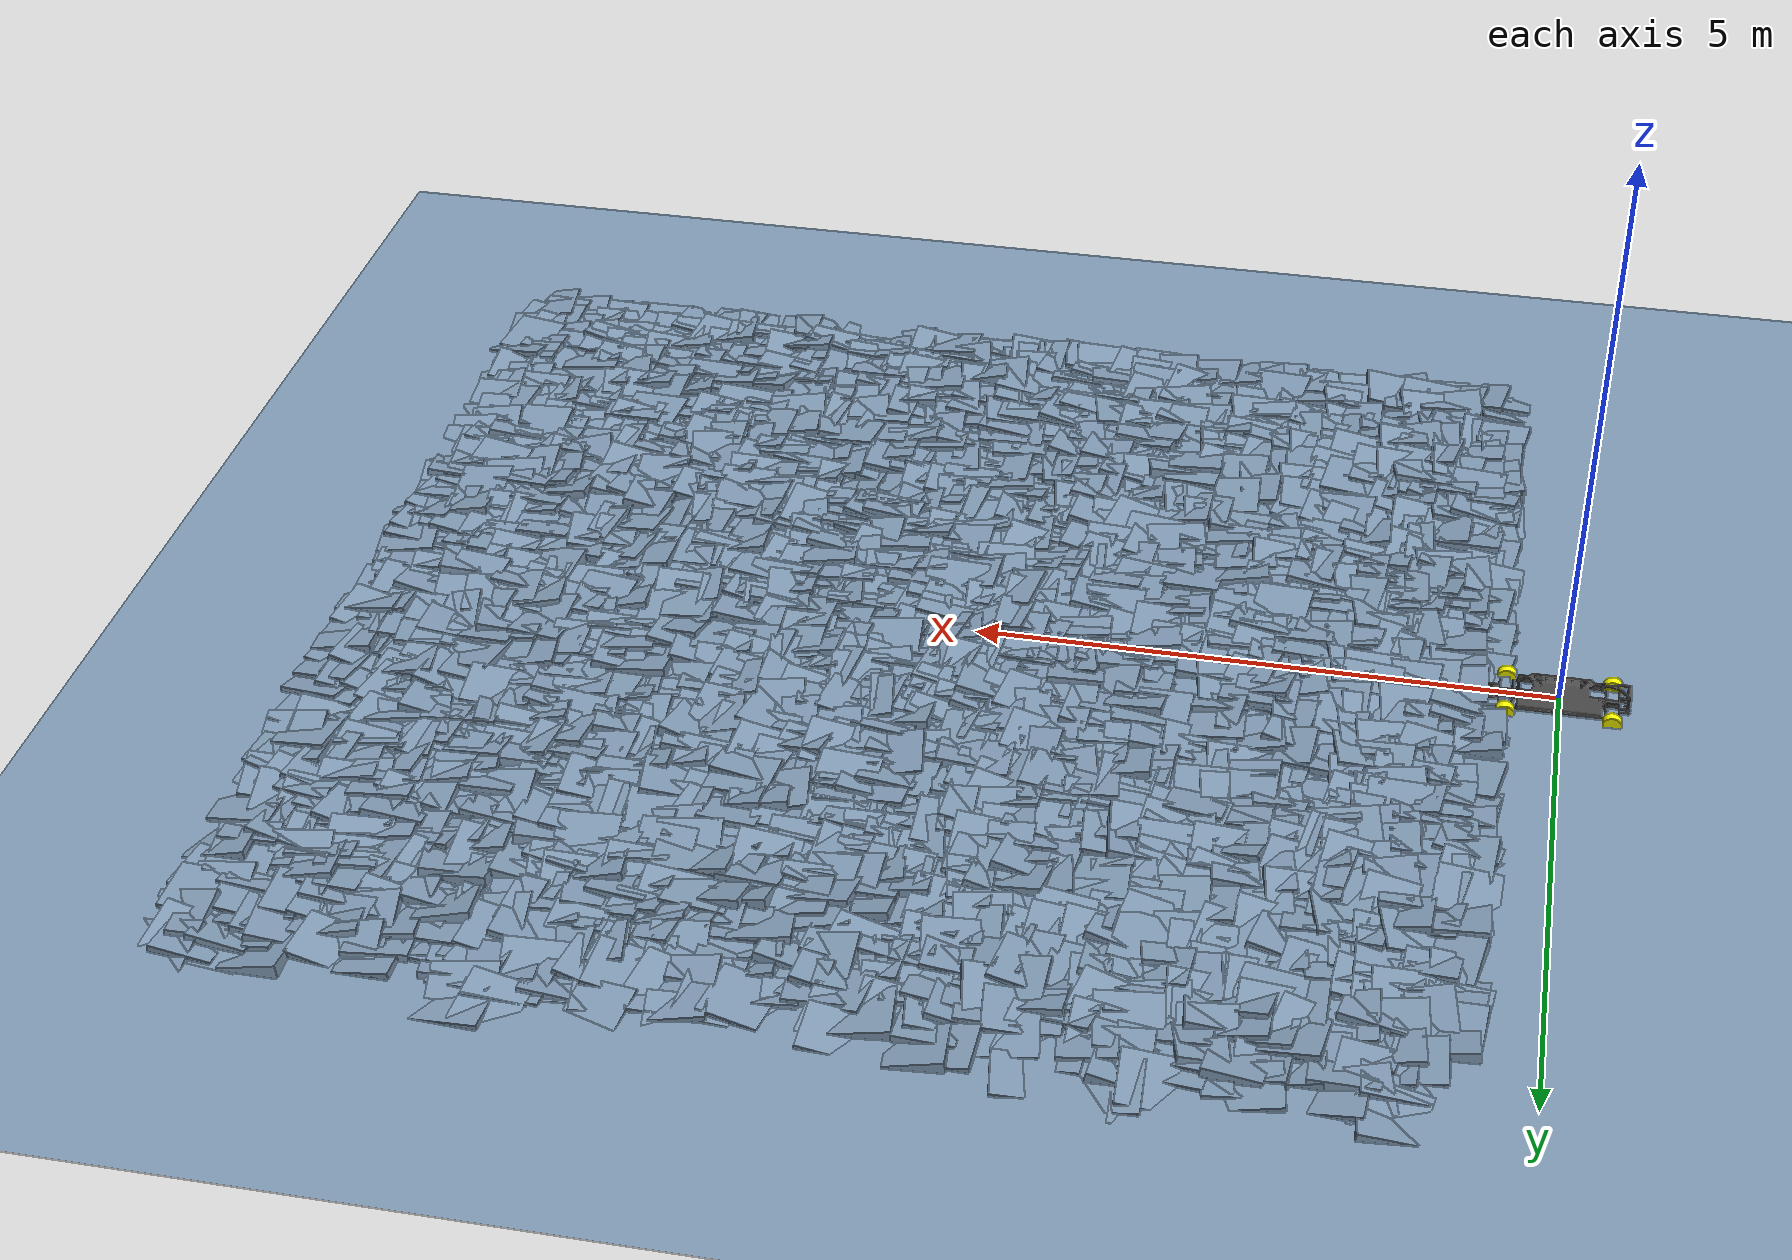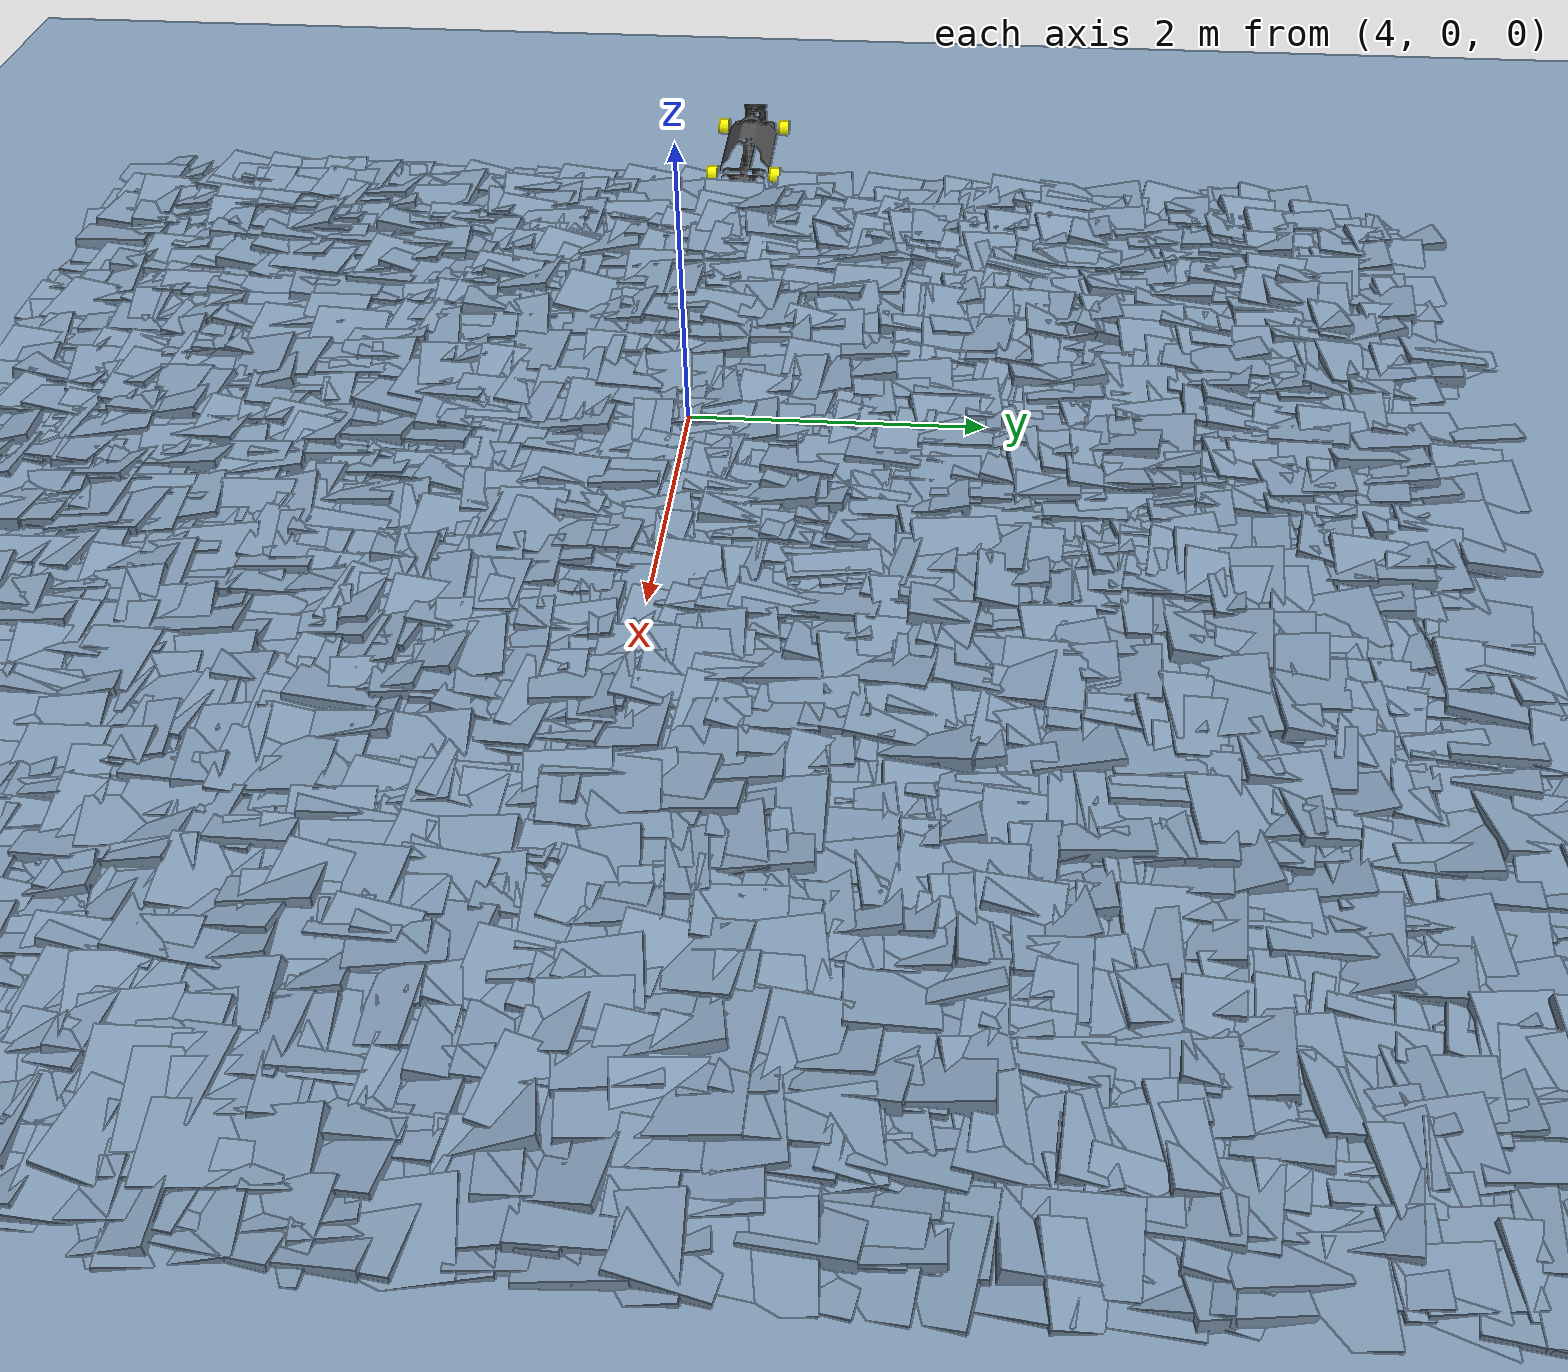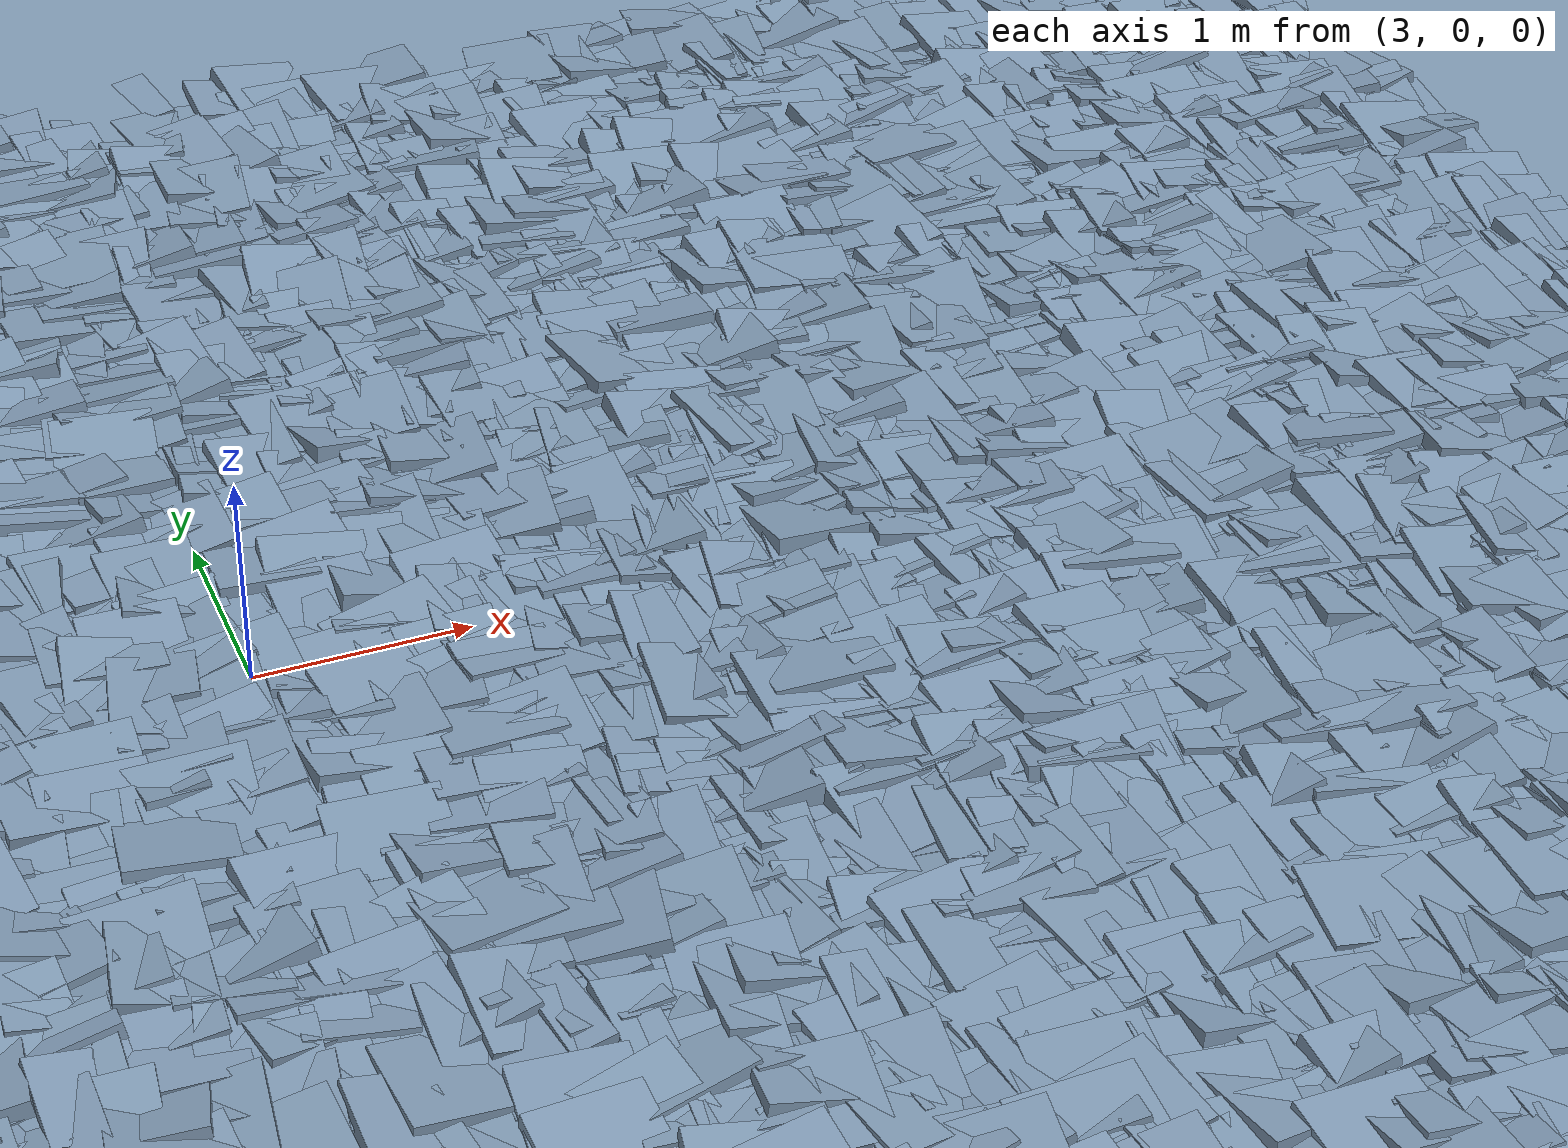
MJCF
<mujoco model="hyqreal scene">
  <include file="hyqreal.xml" />

  <visual>
    <headlight diffuse="0.6 0.6 0.6" ambient="0.3 0.3 0.3" specular="0 0 0" />
    <rgba haze="0.15 0.25 0.35 1" />
    <global azimuth="120" elevation="-20" />
  </visual>
  <asset>
    <texture type="skybox" builtin="gradient" rgb1="0.3 0.5 0.7" rgb2="0 0 0" width="512" height="3072" />
    <texture type="2d" name="groundplane" builtin="checker" mark="edge" rgb1="0.2 0.3 0.4" rgb2="0.1 0.2 0.3" markrgb="0.8 0.8 0.8" width="300" height="300" />
    <material name="groundplane" texture="groundplane" texuniform="true" texrepeat="5 5" reflectance="0.2" />
  </asset>
  <worldbody>
    <light pos="0 2 1.5" dir="0 0 -1" directional="true" />
    <geom name="floor" type="plane" conaffinity="1" condim="3" contype="1" material="groundplane" pos="0 0 0" size="0 0 1" />
  <geom pos="0.6531577584152888 -4.795529305407477 -0.25" type="box" size="0.23334574601523164 0.23330434045024898 0.24854273775020821" quat="0.9963440304821828 0.07713411561038479 -0.03311044834468552 -0.01589337415204634" /><geom pos="0.6531577584152888 -4.6165660050590045 -0.25" type="box" size="0.2658983091376917 0.24813864616104284 0.22805763048794733" quat="0.9879303186969108 0.10137950396145066 -0.09321684723615095 0.07089782061038699" /><geom pos="0.6531577584152888 -4.402492167044149 -0.25" type="box" size="0.24957075548611612 0.24054156480909647 0.2403187083215326" quat="0.9928586588309055 -0.009840909238392263 -0.08849063788037928 0.07939928902314425" /><geom pos="0.6531577584152888 -4.237375513188381 -0.25" type="box" size="0.27447573807173076 0.2561118016387 0.25055472981817895" quat="0.9977400528638437 0.007526410231084312 -0.055507063431550915 0.03710937845738822" /><geom pos="0.6531577584152888 -4.059497764056865 -0.25" type="box" size="0.24012791795765806 0.27126727959254426 0.27341415731100294" quat="0.9939902221764156 -0.06673099863813017 0.027809171196025106 -0.08220135057179975" /><geom pos="0.6531577584152888 -3.88978511744177 -0.25" type="box" size="0.2280953330955843 0.23356065721687722 0.23728876107310726" quat="0.991598289065541 -0.06844023380814497 -0.1021412247572154 0.0401987278862691" /><geom pos="0.6531577584152888 -3.7307247739448126 -0.25" type="box" size="0.25613030044759916 0.22636151290611153 0.2641237918982357" quat="0.991743116088682 -0.08055349903866983 0.09912682594227444 -0.011427942157178687" /><geom pos="0.6531577584152888 -3.54123111328918 -0.25" type="box" size="0.23296420261159329 0.25990999109396895 0.2451818688480691" quat="0.9944431351254966 -0.016195203650358373 0.08684088582924863 0.05726453465180976" /><geom pos="0.6531577584152888 -3.3707971343954752 -0.25" type="box" size="0.2540653195701229 0.2660154839753924 0.26737320808719356" quat="0.9940554904088226 -0.006949107390253531 0.07109410184355548 0.08216459442857242" /><geom pos="0.6531577584152888 -3.203964923399327 -0.25" type="box" size="0.2612809447242787 0.27288058610545984 0.24901425722406875" quat="0.9940319766005166 -0.06029102841390223 0.08878610960265193 0.019556281090486263" /><geom pos="0.6531577584152888 -3.052079065576785 -0.25" type="box" size="0.2270637611101351 0.24640625099411717 0.267848484142079" quat="0.9915600098941231 0.09259232793019676 0.027735214117520578 -0.08640697590523964" /><geom pos="0.6531577584152888 -2.811975220189768 -0.25" type="box" size="0.26597458266301194 0.2594242219154332 0.23721771909655734" quat="0.9952976770951164 0.047849734306228596 0.07617474193604991 -0.03592138063695731" /><geom pos="0.6531577584152888 -2.6547814352636694 -0.25" type="box" size="0.24115761797338087 0.2315599328196299 0.27378825101133447" quat="0.9976467120351054 -0.04202749278588082 -0.03968715419736826 0.036873535325365296" /><geom pos="0.6531577584152888 -2.481638462370784 -0.25" type="box" size="0.23583311638126653 0.2708622798698966 0.2425954072401767" quat="0.9906509046846115 -0.06672374827545688 0.06142375299486366 0.1019109858242011" /><geom pos="0.6531577584152888 -2.3203962090699837 -0.25" type="box" size="0.239678657964443 0.228347828943271 0.22998090499561877" quat="0.9941484583500825 -0.06233959225723075 -0.0835368572010304 -0.028358622786221168" /><geom pos="0.6531577584152888 -2.113578990211084 -0.25" type="box" size="0.25546608419262257 0.2368292329393453 0.24225622482839088" quat="0.9918270361033553 -0.07628014218311842 0.06325648339557763 -0.0803684494772776" /><geom pos="0.6531577584152888 -1.9099491665386013 -0.25" type="box" size="0.22638669724663812 0.2621010064901542 0.23500769793380358" quat="0.9956092981033654 -0.07693393509270981 -0.0312707909548649 0.0431906563313399" /><geom pos="0.6531577584152888 -1.6881947257601135 -0.25" type="box" size="0.2538240792832861 0.22668814152958558 0.26903829241412947" quat="0.997893772674347 -0.00604538731235621 -0.06364293641151794 -0.011002199549272767" /><geom pos="0.6531577584152888 -1.4708549007335647 -0.25" type="box" size="0.265555788419619 0.2673962671417576 0.2312387797274686" quat="0.9991824192246568 -0.03363469091157996 0.019194131585712867 -0.011609736961488837" /><geom pos="0.6531577584152888 -1.2971614875893138 -0.25" type="box" size="0.23955231196844518 0.22502306728293217 0.2668697016201287" quat="0.9958850864132038 -0.026745040115992755 0.06829066136152963 -0.0532351675094995" /><geom pos="0.6531577584152888 -1.1199915489039554 -0.25" type="box" size="0.24129891348829127 0.25331504762473833 0.2507659350443913" quat="0.9949634231926991 0.05885768667322563 -0.07583439862102258 0.028856597407358072" /><geom pos="0.6531577584152888 -0.9626486734931818 -0.25" type="box" size="0.2681793632753193 0.2569770821725236 0.244319059696131" quat="0.9987493778759913 0.02808319188605115 0.021536590820410994 0.03531557420807153" /><geom pos="0.6531577584152888 -0.7680913568946153 -0.25" type="box" size="0.271415840721842 0.2537569891116475 0.24680589735296826" quat="0.9945979614253815 -0.06387747282523384 0.05836773733395487 -0.05733908642847011" /><geom pos="0.6531577584152888 -0.5296709278207103 -0.25" type="box" size="0.26190816047866833 0.22718740560356224 0.2352457719611408" quat="0.9979137157600948 0.011340220375816801 -0.048964405294092433 0.04052286162038044" /><geom pos="0.6531577584152888 -0.30828104811070745 -0.25" type="box" size="0.2603274204283841 0.26375151625625803 0.24245668880093893" quat="0.9921178823666732 -0.06714185964006873 0.053683768351788876 -0.09117089002468245" /><geom pos="0.6531577584152888 -0.1355242413400699 -0.25" type="box" size="0.2635020397961704 0.24216628461563783 0.24169059105539697" quat="0.9962640343281687 0.01450230481280973 0.0550625188468573 0.06492900798192912" /><geom pos="0.6531577584152888 0.017909233324431284 -0.25" type="box" size="0.2380383109334889 0.2326075749576046 0.23171708862527346" quat="0.9946773824320144 0.04611739231371274 0.031737106920075725 0.08650345107984318" /><geom pos="0.6531577584152888 0.18473482491604187 -0.25" type="box" size="0.23672090613079774 0.27229721347650504 0.23059169109656646" quat="0.9957681447018119 0.07283674395476329 -0.026876855583608878 -0.04917565821742825" /><geom pos="0.6531577584152888 0.34461304084988065 -0.25" type="box" size="0.2448755294054651 0.24720019850053102 0.2295435947193149" quat="0.9961723550321712 -0.05464772582667046 0.02271283304043547 0.06433033768688165" /><geom pos="0.6531577584152888 0.5102517497279999 -0.25" type="box" size="0.2740577086356302 0.22574391594212695 0.2576151348391544" quat="0.9963353608252958 -0.01509250227194101 0.0825051378671673 0.016762081309278854" /><geom pos="0.6531577584152888 0.6637842809329646 -0.25" type="box" size="0.24479558787495667 0.2731741767144262 0.25800654370880893" quat="0.9942234064911862 0.05788306611209386 0.0838318692174086 0.033787369622976654" /><geom pos="0.6531577584152888 0.8351127012548352 -0.25" type="box" size="0.22683571997032181 0.26095579016859155 0.2463939643043383" quat="0.9939862507401707 -0.08561643006825043 -0.06794106560258296 -0.006721000420510742" /><geom pos="0.6531577584152888 1.0074216991382112 -0.25" type="box" size="0.2591427456613191 0.2528395824345571 0.23637810781470464" quat="0.9959897713140149 0.018067345747050722 -0.07239094931006393 -0.049371012887123714" /><geom pos="0.6531577584152888 1.203156846528402 -0.25" type="box" size="0.2611627319887081 0.2334262454217231 0.2619447225246313" quat="0.9936303487208494 -0.00958283191640815 0.06817881789697189 -0.08921069567891912" /><geom pos="0.6531577584152888 1.419254932520082 -0.25" type="box" size="0.24200811214689494 0.259329091015733 0.23987383525328868" quat="0.9904596879276504 0.09971353037869736 -0.0012588329289355826 -0.09510643400598578" /><geom pos="0.6531577584152888 1.6084683317320714 -0.25" type="box" size="0.2397829443733234 0.26938149594744537 0.2474135497338501" quat="0.9970395316224226 0.05093642942948571 0.026015639763240915 -0.05138909443475772" /><geom pos="0.6531577584152888 1.853539753631341 -0.25" type="box" size="0.2568375835990687 0.2544078317319274 0.2387393108057816" quat="0.9903470024328916 -0.09760554249648998 0.09572829749475821 0.022848761561774004" /><geom pos="0.6531577584152888 2.060258725106663 -0.25" type="box" size="0.26940655194932955 0.23066229652141576 0.25915638244014316" quat="0.9922654053470452 0.06969903829898871 -0.045986930238027815 -0.09185102971084957" /><geom pos="0.6531577584152888 2.2376348064346097 -0.25" type="box" size="0.27109188060790823 0.2573657583868426 0.2609396324010283" quat="0.9942491514739679 -0.05617200754358293 0.07975197284153582 -0.04419222996977476" /><geom pos="0.6531577584152888 2.439528463028548 -0.25" type="box" size="0.26540225690116387 0.2556122054868983 0.25062932004910443" quat="0.9910190361454948 -0.07326028757694848 -0.09244411639811281 -0.06299432994142953" /><geom pos="0.6531577584152888 2.6465457341627987 -0.25" type="box" size="0.26198329770721085 0.2501502613111323 0.26910210018473635" quat="0.9977534583084194 -0.04456782970825155 -0.04631275234550851 -0.018891107931220414" /><geom pos="0.6531577584152888 2.8409117377006057 -0.25" type="box" size="0.26889068228107105 0.2340475309768612 0.2324331067521631" quat="0.999343347339266 -0.03349825432171068 -0.007632564576869057 0.01151021477336435" /><geom pos="0.6531577584152888 3.0344188204722844 -0.25" type="box" size="0.23341199825286385 0.24028259743944802 0.27397445894916606" quat="0.9950310704941933 0.09573199120628256 0.025839564207462504 0.008992860080564864" /><geom pos="0.6531577584152888 3.206715225785585 -0.25" type="box" size="0.24684215833191928 0.23026245941315274 0.22636067800934145" quat="0.9936303537537484 -0.09762126417506024 -0.01644465349862073 0.05383662555709003" /><geom pos="0.6531577584152888 3.4384572976653356 -0.25" type="box" size="0.2277238921961964 0.243118306771747 0.26487703940623997" quat="0.989463444669694 -0.07269770647328735 0.09078188278583955 -0.08623099729079703" /><geom pos="0.6531577584152888 3.6455058070001147 -0.25" type="box" size="0.2518033773327019 0.24701816621237768 0.24979417663656597" quat="0.9967083367373455 -0.024214921167190366 -0.07599083123941516 0.014543817885408292" /><geom pos="0.6531577584152888 3.797607261867361 -0.25" type="box" size="0.2529562378784295 0.25364484096310325 0.2470374866624034" quat="0.996464980590799 0.07611280498449062 0.010963167568271402 -0.033825912115439415" /><geom pos="0.6531577584152888 3.9526787312167073 -0.25" type="box" size="0.2672848327091658 0.22846031915324805 0.23593655132628938" quat="0.9968350153742669 -0.05962607196912296 -0.003141162479571479 -0.05248634835454661" /><geom pos="0.6531577584152888 4.199966966108839 -0.25" type="box" size="0.2639644526820329 0.2524394725348744 0.2579533065753987" quat="0.9932994725893974 -0.09576528043917208 0.04937208558273601 -0.04180389911530587" /><geom pos="0.6531577584152888 4.367248880393264 -0.25" type="box" size="0.2360454854744373 0.24828217509560166 0.26222507842927933" quat="0.9943069808232831 0.08024327375151574 0.06209205143833468 0.03254569175645305" /><geom pos="0.8388023156659219 -4.821155392200508 -0.25" type="box" size="0.231569226879473 0.2660232230867716 0.26687451362448744" quat="0.994132618912476 0.05161439922164852 0.06511592224767009 -0.06925464949767203" /><geom pos="0.8388023156659219 -4.649768628503888 -0.25" type="box" size="0.2523686333005337 0.2448642165074926 0.24603167600987144" quat="0.9997027304226063 -0.01984320427342189 -0.01375145297687213 -0.003405226978338515" /><geom pos="0.8388023156659219 -4.46518534892637 -0.25" type="box" size="0.23852799596009275 0.23195250331455233 0.2294158320512878" quat="0.9943218670145544 0.03237637125698739 -0.05477264853870117 0.08529802068616017" /><geom pos="0.8388023156659219 -4.305560953625275 -0.25" type="box" size="0.2476174296238366 0.2694379677125902 0.22917287454715213" quat="0.9935034077912732 0.047277575618201534 -0.0941237013264525 -0.043087566645159885" /><geom pos="0.8388023156659219 -4.143830983302751 -0.25" type="box" size="0.2393092677325076 0.2639071924654366 0.26053156762721874" quat="0.9941772715914073 -0.057686566692529 -0.08876753214175613 -0.02010318163266656" /><geom pos="0.8388023156659219 -3.9223391920321427 -0.25" type="box" size="0.2700897024837193 0.25046772558685576 0.2664679355667098" quat="0.9963281807586001 -0.0077013527029661496 0.07868175587344271 -0.03286375945437199" /><geom pos="0.8388023156659219 -3.7457935024178575 -0.25" type="box" size="0.24335850767745912 0.258730081384244 0.23066637396294878" quat="0.9901807864412815 -0.09153484825710317 0.08901451574915624 0.05691922085743549" /><geom pos="0.8388023156659219 -3.5571485890500556 -0.25" type="box" size="0.2599120458946581 0.22939307437972256 0.25918952190687206" quat="0.9978726169828207 0.024270306489724905 0.05972228544539929 0.009718082111703727" /><geom pos="0.8388023156659219 -3.392353467264443 -0.25" type="box" size="0.2653431244042174 0.23481393569287273 0.23704226134064724" quat="0.9957566284043655 -0.009722340073942938 -0.09095384213823719 -0.010080262523846329" /><geom pos="0.8388023156659219 -3.1972305218120045 -0.25" type="box" size="0.2437685962165418 0.25381105832141154 0.2719362446236209" quat="0.9968571961811826 -0.05637811463056986 0.005902332729392338 -0.0553389653033481" /><geom pos="0.8388023156659219 -3.038217327161431 -0.25" type="box" size="0.2625723188173752 0.2745668024613003 0.27418415191570245" quat="0.9983202650038162 0.027315120494339203 0.018182629413730157 0.04774855665559744" /><geom pos="0.8388023156659219 -2.8564369069856492 -0.25" type="box" size="0.2344936089671423 0.2671421625352345 0.272907856600831" quat="0.9928561256136811 0.06268279003326827 -0.07413757871494504 -0.06936282208302072" /><geom pos="0.8388023156659219 -2.6516539574153537 -0.25" type="box" size="0.2294480998562361 0.24457930086928992 0.22590436009958" quat="0.9952453656870774 0.07108535988799414 -0.04612979139628995 0.048016414211439984" /><geom pos="0.8388023156659219 -2.483110816752699 -0.25" type="box" size="0.26361167302436456 0.2509873982624058 0.24026992970408936" quat="0.9967136622032045 0.023309165887655286 0.07152520429322186 -0.030045024778004206" /><geom pos="0.8388023156659219 -2.2935261495596135 -0.25" type="box" size="0.27349458376372604 0.2321554145320014 0.273542860021851" quat="0.9948130480656898 0.09021637396845317 0.021373421235227882 -0.041847128108595415" /><geom pos="0.8388023156659219 -2.094481836009405 -0.25" type="box" size="0.24385229514662918 0.24017754022062576 0.24592457519406402" quat="0.9990400702557946 -0.0005642050629555217 0.026922959666042065 -0.034551033830620935" /><geom pos="0.8388023156659219 -1.9111973818163874 -0.25" type="box" size="0.2522696734940143 0.2555693556926899 0.234090004809971" quat="0.995493815923751 0.06307054996921127 -0.0707918772696863 -0.0016365502693323026" /><geom pos="0.8388023156659219 -1.6863386648178293 -0.25" type="box" size="0.23561587418982144 0.25791736248831637 0.2710638488539098" quat="0.991026306487665 -0.08413024329354049 0.08565251770531189 0.05875889910071084" /><geom pos="0.8388023156659219 -1.4899740784618278 -0.25" type="box" size="0.2723616425651141 0.25180832352682964 0.2608134185673054" quat="0.9959949700417894 0.0756171383183221 -0.007776049070542376 0.047070172135388146" /><geom pos="0.8388023156659219 -1.3035670538927242 -0.25" type="box" size="0.23923595766943923 0.24668709516079243 0.259875169270421" quat="0.9945987314474476 0.043194061033075444 0.09395757963896646 -0.008922428088030333" /><geom pos="0.8388023156659219 -1.083645703345598 -0.25" type="box" size="0.25696110646309545 0.251103775945639 0.2559369889491314" quat="0.9965416303139409 0.048911051279776456 0.042078032253535985 -0.05236341581304755" /><geom pos="0.8388023156659219 -0.8996237618985026 -0.25" type="box" size="0.22778738397655537 0.26300786743174903 0.24979610751987533" quat="0.9956437362587383 -0.07234969331497346 0.013542145474215946 0.05723357949599641" /><geom pos="0.8388023156659219 -0.702860707596777 -0.25" type="box" size="0.22695007079341445 0.2630985085852062 0.273099728319099" quat="0.9958389359372359 0.07421931906111225 0.049290489449331606 0.019150822419517193" /><geom pos="0.8388023156659219 -0.4777359556640688 -0.25" type="box" size="0.2402827895958976 0.2300271843147217 0.2544071496590981" quat="0.9955713908880703 0.06753737393367669 0.060624161169846015 0.024515706185799752" /><geom pos="0.8388023156659219 -0.3212079310281437 -0.25" type="box" size="0.2682364713472065 0.2635606471302626 0.27107699582552797" quat="0.9986188348331722 -0.019829392199054933 -0.01884671490173328 0.04485553766110191" /><geom pos="0.8388023156659219 -0.08564262779794962 -0.25" type="box" size="0.27398407016528253 0.256118508654909 0.2616239032855888" quat="0.9977947646779951 -0.032849481895375135 0.0559008908572403 0.014198926781860964" /><geom pos="0.8388023156659219 0.1331938995919657 -0.25" type="box" size="0.24637255825331117 0.2575904760641046 0.2599503936878691" quat="0.9927712322807807 0.08454275266064748 -0.06660249666419056 -0.05312166004896239" /><geom pos="0.8388023156659219 0.2882849040172939 -0.25" type="box" size="0.2509921368868613 0.26359998743705515 0.25846451880501825" quat="0.992824751169585 0.07332343564308179 -0.08505774010794677 -0.04108367191811743" /><geom pos="0.8388023156659219 0.501259172532766 -0.25" type="box" size="0.2712706160721068 0.274337611107622 0.24543915006042838" quat="0.9950913944651978 0.05597302762141333 0.07908131951991736 -0.02015643180698268" /><geom pos="0.8388023156659219 0.742194632460377 -0.25" type="box" size="0.23445411500263105 0.23237072857119345 0.22597295897986064" quat="0.9927166108213891 -0.06528122752687314 0.051097603242428166 0.08741353942472944" /><geom pos="0.8388023156659219 0.9613900644357294 -0.25" type="box" size="0.2657101110222347 0.2643080265162143 0.24319990551714582" quat="0.995521499488728 0.049619630577940825 -0.05036595495279504 0.06275433768845322" /><geom pos="0.8388023156659219 1.1697126745698787 -0.25" type="box" size="0.23585054061423635 0.23610902811814855 0.23127351128847518" quat="0.9909039452045003 0.09539785856992265 -0.07985337311399483 0.05130359403342613" /><geom pos="0.8388023156659219 1.3208838274233026 -0.25" type="box" size="0.2443982191319303 0.26347426583638106 0.23840533008178683" quat="0.9943167903066631 -0.0864867030029664 0.04613518543908881 0.041541730614322786" /><geom pos="0.8388023156659219 1.5099151316979542 -0.25" type="box" size="0.23189386801410541 0.2626915470833173 0.25907504939780246" quat="0.9986186332567701 0.01861156783985951 0.0382750897188341 -0.03081318487170592" /><geom pos="0.8388023156659219 1.6773534763804054 -0.25" type="box" size="0.26342246587879176 0.26135639564299706 0.2293720923179951" quat="0.9991414764060345 -0.008691821350295744 0.03985582973097232 0.007230159281800799" /><geom pos="0.8388023156659219 1.860887530064666 -0.25" type="box" size="0.269466355361376 0.25983493539209596 0.262350198309709" quat="0.9978371626190065 0.045137395736527426 0.02860803944308837 0.038277832772996075" /><geom pos="0.8388023156659219 2.090469272940295 -0.25" type="box" size="0.22647105348572555 0.24165430912899147 0.23303561765054404" quat="0.9921821283948956 -0.0495116939003818 0.09501024327110108 -0.06400210882819532" /><geom pos="0.8388023156659219 2.309860442523962 -0.25" type="box" size="0.26459791037641395 0.2353426143380028 0.22988820849632924" quat="0.9916462152389802 0.09459232683816193 -0.08730813087013325 0.008207666508349155" /><geom pos="0.8388023156659219 2.498379059351195 -0.25" type="box" size="0.24762611456877223 0.23769605335863786 0.2610619767663522" quat="0.9930586374152381 -0.08250941370178634 0.032553813001445185 0.07724628511873662" /><geom pos="0.8388023156659219 2.6731222076299783 -0.25" type="box" size="0.22750949620046113 0.2563502482010808 0.25106195608408843" quat="0.9928224980648286 -0.04584128964217998 0.05871543106844093 -0.09356581456227667" /><geom pos="0.8388023156659219 2.86997522621645 -0.25" type="box" size="0.2302107387280836 0.25467452140828517 0.22851386740062105" quat="0.9984614932254261 -0.006432121653838897 0.024514569536162524 0.04931845737185371" /><geom pos="0.8388023156659219 3.052706274447056 -0.25" type="box" size="0.23177608793523166 0.22533905755315328 0.24978310646003082" quat="0.9927043668249461 0.04077208145159127 0.09187058730477743 -0.06659934420895648" /><geom pos="0.8388023156659219 3.2892266263730683 -0.25" type="box" size="0.247448803515976 0.22785233825535395 0.2318791892584873" quat="0.9881550339422345 -0.10068028368203721 0.08673051494564707 0.07675237553059132" /><geom pos="0.8388023156659219 3.505144058034153 -0.25" type="box" size="0.22871042685987922 0.2735469065749931 0.2634504345046445" quat="0.9964056372600478 0.06904334895369127 0.020475308094201988 -0.04460475042083072" /><geom pos="0.8388023156659219 3.6802457381591314 -0.25" type="box" size="0.24053960583581263 0.24874140287602994 0.26960082746349584" quat="0.9993083197060114 -0.005672030589079788 -0.026427820115829722 -0.02553978385323629" /><geom pos="0.8388023156659219 3.8349846154808933 -0.25" type="box" size="0.263581425546792 0.23759270090686424 0.2360492895162701" quat="0.9964842458283537 -0.01836891570499715 -0.06328783949525593 0.05173374260328324" /><geom pos="0.8388023156659219 4.063076363170678 -0.25" type="box" size="0.2534941839607631 0.23922138115664257 0.2625472590053197" quat="0.9883636959554003 -0.09605171427408635 0.08910393475869757 0.0772771732978653" /><geom pos="0.8388023156659219 4.22918430637761 -0.25" type="box" size="0.26323903904018464 0.22773743137129426 0.24676443918018925" quat="0.996247013867329 0.026419151721822548 -0.05316788785915678 -0.0629848512209527" /><geom pos="0.8388023156659219 4.388707080088025 -0.25" type="box" size="0.2535915842013375 0.2608960371468865 0.23813873499250737" quat="0.9956321419772272 0.015866434275328703 -0.06367898574420745 -0.06640693412449152" /><geom pos="0.8388023156659219 4.609523391035481 -0.25" type="box" size="0.22668658459303656 0.23094182556072645 0.26408225746332137" quat="0.9937731319349541 -0.05947936517446727 0.08987403610936388 0.028281177416213124" /><geom pos="1.059224940272597 -4.774758805956534 -0.25" type="box" size="0.2518925293180225 0.24146312363050618 0.24933607754237802" quat="0.9910158495381824 -0.014173757969504597 0.09522264586119782 -0.09284039134088727" /><geom pos="1.059224940272597 -4.612900520448568 -0.25" type="box" size="0.2267031019165977 0.24553173078131263 0.2746424208435571" quat="0.9923163198326715 -0.07921987911042266 0.06965977010304063 0.06465329517251714" /><geom pos="1.059224940272597 -4.373211286896315 -0.25" type="box" size="0.2716932433232512 0.26210459670339403 0.24857740920921542" quat="0.9918101111876562 0.08956985802902036 -0.06353403205670316 -0.06521787062767463" /><geom pos="1.059224940272597 -4.15150445047413 -0.25" type="box" size="0.2256086373578022 0.22696243324526832 0.2641900522416592" quat="0.9931396525450791 -0.06903996229398016 0.06339752733576742 -0.06991328684017108" /><geom pos="1.059224940272597 -3.932128060362574 -0.25" type="box" size="0.25163090411723854 0.24533783427884162 0.23359017441620958" quat="0.9979487200972825 0.05862444972619741 -0.024857330642388167 0.006605986968760433" /><geom pos="1.059224940272597 -3.776252296082146 -0.25" type="box" size="0.2710556674624195 0.2546815338727657 0.25869273636147805" quat="0.9970544303474038 -0.023253766154936524 -0.0730583287035873 0.0020508269707327186" /><geom pos="1.059224940272597 -3.6073026345712065 -0.25" type="box" size="0.2514078111689975 0.23847565997011913 0.2525595708676698" quat="0.9960131261042725 -0.025834412088049114 -0.0812303015804154 0.026307297185652986" /><geom pos="1.059224940272597 -3.421812305912649 -0.25" type="box" size="0.2731492068297382 0.27247598818390073 0.26275166682318146" quat="0.9959873749732933 -0.038411724126731515 0.04737943586133164 -0.06548952130594855" /><geom pos="1.059224940272597 -3.2349505707356316 -0.25" type="box" size="0.24881821345597727 0.2506266244980565 0.25690180194990453" quat="0.992387501828011 0.06778982259420409 0.02842598560577212 -0.09881067508395151" /><geom pos="1.059224940272597 -3.002566108331003 -0.25" type="box" size="0.24962164298890502 0.22912236780006806 0.25649918199201993" quat="0.9940104555542264 -0.06303046551789684 0.08493969922450319 -0.027488582377549788" /><geom pos="1.059224940272597 -2.790328932238023 -0.25" type="box" size="0.23727590860684844 0.2488210756237982 0.25575363210150354" quat="0.9905125518976753 0.06672522961200097 -0.08945593853477149 0.08018892272155875" /><geom pos="1.059224940272597 -2.5423152632189154 -0.25" type="box" size="0.25518622429776683 0.2443581425326476 0.2502776113179923" quat="0.9960135238545524 -0.02256000216365383 -0.0695248855102135 -0.05113117342683161" /><geom pos="1.059224940272597 -2.384424862126122 -0.25" type="box" size="0.24359476006535866 0.2411954109047565 0.2720660840992356" quat="0.9955057180154798 0.04149681423131424 0.08386253769385402 -0.014610084828042363" /><geom pos="1.059224940272597 -2.183435550225484 -0.25" type="box" size="0.23198141316868098 0.25060389470297406 0.23710520191535725" quat="0.9907710926959343 0.07253747882759773 -0.06393449709939683 0.09499124235468963" /><geom pos="1.059224940272597 -1.981402883484575 -0.25" type="box" size="0.25974397158585993 0.2723362645659774 0.2494678951871715" quat="0.9915473958747173 0.05479574653586072 -0.0967563234530259 -0.06685358455234729" /><geom pos="1.059224940272597 -1.7936588581718378 -0.25" type="box" size="0.24712350667501495 0.24022119709004708 0.2682600882161518" quat="0.9924300725149332 -0.0846574322397334 -0.019818472425453086 0.08673464408931768" /><geom pos="1.059224940272597 -1.5465194803574867 -0.25" type="box" size="0.2289733691655615 0.2519558069709479 0.24644363391414595" quat="0.9890770131692621 0.08246885377109159 0.08639754176166235 -0.08637716686367605" /><geom pos="1.059224940272597 -1.3295626517819241 -0.25" type="box" size="0.25055359137245076 0.22753018284632937 0.26959192289072276" quat="0.9977732049741606 0.06576313043318886 -0.003044975346563681 -0.010703748705848018" /><geom pos="1.059224940272597 -1.0924795367446896 -0.25" type="box" size="0.274486892453473 0.23345039432171308 0.23944160567282735" quat="0.9980856223077891 0.028043591697046254 -0.02035518909427379 -0.05122805661099409" /><geom pos="1.059224940272597 -0.9227968531200652 -0.25" type="box" size="0.24062605889539107 0.22760735319296932 0.25075028657270015" quat="0.993188097384695 -0.03828964402257415 -0.09457292688531706 -0.056278485003937215" /><geom pos="1.059224940272597 -0.7563026712505918 -0.25" type="box" size="0.22727867624781034 0.23952899141456188 0.26938101240761964" quat="0.9983917628876241 -0.056515704799275444 -0.003967888987751522 0.002029474356643352" /><geom pos="1.059224940272597 -0.507038530717927 -0.25" type="box" size="0.2600543820837702 0.23069786719816454 0.22699482884950925" quat="0.9954758127037395 0.005110610739937339 -0.08885852163036956 -0.03325584329647099" /><geom pos="1.059224940272597 -0.31802187894988343 -0.25" type="box" size="0.23856362540295464 0.2605021554922213 0.25147507936062974" quat="0.9953189696650455 -0.03220844794499745 -0.033486303459643964 0.08474333004133965" /><geom pos="1.059224940272597 -0.10917409224369212 -0.25" type="box" size="0.2482299868492692 0.2517369165155748 0.261127440518229" quat="0.9946954378903208 -0.08304280695767584 0.057377817984068276 -0.019815752727573358" /><geom pos="1.059224940272597 0.07979705923373182 -0.25" type="box" size="0.22583738927624927 0.25968506373063843 0.2387081291732601" quat="0.9996580135995339 0.009113727344230847 -0.012101558780089394 0.02131544264661448" /><geom pos="1.059224940272597 0.29683583662481006 -0.25" type="box" size="0.23117038537939083 0.2550564032484444 0.24784589333076001" quat="0.9955655334224756 0.06808150411147303 -0.05943214085111039 -0.02611509320287639" /><geom pos="1.059224940272597 0.48142025345815487 -0.25" type="box" size="0.23671391366995578 0.22568207775958726 0.24327814232144743" quat="0.9959607701787072 0.054483138165855996 0.07123779360474214 0.004348411545007791" /><geom pos="1.059224940272597 0.6837510693236002 -0.25" type="box" size="0.2731978976302098 0.25236293382032887 0.23664546600542335" quat="0.9965077997031155 0.011915317706448419 -0.06754041683847821 -0.047629008262763145" /><geom pos="1.059224940272597 0.906886286224438 -0.25" type="box" size="0.25023448791205033 0.2720332043109653 0.25840769372897215" quat="0.9915700853609747 -0.07665646905537844 -0.024954437170403618 -0.10143878762435582" /><geom pos="1.059224940272597 1.0854674733401675 -0.25" type="box" size="0.24784946242814207 0.2496353937546337 0.2487005956230541" quat="0.9927431344097943 -0.00788469442769703 0.0937036584831145 -0.0749568213232021" /><geom pos="1.059224940272597 1.3331381127430557 -0.25" type="box" size="0.24445745066354882 0.25186446712107985 0.2518131533842424" quat="0.99202110887905 -0.09383809019452026 0.0352591464735537 -0.0764547248833003" /><geom pos="1.059224940272597 1.5276792657432807 -0.25" type="box" size="0.2287499782441617 0.27250220649504464 0.25259707107171264" quat="0.9947182152529351 0.04692744989895454 0.07705147420189823 -0.04895464240816216" /><geom pos="1.059224940272597 1.6935486197893033 -0.25" type="box" size="0.269047118210803 0.25788486345291395 0.24633463932245583" quat="0.9916759516494293 0.09503527373453202 -0.06709256449130521 0.05518778357917234" /><geom pos="1.059224940272597 1.8948666761429225 -0.25" type="box" size="0.2533343306371923 0.22507787304951088 0.24270015332987285" quat="0.9941952353420928 0.0766319965378573 -0.0745595496179059 -0.012010191109124919" /><geom pos="1.059224940272597 2.0998618777815503 -0.25" type="box" size="0.2527042865137008 0.23149696192172575 0.25331825342472164" quat="0.9941761523521153 0.06505509711265557 -0.06759747566996417 0.05303012084707375" /><geom pos="1.059224940272597 2.3052983158122284 -0.25" type="box" size="0.22623995733514984 0.23037765003988364 0.2691206948290981" quat="0.9989942683544422 -0.006011060979345454 0.009465159500978126 -0.04341347367461349" /><geom pos="1.059224940272597 2.538692094508842 -0.25" type="box" size="0.2334748542810683 0.24975936826745307 0.2630347315694722" quat="0.9928625615227368 -0.0674043543548575 0.08970285660602406 -0.04042257360972494" /><geom pos="1.059224940272597 2.7489816272137952 -0.25" type="box" size="0.2662237582611977 0.24772583783783358 0.2430484321235765" quat="0.9955502876086639 0.08693818121722155 -0.03293512874090999 0.015383588130465798" /><geom pos="1.059224940272597 2.9931662933514422 -0.25" type="box" size="0.23987482060881735 0.267775720440288 0.2578219808545745" quat="0.9939396905827018 0.06400964041961443 0.08816181326060142 -0.014633936596736005" /><geom pos="1.059224940272597 3.223348114770859 -0.25" type="box" size="0.23352149109108275 0.2517191099039515 0.2505399685715517" quat="0.9903990434386967 0.028375014844527747 -0.09461780025101463 0.0967060761480195" /><geom pos="1.059224940272597 3.4371054880599328 -0.25" type="box" size="0.259345171019443 0.24378519640455523 0.2288962673683796" quat="0.991813148740944 -0.08469410302854093 0.0028908800237244132 0.09552606821937969" /><geom pos="1.059224940272597 3.6774341031838365 -0.25" type="box" size="0.2264461225246934 0.2707928490365992 0.23563779689261094" quat="0.9946523199655641 0.04872405714074206 0.08873078115289743 -0.020483581690312218" /><geom pos="1.059224940272597 3.894928830832569 -0.25" type="box" size="0.23665790919449572 0.22518193785135937 0.2694290818449479" quat="0.9953157428472644 -0.08372643898284857 -0.03515386153634776 0.03317621851165267" /><geom pos="1.059224940272597 4.056409165077607 -0.25" type="box" size="0.2662609449145105 0.24365645954453896 0.24227724302115705" quat="0.993048125091473 -0.08669749703666207 -0.03098644044539979 0.0733403420254637" /><geom pos="1.059224940272597 4.251664716744063 -0.25" type="box" size="0.26986618286638536 0.24541753004805864 0.26905774888865297" quat="0.9946049776690844 -0.07200421036940559 0.05905522050399475 0.045703533957265695" /><geom pos="1.059224940272597 4.498014815611393 -0.25" type="box" size="0.2639861423145126 0.24324818886161978 0.2622319514623841" quat="0.9954170708617864 0.031330551931010336 0.07341230920603688 0.05266767898509009" /><geom pos="1.059224940272597 4.687460731670583 -0.25" type="box" size="0.2332337671192743 0.25454017271782226 0.22500316780004403" quat="0.9943396275612757 0.04041888126175373 0.09791930233875312 -0.008174920693422004" /><geom pos="1.059224940272597 4.894849002578466 -0.25" type="box" size="0.26013831389176756 0.2295103424745641 0.2632409202489086" quat="0.9963653956833238 0.047891409306064406 -0.06611219342568486 0.02432260430006022" /><geom pos="1.059224940272597 5.14435998378446 -0.25" type="box" size="0.2732225975317277 0.23083157241327815 0.24806661374190264" quat="0.9929380826285346 -0.07047558496283099 -0.03827857073268448 -0.08741800165171427" /><geom pos="1.059224940272597 5.303131357906446 -0.25" type="box" size="0.2548760082910065 0.2354436271955425 0.2396991097832072" quat="0.9947880728419234 0.061801891990443406 -0.07129801801047658 0.03864982413454525" /><geom pos="1.2354537413272417 -4.849463424659689 -0.25" type="box" size="0.23972945223639822 0.23841153009131463 0.2303501630967204" quat="0.9993287386920053 -0.03195719451555122 0.003655294954729691 0.017534211180849656" /><geom pos="1.2354537413272417 -4.699038774207523 -0.25" type="box" size="0.2344311185032951 0.24445971295090996 0.25761873733145585" quat="0.9965953568237493 0.06238529838371877 -0.007789463401420133 0.053339418471108846" /><geom pos="1.2354537413272417 -4.503879864637101 -0.25" type="box" size="0.2668684809992952 0.26792717870060423 0.24711849817105871" quat="0.9932890901936678 0.0068717675634325905 0.06556893186526369 0.09502777113474802" /><geom pos="1.2354537413272417 -4.342592358521119 -0.25" type="box" size="0.2668394056754229 0.23172602969344647 0.23460188456546838" quat="0.9894854089269091 0.08849119219681129 -0.08852278052584597 0.07246828100836608" /><geom pos="1.2354537413272417 -4.138548537640419 -0.25" type="box" size="0.27113432265846416 0.25328342458666786 0.2283877493284005" quat="0.9969914758668367 -0.006067163402940244 -0.043267673609193126 -0.06402417510251211" /><geom pos="1.2354537413272417 -3.94198462926857 -0.25" type="box" size="0.24429340279874404 0.2596948077052385 0.27276335883024855" quat="0.9918367799460387 -0.08573383524222387 0.0913632326581613 0.02371225757247055" /><geom pos="1.2354537413272417 -3.7477858262318717 -0.25" type="box" size="0.24926940921628543 0.23178621464679608 0.26472248452753844" quat="0.9918619724671796 0.021803920123018072 0.08700114646682006 -0.09036159114493207" /><geom pos="1.2354537413272417 -3.590364711116587 -0.25" type="box" size="0.24402627266569063 0.24442039613450584 0.25761555491779214" quat="0.9991226058302711 -0.023562313420976696 0.03434867288935102 0.004359423806048244" /><geom pos="1.2354537413272417 -3.345337005075299 -0.25" type="box" size="0.23254499145236582 0.22774061642985297 0.25333113379707783" quat="0.9964925372634988 0.06849161526638785 -0.011731222688198352 -0.0466251030089537" /><geom pos="1.2354537413272417 -3.1141024249630034 -0.25" type="box" size="0.25441779619454336 0.26057162081171803 0.22651398277268864" quat="0.9873614363670944 0.07792374327899806 -0.10474034716860463 -0.089859578696416" /><geom pos="1.2354537413272417 -2.8765609234086607 -0.25" type="box" size="0.24280791929791912 0.24050557552676033 0.2314293692645147" quat="0.9906255250841903 0.0980316786365946 -0.000549396360650569 0.09513441648006539" /><geom pos="1.2354537413272417 -2.6729734011978348 -0.25" type="box" size="0.26932788005925334 0.2456893689783513 0.22880532484908692" quat="0.9957731961170423 0.058875879630937024 -0.031006503742663213 -0.0633085256358888" /><geom pos="1.2354537413272417 -2.509157645938063 -0.25" type="box" size="0.23329780028392166 0.2661754347440895 0.2538831078418161" quat="0.9939436788723124 -0.07588443252188457 0.006838966818627287 0.07918803358752383" /><geom pos="1.2354537413272417 -2.3095930829933184 -0.25" type="box" size="0.2661539754847482 0.2694303173336234 0.2649900589477208" quat="0.9985877481607142 0.0036553395673133643 -0.05203129274708875 0.010094171141236301" /><geom pos="1.2354537413272417 -2.1178959324092146 -0.25" type="box" size="0.24114920035348772 0.2619721136769861 0.26815859641854434" quat="0.9955637956641862 -0.018852051945402883 -0.09217465984573404 -0.0010774889741689139" /><geom pos="1.2354537413272417 -1.8740631549066906 -0.25" type="box" size="0.26550562340868283 0.2677659460075066 0.24410333016546265" quat="0.997274257844961 0.029269005990991675 0.0371705216474285 0.056619186222864784" /><geom pos="1.2354537413272417 -1.6693234217794917 -0.25" type="box" size="0.25499390988019843 0.2533579951326126 0.26672742372287445" quat="0.9950639851701152 -0.05737593050199361 0.07012147992483916 -0.040480193546347645" /><geom pos="1.2354537413272417 -1.4252273743033799 -0.25" type="box" size="0.22773812699139198 0.24049225137993524 0.24852939809885433" quat="0.995062816165839 -0.01849627264736248 0.022405814215180942 0.09489920585346673" /><geom pos="1.2354537413272417 -1.241709698872369 -0.25" type="box" size="0.25102165196634146 0.25035083606235065 0.2641003345686256" quat="0.994303729918932 0.08155433484208287 0.05930606963627228 -0.03452206891341114" /><geom pos="1.2354537413272417 -0.9977401001380288 -0.25" type="box" size="0.2680402426266839 0.2645226336586461 0.24138220547817274" quat="0.9938993301241075 -0.04501561785410297 0.06670041458705682 -0.07542393799039239" /><geom pos="1.2354537413272417 -0.7652753389028844 -0.25" type="box" size="0.2532979944450828 0.2571489671232757 0.26873742072958096" quat="0.9903897631638029 -0.02906664089283658 0.09314080997159305 0.0980205943941823" /><geom pos="1.2354537413272417 -0.5640250294525417 -0.25" type="box" size="0.251803293844092 0.2561206523934586 0.24716257240187495" quat="0.9984326057723854 -0.049964044888258154 0.011210066739075137 -0.022588943150892632" /><geom pos="1.2354537413272417 -0.3995615279466387 -0.25" type="box" size="0.23608829128162995 0.25550568737178886 0.2512243958331698" quat="0.9916685483923918 -0.05959571678174883 -0.06934284325034992 -0.0907381439117721" /><geom pos="1.2354537413272417 -0.21837376085129456 -0.25" type="box" size="0.27153943892724514 0.26405416575870855 0.2619590545629254" quat="0.9970241453949771 -0.004192163611574495 0.021634715103292047 0.07387298806782236" /><geom pos="1.2354537413272417 -0.03617278733359619 -0.25" type="box" size="0.2482706667464172 0.2643608193135496 0.25437496545349836" quat="0.994192434749731 -0.08408895313045783 0.04047447094415656 -0.05359354298435854" /><geom pos="1.2354537413272417 0.1755459894459639 -0.25" type="box" size="0.24321585608181764 0.22686346602273488 0.22632848959457819" quat="0.9947933060689619 0.01706356046093572 0.03210741741779372 -0.09520623325990807" /><geom pos="1.2354537413272417 0.3354023526957377 -0.25" type="box" size="0.2714169692381022 0.26725405415402537 0.26345364148459477" quat="0.9950217006076764 -0.05781463461588105 -0.0535481738651413 0.06100718334547468" /><geom pos="1.2354537413272417 0.5794231143625375 -0.25" type="box" size="0.2737195777722271 0.2678675890087902 0.2725271726893683" quat="0.9989172454969296 -0.020150468053737252 0.031954564076438305 -0.027151447856919163" /><geom pos="1.2354537413272417 0.758904977988414 -0.25" type="box" size="0.22743999957373642 0.24297917139490832 0.22530169069024197" quat="0.9893586954849434 0.07620368512687185 0.09698381691515626 0.0771784250809998" /><geom pos="1.2354537413272417 0.9661702571510187 -0.25" type="box" size="0.24206196756032772 0.23748687994268922 0.2464366450542606" quat="0.9946507203123924 -0.04578644520435897 -0.04376054309711045 -0.08160000542544857" /><geom pos="1.2354537413272417 1.116464234744785 -0.25" type="box" size="0.23721265010037274 0.22786210052525202 0.26096003773787985" quat="0.9992876091989952 0.023389283209599966 0.029345270817654985 -0.004008816899724449" /><geom pos="1.2354537413272417 1.286472518484767 -0.25" type="box" size="0.2627606238126474 0.25147654712905093 0.24450908314774633" quat="0.9958022614303768 -0.06908742745738551 -0.05504506787431335 -0.023975487485768755" /><geom pos="1.2354537413272417 1.4494955652364023 -0.25" type="box" size="0.23725135788351248 0.24509450843267594 0.2610364030516088" quat="0.993619478360868 -0.07758924917477583 0.027831508102761762 0.07697822933204497" /><geom pos="1.2354537413272417 1.6485983560993578 -0.25" type="box" size="0.2669714495822296 0.2595394205593803 0.26976981037505027" quat="0.9991565169746847 -0.035104739053737434 -0.020407232197142976 0.006120192565406668" /><geom pos="1.2354537413272417 1.8822542624780603 -0.25" type="box" size="0.25428437769039247 0.2443356146037174 0.23849108814637993" quat="0.9945602949895728 -0.009517369109077347 0.06761943489376043 0.07865654035198895" /><geom pos="1.2354537413272417 2.035918471210639 -0.25" type="box" size="0.2596968205319214 0.23315854329502184 0.24704748068176252" quat="0.9904517965792919 -0.07849097001889682 0.0777795863020516 0.08243022645260274" /><geom pos="1.2354537413272417 2.194370263840135 -0.25" type="box" size="0.2655255253027994 0.24140615617791547 0.27194333542826177" quat="0.9907013232273661 -0.090002457789386 0.08952245026205172 0.04895075736384458" /><geom pos="1.2354537413272417 2.381501126946974 -0.25" type="box" size="0.25655511656714375 0.23735645130599367 0.23973322520378337" quat="0.9967443678978585 0.02955574099733792 -0.06472732635745174 0.03791433054417402" /><geom pos="1.2354537413272417 2.615927862626167 -0.25" type="box" size="0.2737313618533832 0.2571036261886229 0.2434536196351255" quat="0.9898407573350597 -0.09300965415973261 0.07284094837347298 0.07911179173483242" /><geom pos="1.2354537413272417 2.8392629960632023 -0.25" type="box" size="0.23068528843019065 0.2395633107062436 0.25954839496961785" quat="0.9924173994763187 -0.09070300965820409 -0.05901375505222391 -0.05829276087337726" /><geom pos="1.2354537413272417 3.084756416274404 -0.25" type="box" size="0.23169457270266136 0.2460838699012118 0.23851284615649734" quat="0.9982586205212766 -0.03939879653106453 0.03497683884244571 0.026534546000475893" /><geom pos="1.2354537413272417 3.3209992112032225 -0.25" type="box" size="0.27266159423218317 0.24480007727204783 0.2500640759766525" quat="0.9972206827373541 -0.007729553344933395 -0.07334814231084584 0.010545802268250047" /><geom pos="1.2354537413272417 3.5686276953292637 -0.25" type="box" size="0.23399548692847177 0.2726502162506851 0.2736653813804433" quat="0.9971959185066894 0.011529727326162477 -0.07272394363594514 0.013363888783587522" /><geom pos="1.2354537413272417 3.7760543572035274 -0.25" type="box" size="0.2727528206504242 0.2303356637610219 0.23765718231247598" quat="0.9960479939077738 -0.06407565369947762 0.04316278261829318 -0.043814137352345135" /><geom pos="1.2354537413272417 3.9307019137798243 -0.25" type="box" size="0.24137463506257462 0.24642759991495156 0.25285477383022675" quat="0.9931852126206647 -0.061521776350177124 -0.09891610944395408 0.0037158792816564413" /><geom pos="1.2354537413272417 4.144587238011738 -0.25" type="box" size="0.26654639051265844 0.2654272743119359 0.2616545929775372" quat="0.99210470221351 0.08462031141678723 -0.05255060866678208 -0.07619774452252037" /><geom pos="1.2354537413272417 4.3758103654978715 -0.25" type="box" size="0.2478640783449496 0.2521031003689389 0.24878755069827302" quat="0.9958411496447586 -0.030739735664395466 0.0027329600019586654 -0.08572050078666366" /><geom pos="1.2354537413272417 4.545486825524746 -0.25" type="box" size="0.2574503286503811 0.27238298423541396 0.2515175207730436" quat="0.9951922454291097 0.04090115372545266 0.03328704342362496 -0.08253158790310412" /><geom pos="1.2354537413272417 4.78202542055687 -0.25" type="box" size="0.255387319844334 0.23728017195636592 0.27053899952400384" quat="0.9974972001365577 -0.03657297979597839 -0.035270523096030425 -0.04917055083181" /><geom pos="1.2354537413272417 4.9858960329060995 -0.25" type="box" size="0.2377869768913353 0.22976785358705226 0.25922923361411015" quat="0.9867651043415614 -0.104525814911009 0.06723620855924543 0.10415505330781845" /><geom pos="1.395813113851799 -4.750448788395712 -0.25" type="box" size="0.2728953138044592 0.24465465541734494 0.2718372513765189" quat="0.9973885988256325 -0.04889794869405264 -0.03858065218762 -0.036558266136858544" /><geom pos="1.395813113851799 -4.515235618779378 -0.25" type="box" size="0.2624850654999026 0.26671797037394634 0.26345414762300307" quat="0.9903427660932486 -0.07919778095646342 -0.07271893409838623 0.08752641750888539" /><geom pos="1.395813113851799 -4.2953830583735835 -0.25" type="box" size="0.23829864708255802 0.2511966965193032 0.23107683035609494" quat="0.9956833401522603 0.051302474492197554 -0.059108170052158425 0.04988954286522427" /><geom pos="1.395813113851799 -4.129742659472632 -0.25" type="box" size="0.2330154109268468 0.25267515186993367 0.23195922130529423" quat="0.99852751048143 -0.007786913814100367 0.04700493758177565 -0.02593666570596729" /><geom pos="1.395813113851799 -3.940631258536264 -0.25" type="box" size="0.23526873378014415 0.2534001135410775 0.26753591147329026" quat="0.9894161182214438 -0.09130565204882606 0.09261582416215164 0.06435318191289557" /><geom pos="1.395813113851799 -3.7149147989703857 -0.25" type="box" size="0.27040011356690546 0.23574170232523636 0.2347259146303427" quat="0.990379566160712 -0.09247745991878915 -0.06482452011454304 -0.07996259081725596" /><geom pos="1.395813113851799 -3.519170488975237 -0.25" type="box" size="0.2529598997177591 0.24123525317011618 0.26200135188138707" quat="0.998421075915735 -0.021332225644863805 -0.034174012249163103 -0.039146241238422363" /><geom pos="1.395813113851799 -3.350934228572579 -0.25" type="box" size="0.2644998450319046 0.23503225539571915 0.2594688626453685" quat="0.9909132922110113 0.09214951933882733 -0.06735710957683862 0.07115007515534913" /><geom pos="1.395813113851799 -3.142039400889198 -0.25" type="box" size="0.26584445615635066 0.23336066302428626 0.24918079100559318" quat="0.9944392968970008 0.026209461052380117 -0.0750310348494025 -0.06909336254496631" /><geom pos="1.395813113851799 -2.9687011001182086 -0.25" type="box" size="0.24152647534644464 0.26166750937715355 0.251563618337384" quat="0.9935851498389182 0.06494256391561526 0.09127202011027347 -0.01550586200863172" /><geom pos="1.395813113851799 -2.7891156141984723 -0.25" type="box" size="0.23691811949290378 0.23186104042363478 0.22859851756834648" quat="0.9939123882281111 -0.06587384615430562 0.08742116156336152 0.01250365668291445" /><geom pos="1.395813113851799 -2.5544142219946937 -0.25" type="box" size="0.22699129024289802 0.25149565973079463 0.27474432815961025" quat="0.9929242343325182 -0.0903665013285227 -0.07553914536123314 -0.015139281056883539" /><geom pos="1.395813113851799 -2.384434866011482 -0.25" type="box" size="0.24145558899738548 0.2590497647948343 0.2288340475291933" quat="0.9921537141918259 0.007586955691667007 -0.08933902756407738 0.08713198994974516" /><geom pos="1.395813113851799 -2.1890608495715775 -0.25" type="box" size="0.26435500975932064 0.22977823813866238 0.26204062018771157" quat="0.9941081710090025 -0.04318101707943061 0.09313257714323193 0.03479464286038384" /><geom pos="1.395813113851799 -2.01580316426093 -0.25" type="box" size="0.23808754979347035 0.26792337554316614 0.26622025698906404" quat="0.9923074116800317 -0.0833371623268313 -0.07757571757451914 -0.048609938726414545" /><geom pos="1.395813113851799 -1.8138414317169738 -0.25" type="box" size="0.22840394219288188 0.2493543060097908 0.25103844389372476" quat="0.9927961616107743 -0.08843851899119912 0.032813727997011356 -0.07387603877100254" /><geom pos="1.395813113851799 -1.6462451545116923 -0.25" type="box" size="0.24357752113560915 0.2309242356794605 0.24086721254633012" quat="0.9946186222340432 0.03561463028118249 -0.09554788013895109 0.018330221388213885" /><geom pos="1.395813113851799 -1.3986489088943412 -0.25" type="box" size="0.23770610460634214 0.2570057538583829 0.2704466343492914" quat="0.9983389294163583 0.030983988340608486 0.037615511990411604 0.030731868410621806" /><geom pos="1.395813113851799 -1.1713821016755017 -0.25" type="box" size="0.2430027258638555 0.2356895990053905 0.25275790902206696" quat="0.9952172839159528 -0.0698694035191915 0.01775367581053218 -0.06592140200299847" /><geom pos="1.395813113851799 -0.9972041652511807 -0.25" type="box" size="0.2401246770346136 0.2710134555397427 0.2397942326931388" quat="0.991401906650863 -0.07758908001726347 -0.04693956196816503 -0.09433383101170492" /><geom pos="1.395813113851799 -0.7719424981884613 -0.25" type="box" size="0.22662771699242082 0.2532413935561751 0.22575497931717528" quat="0.9934000243287255 -0.04884263485824976 0.03993637951288233 0.09579078387399526" /><geom pos="1.395813113851799 -0.5472886060615965 -0.25" type="box" size="0.2365906038184933 0.24931519976929106 0.27109581563669627" quat="0.995510477723501 -0.00973585624883006 -0.08308269851781395 -0.044287323839073606" /><geom pos="1.395813113851799 -0.38386871312023985 -0.25" type="box" size="0.262496147155851 0.23034909823953276 0.25598322316728733" quat="0.9900837451531801 -0.089625310823005 0.09107305073403138 -0.058371060238179805" /><geom pos="1.395813113851799 -0.15888975272573358 -0.25" type="box" size="0.24942447983240054 0.25480172807537 0.2614978268237703" quat="0.995550326943854 0.04623547638441802 -0.01302684519553583 0.08106866564673998" /><geom pos="1.395813113851799 0.041767627855631595 -0.25" type="box" size="0.26950273507771927 0.26277593344321243 0.2728497675852624" quat="0.9986040424488319 0.027848148608052025 -0.04324013955605588 -0.012030683901107527" /><geom pos="1.395813113851799 0.2291614427195885 -0.25" type="box" size="0.23746089121550523 0.24522065245818278 0.22678179511999572" quat="0.9948140887949237 0.07034905789807179 0.031087418489959315 0.06655457309313442" /><geom pos="1.395813113851799 0.41855450896412094 -0.25" type="box" size="0.2450598204108183 0.2593928831401071 0.23049037400019648" quat="0.9938287446912292 -0.0426525409621155 -0.08432895094885061 0.05808455050008753" /><geom pos="1.395813113851799 0.6118026954089437 -0.25" type="box" size="0.24524197612029106 0.2696289840788869 0.23280211061429448" quat="0.9947588942548778 0.09111677293293811 -0.0025920045456579773 0.04632232187116211" /><geom pos="1.395813113851799 0.8379400205427849 -0.25" type="box" size="0.2541381039286118 0.23028139410493 0.26758064355553896" quat="0.9914489468162831 -0.09303834819794594 -0.04233416462643081 0.08112132966651248" /><geom pos="1.395813113851799 1.009772925675696 -0.25" type="box" size="0.2420562101017742 0.24651270433373607 0.24267238866721483" quat="0.9919968963728046 0.03790900156660519 0.0655450301106075 -0.10103917168477862" /><geom pos="1.395813113851799 1.173180184249686 -0.25" type="box" size="0.26809734877018415 0.2727931911740703 0.2586684271365139" quat="0.9941023102137151 -0.08466278161852868 0.054322959526516966 -0.04051945587798859" /><geom pos="1.395813113851799 1.3903543333338364 -0.25" type="box" size="0.24174266559215074 0.271114194309681 0.24925608381872558" quat="0.9989480060726493 -0.0318922733732675 -0.03030342686486337 -0.012940880294978092" /><geom pos="1.395813113851799 1.5869773719744549 -0.25" type="box" size="0.22665914168482662 0.2689080443655027 0.24160490193822093" quat="0.9931955436807066 -0.07630615247541467 -0.06445559692178764 0.059878703498327156" /><geom pos="1.395813113851799 1.7396033453805133 -0.25" type="box" size="0.2545309803574725 0.2704531751568721 0.2274785138823993" quat="0.9906088386891386 -0.07098672466340783 -0.09354737144687834 0.07002787250729196" /><geom pos="1.395813113851799 1.9890588233872029 -0.25" type="box" size="0.2434274591830768 0.23574079501139297 0.2659389731687125" quat="0.993469824526178 -0.0616813447165698 0.08454694516252564 0.0454415397358575" /><geom pos="1.395813113851799 2.1958208821841296 -0.25" type="box" size="0.22603951910290704 0.241803994865627 0.23988312152033595" quat="0.9953150357239875 0.0613893773197665 -0.07081321241603653 -0.0237657939351935" /><geom pos="1.395813113851799 2.411896208076217 -0.25" type="box" size="0.2546143484576331 0.22842781154134637 0.2525230413821746" quat="0.9954744729601832 -0.07640540804658968 0.04079079718897176 0.03910112748461108" /><geom pos="1.395813113851799 2.631585635185303 -0.25" type="box" size="0.23029553807768255 0.240955749608276 0.25301162713298136" quat="0.9973481196600605 -0.038487582626983 -0.037879153410217976 0.048791432967251136" /><geom pos="1.395813113851799 2.866866177816207 -0.25" type="box" size="0.24645326762984815 0.24248589745840063 0.229142907560049" quat="0.9927969955060985 0.005046587244921897 0.07157786188021087 -0.09594408454876542" /><geom pos="1.395813113851799 3.0592494942004276 -0.25" type="box" size="0.23755126004977134 0.26836285101713764 0.24529974219855769" quat="0.9988081133652911 0.04822144386683505 -0.007490995363857809 0.0009643731249307798" /><geom pos="1.395813113851799 3.2662499591995644 -0.25" type="box" size="0.22626193256524288 0.27368669422177705 0.2573512787703047" quat="0.9929227944172041 0.09194464889638349 0.03801567371269636 -0.06484839564878439" /><geom pos="1.395813113851799 3.4829138825916104 -0.25" type="box" size="0.2730633740127672 0.24755586072553692 0.2728362866017441" quat="0.997498468956948 -0.012774584072288703 -0.046014612659274055 0.05211784581255658" /><geom pos="1.395813113851799 3.6968629781034856 -0.25" type="box" size="0.23703395469709515 0.274643102372468 0.23548628962852688" quat="0.9973232617577737 -0.035297109166912116 -0.01429933305472949 -0.06241758338388489" /><geom pos="1.395813113851799 3.847488094126188 -0.25" type="box" size="0.2267358185677146 0.228648188596885 0.2697328067402837" quat="0.9953136713840279 -0.010626160961621734 -0.09074552936951327 -0.03167063559058916" /><geom pos="1.395813113851799 4.032097649677258 -0.25" type="box" size="0.2684600131564364 0.2274821242982806 0.2474817009798066" quat="0.9957298276332732 -0.06393486632622411 -0.004989158912330422 0.06640445408711143" /><geom pos="1.395813113851799 4.243981705498715 -0.25" type="box" size="0.2564899904147481 0.26339264202837404 0.2584861314829153" quat="0.995056516378429 -0.031198653923626227 0.09107381031650329 0.02438717451064678" /><geom pos="1.395813113851799 4.442092866954425 -0.25" type="box" size="0.22851494572491404 0.2341261673424542 0.24021568811989719" quat="0.9937370779268354 -0.08374917375819793 0.05615996371379465 0.048153445607963384" /><geom pos="1.395813113851799 4.614607742988753 -0.25" type="box" size="0.2395623455206028 0.23956672346456406 0.2501099135474044" quat="0.9992633122940225 -0.02956011841776488 -0.012796993118494991 -0.020863103063343467" /><geom pos="1.395813113851799 4.853095908631708 -0.25" type="box" size="0.27200608190222303 0.25048605309970684 0.2684018958604446" quat="0.9959152791777258 0.09011211788759164 -0.005647895884377633 0.0008149737692795949" /><geom pos="1.395813113851799 5.068387155937108 -0.25" type="box" size="0.2287473882708874 0.27348016520182256 0.25603636229558063" quat="0.9966912273500691 0.01697993355629752 0.07289863084364298 -0.03168704468641251" /><geom pos="1.5844024444676714 -4.847207655814702 -0.25" type="box" size="0.23569046929464987 0.2593638465410199 0.25006972676438044" quat="0.99292329608517 -0.019047781908936676 0.07983047676094761 0.08583475447527793" /><geom pos="1.5844024444676714 -4.62769021004046 -0.25" type="box" size="0.24016036596954732 0.23397167036677838 0.2562390545701642" quat="0.9978727796837158 0.04228450229172287 -0.048230381311718064 0.011651899019561523" /><geom pos="1.5844024444676714 -4.401566426310953 -0.25" type="box" size="0.26597377812656164 0.24930113729826564 0.2526494935830374" quat="0.9958349099671681 0.022548093733491776 0.03921322495619929 -0.07916273459275419" /><geom pos="1.5844024444676714 -4.195154127081878 -0.25" type="box" size="0.2293622127392957 0.25465970182402353 0.23809762743137716" quat="0.9920280696082798 0.07288613581221544 0.033068272225337605 0.09733657939163598" /><geom pos="1.5844024444676714 -3.9997583513799655 -0.25" type="box" size="0.2401671747123927 0.2717965488136224 0.26904256987007746" quat="0.9959965157407329 0.060927445290624216 0.03675634042267195 0.05410876529186991" /><geom pos="1.5844024444676714 -3.8422812559520785 -0.25" type="box" size="0.2509960677687352 0.2406674113375839 0.26776677722237596" quat="0.9921190098014145 -0.06343360687263114 -0.09178159659265853 0.057027944349169885" /><geom pos="1.5844024444676714 -3.6240387051063725 -0.25" type="box" size="0.2509267874613309 0.2399850979740333 0.23508177934486604" quat="0.9963153606514464 -0.06812595556964869 0.03220869755243563 -0.04095309646017477" /><geom pos="1.5844024444676714 -3.4160279918591643 -0.25" type="box" size="0.246549457602824 0.2591051150903365 0.26001029367558115" quat="0.9921369073655967 -0.0665233228028731 -0.0870503813078975 0.06050814557102239" /><geom pos="1.5844024444676714 -3.2547276138487415 -0.25" type="box" size="0.25458280743003253 0.25059249626102437 0.24898748831484913" quat="0.994792200223749 -0.06265661325091516 0.02302062178108679 0.07702388047047273" /><geom pos="1.5844024444676714 -3.067557925895548 -0.25" type="box" size="0.27402084265948057 0.2702869318251707 0.22620156627917445" quat="0.9957987362434751 0.03304377687308389 0.08530765873723219 -0.00394829920747783" /><geom pos="1.5844024444676714 -2.834720673333286 -0.25" type="box" size="0.26418522683389095 0.24403684246647842 0.25945695053737033" quat="0.9940041726725218 0.02182186149514942 -0.07345660653771902 -0.07799767962230952" /><geom pos="1.5844024444676714 -2.5966544204662383 -0.25" type="box" size="0.27081308085922645 0.24921397250006017 0.24560579973015464" quat="0.995013135747649 0.03642678528007003 0.04323160077196827 0.08217650332353683" /><geom pos="1.5844024444676714 -2.379036920152239 -0.25" type="box" size="0.2687175456084762 0.2494537737349849 0.2468831484507154" quat="0.9959423011416583 -0.002505143600881304 -0.08968806557628901 0.006979107778262352" /><geom pos="1.5844024444676714 -2.208154544085705 -0.25" type="box" size="0.2576720493444614 0.25630960387258145 0.24050350663839593" quat="0.9963131810738759 -0.06171461932975691 0.011564380623162243 0.05846038043187925" /><geom pos="1.5844024444676714 -2.0459525230357296 -0.25" type="box" size="0.2622071092725058 0.23767017703134524 0.23262511801821542" quat="0.9938128221538194 -0.0712861794467561 -0.003762906031734559 0.08508933940713284" /><geom pos="1.5844024444676714 -1.870329614125228 -0.25" type="box" size="0.2542011673005921 0.23858740150489086 0.26684575413133255" quat="0.9945534606365942 0.07156416293296536 0.046368190017571274 -0.05993309164370434" /><geom pos="1.5844024444676714 -1.71010299406649 -0.25" type="box" size="0.2714637775584807 0.25529348764160315 0.2511568255527739" quat="0.9942489778907542 0.09434448794407665 -0.0400026976687617 0.03111063703915307" /><geom pos="1.5844024444676714 -1.5387058359607422 -0.25" type="box" size="0.23996035091532855 0.22690537410706854 0.22787123370419937" quat="0.9941212340412849 -0.043935776683050466 0.031244708575868366 0.09389562152464286" /><geom pos="1.5844024444676714 -1.3268147177288196 -0.25" type="box" size="0.23037489897781774 0.2706626318659828 0.24215147759697742" quat="0.9960772417174926 -0.058743165617545036 0.05979195248158774 0.028360032513047796" /><geom pos="1.5844024444676714 -1.110779633544344 -0.25" type="box" size="0.2384468128072634 0.2565251852947171 0.23211852750907627" quat="0.9955112281415974 -0.06858623383540763 0.04921521493110367 0.04279235669565785" /><geom pos="1.5844024444676714 -0.8982249067923274 -0.25" type="box" size="0.2381611981908707 0.23334271316174066 0.26836632190291715" quat="0.9939421385002314 0.06821137507237092 -0.05068280157602972 0.06969567596865836" /><geom pos="1.5844024444676714 -0.7106528242228869 -0.25" type="box" size="0.26390611508100603 0.2601129871351202 0.24261706656389062" quat="0.9951452068556718 -0.0897588850636055 0.03308248083015675 -0.023128105984775795" /><geom pos="1.5844024444676714 -0.5264983933587173 -0.25" type="box" size="0.23829483218534522 0.22524265681684244 0.24507054730290448" quat="0.994678384357207 0.0971461582076886 -0.03298234087582449 -0.00947105212604252" /><geom pos="1.5844024444676714 -0.30245494666303596 -0.25" type="box" size="0.23407370096218422 0.2653828997448033 0.23293719768207705" quat="0.9959928185204308 -0.03486607515330252 0.04627015146633353 0.06813028212487598" /><geom pos="1.5844024444676714 -0.09355399213546622 -0.25" type="box" size="0.25353110738516443 0.24873045056582258 0.2707637221972104" quat="0.996377265062707 -0.061524480461013394 -0.048605205117641 0.032933539221201624" /><geom pos="1.5844024444676714 0.06703894155231271 -0.25" type="box" size="0.2583901917016617 0.2634034975183912 0.26709750911922214" quat="0.9956016815036676 -0.08783561805979083 -0.013880284026777798 -0.029487856864481264" /><geom pos="1.5844024444676714 0.25975000747531674 -0.25" type="box" size="0.2375956651369433 0.2271085566514195 0.2317823210233698" quat="0.9955803734250848 -0.08877465025454404 0.019610579697652335 -0.023541594824360263" /><geom pos="1.5844024444676714 0.4832789409264988 -0.25" type="box" size="0.22719106144017961 0.24062087318505834 0.2622243585452264" quat="0.9919408301692975 -0.08942048987508108 -0.061851649333148635 0.06505181710232628" /><geom pos="1.5844024444676714 0.7270282705755733 -0.25" type="box" size="0.24183643881791989 0.2648307557462246 0.2602098597655114" quat="0.9947201524225353 0.00876773527352882 -0.06336277827314621 0.0802502555271295" /><geom pos="1.5844024444676714 0.8882532525381741 -0.25" type="box" size="0.24167695958358149 0.24977796665621735 0.26120370388511055" quat="0.9969836412320038 0.036480248165684716 0.044291576486895703 0.05225961023439498" /><geom pos="1.5844024444676714 1.0667164602877541 -0.25" type="box" size="0.25245469232419243 0.2450679896486148 0.269998148651539" quat="0.991970453612188 0.052979988969118964 -0.07950560944274317 0.08286493828151864" /><geom pos="1.5844024444676714 1.2417944428323686 -0.25" type="box" size="0.2747261098797082 0.24215418040559458 0.24166864654491463" quat="0.995732143829853 0.043429799440391825 0.06683982442200742 -0.04651653615444182" /><geom pos="1.5844024444676714 1.4209825016101183 -0.25" type="box" size="0.27165318108404896 0.2606189431186632 0.260556300075573" quat="0.9952213109641486 -0.0356906159993459 -0.08130309972723805 0.040626692052534046" /><geom pos="1.5844024444676714 1.6571596879571109 -0.25" type="box" size="0.2642458261016542 0.25141130799444766 0.2491472222244529" quat="0.9915618750585796 -0.0835654268301783 -0.06830640828404157 -0.07180600223057733" /><geom pos="1.5844024444676714 1.8503034153776143 -0.25" type="box" size="0.22948453333175237 0.2695894252767598 0.2453482633422074" quat="0.9909213048199147 -0.0954181033555841 0.03548038817275939 -0.08781511977519021" /><geom pos="1.5844024444676714 2.0648308397267066 -0.25" type="box" size="0.2673954927876084 0.24892413463725202 0.27407437516306105" quat="0.9943532840603461 -0.0524959335213148 0.03960022349969409 0.08329193082709" /><geom pos="1.5844024444676714 2.2183367849242135 -0.25" type="box" size="0.26130576977223074 0.22786078589412015 0.2505560942948414" quat="0.9916899584144943 -0.091057033185506 -0.08403935152591147 0.0345981283079948" /><geom pos="1.5844024444676714 2.4319730096908803 -0.25" type="box" size="0.22862424387188254 0.2574169810898976 0.2653418604097731" quat="0.9922299825050572 -0.09277869495640109 -0.06611162955660767 -0.05001027911910576" /><geom pos="1.5844024444676714 2.5907228502866566 -0.25" type="box" size="0.23124815027679801 0.22639594061290988 0.23262204603175818" quat="0.9984284132592505 0.0427109983379803 -0.02074972859566782 0.029764458348750484" /><geom pos="1.5844024444676714 2.753762068594191 -0.25" type="box" size="0.2273392921537546 0.27274362729674906 0.2704403223087229" quat="0.9995538878775706 0.0025917685604979835 -0.014790328330079214 -0.025817710054344467" /><geom pos="1.5844024444676714 2.9826019187358854 -0.25" type="box" size="0.24562614382692946 0.22561220510229837 0.26897264943535354" quat="0.9994556547792947 0.009383999636640845 0.001439912101455787 -0.031595273913217904" /><geom pos="1.5844024444676714 3.1550747818364098 -0.25" type="box" size="0.24230673418665172 0.27269518615635746 0.26735011433334255" quat="0.9904718424283175 0.04979394649284087 -0.08187091091058014 0.09891029368065953" /><geom pos="1.5844024444676714 3.3095359912220026 -0.25" type="box" size="0.2712787028769667 0.26504092954093966 0.2445546702648413" quat="0.9978529077698516 0.037934114337847664 0.05125674326238347 0.01494401869609534" /><geom pos="1.5844024444676714 3.4952661772783173 -0.25" type="box" size="0.23423531190029348 0.2522363516241139 0.2343005452790886" quat="0.9978129621803437 -0.05636291462394838 0.018862882711704033 0.02892587104628222" /><geom pos="1.5844024444676714 3.712796652904867 -0.25" type="box" size="0.231068211862559 0.26652223491478416 0.25912883996449537" quat="0.9939804403730423 0.08492267193876545 -0.017755444779766143 0.06690118180769528" /><geom pos="1.5844024444676714 3.898483402078499 -0.25" type="box" size="0.23151137808519434 0.2744494481526528 0.23073165070017043" quat="0.9946580266723833 -0.039119643420026454 -0.08441189997606459 0.04471794513750753" /><geom pos="1.5844024444676714 4.143719815094437 -0.25" type="box" size="0.2659282730735694 0.2436608720203233 0.22877375319150384" quat="0.9995435264796593 0.005032121236768449 0.007528820421674973 0.028822444232285704" /><geom pos="1.5844024444676714 4.3663999873330255 -0.25" type="box" size="0.24744548248752288 0.25340789323935486 0.2628082789399964" quat="0.9996057755790558 -0.008857172248801422 -0.011923054748966901 0.02382613468867057" /><geom pos="1.5844024444676714 4.5536910342839665 -0.25" type="box" size="0.2625811995897983 0.2484427362081031 0.24772933922187196" quat="0.9988570538626454 -0.009451860583019493 -0.04224848715231606 -0.020256199389221654" /><geom pos="1.5844024444676714 4.710120407204808 -0.25" type="box" size="0.2383253553233342 0.2344269338164685 0.25924047287200036" quat="0.9977119534499473 -0.035770941032844256 0.027577297008209215 0.05030696184859687" /><geom pos="1.7629747130845164 -4.786534693200542 -0.25" type="box" size="0.26770569831672 0.25954536934184386 0.27450150006044155" quat="0.9935186756665226 -0.015753860574082564 -0.09820737997852834 0.05502515330832261" /><geom pos="1.7629747130845164 -4.633946093385538 -0.25" type="box" size="0.23052964545713714 0.2375962703971436 0.25462861344857596" quat="0.9940747743099626 0.03671781182342437 0.07128736778201977 0.07338430738385236" /><geom pos="1.7629747130845164 -4.453134557837018 -0.25" type="box" size="0.250332843362775 0.23295047453093 0.22896627986183443" quat="0.994533020311286 0.06152631154956944 0.07257743142483164 0.0430244226619096" /><geom pos="1.7629747130845164 -4.203662125165707 -0.25" type="box" size="0.24348146602959955 0.24200865882501077 0.255286773863836" quat="0.9974783230215631 0.05902470855310574 -0.03520428468103573 0.0177126288960073" /><geom pos="1.7629747130845164 -4.011346850037881 -0.25" type="box" size="0.23628816052108867 0.25577070655025325 0.2510606552240995" quat="0.9953173866012528 -0.043415790780227614 -0.02350258654578404 -0.08310233129002854" /><geom pos="1.7629747130845164 -3.793556576355868 -0.25" type="box" size="0.22558259863730415 0.26508071477787226 0.2522014703649518" quat="0.9967785304129525 0.03819749039853585 -0.037628187392649816 0.05964589297338233" /><geom pos="1.7629747130845164 -3.6407099017229205 -0.25" type="box" size="0.25468615985473686 0.24409911260790207 0.23309676920287237" quat="0.9953031823481275 -0.05515739523286798 -0.045860270810454296 0.06500824963038997" /><geom pos="1.7629747130845164 -3.429728172658663 -0.25" type="box" size="0.2743159435057192 0.23804877303313568 0.2599794280235714" quat="0.9931072592150272 -0.09463341886914164 -0.05608193224734504 -0.040463620734661726" /><geom pos="1.7629747130845164 -3.2711257848260398 -0.25" type="box" size="0.2693846029040544 0.2635349345549145 0.25059378464390225" quat="0.9965033030748489 0.05289134153373765 -0.04942690202555379 -0.04172114940690956" /><geom pos="1.7629747130845164 -3.0437435010732723 -0.25" type="box" size="0.256183429172912 0.239206889578075 0.24594468100631017" quat="0.9945777812547495 0.03631209251252887 0.09744871597154234 0.00046553972879334474" /><geom pos="1.7629747130845164 -2.8331211624492 -0.25" type="box" size="0.2282000292173939 0.26268492192542064 0.23820448565688965" quat="0.9974820764083085 0.010182887138636859 0.06969102726755438 -0.008305225588974154" /><geom pos="1.7629747130845164 -2.6014757580197356 -0.25" type="box" size="0.2631135899607037 0.23826826337429607 0.25167720285923195" quat="0.9990699542876235 -0.024441782102791496 -0.034523842294148316 -0.00836241834725208" /><geom pos="1.7629747130845164 -2.3787437868706345 -0.25" type="box" size="0.2732105309380777 0.27299631982839795 0.23628801862643173" quat="0.9931519724000771 0.09096406734577939 -0.04844146301522064 -0.055028382046850496" /><geom pos="1.7629747130845164 -2.195393969079581 -0.25" type="box" size="0.24190293833858983 0.2261800895528162 0.2667810520063468" quat="0.993552722729346 0.05675550731998133 0.09636481574852133 0.01859090723198682" /><geom pos="1.7629747130845164 -2.0069843833526795 -0.25" type="box" size="0.23135362864516823 0.2575490062068162 0.2615354772600364" quat="0.995409502921398 0.03985871877796548 -0.08516765066646627 -0.017823448350674287" /><geom pos="1.7629747130845164 -1.7634119403483348 -0.25" type="box" size="0.2530799141744596 0.2688767286989877 0.2471283146981841" quat="0.9911084427318191 -0.09540078648926642 -0.09091498729748002 0.018363272247541813" /><geom pos="1.7629747130845164 -1.5986863935986166 -0.25" type="box" size="0.2512599448092248 0.23692500179080006 0.26577084677095725" quat="0.9959401221739157 0.004161582218964437 0.08690042746216271 -0.023114280965111405" /><geom pos="1.7629747130845164 -1.4214948785221666 -0.25" type="box" size="0.2749315406366779 0.2596790589841166 0.25512994426785274" quat="0.9921064265226706 -0.0598840222441916 -0.055783492443511475 0.09501023262301245" /><geom pos="1.7629747130845164 -1.225631338630195 -0.25" type="box" size="0.2372762342971334 0.2692357765627415 0.25832978106577503" quat="0.9897437767064686 -0.0768979025916198 0.08255688167948853 -0.08762608250506612" /><geom pos="1.7629747130845164 -1.0542317056958335 -0.25" type="box" size="0.2677213990744161 0.26059815533884334 0.23742971128233814" quat="0.9945637408167202 -0.0816095425581502 0.04862499039745445 -0.04264338547710546" /><geom pos="1.7629747130845164 -0.8173596553378912 -0.25" type="box" size="0.2671645872217589 0.2429912201719092 0.2371416422736627" quat="0.9959281262249049 0.04799241035703349 -0.045501479736853125 -0.0612659063756404" /><geom pos="1.7629747130845164 -0.6074422220225868 -0.25" type="box" size="0.2654607501500833 0.26678596610136074 0.24274670762510583" quat="0.9921152421293927 0.09471480444219522 0.07573265184369089 -0.03163886215930588" /><geom pos="1.7629747130845164 -0.4538193891047646 -0.25" type="box" size="0.25959965280939445 0.2550963298793096 0.26613560417411464" quat="0.9928078644049682 -0.07249303239988741 0.0640749773459646 -0.07051029646249776" /><geom pos="1.7629747130845164 -0.29899645383196205 -0.25" type="box" size="0.25895340517921456 0.2508995469489772 0.25535008470246695" quat="0.9913333398164431 0.03206209297021573 -0.09588519117117308 0.08388242769980599" /><geom pos="1.7629747130845164 -0.12164108423250664 -0.25" type="box" size="0.2273545406729342 0.25624962849246746 0.2706972208844868" quat="0.9922582202619236 0.0012476320619454412 -0.09355904609332977 0.08166255341944888" /><geom pos="1.7629747130845164 0.10727389956714717 -0.25" type="box" size="0.227376923274847 0.2340707639687562 0.2624719141780505" quat="0.9954316873952966 0.00967808212227337 0.08039207831950157 -0.050588577754844086" /><geom pos="1.7629747130845164 0.3547998986183476 -0.25" type="box" size="0.2444010768300233 0.24343511432889822 0.261661959611558" quat="0.9917253294651963 -0.08901025894424437 0.09040898885162635 -0.019602536434171217" /><geom pos="1.7629747130845164 0.6016772216824 -0.25" type="box" size="0.2656398561074794 0.2730203415761268 0.26977883835214944" quat="0.9979631325522637 -0.010267937318056086 -0.06270985768554718 -0.005623991355254804" /><geom pos="1.7629747130845164 0.7702719162034075 -0.25" type="box" size="0.25326891195446666 0.25055465665419124 0.23681200910910938" quat="0.9958543076065708 -0.02226523546135299 0.0875243818760683 -0.010860013282690373" /><geom pos="1.7629747130845164 0.9530380666101959 -0.25" type="box" size="0.23240620963228753 0.2610757917331107 0.25964534969033526" quat="0.9984824439232791 -0.05306927367436293 -0.012150691026790767 -0.00829590719828623" /><geom pos="1.7629747130845164 1.1505987276273846 -0.25" type="box" size="0.25692526515593744 0.2682783035434618 0.27024860556411556" quat="0.9966676688925656 0.031575016551527835 0.01949735140629701 -0.07263903497548084" /><geom pos="1.7629747130845164 1.3784416796628296 -0.25" type="box" size="0.2666176189532444 0.2401153260717554 0.2403789869711218" quat="0.9963217602748471 0.03292451143555689 0.05816567103196718 -0.05362537890738834" /><geom pos="1.7629747130845164 1.5819105790637167 -0.25" type="box" size="0.2491702827959909 0.26043811052283156 0.23558949356832215" quat="0.9900126638851308 -0.07356418512284786 0.09052980986814736 -0.07916810935923345" /><geom pos="1.7629747130845164 1.829782454652677 -0.25" type="box" size="0.2567246759541986 0.2632733632528307 0.24835253298624205" quat="0.9909730630627457 0.09193424244517803 0.05720741286547844 0.07904299629511331" /><geom pos="1.7629747130845164 2.0266623410722016 -0.25" type="box" size="0.24208453869626634 0.2615305671568151 0.27217239141859983" quat="0.9996736721735936 0.023698384309165578 0.0016486089681670075 -0.009392434858326401" /><geom pos="1.7629747130845164 2.237526607247516 -0.25" type="box" size="0.2284125101923111 0.26294922867913445 0.26770256799761044" quat="0.9906739080950085 -0.07767754065183981 -0.08245681767144852 -0.07571182680098189" /><geom pos="1.7629747130845164 2.3940705289393183 -0.25" type="box" size="0.24442452954411592 0.2537789746007558 0.2424169182672136" quat="0.9904396822914464 0.06202119429729377 0.09808989664260205 0.07457197447432602" /><geom pos="1.7629747130845164 2.5774820693052245 -0.25" type="box" size="0.265752922367534 0.24621147425128764 0.26713540790991513" quat="0.9949975331724085 0.001748416079806729 0.059718687781678124 -0.08006578764783501" /><geom pos="1.7629747130845164 2.7947020900411204 -0.25" type="box" size="0.23188899112568653 0.2522694278296833 0.23487347430916578" quat="0.9932483685262107 0.08048826780294613 0.08055090355847568 -0.022155565937598886" /><geom pos="1.7629747130845164 3.0312102956374964 -0.25" type="box" size="0.22546871608128607 0.22905935594487362 0.24830356833624329" quat="0.9995362595293646 0.013137302723059335 0.01939788674279791 -0.019452484497426193" /><geom pos="1.7629747130845164 3.1902036716416244 -0.25" type="box" size="0.24635305165919796 0.26383531668354676 0.2590088380839721" quat="0.9969259693541086 0.07767438369823267 0.0021213941742125736 -0.010039991595033718" /><geom pos="1.7629747130845164 3.3529862216131114 -0.25" type="box" size="0.22726900062685879 0.23779429766760082 0.23832005357570862" quat="0.9978443944613172 0.0013725378087853565 0.0356090408157588 -0.05510605043252908" /><geom pos="1.7629747130845164 3.5528286768260866 -0.25" type="box" size="0.2543958179505694 0.2537124481776004 0.2557940974334669" quat="0.9908176332335153 -0.09190040260838775 0.0671937046301643 0.07293654592881076" /><geom pos="1.7629747130845164 3.7469308153729557 -0.25" type="box" size="0.2306073362317711 0.22618829701672252 0.2707055385744006" quat="0.9965485512017219 -0.025161467747947353 -0.04355640605087004 -0.06603578674059947" /><geom pos="1.7629747130845164 3.9438870592079454 -0.25" type="box" size="0.26703569253333187 0.25612193354308943 0.22888799500582688" quat="0.9996451133540147 0.01344248928772243 -0.0040148520563269355 0.02264570140565913" /><geom pos="1.7629747130845164 4.184070167960634 -0.25" type="box" size="0.24134479219308336 0.23787452728535274 0.26405242583125976" quat="0.9945385820396904 -0.04168804610721057 0.0956504958684897 -0.002469470865826066" /><geom pos="1.7629747130845164 4.393705891616936 -0.25" type="box" size="0.23830013572767395 0.24471998818397322 0.2557786203807053" quat="0.9872169018722804 -0.09070199138201142 -0.08083990579549845 -0.10315448147322076" /><geom pos="1.7629747130845164 4.58595879606537 -0.25" type="box" size="0.25082128767745865 0.2284134231522346 0.27068587597831845" quat="0.9941407391828879 0.05001570920634772 0.07673064458892138 -0.05740233192524277" /><geom pos="1.7629747130845164 4.835714206597816 -0.25" type="box" size="0.26865736783151173 0.2530209182066788 0.23315099544926537" quat="0.9950365420220965 0.03938380172968466 0.0909426759269961 0.008979192461617446" /><geom pos="1.7629747130845164 5.059764742037149 -0.25" type="box" size="0.261973815164433 0.24286480906892133 0.23365192091835946" quat="0.9952308057172378 -0.045261259732842576 -0.043636398177815866 0.07458502847677219" /><geom pos="2.0026751352935728 -4.78971869080981 -0.25" type="box" size="0.26199140833481055 0.24936258038623216 0.23489481351274777" quat="0.9922317617471207 -0.07876276013964767 -0.04515364986303996 0.08505119928275791" /><geom pos="2.0026751352935728 -4.590828765499659 -0.25" type="box" size="0.25417193228198 0.2686682348698751 0.2281735839298022" quat="0.9933937949808618 0.08608802928003957 -0.07266732831102492 -0.021842131405565474" /><geom pos="2.0026751352935728 -4.364078063549725 -0.25" type="box" size="0.26566607290160804 0.2349182797633581 0.22936311018000835" quat="0.9986583057746421 -0.05115373016646518 0.0010181823541925744 0.007990463195056011" /><geom pos="2.0026751352935728 -4.2014088727341 -0.25" type="box" size="0.22751666268024215 0.27000000583611855 0.25861202632310093" quat="0.9977310764203164 -0.03841717071906114 0.05526357971729083 -0.0016603902945171388" /><geom pos="2.0026751352935728 -3.992251917580444 -0.25" type="box" size="0.236789534245221 0.23292307443405222 0.24508427726504892" quat="0.991981196561924 0.06099104769931963 0.10018305459170371 0.04708241009961709" /><geom pos="2.0026751352935728 -3.816706049426803 -0.25" type="box" size="0.2526773788564794 0.23047711752346767 0.23667062858271773" quat="0.9978224736556297 -0.045928653320528354 -0.04398784260328525 -0.01749112846649627" /><geom pos="2.0026751352935728 -3.590466772530935 -0.25" type="box" size="0.26505862434620403 0.27269993154890176 0.2725803726741481" quat="0.9946633160677835 -0.07161194284418364 -0.06024102130106067 -0.043446940786749745" /><geom pos="2.0026751352935728 -3.361539993075674 -0.25" type="box" size="0.2634322417867496 0.26463291570578684 0.24284791429903616" quat="0.9967493951825029 0.06396615410711233 0.002405478432132709 0.04892022082505418" /><geom pos="2.0026751352935728 -3.1401624577732985 -0.25" type="box" size="0.26079958381745316 0.27473196992860843 0.27023476055278894" quat="0.9982305684655443 -0.008380626301294247 -0.020599690906034376 -0.05514662290956739" /><geom pos="2.0026751352935728 -2.9354735109525 -0.25" type="box" size="0.2588649764089931 0.23935553178672375 0.25388744579540296" quat="0.996388487074435 -0.021923703863846403 0.022541377393490828 -0.07887471292888037" /><geom pos="2.0026751352935728 -2.712893780631061 -0.25" type="box" size="0.2736411360965365 0.22809709397054947 0.22992306126406128" quat="0.9938042367577644 0.063504782863339 -0.08204536769630094 0.03986024580175885" /><geom pos="2.0026751352935728 -2.5169400190008515 -0.25" type="box" size="0.2623902134372538 0.27321371652913184 0.2656892208258238" quat="0.9932272873517739 -0.08447654725285388 0.05554441768015772 -0.057254574390568934" /><geom pos="2.0026751352935728 -2.3502637159218938 -0.25" type="box" size="0.22932940470798002 0.2668769327530204 0.2515562474258131" quat="0.9881168621318612 -0.09828983556280267 -0.054516760596181706 -0.10484320583528671" /><geom pos="2.0026751352935728 -2.164607602165207 -0.25" type="box" size="0.24011231176843073 0.23702306018394478 0.22723096452251818" quat="0.9891318110964121 0.05562683818308406 0.08933552063720165 -0.10267950089168172" /><geom pos="2.0026751352935728 -2.0061146486952803 -0.25" type="box" size="0.255533512187824 0.27341564774520843 0.25487504673637407" quat="0.996438555415679 0.06977723465516325 -0.03947210035086606 -0.026139933031359155" /><geom pos="2.0026751352935728 -1.809703460356813 -0.25" type="box" size="0.2611920577439906 0.23023888285803157 0.24393189012500935" quat="0.9990583350487985 -0.01103246414223323 0.032106301817234194 0.02701690744873793" /><geom pos="2.0026751352935728 -1.5692820706743564 -0.25" type="box" size="0.26003770683338145 0.25259850520177407 0.25954115939920025" quat="0.9942721405580408 -0.08219545280491666 -0.06476072070878261 -0.02174550761893998" /><geom pos="2.0026751352935728 -1.3824411018935012 -0.25" type="box" size="0.2520569611575676 0.26995068480084655 0.2301927492733679" quat="0.9958685747688352 0.04819481121288708 -0.004903594961804453 -0.07680492638166965" /><geom pos="2.0026751352935728 -1.185173664592845 -0.25" type="box" size="0.24205268426375157 0.26173500915746906 0.24240648806035373" quat="0.9995668257524847 0.021438632359624444 -0.0011716895755393675 -0.020128910581292337" /><geom pos="2.0026751352935728 -0.9622213980956031 -0.25" type="box" size="0.2279872330103997 0.24493863590275747 0.22754997931532364" quat="0.9970525662011884 -0.04395059183983534 -0.025228679550150738 -0.05760242561480268" /><geom pos="2.0026751352935728 -0.731330782553175 -0.25" type="box" size="0.2686936670828139 0.24234432915979795 0.2430601692903583" quat="0.9958044099658849 0.05566283156949415 -0.028312947743318446 -0.06688500029338298" /><geom pos="2.0026751352935728 -0.4983432382259929 -0.25" type="box" size="0.24359639569905334 0.23888153330048792 0.2725709997186028" quat="0.9984980233705936 -0.012173192994747775 0.049236083783483806 0.020720008469983914" /><geom pos="2.0026751352935728 -0.3043118978765724 -0.25" type="box" size="0.26845535676383103 0.2605644575374602 0.2296064724162611" quat="0.9869348354832237 0.08421998794178849 -0.09057085080267241 0.10326444269770346" /><geom pos="2.0026751352935728 -0.07057203811514334 -0.25" type="box" size="0.22654568092553548 0.22854319111403756 0.24940217526643513" quat="0.9933980191268627 0.0668549778299427 -0.04755576684571557 0.08018252037632245" /><geom pos="2.0026751352935728 0.11082925309839098 -0.25" type="box" size="0.23446225671525378 0.2731699393347552 0.2737622687004596" quat="0.9946519910680545 -0.05113651641533346 0.016536058131981606 0.08819882161749648" /><geom pos="2.0026751352935728 0.2871238536860323 -0.25" type="box" size="0.2541321646109564 0.26489746499303723 0.24821824251440813" quat="0.9998780993677691 -0.00919868739754794 0.011786892764450907 -0.004498856945879674" /><geom pos="2.0026751352935728 0.5050266109985211 -0.25" type="box" size="0.26113726823289346 0.26115627348816123 0.26399361498335894" quat="0.9975491623886461 -0.05062121271353879 0.047011316633755344 -0.011094933505073172" /><geom pos="2.0026751352935728 0.7345701416092689 -0.25" type="box" size="0.26044773936680354 0.22912013137079917 0.2352303972198542" quat="0.9949145890367123 -0.04254242538215504 0.01837271784218847 0.08942899867271988" /><geom pos="2.0026751352935728 0.9283637201884529 -0.25" type="box" size="0.26582699895682815 0.24968532050501616 0.2324701927041556" quat="0.9945707870260161 -0.010005671743964753 0.03579209075425452 -0.09719960065165945" /><geom pos="2.0026751352935728 1.1720222309244432 -0.25" type="box" size="0.2574386910263509 0.2672877466828834 0.2596359661615368" quat="0.9943814797924705 0.07639133834212045 0.002757054210854407 -0.0732272812831051" /><geom pos="2.0026751352935728 1.3273945683653254 -0.25" type="box" size="0.2636200207915101 0.27459133003266983 0.2324417878098882" quat="0.999682894962249 0.018564207856845066 -0.016484217412040005 -0.0042131084554494535" /><geom pos="2.0026751352935728 1.5154629078059862 -0.25" type="box" size="0.22972344634267966 0.2578282471524598 0.23679783531425538" quat="0.996432997571133 -0.0299210453920217 -0.06209842174191328 -0.04868057529671072" /><geom pos="2.0026751352935728 1.7255746632771878 -0.25" type="box" size="0.2519620238287717 0.240665992513848 0.2415577384906501" quat="0.9956584539732847 -0.050378581488759344 0.05587982774455398 -0.05480589758363333" /><geom pos="2.0026751352935728 1.9737283897826625 -0.25" type="box" size="0.22697160145887826 0.2516091711323179 0.24251781266394" quat="0.9963355759218675 -0.045142674381488605 -0.049234491552845955 -0.05341838582043237" /><geom pos="2.0026751352935728 2.18356119907072 -0.25" type="box" size="0.23947657292294872 0.24277364732545545 0.2696012638738628" quat="0.9914852807876171 -0.058773231315317476 0.08779428703077548 -0.07612363908152343" /><geom pos="2.0026751352935728 2.3910140964684654 -0.25" type="box" size="0.2539242296781398 0.2711341499830689 0.26446598412463074" quat="0.9939633725121539 -0.08940360339557318 -0.03360914973692015 -0.05398365361953119" /><geom pos="2.0026751352935728 2.550372670156782 -0.25" type="box" size="0.2485575804045448 0.22784095215701247 0.26189073574948485" quat="0.9956403034872232 -0.04345057538043253 -0.040758605834032055 -0.07177164914815232" /><geom pos="2.0026751352935728 2.757334723794612 -0.25" type="box" size="0.24120698177677916 0.25213046834887143 0.23528424038217646" quat="0.9951781645630816 -0.05342726375395351 -0.040227686056142256 0.07174734517172067" /><geom pos="2.0026751352935728 2.9167945373832955 -0.25" type="box" size="0.2287971725624091 0.23971256864705842 0.2655146521607137" quat="0.987371631753423 -0.08544681182518996 -0.09971087082038016 0.0886219239112706" /><geom pos="2.0026751352935728 3.095565321997265 -0.25" type="box" size="0.26721166944993036 0.2427965288080639 0.23417494096870517" quat="0.9995509928211034 0.014920089010669782 0.023664470298506875 -0.010732965095969283" /><geom pos="2.0026751352935728 3.3229882461810547 -0.25" type="box" size="0.24284316293275443 0.26374979224408357 0.23214598676427228" quat="0.9954014031108199 0.025247980846304096 0.001768930771283278 0.09238753721212667" /><geom pos="2.0026751352935728 3.4793924037245105 -0.25" type="box" size="0.2482412979110223 0.2464127265589683 0.2596263846244845" quat="0.9916618409849091 0.04963779469799734 -0.07679351461433348 -0.09080549865024008" /><geom pos="2.0026751352935728 3.668510754187812 -0.25" type="box" size="0.26585951177723355 0.23577252025975926 0.24325447128154837" quat="0.9932439737334182 0.036708998363794716 0.08106044042677905 0.0744853212330627" /><geom pos="2.0026751352935728 3.888887056548464 -0.25" type="box" size="0.23813575360627007 0.25131522863625083 0.24110614818066914" quat="0.998384316652532 -0.02236795968395074 -0.03983192907762748 0.03379124247181203" /><geom pos="2.0026751352935728 4.130385063959906 -0.25" type="box" size="0.2709576216240595 0.2571684615058465 0.27191696501989054" quat="0.9947470651557863 -0.04902658093660995 0.005549097308555773 -0.08968767052764895" /><geom pos="2.0026751352935728 4.2872181688604325 -0.25" type="box" size="0.27257400856372294 0.26131183223487753 0.26195707584767236" quat="0.9956723832486256 -0.0776578713791923 -0.0509503435729808 0.003134124861945204" /><geom pos="2.0026751352935728 4.516436375435065 -0.25" type="box" size="0.270959524624408 0.23996671582963508 0.23796560453399246" quat="0.9906932533542825 0.09848192940054096 0.07693163588424227 -0.05394173467759936" /><geom pos="2.0026751352935728 4.74343204573646 -0.25" type="box" size="0.2402234228053385 0.2604527800021216 0.24076498418655143" quat="0.9975338831441666 0.004620204248471342 -0.06988683156841607 0.004542737649313393" /><geom pos="2.0026751352935728 4.9027264321949335 -0.25" type="box" size="0.26582390648546683 0.2364246262799371 0.23913678238131733" quat="0.9929895551331341 0.06825468116574655 0.0925240389427056 -0.027428891942467375" /><geom pos="2.0026751352935728 5.129568673452225 -0.25" type="box" size="0.2310971819420265 0.2349644415466143 0.2663455590041677" quat="0.9955788435089472 -0.02110417972397816 0.06055725756719781 0.06863088598805396" /><geom pos="2.1822535667035616 -4.7642355640430285 -0.25" type="box" size="0.25235747987431656 0.22555056740466983 0.24651158698487718" quat="0.9962647979458078 -0.030289944074755014 -0.05018916498539124 -0.06340362276728222" /><geom pos="2.1822535667035616 -4.579127682864837 -0.25" type="box" size="0.26897527638094426 0.25346688372147125 0.24851971156429492" quat="0.9947438614028096 -0.08285333027148181 0.03592268685904483 -0.048265271502183606" /><geom pos="2.1822535667035616 -4.426090016774458 -0.25" type="box" size="0.22578104661048407 0.26063246279032565 0.2655946170786808" quat="0.9874711965850812 -0.08912368563445563 -0.10172606193388906 0.08129829578276085" /><geom pos="2.1822535667035616 -4.18884144227352 -0.25" type="box" size="0.24933584123979824 0.2626581364660599 0.23532804580259462" quat="0.997556223308045 0.022620242820589106 -0.05848583610481552 0.030810922239491296" /><geom pos="2.1822535667035616 -3.97681371430022 -0.25" type="box" size="0.23031434579000287 0.26815910213210115 0.24488907700069237" quat="0.9958920629983634 0.011828268461881047 0.08767813814614145 0.019277837360133228" /><geom pos="2.1822535667035616 -3.7569426383344613 -0.25" type="box" size="0.2403571812901985 0.2566901178472069 0.2412828868196779" quat="0.9958612464799473 0.05220442101264135 0.037169182761557645 0.0644478707094233" /><geom pos="2.1822535667035616 -3.5509759301187884 -0.25" type="box" size="0.2715661715433457 0.2376124705066902 0.24197894424795896" quat="0.997537376756621 -0.03379133835680926 -0.04689967435227132 0.03972087576106227" /><geom pos="2.1822535667035616 -3.305464634787331 -0.25" type="box" size="0.258224010391234 0.24579677176714593 0.24913931890472468" quat="0.9914650737507725 -0.09697299016152254 -0.05252455762313407 -0.06952997596722253" /><geom pos="2.1822535667035616 -3.12494281928879 -0.25" type="box" size="0.23979553350214095 0.25464455120389695 0.2326207284346624" quat="0.9939480708985947 -0.04493791331495335 -0.08089233355012479 0.05919667791924821" /><geom pos="2.1822535667035616 -2.9457325901491345 -0.25" type="box" size="0.2576176214792024 0.2597106083813119 0.2350843194834949" quat="0.9991873067282326 -0.022626363577567674 0.006397001674037918 0.03273915261607924" /><geom pos="2.1822535667035616 -2.710796976227269 -0.25" type="box" size="0.24220571977142855 0.27059931073354665 0.2258912365322818" quat="0.9978016074992031 0.009520239486164388 0.05983932116622574 0.026843486258262945" /><geom pos="2.1822535667035616 -2.5226163712410763 -0.25" type="box" size="0.2573470324686005 0.2540412828873264 0.25184925647248724" quat="0.993225428538971 -0.0013970981286414372 -0.09878683656295695 -0.06117562539345076" /><geom pos="2.1822535667035616 -2.3288259629455004 -0.25" type="box" size="0.23274971345279968 0.23610222203236844 0.24506741954401454" quat="0.9939704885172398 -0.056559763950726455 -0.03173987910275404 -0.0884095081604923" /><geom pos="2.1822535667035616 -2.090278310231743 -0.25" type="box" size="0.23392376311025254 0.24367229450512176 0.2601568368670184" quat="0.9986134489001612 -0.0229012984798548 -0.01859055325196415 -0.04360162305978837" /><geom pos="2.1822535667035616 -1.8817566570434132 -0.25" type="box" size="0.23388013533216703 0.22800641347890013 0.2585732127595047" quat="0.9949179628993364 -0.015977754220680727 -0.09305115970270898 -0.0349920012042635" /><geom pos="2.1822535667035616 -1.6500028152596729 -0.25" type="box" size="0.24425243434587365 0.2606326577285586 0.27348562097757395" quat="0.991925152518773 -0.02715074340708682 0.09588269704150319 -0.07844639788478852" /><geom pos="2.1822535667035616 -1.4478618253674327 -0.25" type="box" size="0.27288496876550883 0.24204504921318706 0.26493755608514474" quat="0.9934493881025529 0.08697309344789361 -0.06852021122038647 -0.028266144927822832" /><geom pos="2.1822535667035616 -1.2749072028709612 -0.25" type="box" size="0.23079481552910122 0.2677477600613343 0.23312869284728746" quat="0.995015588687746 0.0937074574736175 -0.007505241651130377 0.033265027130099864" /><geom pos="2.1822535667035616 -1.048403697533109 -0.25" type="box" size="0.23873627771391295 0.24091853187771256 0.24354872980995698" quat="0.9971177550872704 -0.06725008860823813 -0.026102423081545204 -0.023500459169526793" /><geom pos="2.1822535667035616 -0.799958025739449 -0.25" type="box" size="0.2376215591608083 0.27125178357334273 0.24672192681897961" quat="0.9983385976982324 0.04978996472276113 0.003047548810217767 0.028839490374870443" /><geom pos="2.1822535667035616 -0.6054485618674663 -0.25" type="box" size="0.2467149604577646 0.25584964290290246 0.26537620529974804" quat="0.997767355934311 0.06458777620772539 0.014873002308643435 -0.008216836296394747" /><geom pos="2.1822535667035616 -0.3708762270969519 -0.25" type="box" size="0.26051010481974873 0.26784890362704916 0.2703623144142731" quat="0.9972294006141549 0.06956086114829405 -0.020259600209037124 -0.016862910377836424" /><geom pos="2.1822535667035616 -0.19923382667930056 -0.25" type="box" size="0.24870076298613425 0.27499608922596086 0.23078207392957342" quat="0.996326617447996 -0.052163684368443874 0.04377986717973664 0.051918634684174375" /><geom pos="2.1822535667035616 -0.011540842302578902 -0.25" type="box" size="0.24853101916860473 0.25713084764714755 0.23234889988278568" quat="0.9920937757394278 0.02923441782176009 0.0951303552569601 -0.0764558988070457" /><geom pos="2.1822535667035616 0.1388524821252224 -0.25" type="box" size="0.26879082180182334 0.273435838268701 0.2711985582389347" quat="0.992452673239553 0.014484175941515923 0.07409214695756094 0.09663464071532263" /><geom pos="2.1822535667035616 0.2943837662342803 -0.25" type="box" size="0.22647539621199655 0.24564676937414567 0.2417784890933545" quat="0.9929923646764724 0.05657684777838278 -0.07849679659924708 0.06784892713481694" /><geom pos="2.1822535667035616 0.49917748133904727 -0.25" type="box" size="0.23051795051003837 0.261685212511786 0.23622256371703643" quat="0.9937960859972063 0.049323496051734146 -0.09528022213987082 0.029295246420618124" /><geom pos="2.1822535667035616 0.7056557406646977 -0.25" type="box" size="0.2270606639878188 0.2712510117915078 0.2502474650976078" quat="0.9922722737556452 -0.036278334131869386 0.08610477765764142 -0.0816430307677663" /><geom pos="2.1822535667035616 0.9046923965338367 -0.25" type="box" size="0.2408873859725607 0.2383247579853243 0.2670833230719103" quat="0.9891088955610764 0.05951802358197943 -0.09805720005251861 -0.09222788682769964" /><geom pos="2.1822535667035616 1.0970906648277747 -0.25" type="box" size="0.2681955031963145 0.2472211884751078 0.26970717609953" quat="0.9962701321568236 0.0017184382240385977 0.08172563364318322 -0.02763677889906138" /><geom pos="2.1822535667035616 1.2841548561055491 -0.25" type="box" size="0.24959457929133128 0.24535627655041958 0.25630402391193696" quat="0.9946678511328707 -0.028600840992612037 0.05393219542102623 -0.08312145399534682" /><geom pos="2.1822535667035616 1.5083836500442205 -0.25" type="box" size="0.27352249651455485 0.25388727646479914 0.23734368284105742" quat="0.9971291924343635 -0.00975469590587862 -0.02295743640473523 0.07149248643529339" /><geom pos="2.1822535667035616 1.720335438723736 -0.25" type="box" size="0.2440865245491494 0.2596181715057403 0.25063666375487353" quat="0.992521973017258 0.09750129780608377 -0.024962653373721996 0.06906877688653491" /><geom pos="2.1822535667035616 1.8965223214986766 -0.25" type="box" size="0.24387068151712543 0.24437634258374386 0.23374469253495395" quat="0.9888822427970007 -0.09530474119359506 0.060086646295423984 0.09704901402777937" /><geom pos="2.1822535667035616 2.066201200240765 -0.25" type="box" size="0.24650659686789378 0.24813079030004417 0.26817717000035335" quat="0.9951878018404295 0.004239776132922986 0.06364918775551441 -0.07437771349281821" /><geom pos="2.1822535667035616 2.2924522919298553 -0.25" type="box" size="0.24467849490680238 0.264296343493696 0.24526339438637954" quat="0.9939701307617684 -0.05263641842596583 0.09449081411278124 0.01800757221347056" /><geom pos="2.1822535667035616 2.4554714211935025 -0.25" type="box" size="0.25274502940485155 0.23479102073489713 0.2366032288414354" quat="0.9951936073363554 -0.01704809744708511 -0.08589730473529449 -0.0438257838435175" /><geom pos="2.1822535667035616 2.6094655104304048 -0.25" type="box" size="0.24308942220769514 0.2605519975496933 0.23950033204841456" quat="0.9958072414408081 -0.04871143509126222 0.015808333402116095 0.07579729929519678" /><geom pos="2.1822535667035616 2.7628132816147737 -0.25" type="box" size="0.25167304588942085 0.24329569234806075 0.2702292249892637" quat="0.9946981384731648 0.013363826692097994 0.04810932355533777 0.08990280552470076" /><geom pos="2.1822535667035616 2.9601303397137055 -0.25" type="box" size="0.23018348777053804 0.2623688883446074 0.2713971069524228" quat="0.9964545188059393 -0.028052423537910078 0.012301710310536246 0.0783589267940123" /><geom pos="2.1822535667035616 3.133401762360714 -0.25" type="box" size="0.26087089701145233 0.23827862046917542 0.2279869055445694" quat="0.9971513108923984 0.012684169254826112 -0.04533621642936895 -0.05893218573713057" /><geom pos="2.1822535667035616 3.311033099736605 -0.25" type="box" size="0.24810044691775596 0.2490294725198447 0.24719822840818784" quat="0.9920303730953837 -0.0792559100404282 -0.08943819839361616 -0.039938055135443476" /><geom pos="2.1822535667035616 3.529501153178577 -0.25" type="box" size="0.2336698641172653 0.26807422337290376 0.2568621925896687" quat="0.9955049207050957 -0.010984031716418097 0.010563013997951435 0.0934758077497768" /><geom pos="2.1822535667035616 3.745700530337091 -0.25" type="box" size="0.24392669127377137 0.26126133391065165 0.24774035205426004" quat="0.998268094416942 0.01751115088363734 -0.002283332029112055 -0.05611557411933789" /><geom pos="2.1822535667035616 3.988530659758286 -0.25" type="box" size="0.2509776905235988 0.2338651669040205 0.2498962125113794" quat="0.9931751438944669 -0.033979078391754076 -0.08787769523496637 0.06874639235656249" /><geom pos="2.1822535667035616 4.228447783213348 -0.25" type="box" size="0.2605918467863658 0.24948135817943143 0.26377639085194177" quat="0.9912465838169763 0.08973555357054194 0.06859327835856849 -0.0683571697818636" /><geom pos="2.1822535667035616 4.453829268485496 -0.25" type="box" size="0.26432306940153083 0.23083343898353115 0.2578049191676434" quat="0.9950084177243932 0.0429878629535158 0.08971745515396541 -0.007814764039012061" /><geom pos="2.1822535667035616 4.688526124384682 -0.25" type="box" size="0.24020124063102868 0.22920171720730736 0.2275739719132398" quat="0.9977671378109341 0.022532675584458664 0.009337197109145233 -0.06217583120254238" /><geom pos="2.1822535667035616 4.914310220467783 -0.25" type="box" size="0.23322999545016224 0.262570272534196 0.2740502942129536" quat="0.9945120728651434 0.0857672723391868 -0.02711737402672672 -0.05342621029856162" /><geom pos="2.1822535667035616 5.068066157232058 -0.25" type="box" size="0.24801881825306996 0.22980046360873316 0.2357940564164022" quat="0.9960905754741012 0.03971768955577026 -0.0088383019330825 0.07840889622335616" /><geom pos="2.4217620084464584 -4.768973276552681 -0.25" type="box" size="0.2566921239513843 0.22982315075810975 0.24163671620397295" quat="0.9973654711674339 -0.0360841877235567 -0.05769612595733242 0.025123800843210455" /><geom pos="2.4217620084464584 -4.542324336353783 -0.25" type="box" size="0.24698510299557724 0.230528064110207 0.27411949090711174" quat="0.9943705155017146 0.0805939904685351 0.03870245726086552 0.0568683251308011" /><geom pos="2.4217620084464584 -4.3475514894248395 -0.25" type="box" size="0.23555607613432566 0.270316215684396 0.2332113099038335" quat="0.9957388629264172 0.021485228351165106 0.0010091935582449219 0.08967431822470794" /><geom pos="2.4217620084464584 -4.194995297306733 -0.25" type="box" size="0.27063739029010747 0.2744023062597906 0.25080531617189616" quat="0.9947988468495369 0.02509978236321586 -0.08661031726312347 -0.04736990791348316" /><geom pos="2.4217620084464584 -3.986608205340806 -0.25" type="box" size="0.2286804748070741 0.2745377056948363 0.2351432631525415" quat="0.996338252405948 -0.05850269221447815 -0.0008407196054508012 -0.062344326019813635" /><geom pos="2.4217620084464584 -3.752979782948917 -0.25" type="box" size="0.26982687972822256 0.22757919888257339 0.25094916765249137" quat="0.9985935800928805 -0.033680677625656484 -0.0383056268438403 0.014462112710847595" /><geom pos="2.4217620084464584 -3.572196183837432 -0.25" type="box" size="0.24433357536782044 0.2663242828017417 0.24495389086203484" quat="0.9900243207514354 -0.0825370606256233 -0.10010119493908844 0.05494750873067594" /><geom pos="2.4217620084464584 -3.4047260201548797 -0.25" type="box" size="0.2724159367893584 0.25488408115384253 0.2262233922414101" quat="0.9957588767614738 0.030990950541796486 -0.0608596932405978 -0.06164347551772453" /><geom pos="2.4217620084464584 -3.2192612710468236 -0.25" type="box" size="0.23726656007360836 0.24862223371004089 0.23715922643815132" quat="0.9954509342312652 0.0055027707110537815 -0.05503487445777417 0.07757782960369489" /><geom pos="2.4217620084464584 -3.006945134814439 -0.25" type="box" size="0.2641247917251963 0.22774902693519344 0.2601055464074934" quat="0.9892315277879457 -0.09061405100600584 -0.0715875207190168 0.08991832442785173" /><geom pos="2.4217620084464584 -2.7725256608205853 -0.25" type="box" size="0.23450798277599785 0.2653974594229575 0.2646858591146525" quat="0.9976309841214454 -0.003302183347522027 -0.06520648960467502 0.0216709210568331" /><geom pos="2.4217620084464584 -2.542190619715555 -0.25" type="box" size="0.27162857215903696 0.2434789510948322 0.24896408493472746" quat="0.9944263773740222 0.002245312084200972 -0.07431354479957542 -0.07475717768712604" /><geom pos="2.4217620084464584 -2.355360698205667 -0.25" type="box" size="0.23968579156709627 0.2679781486055336 0.2666976959353891" quat="0.9975780834450552 0.028991353696774518 -0.025835493758845533 -0.05770611842045827" /><geom pos="2.4217620084464584 -2.1392199180375555 -0.25" type="box" size="0.2500738001514573 0.2583587171621257 0.23252060878663963" quat="0.9885374619972455 0.10270115247939851 0.05614981835641347 -0.09535909713283723" /><geom pos="2.4217620084464584 -1.8947905642180904 -0.25" type="box" size="0.24483909486893124 0.2672141106911792 0.26817510875463235" quat="0.9964540881578802 0.019916007311411254 -0.020376107869628787 0.07916702011762831" /><geom pos="2.4217620084464584 -1.7227539330495985 -0.25" type="box" size="0.23909557023742004 0.2740082361614395 0.2533726326177956" quat="0.9944430730436193 -0.08829477543030545 0.025922302829461143 -0.05113747474496923" /><geom pos="2.4217620084464584 -1.5633633921172847 -0.25" type="box" size="0.24512689177221386 0.23229243355827112 0.2278040871171194" quat="0.9983906765601442 -0.004396944112704051 0.03689243843681645 -0.04284474094253406" /><geom pos="2.4217620084464584 -1.3656777200762225 -0.25" type="box" size="0.26519989517534365 0.2634397351262456 0.24783269941955788" quat="0.99553251288886 0.056149165618778724 0.012506704515529054 0.07487235353365286" /><geom pos="2.4217620084464584 -1.1491627713149484 -0.25" type="box" size="0.22727810797000342 0.2444069266218119 0.2517736939639936" quat="0.9953038175290682 -0.06369850660366318 0.04528567652706422 0.057114083814876905" /><geom pos="2.4217620084464584 -0.9433561133319852 -0.25" type="box" size="0.24489328959063023 0.2514164363729585 0.27241339623020844" quat="0.994698657366763 -0.08367776114587293 0.02304412084671315 -0.055150537774126596" /><geom pos="2.4217620084464584 -0.7296902999360837 -0.25" type="box" size="0.2641522111930974 0.2601295152347107 0.23722434655093408" quat="0.9992569767554959 0.008746376157354274 -0.029489927818805956 0.023223683317295116" /><geom pos="2.4217620084464584 -0.49116820548917683 -0.25" type="box" size="0.26819526058401855 0.23265947268915865 0.2322282656160827" quat="0.9920148266031555 -0.08977821750106162 -0.0883606639603999 0.0062328585994281035" /><geom pos="2.4217620084464584 -0.27177849585025804 -0.25" type="box" size="0.2644851856617674 0.24826189159712267 0.23963715309498285" quat="0.9940855208338244 0.04247356366726063 -0.09985910624620509 -0.00425823410072937" /><geom pos="2.4217620084464584 -0.11677905002132682 -0.25" type="box" size="0.24168341604957266 0.2686505264402612 0.25732039924704697" quat="0.9996271614080289 0.0005286576525702952 -0.007498668933440481 -0.026249355432842625" /><geom pos="2.4217620084464584 0.03757756775216681 -0.25" type="box" size="0.26749857427764606 0.2737939860388381 0.2602880816376689" quat="0.9973085516689733 0.007837423655213477 0.016818746564437333 0.07093206131492656" /><geom pos="2.4217620084464584 0.24372579569217656 -0.25" type="box" size="0.2468199047507094 0.2571767715587033 0.259811986062633" quat="0.9897740998861888 0.08597242909135037 0.09154100907349991 -0.06764773675758107" /><geom pos="2.4217620084464584 0.41718323844863736 -0.25" type="box" size="0.2700645653518012 0.2285145440694977 0.2730984165643655" quat="0.9993565043995836 -0.024440047112977172 0.01635448076355917 -0.02053757946582595" /><geom pos="2.4217620084464584 0.5681447632642067 -0.25" type="box" size="0.2597464812680445 0.24144442663216037 0.2365064596401539" quat="0.9974964666236963 0.030552964191436875 -0.042362440355739654 -0.04767325350197962" /><geom pos="2.4217620084464584 0.7640536299947964 -0.25" type="box" size="0.22621988184157898 0.2377346593822235 0.24003626498207178" quat="0.993135270588817 -0.013425516887658012 -0.0646518903093783 0.09655165916855243" /><geom pos="2.4217620084464584 1.0073815453185153 -0.25" type="box" size="0.24100342638362118 0.2315532858833882 0.2683424693349324" quat="0.9939224018300546 0.04247637890083801 0.06876759570418489 0.07473308609253138" /><geom pos="2.4217620084464584 1.189502029937442 -0.25" type="box" size="0.24759586243452342 0.24916285175235003 0.23465688608254082" quat="0.9991117536010632 -0.01504805198058654 -0.03716241675431045 0.01296976209407096" /><geom pos="2.4217620084464584 1.3925746994470556 -0.25" type="box" size="0.2297398739355381 0.26435777446652314 0.25818751796899275" quat="0.9929021858670926 0.08840653584049872 0.0754730381862251 0.02516652991520731" /><geom pos="2.4217620084464584 1.5911302771546278 -0.25" type="box" size="0.2685280942090757 0.24180884946169934 0.26459501463651747" quat="0.9935547069631934 -0.07651415487473556 0.08354463531194975 0.0038629374420396994" /><geom pos="2.4217620084464584 1.7641812722419488 -0.25" type="box" size="0.23797394862020987 0.2621745271573396 0.27306305051570434" quat="0.9964628565036368 -0.07460698034072075 0.0385838759536087 -0.002618894699732404" /><geom pos="2.4217620084464584 1.9913525895932391 -0.25" type="box" size="0.24993652527826982 0.22802411225796515 0.2698475601267906" quat="0.9978716738092352 0.04073492647972498 0.04573465866860097 0.022385919018735333" /><geom pos="2.4217620084464584 2.2113208897263466 -0.25" type="box" size="0.2520138198463093 0.23901892513783488 0.2731392001320182" quat="0.9973091550020198 -0.012841017531657164 0.07180916181214175 -0.007280240225910148" /><geom pos="2.4217620084464584 2.4364754467658614 -0.25" type="box" size="0.24739435580710836 0.22737851040028084 0.25564034986549683" quat="0.9867050645100194 0.09010959963381576 0.08701380797561152 -0.10354696009876524" /><geom pos="2.4217620084464584 2.5914459418260094 -0.25" type="box" size="0.24926548990316844 0.23814023108411286 0.2512224423089993" quat="0.9988636468727718 0.010380854492449057 0.011637072839980812 0.04503588959652505" /><geom pos="2.4217620084464584 2.751069274378313 -0.25" type="box" size="0.23080787809708164 0.26003255602472997 0.2720092965543626" quat="0.9949141220958669 0.065906881911412 -0.06473671672054228 0.040141376149426984" /><geom pos="2.4217620084464584 2.9194782417814 -0.25" type="box" size="0.23581838739660765 0.2383181297719497 0.24928851353860432" quat="0.9914665224084865 -0.07725654537478023 0.04914080175849111 0.09279408786398624" /><geom pos="2.4217620084464584 3.158086529047095 -0.25" type="box" size="0.26204273974193526 0.22725581088976235 0.22500756147158835" quat="0.9960152015525365 -0.024485861445043396 0.0654741802931226 0.05538314346891167" /><geom pos="2.4217620084464584 3.3539095829192913 -0.25" type="box" size="0.23291603747801692 0.2304064317809051 0.2460616452230706" quat="0.9957404327779956 -0.0452079318562659 -0.029569025676309355 -0.07471884734739279" /><geom pos="2.4217620084464584 3.517829972681783 -0.25" type="box" size="0.2692047245159283 0.2711811922600306 0.2504864863692494" quat="0.9918028492512654 -0.07280927733604582 -0.07389864712270014 -0.07459830630992115" /><geom pos="2.4217620084464584 3.7461665573518914 -0.25" type="box" size="0.2681764067750476 0.2744415088811562 0.232170477583223" quat="0.9992609302556374 0.0031687588903585744 0.023950454134082633 -0.029898628371616973" /><geom pos="2.4217620084464584 3.9365596211790894 -0.25" type="box" size="0.265963887907337 0.26941127006053306 0.23765856395756788" quat="0.9977108466544208 -0.02828463378927753 -0.06105824044993401 0.006703523900407596" /><geom pos="2.4217620084464584 4.144851532426218 -0.25" type="box" size="0.24119676608236792 0.22570038803707482 0.23875722795278892" quat="0.9960684334278518 0.0362007575476255 -0.048575873321534145 -0.06463409017394284" /><geom pos="2.4217620084464584 4.3711772933811766 -0.25" type="box" size="0.2548139388898615 0.2708359319012936 0.2521253594377768" quat="0.9922735011443988 0.059225061673708085 -0.09097222727054446 0.060081152301023" /><geom pos="2.4217620084464584 4.574535959074945 -0.25" type="box" size="0.2326135155417234 0.2545911125736513 0.2567681720539511" quat="0.9942333578299197 -0.09665630201272375 0.017727528035511073 0.042933951707456175" /><geom pos="2.4217620084464584 4.781171143191957 -0.25" type="box" size="0.26790130034701487 0.23916383949887232 0.24433848321122437" quat="0.9874393205351459 0.09440090483295782 -0.0732616540329663 0.10336724566400247" /><geom pos="2.4217620084464584 4.991776449252592 -0.25" type="box" size="0.26162306455899115 0.265494255103129 0.24582927560940876" quat="0.9884860307970335 -0.06987387089827132 0.0885976642748298 0.10081400185421853" /><geom pos="2.5866270977007138 -4.813387868406489 -0.25" type="box" size="0.24307955745649745 0.2467047724962391 0.25070168122706676" quat="0.9977753750838724 0.04034077112605185 0.0429881676461464 -0.031127809168330002" /><geom pos="2.5866270977007138 -4.598603309351734 -0.25" type="box" size="0.2307189662534671 0.2337689727469849 0.2619507675126758" quat="0.9994912860277334 0.010112715736825663 -0.025309766682013228 0.016562543450685512" /><geom pos="2.5866270977007138 -4.387734260246318 -0.25" type="box" size="0.2594784605135675 0.23310988700566074 0.24856068207607598" quat="0.9956833522527088 -0.029856258844908095 -0.01981983471706472 -0.08561798880131703" /><geom pos="2.5866270977007138 -4.154703805778002 -0.25" type="box" size="0.23586241603052024 0.24123608127054846 0.2320704267420882" quat="0.9902100634530651 -0.09738066487613578 -0.015794303066741434 -0.09875007005159242" /><geom pos="2.5866270977007138 -3.9294374933181713 -0.25" type="box" size="0.25745077559873186 0.23014858098231103 0.27031961459566994" quat="0.9971604563866394 -0.03372227939583872 0.05333868456262092 0.04109521651320221" /><geom pos="2.5866270977007138 -3.71714795244445 -0.25" type="box" size="0.2667971286777278 0.2716496136286871 0.22535621539586514" quat="0.9917715999586711 0.08083753156255144 -0.08717638375279323 0.04748331414378033" /><geom pos="2.5866270977007138 -3.4979152010481074 -0.25" type="box" size="0.22903274717887695 0.2671272176912503 0.2598354028593902" quat="0.9986358691128492 -0.04547468840861375 0.0241946342534614 0.008548292736288625" /><geom pos="2.5866270977007138 -3.29631699526713 -0.25" type="box" size="0.24702746296402495 0.26627904151903004 0.2696269982041538" quat="0.998146931389915 -0.003922864597284992 0.036335379090396934 -0.04865238654583049" /><geom pos="2.5866270977007138 -3.1114444013320472 -0.25" type="box" size="0.24085378760849957 0.2398375902039753 0.2665497478140856" quat="0.9972368766160195 0.004094281143375898 0.010563697631064064 -0.07341837012222652" /><geom pos="2.5866270977007138 -2.8842350868648032 -0.25" type="box" size="0.23246836446831043 0.2719802750478187 0.24578883528955386" quat="0.9985894100119702 -0.01949422388355781 0.04009239010668384 -0.028840348518285708" /><geom pos="2.5866270977007138 -2.636632433234036 -0.25" type="box" size="0.25724923748087325 0.23402835400687788 0.2365227362736579" quat="0.9950490099400615 0.008748708359939714 0.03403779743650481 0.09296427413263439" /><geom pos="2.5866270977007138 -2.46953560598152 -0.25" type="box" size="0.24419336257309318 0.24892748446339488 0.24765132514787924" quat="0.9993615492288302 0.035236409100938906 0.0028296746895463023 -0.005184818007890161" /><geom pos="2.5866270977007138 -2.2267548681796616 -0.25" type="box" size="0.27213979755672807 0.23399688371025823 0.2592975104133898" quat="0.9952343525624638 0.06643128814459238 0.013428248576076114 -0.07010812773996158" /><geom pos="2.5866270977007138 -2.0495519519643284 -0.25" type="box" size="0.22856548417139386 0.2725776200934023 0.2660614438737799" quat="0.992948302627755 -0.033430010536780644 0.05771559364588247 0.09800516799778745" /><geom pos="2.5866270977007138 -1.8718996383672928 -0.25" type="box" size="0.2572010459603895 0.24531291697021732 0.2519968416297811" quat="0.9926421741871728 -0.09601225051913882 0.06321672618320222 0.03803692029976124" /><geom pos="2.5866270977007138 -1.647370372867047 -0.25" type="box" size="0.22658389605821727 0.2428134884786591 0.2745832023896487" quat="0.9906996706981014 -0.08516696412907551 -0.09500356155779283 0.04727656915476264" /><geom pos="2.5866270977007138 -1.4664985951164673 -0.25" type="box" size="0.2694616717613556 0.2582081932689962 0.22777831391087167" quat="0.9968176523963328 -0.02903185078068509 -0.07145102688764073 -0.02016110780719657" /><geom pos="2.5866270977007138 -1.2707260259894064 -0.25" type="box" size="0.23296500281837773 0.2626740830411088 0.2543375401758886" quat="0.9974617499368177 -0.05880262039333763 -0.029454207853803364 -0.027290270932388262" /><geom pos="2.5866270977007138 -1.106221601095493 -0.25" type="box" size="0.2445007469702929 0.24885493684013765 0.24484285001907147" quat="0.9969820009585358 -0.04741945247262252 -0.05623297770529389 0.024822117361472773" /><geom pos="2.5866270977007138 -0.8749510291898268 -0.25" type="box" size="0.2649669012554705 0.26150058027152623 0.2329930529578103" quat="0.9988465891975837 0.03621034697323238 0.030952722264562738 0.0060192196208817715" /><geom pos="2.5866270977007138 -0.6716824405984774 -0.25" type="box" size="0.2690085613966863 0.24874717917973765 0.26977435240545034" quat="0.9942426088351023 0.08452473418899994 -0.04641250080133641 -0.04672348292255754" /><geom pos="2.5866270977007138 -0.4942093774002778 -0.25" type="box" size="0.2521834693457793 0.240826729443279 0.242985568166926" quat="0.9946001163751458 -0.09200870209423877 0.022699219006218088 0.0423054689370996" /><geom pos="2.5866270977007138 -0.3129087335273626 -0.25" type="box" size="0.23845589860183503 0.2661019824717735 0.272864855273261" quat="0.9967403475281624 -0.03655463448407455 -0.05714429740904562 -0.043668839929637174" /><geom pos="2.5866270977007138 -0.16107625915909818 -0.25" type="box" size="0.2443340380382391 0.22753007367405859 0.2580101231735337" quat="0.9962995018968432 -0.0331063256543756 0.04132118718984201 -0.06770401177914474" /><geom pos="2.5866270977007138 0.004585836034978641 -0.25" type="box" size="0.24567373282646982 0.26863022331455 0.26793397707652367" quat="0.9930433071255106 -0.001080335078598742 0.06825384878486224 -0.09594391682331921" /><geom pos="2.5866270977007138 0.182132362652486 -0.25" type="box" size="0.2359947324491272 0.2461507824693662 0.2621573862062727" quat="0.9943712831281274 -0.047263081430037365 -0.0398135887204869 -0.0860629454356234" /><geom pos="2.5866270977007138 0.4312670075365803 -0.25" type="box" size="0.2295688560023412 0.2377863963170561 0.2717835931839615" quat="0.9956087941250278 0.09182616303150211 -0.0041158669944321175 -0.01772412149316186" /><geom pos="2.5866270977007138 0.5930449718776867 -0.25" type="box" size="0.2461254382428286 0.23243051969775158 0.2288580195274057" quat="0.9988823828053007 -0.043417514253828976 0.007197022715912603 0.017236810646115402" /><geom pos="2.5866270977007138 0.7587724366139126 -0.25" type="box" size="0.25260225439167383 0.23205619665100935 0.23581105539048844" quat="0.9967177862150803 0.049195201579196615 -0.061050314352174034 0.02015802325607868" /><geom pos="2.5866270977007138 1.0080836093305479 -0.25" type="box" size="0.26809419551860125 0.24018549508104842 0.2514568850189761" quat="0.9936852214960474 -0.016417732823317367 0.050128427158712 0.09903170916371692" /><geom pos="2.5866270977007138 1.2173659084435684 -0.25" type="box" size="0.24115424637479885 0.2480085228293683 0.22729630782541793" quat="0.9947786406127498 0.02192423819982558 0.03362619353245433 -0.09382996892530958" /><geom pos="2.5866270977007138 1.4123645904368143 -0.25" type="box" size="0.2630584149998421 0.25011080005687414 0.2523511922212885" quat="0.9917705039759493 -0.09009209779541301 -0.07338878720214664 0.053747253614590595" /><geom pos="2.5866270977007138 1.5920433914285912 -0.25" type="box" size="0.2553923358632141 0.26648207173470373 0.2312358234386047" quat="0.9968124341245479 0.026042660425826487 0.07104092030151221 -0.025297008822251315" /><geom pos="2.5866270977007138 1.8046148959060035 -0.25" type="box" size="0.24699963361310034 0.2621726427346167 0.2553853583221046" quat="0.9934922475672275 -0.06843240048378305 -0.03856675104956348 0.08247888397236443" /><geom pos="2.5866270977007138 2.000973121093537 -0.25" type="box" size="0.22716408998663193 0.227904431994211 0.2551225681992369" quat="0.9950897589013781 0.027289853774463732 0.05312272933407238 -0.07892788631823719" /><geom pos="2.5866270977007138 2.229849746861376 -0.25" type="box" size="0.24506095090671892 0.2272191260407511 0.23142337277036087" quat="0.9980716264395209 0.054588174424954596 0.00382169875747146 -0.029301097725636008" /><geom pos="2.5866270977007138 2.478525678183841 -0.25" type="box" size="0.2435899243652594 0.23696212174100315 0.26334946315650526" quat="0.995196364009733 -0.08652591149225701 -0.045477575799047314 0.005408678367495319" /><geom pos="2.5866270977007138 2.633875030158987 -0.25" type="box" size="0.24848999776505817 0.2490538469920592 0.259162401598762" quat="0.9944911234621282 0.09419277540650532 -0.031920836164479945 0.033108709349869106" /><geom pos="2.5866270977007138 2.863564003402028 -0.25" type="box" size="0.2569903035135749 0.23911928729932308 0.26416979368414567" quat="0.9856729973224985 -0.10276695085375226 -0.08054930530228945 -0.10676846714654553" /><geom pos="2.5866270977007138 3.0211691517176096 -0.25" type="box" size="0.2714925174140148 0.26834008070298704 0.2520880782055005" quat="0.9943237741866724 -0.07637041359661069 -0.059483505769681456 -0.044153194172134626" /><geom pos="2.5866270977007138 3.2089592079734217 -0.25" type="box" size="0.25778871059065733 0.23960684586813194 0.27017476534322116" quat="0.9973959036012977 0.03441427287191188 0.06250933121213195 -0.010471523932092634" /><geom pos="2.5866270977007138 3.4134659740403137 -0.25" type="box" size="0.22954491315737047 0.265144664726839 0.22663449980705308" quat="0.9970136907883579 -0.016628960628198283 -0.07538877914237194 -0.001926143407182408" /><geom pos="2.5866270977007138 3.6551881167224938 -0.25" type="box" size="0.26408786686883207 0.2271573269321249 0.2589525814231366" quat="0.9983822137091753 -0.050833678669696306 -0.01756611637743844 0.018447872980015226" /><geom pos="2.5866270977007138 3.816400169795008 -0.25" type="box" size="0.22880357115663175 0.2562399899014937 0.2278557862220524" quat="0.9960147681952964 -0.07681958750832353 -0.007741386669812233 0.0446475469018114" /><geom pos="2.5866270977007138 4.03530873210795 -0.25" type="box" size="0.26322082654765694 0.25226583055187923 0.2602624834429987" quat="0.9979098458188229 -0.034511011743409405 0.05399991368879606 0.008302951758383935" /><geom pos="2.5866270977007138 4.227774576447354 -0.25" type="box" size="0.24134964253164473 0.2446283850900941 0.2560396700770914" quat="0.9911671188176182 -0.0838480354545125 -0.09304272446959272 0.043592441414488564" /><geom pos="2.5866270977007138 4.417170040771312 -0.25" type="box" size="0.26367415616238365 0.23738129193157806 0.2378376767824968" quat="0.9932814232479675 -0.07427983090309503 -0.011880522412771556 -0.08793960506335714" /><geom pos="2.5866270977007138 4.611000187604656 -0.25" type="box" size="0.23503031698212462 0.2388051054241862 0.25225909625284065" quat="0.9970008181599579 0.0683859555678676 0.03594905046711588 -0.004516131082794481" /><geom pos="2.5866270977007138 4.79862785958832 -0.25" type="box" size="0.2668986450886166 0.2723155649774968 0.2419519916231266" quat="0.9958433068233842 0.041663869857436114 0.028967673510488758 -0.07563798050555993" /><geom pos="2.5866270977007138 4.985233758555527 -0.25" type="box" size="0.23671652767371287 0.25949004047042623 0.23860612940831402" quat="0.9980075185780212 0.02946526533349474 0.011827807357362215 -0.05452425124368611" /><geom pos="2.815678033012476 -4.84104675045859 -0.25" type="box" size="0.2389294806513488 0.2625885882361013 0.23954641965615078" quat="0.9942251378593279 -0.0899152840395724 0.04770331815243086 -0.03400015267511824" /><geom pos="2.815678033012476 -4.610435595581546 -0.25" type="box" size="0.2635932155429567 0.2601502211187645 0.27256444527476803" quat="0.9953865852672501 -0.0472795862566172 0.031839435712577475 -0.07717795622398575" /><geom pos="2.815678033012476 -4.3950157502278255 -0.25" type="box" size="0.2729988531296012 0.2617932672130761 0.23748000376009956" quat="0.9988967496647438 -0.02862936132594134 -0.024770948121218037 -0.02778566732066945" /><geom pos="2.815678033012476 -4.228922743961814 -0.25" type="box" size="0.2286106729862652 0.25201915876038977 0.24268795495725692" quat="0.9947377429857233 0.09591834524674028 0.036004953085723185 0.00037024058524537384" /><geom pos="2.815678033012476 -4.055481126078162 -0.25" type="box" size="0.23315900178843185 0.2502055327056036 0.2680212821179214" quat="0.9929928488368596 -0.06370138818994998 0.021792975162389355 0.09712055155888791" /><geom pos="2.815678033012476 -3.8298563961524676 -0.25" type="box" size="0.2601509291504234 0.25789395886033123 0.25672311550776516" quat="0.9954260847164028 0.04845276189369414 -0.056779082150706775 -0.0596269700820786" /><geom pos="2.815678033012476 -3.613745248742061 -0.25" type="box" size="0.23112217799770013 0.25231233185292057 0.23945180356329707" quat="0.9962386903854611 -0.034152025789684334 0.059743908113590795 0.05265715864758278" /><geom pos="2.815678033012476 -3.3751628502476314 -0.25" type="box" size="0.2673400960448038 0.2508614293653099 0.2325769476040349" quat="0.9933141282619277 -0.08027709094603894 -0.05869674742907204 -0.05862868841903078" /><geom pos="2.815678033012476 -3.183241391918 -0.25" type="box" size="0.24014996885482562 0.2642985913917192 0.24698814244291195" quat="0.9947496533360726 -0.02936087067321186 0.08933933521035126 0.04036768070185189" /><geom pos="2.815678033012476 -2.938960215530824 -0.25" type="box" size="0.2393999849465026 0.263215092392707 0.24853547701683626" quat="0.9955815100515542 0.016784874985632383 -0.060350213677081745 0.06995410298413213" /><geom pos="2.815678033012476 -2.7539981806593086 -0.25" type="box" size="0.22687356451529675 0.22687039657337907 0.2748379540066255" quat="0.9954088803507325 -0.002618910319555347 0.09566671772301223 -0.0014769386394981082" /><geom pos="2.815678033012476 -2.5061857224909003 -0.25" type="box" size="0.2523742032895397 0.24710179530850948 0.2255296127185466" quat="0.9955304572908992 -0.010820771496437127 0.09175169021806087 0.019586905128788946" /><geom pos="2.815678033012476 -2.3010887877605417 -0.25" type="box" size="0.22902323419212567 0.26110073595750505 0.22580103491612338" quat="0.9954523918868385 0.07674776378505423 0.05607585708997733 -0.00630987261280677" /><geom pos="2.815678033012476 -2.1014693227892556 -0.25" type="box" size="0.22801963989728552 0.2364177338046323 0.24567929869596067" quat="0.9945955550954386 -0.07251800642703829 0.03626024358627441 -0.06485379914321485" /><geom pos="2.815678033012476 -1.8639104933499278 -0.25" type="box" size="0.23242182505168726 0.24801152535655324 0.24084524826154025" quat="0.9942544214556797 -0.09062679076573733 0.020192430795560996 -0.05326533534956321" /><geom pos="2.815678033012476 -1.6323296913203595 -0.25" type="box" size="0.2701037860125337 0.23590289547107823 0.27220068354849514" quat="0.9974880264802878 0.0199929005122993 0.02810021203889391 0.06187324980098829" /><geom pos="2.815678033012476 -1.3934195435695473 -0.25" type="box" size="0.252449461106291 0.2638585441576553 0.2664315141354423" quat="0.9916113691803993 0.08705677971868737 0.07123612072669581 0.06366651177029788" /><geom pos="2.815678033012476 -1.2158670559012297 -0.25" type="box" size="0.2720175890459343 0.24431126101360534 0.23835865337096773" quat="0.9995180499667369 -0.028978533162095883 0.0007783111336281739 0.011104352220829459" /><geom pos="2.815678033012476 -0.9727572703632275 -0.25" type="box" size="0.24705814405122586 0.2352089493159211 0.2296455220663484" quat="0.9927673653845667 -0.07890413639844757 0.01862505727220353 0.08854491926818103" /><geom pos="2.815678033012476 -0.8226092482477947 -0.25" type="box" size="0.23225576108066723 0.23259435884008636 0.27343528654662846" quat="0.9970401342855324 0.02239479869453583 -0.04540336858873758 0.057861712177517816" /><geom pos="2.815678033012476 -0.5787953095586644 -0.25" type="box" size="0.25742425497888466 0.23325579472861172 0.27224649135167395" quat="0.9973333437343388 -0.016563809556413844 -0.06931565557299942 -0.015722009450047373" /><geom pos="2.815678033012476 -0.36793420521303144 -0.25" type="box" size="0.24004951359116167 0.26342935916766635 0.25758488513054967" quat="0.9904678774569228 0.09852786554760082 -0.04073006172721387 0.08721642911922972" /><geom pos="2.815678033012476 -0.12145593244500574 -0.25" type="box" size="0.2628514304500873 0.25729587881737714 0.26215381232249557" quat="0.9967247652985136 0.008688548043946814 -0.07534125917674146 -0.02807037654136164" /><geom pos="2.815678033012476 0.0596009246729432 -0.25" type="box" size="0.2308361296983835 0.25700478391662307 0.24341029264831351" quat="0.9986937804909155 0.009177065617880538 -0.01473476698058861 -0.04805622662502525" /><geom pos="2.815678033012476 0.3094425457799863 -0.25" type="box" size="0.25809534372075543 0.2569992275816781 0.2579734583255852" quat="0.9921809762598202 -0.02457317758965756 -0.09384879875693435 0.07852052128671881" /><geom pos="2.815678033012476 0.5271094317510654 -0.25" type="box" size="0.23979706482593102 0.25331819127200716 0.2482903818494944" quat="0.9941635699524395 0.09467783256259152 -0.005055323683225849 0.051471816590525535" /><geom pos="2.815678033012476 0.7126267952047769 -0.25" type="box" size="0.2725049627872167 0.23247907300747203 0.24793226561919227" quat="0.9891161332224838 -0.07802117342469907 0.10160719008228415 -0.07237368596401057" /><geom pos="2.815678033012476 0.8789270292678548 -0.25" type="box" size="0.2678071877738797 0.24825696519437104 0.2580806693149733" quat="0.99906046562739 0.02783679839397388 0.023387875820017313 0.02358613872983952" /><geom pos="2.815678033012476 1.1042747792602459 -0.25" type="box" size="0.24933843302412262 0.2459350836460917 0.2328242199106649" quat="0.9923784548211665 0.05729372813491616 0.08304689633816777 0.07075057690050318" /><geom pos="2.815678033012476 1.3006881880288645 -0.25" type="box" size="0.26526183601554876 0.23132053890200877 0.22574406602197952" quat="0.9928511022746118 -0.049315149673754874 -0.0675902547896428 0.08512497977805687" /><geom pos="2.815678033012476 1.5333624077514774 -0.25" type="box" size="0.23693044402006402 0.2312376757752351 0.2549204306841774" quat="0.9920507264769772 -0.06607631579434194 0.0822458648066496 0.0685922321385912" /><geom pos="2.815678033012476 1.7322621371809914 -0.25" type="box" size="0.22999389192729094 0.22810825230720316 0.2651370417967924" quat="0.997694562275694 -0.06563428306408496 0.0036255189299256568 0.016868814560122104" /><geom pos="2.815678033012476 1.9555776752431884 -0.25" type="box" size="0.24572594606391787 0.2708736940522778 0.26739706359620585" quat="0.9940917803728688 0.08330750043165494 -0.01018562425188179 -0.06883055735303432" /><geom pos="2.815678033012476 2.180018474062533 -0.25" type="box" size="0.2561350912768808 0.2568484080506573 0.26747373707332545" quat="0.9971814255221363 0.011167821387632101 0.014703404956945375 -0.0727206589750553" /><geom pos="2.815678033012476 2.3947302546951574 -0.25" type="box" size="0.2347931985936344 0.25443975374065825 0.23958739072373494" quat="0.9910630214329847 -0.08248029248351658 0.0876182180251212 0.05756853975965638" /><geom pos="2.815678033012476 2.6256129592267543 -0.25" type="box" size="0.23417627479749736 0.24138054556170463 0.22941688469458563" quat="0.9985664431390592 -0.03598974539071792 0.015335820702126544 0.03653230716382086" /><geom pos="2.815678033012476 2.8249885048732537 -0.25" type="box" size="0.24405552081291934 0.26921010900058473 0.2329036642208479" quat="0.9919075830639492 0.0025681162793631616 -0.09622575893001488 -0.08278499113578955" /><geom pos="2.815678033012476 3.0104899722395793 -0.25" type="box" size="0.2600007560073885 0.2506109150745864 0.23129076757043826" quat="0.9970635299797546 0.0699869088822668 -0.018876943969698322 -0.0246943466360468" /><geom pos="2.815678033012476 3.1847996480858463 -0.25" type="box" size="0.26562065588037476 0.25619066111695254 0.2699421471330817" quat="0.9970658548709085 -0.052765457232083604 0.049266921741130815 0.025460911134260987" /><geom pos="2.815678033012476 3.3507138880239022 -0.25" type="box" size="0.2639431832996786 0.24193163291897182 0.24075422077626554" quat="0.9967611304782606 0.017236040105396744 -0.006236707620370367 -0.07830243398032537" /><geom pos="2.815678033012476 3.592840874024356 -0.25" type="box" size="0.23893242363585987 0.24704673503765182 0.2564584627943951" quat="0.9970268960550949 -0.059798117020255684 0.031244063721275646 0.03722045440017815" /><geom pos="2.815678033012476 3.7786127994453516 -0.25" type="box" size="0.23948038427447738 0.22716348153824328 0.2561835870237059" quat="0.9927462764060592 0.07484550140733968 -0.04118656630478348 0.08459697605121477" /><geom pos="2.815678033012476 4.0137592816003025 -0.25" type="box" size="0.2439323496282586 0.2345492500792539 0.26790420948007465" quat="0.9954163099456887 0.04198601024446828 0.08346753582622796 -0.020413605780391184" /><geom pos="2.815678033012476 4.223874184805581 -0.25" type="box" size="0.22859256722181975 0.23353847370362277 0.236498618737978" quat="0.9969989650406175 -0.0660840831679392 -0.001018468073542435 -0.04031030119675916" /><geom pos="2.815678033012476 4.401119152169759 -0.25" type="box" size="0.26676993995260656 0.2575447736218276 0.2523756349342368" quat="0.9933605447671541 -0.08859103548989768 0.03438592046263687 0.06483876159110173" /><geom pos="2.815678033012476 4.6236409291048925 -0.25" type="box" size="0.22635889779944915 0.24427128829416558 0.22639674291977907" quat="0.9944371507355289 -0.0686959860661581 -0.039818248342027955 0.06921070606758505" /><geom pos="2.815678033012476 4.774078960290305 -0.25" type="box" size="0.265527169579851 0.27383597595130305 0.2543325389943533" quat="0.9985570874497616 0.016397831232068363 -0.022626182455148032 0.045857497775612176" /><geom pos="2.815678033012476 4.9685517486396265 -0.25" type="box" size="0.23398614866778067 0.23875611386683493 0.2404580520362511" quat="0.9995166694981117 -0.00323109990077735 -0.01099889712876764 -0.028896568148908054" /><geom pos="2.815678033012476 5.214024279321569 -0.25" type="box" size="0.2251989304017473 0.2722458405810954 0.2679462870805689" quat="0.9964471620626594 -0.04335158056927487 -0.06861605062079418 0.02248402269662589" /><geom pos="2.815678033012476 5.421755349264862 -0.25" type="box" size="0.23584818310798497 0.25436901093332287 0.2259583133253824" quat="0.9985026499494555 -0.015957920564928625 -0.047816612812328095 0.021245572581472978" /><geom pos="3.0159655436592137 -4.790889411937066 -0.25" type="box" size="0.24774662793567662 0.24471880744395944 0.23723657143837412" quat="0.9960139199394317 -0.01361397857791959 0.08458876490579958 0.02481273314003834" /><geom pos="3.0159655436592137 -4.632698920356487 -0.25" type="box" size="0.27191252644202435 0.240795237435244 0.23280067204795848" quat="0.9966905123035147 -0.01986383113046933 0.03639909983748249 0.06991821241993135" /><geom pos="3.0159655436592137 -4.473692043100059 -0.25" type="box" size="0.2630917738872762 0.25525006924651916 0.2389462682409706" quat="0.9981999108700399 -0.02000584224975346 -0.015894784647627926 -0.05425919310059549" /><geom pos="3.0159655436592137 -4.321887266880518 -0.25" type="box" size="0.23285994542862246 0.2359956890545193 0.258123622153842" quat="0.9967247911736195 -0.008048726308731156 -0.06607127703943247 0.045929239217413965" /><geom pos="3.0159655436592137 -4.139801623234152 -0.25" type="box" size="0.2474879722169117 0.22807527610991937 0.26898843378651816" quat="0.9935706124031126 -0.04968337535689654 -0.06558435556174966 0.0777669125502559" /><geom pos="3.0159655436592137 -3.9199585718960943 -0.25" type="box" size="0.25323622472317936 0.23352375204431297 0.2683132074505007" quat="0.9967554301387476 0.011673410121035482 -0.026106789039665037 0.07523815223079909" /><geom pos="3.0159655436592137 -3.6926253063062475 -0.25" type="box" size="0.24985142932541873 0.2678941550313422 0.24710920459251684" quat="0.9942899873698485 -0.09609702566866314 -0.03830165946755121 -0.026187125763141705" /><geom pos="3.0159655436592137 -3.4590053082507994 -0.25" type="box" size="0.25163163689137646 0.2453796287066948 0.2359935317062173" quat="0.9957189771550875 -0.04895506681048105 -0.0774323311327141 0.012302603877287864" /><geom pos="3.0159655436592137 -3.29189352043113 -0.25" type="box" size="0.27489106546326436 0.2624594155231135 0.24222206334341778" quat="0.9970462984037389 -0.01423347947716745 0.07274823322133406 0.02009431423437747" /><geom pos="3.0159655436592137 -3.0630472116106073 -0.25" type="box" size="0.24866794554572708 0.25044915552904273 0.2589827563614568" quat="0.997716723754867 -0.04159624352936773 0.05087496203796867 -0.015583000408626844" /><geom pos="3.0159655436592137 -2.8555193406833537 -0.25" type="box" size="0.2253352716442411 0.24359301454249496 0.22643173624420773" quat="0.9955708282247848 -0.004207408706863792 0.009935824003733907 0.093393271177085" /><geom pos="3.0159655436592137 -2.6258322989281773 -0.25" type="box" size="0.23219797775163356 0.2596724655134997 0.2665706173907685" quat="0.996985626651327 -0.045450999959002536 0.05786997574879981 0.024595380871642907" /><geom pos="3.0159655436592137 -2.45002079183016 -0.25" type="box" size="0.22891570325678384 0.23729245220410977 0.22785446997245498" quat="0.9982657123279668 0.029831971205436406 0.04298517024312355 -0.026979551951517522" /><geom pos="3.0159655436592137 -2.2474732080267406 -0.25" type="box" size="0.26340093455274105 0.2548210205381946 0.23117467342784323" quat="0.9901849756730895 0.08109627434582528 -0.09182028953618715 0.06727661308360194" /><geom pos="3.0159655436592137 -2.0261761433981724 -0.25" type="box" size="0.2629722302022293 0.265218437711537 0.2466893267101791" quat="0.993400883716868 0.0687818328921932 0.021851974834536183 0.0891416563137954" /><geom pos="3.0159655436592137 -1.8155255685307856 -0.25" type="box" size="0.2471760907362548 0.258909287230516 0.2371311345991011" quat="0.9949577150485277 0.025276895675560188 0.09685061388135405 0.006338959001641938" /><geom pos="3.0159655436592137 -1.6246085918836597 -0.25" type="box" size="0.22656611834848675 0.2583501765352361 0.23691669280870964" quat="0.9971197878562533 -0.029267371634510903 0.021880701115093645 -0.06645889362470392" /><geom pos="3.0159655436592137 -1.447064111874362 -0.25" type="box" size="0.26471864414955015 0.24747268110045686 0.2359637558352391" quat="0.9968831110243899 -0.030081654239814275 0.04966128936158422 -0.05341267051435545" /><geom pos="3.0159655436592137 -1.2194020860601813 -0.25" type="box" size="0.2744697080933222 0.2518323026450584 0.24271072434605437" quat="0.996776668093041 0.026133478952896676 0.05305455241449656 0.05420820686253642" /><geom pos="3.0159655436592137 -1.0145536609503307 -0.25" type="box" size="0.25605409659608996 0.2263449796095788 0.22630659156732638" quat="0.9921007128367527 0.08243199326804966 0.014918635392623617 -0.09337331734861487" /><geom pos="3.0159655436592137 -0.8638064013733473 -0.25" type="box" size="0.2633076513489761 0.26127186051848017 0.2629787532885782" quat="0.9942940013530468 0.05307121102544482 0.004709677516213581 0.09241593137188625" /><geom pos="3.0159655436592137 -0.6558218424174704 -0.25" type="box" size="0.2528379425727824 0.23787314726983314 0.23574398839511307" quat="0.9949433494000118 0.06061192240765041 -0.016829615552352753 0.07829872532228664" /><geom pos="3.0159655436592137 -0.41138437055447685 -0.25" type="box" size="0.2483430160972087 0.2314418872575105 0.225408423706781" quat="0.9933126154854578 -0.04589621468512813 -0.08021156229210775 0.06920759112752856" /><geom pos="3.0159655436592137 -0.173360748927049 -0.25" type="box" size="0.26814036460990254 0.25670774566311305 0.24846410528325438" quat="0.9930966778719058 -0.09859311840723851 -0.02629118801622102 -0.057854635382275164" /><geom pos="3.0159655436592137 0.0762944756534294 -0.25" type="box" size="0.24443367827634135 0.26897185202503027 0.2683732826573159" quat="0.9958778671894081 0.06439422741103604 -0.05921342618846487 0.023967212550375268" /><geom pos="3.0159655436592137 0.2963766257437843 -0.25" type="box" size="0.25722185632895894 0.26088750550705603 0.22504664446450343" quat="0.9993328944458574 -0.010178095343251385 0.030258716035758835 -0.01773647534083096" /><geom pos="3.0159655436592137 0.5253501372105722 -0.25" type="box" size="0.22750740565786298 0.24478361319855482 0.2307283888759149" quat="0.9958716824668224 -0.006332767175779855 -0.051652390084935364 0.07437418046009785" /><geom pos="3.0159655436592137 0.7684706637789436 -0.25" type="box" size="0.23025622253004596 0.23461095697823658 0.23637892413137515" quat="0.9972852228938677 0.017463103769938162 0.013888039703724823 0.07017368849816034" /><geom pos="3.0159655436592137 0.999195869537254 -0.25" type="box" size="0.2293339870820875 0.2591340952275681 0.24121867918375658" quat="0.9976329111212162 0.05383507164780453 -0.040942697763819154 -0.012411897852615266" /><geom pos="3.0159655436592137 1.2166900995874466 -0.25" type="box" size="0.23524682110040934 0.23950658039015682 0.26555896262649714" quat="0.9951622779174567 0.021580908363276925 -0.09407144664556176 0.01835396225248324" /><geom pos="3.0159655436592137 1.4125676464564112 -0.25" type="box" size="0.2318214549914132 0.2384782772109419 0.228234882458227" quat="0.9953343570044128 -0.04158243911562717 -0.08626332264418086 0.011792272477924179" /><geom pos="3.0159655436592137 1.6437514502753405 -0.25" type="box" size="0.2623612180988827 0.25428737731284573 0.23151409976914805" quat="0.996446996812149 -0.07258915227427457 -0.04237689423744632 0.005328822659813874" /><geom pos="3.0159655436592137 1.8783074262605215 -0.25" type="box" size="0.2402688386782674 0.26293867891802475 0.23516400496971449" quat="0.9946084933404461 -0.0472037583496369 -0.06905167790258997 -0.0612993960129616" /><geom pos="3.0159655436592137 2.1124164831321144 -0.25" type="box" size="0.241492430892794 0.23489797496279474 0.26096185477247835" quat="0.9943223308749062 0.025482623891351752 -0.09925638116478772 -0.02866895535550445" /><geom pos="3.0159655436592137 2.296663232549842 -0.25" type="box" size="0.26194512455382796 0.25051057317710473 0.2692444502718566" quat="0.9952763649344976 -0.06425426736677398 -0.06315780502012182 -0.036158514805952724" /><geom pos="3.0159655436592137 2.5399206075417293 -0.25" type="box" size="0.24436309272545853 0.2715947089130012 0.25215991661280196" quat="0.9949089984853722 -0.0983449819615555 -0.01990487340793904 0.009388571266642786" /><geom pos="3.0159655436592137 2.7073086823147348 -0.25" type="box" size="0.24790910400205937 0.2301076274027044 0.2407117212131147" quat="0.9953875409709028 -0.08093239429485292 -0.019846473662134552 -0.047536389395702656" /><geom pos="3.0159655436592137 2.9183140408088555 -0.25" type="box" size="0.2446645916304471 0.24831619119026146 0.2549102712683881" quat="0.9960012986282327 -0.043080673141449664 -0.060885404009799214 -0.049177599688446504" /><geom pos="3.0159655436592137 3.1101262291975384 -0.25" type="box" size="0.23783440027191807 0.26000397633478955 0.22657291592228568" quat="0.9960126827734624 0.02838070552062799 0.056175887602957345 0.06322610980110463" /><geom pos="3.0159655436592137 3.321727779940044 -0.25" type="box" size="0.24566587467377887 0.22900331122498985 0.2527352977090576" quat="0.9966615236331884 -0.07979652447539849 0.01727052801618502 0.00022550578874865404" /><geom pos="3.0159655436592137 3.4894686173738734 -0.25" type="box" size="0.26543815033598744 0.2615411890831392 0.26398588152768165" quat="0.9937952799072162 -0.0467928025869211 -0.0666346003496948 -0.07577074169120794" /><geom pos="3.0159655436592137 3.7139699265748316 -0.25" type="box" size="0.2659734547211346 0.27150022173453525 0.26914708868043274" quat="0.9980349478991796 -0.007363875373604644 -0.04913697985920692 -0.03817817860610793" /><geom pos="3.0159655436592137 3.903396054908999 -0.25" type="box" size="0.2443024047310065 0.26230263607434423 0.2638474001035159" quat="0.9983357430365017 -0.008428302601228739 -0.050490699451227625 -0.026559313996115125" /><geom pos="3.0159655436592137 4.142595112976636 -0.25" type="box" size="0.2688768429866253 0.23275059959027808 0.25357500809470107" quat="0.9956234262412109 0.0712039473389148 0.02561471991895824 -0.05484411660827744" /><geom pos="3.0159655436592137 4.336163697149043 -0.25" type="box" size="0.24708270872051197 0.24270380407644973 0.2514656355324067" quat="0.995008684630713 0.044055692899496554 -0.044392347319605924 0.0777568835027425" /><geom pos="3.0159655436592137 4.5649581002623805 -0.25" type="box" size="0.27145914603904253 0.24563766706251933 0.2687835293565673" quat="0.9950827449598129 -0.07813220661869509 -0.006142905930611764 0.06056363330304096" /><geom pos="3.0159655436592137 4.731349398046218 -0.25" type="box" size="0.2686877803410913 0.24118596297713035 0.25642330522013823" quat="0.9956404460033476 0.04344517190443987 -0.03617088218023564 0.07419087951192013" /><geom pos="3.0159655436592137 4.943499715991393 -0.25" type="box" size="0.2579827924962884 0.23846695893562328 0.25723887094938525" quat="0.9977350718053009 -0.05616940964975376 0.03209383732537871 0.018431210350961295" /><geom pos="3.0159655436592137 5.120519918489046 -0.25" type="box" size="0.2414303777270806 0.2385213491146928 0.25439796998456915" quat="0.9936940718899074 0.05794847720570586 -0.08775061450676187 -0.03890880535407376" /><geom pos="3.0159655436592137 5.306677074659168 -0.25" type="box" size="0.23633169055873612 0.2705929190552323 0.2535293456198453" quat="0.9981743295834762 -0.03092435140885583 0.04755548782925637 0.02074048764712829" /><geom pos="3.2530880147250794 -4.800984594920705 -0.25" type="box" size="0.23984510918484722 0.23084046772642475 0.2506228047157958" quat="0.9937329067298459 0.05847217456721122 0.04688264556890319 0.08293330108040609" /><geom pos="3.2530880147250794 -4.646438884698546 -0.25" type="box" size="0.24671652964395974 0.2262585191395181 0.23152623273925027" quat="0.9914304034867094 -0.021018888459994403 0.09673345464879991 -0.08524435536617911" /><geom pos="3.2530880147250794 -4.4672381133486825 -0.25" type="box" size="0.2725023679813305 0.26560189716537014 0.22785668495599248" quat="0.9913304670730528 0.04262507510023745 -0.10147396264562425 -0.07176379958179734" /><geom pos="3.2530880147250794 -4.303053768606128 -0.25" type="box" size="0.26744822242793487 0.252602625410271 0.23916411275885327" quat="0.9974705784739845 0.03768112786570931 0.04558931105178976 0.039423246940935075" /><geom pos="3.2530880147250794 -4.09402424374039 -0.25" type="box" size="0.25660402011945066 0.2643070882897094 0.23855093739630853" quat="0.9936866965097205 -0.0648087326592106 0.042963718542584614 0.08087457103255007" /><geom pos="3.2530880147250794 -3.850757579522334 -0.25" type="box" size="0.25964563975076177 0.265442692243122 0.25625536885646255" quat="0.9939918137591421 0.08972642105468544 0.05653453213259453 0.027079331990963414" /><geom pos="3.2530880147250794 -3.6292778703959323 -0.25" type="box" size="0.2540722545951179 0.24688908425589212 0.25676220681185385" quat="0.9941168870715612 0.046077391675416704 -0.0598182881456222 0.07765475657592631" /><geom pos="3.2530880147250794 -3.4345286829614143 -0.25" type="box" size="0.24418950832045225 0.23226892736656 0.24942930105850586" quat="0.9922201246236952 -0.05568845440289447 -0.10123288469842513 0.04636726640196422" /><geom pos="3.2530880147250794 -3.189273720939991 -0.25" type="box" size="0.2340307159963207 0.23605830461500202 0.22619796287717917" quat="0.9894298128593381 -0.09931960054471749 -0.09479827153993407 -0.0466642270461443" /><geom pos="3.2530880147250794 -3.0269380851343044 -0.25" type="box" size="0.24682003697991986 0.2669579119972517 0.22935520094288717" quat="0.9984734948301601 -0.05303355420184368 0.009455948409212229 -0.012194559854653498" /><geom pos="3.2530880147250794 -2.7908819247147023 -0.25" type="box" size="0.25749805174539553 0.24064944578218575 0.22732530430405093" quat="0.9930021378617271 -0.004462743095755604 -0.0840919990825291 -0.08279718483381476" /><geom pos="3.2530880147250794 -2.565608648805281 -0.25" type="box" size="0.24736936530609477 0.24733531246156068 0.23152695990899838" quat="0.9987565859385295 -0.005166031082893218 -0.04272234275186805 -0.02516735180855284" /><geom pos="3.2530880147250794 -2.367999917117949 -0.25" type="box" size="0.2307972270462167 0.2653383793021778 0.25046085246109134" quat="0.9985130311306151 0.026693832175178425 0.04408518573788289 -0.01776689012210423" /><geom pos="3.2530880147250794 -2.2010633806044244 -0.25" type="box" size="0.24337133691742424 0.27487539799231075 0.255921220945785" quat="0.9928423143751549 -0.03927563711360906 -0.08349776850954434 0.0758266824372031" /><geom pos="3.2530880147250794 -1.9948914422747617 -0.25" type="box" size="0.24415537175083435 0.2655138921677864 0.2404485619117718" quat="0.9947756664532046 0.06965310939678844 -0.03508977157392009 0.06586748602179802" /><geom pos="3.2530880147250794 -1.7470420311174615 -0.25" type="box" size="0.2265684803036594 0.25660425414398996 0.23676987061394725" quat="0.9873005425461441 0.10559237351247501 -0.06316184777701057 0.10049114552777987" /><geom pos="3.2530880147250794 -1.5421071995774724 -0.25" type="box" size="0.2611383964517904 0.23764190478157002 0.229010842527056" quat="0.9978887530023739 -0.050260630975197465 0.004196373930213267 0.040918162851964014" /><geom pos="3.2530880147250794 -1.378175871127171 -0.25" type="box" size="0.2586780226891168 0.23249540698251403 0.23430984523755077" quat="0.9988080429379206 0.032179043898665924 0.018868018530579105 0.031480158402049985" /><geom pos="3.2530880147250794 -1.1889940161293198 -0.25" type="box" size="0.25984820292536637 0.23340642325502878 0.2713440224767043" quat="0.9979240944413059 0.05769079360102745 0.003124518731925849 -0.028451914696152596" /><geom pos="3.2530880147250794 -1.012009652417257 -0.25" type="box" size="0.24427527543819186 0.2412613131836199 0.24198071198895177" quat="0.995113802183736 0.03419924805319693 0.06970121306361177 -0.060997319887721065" /><geom pos="3.2530880147250794 -0.8210079701794095 -0.25" type="box" size="0.22681923609615004 0.26695844948213115 0.26391062909253293" quat="0.9953324820548433 0.0493066709049715 0.07624736660799321 -0.032687022748487116" /><geom pos="3.2530880147250794 -0.6291203847084708 -0.25" type="box" size="0.26899784582547903 0.24103871437367463 0.2682861489700288" quat="0.9929303993685241 -0.05996960062099122 0.0938547569814261 0.04103844055491445" /><geom pos="3.2530880147250794 -0.4046821597963719 -0.25" type="box" size="0.2441353358457956 0.25726740643484347 0.2535805596317133" quat="0.9958005314685553 0.0031775936768606095 0.08646607659408351 -0.02991357591117685" /><geom pos="3.2530880147250794 -0.22083146787352703 -0.25" type="box" size="0.271522754860185 0.256290659580035 0.2337099383035717" quat="0.9948363426861466 -0.09252913624983798 0.00480065449791409 -0.041424195008501266" /><geom pos="3.2530880147250794 -0.012843954791615708 -0.25" type="box" size="0.2304319301343417 0.22635551786000946 0.2389975680443458" quat="0.9930635615203623 -0.07630671206221719 0.07045925108278683 -0.05511390397712766" /><geom pos="3.2530880147250794 0.22180601227741636 -0.25" type="box" size="0.26851600237246664 0.23872935637947862 0.2420892763520564" quat="0.9969428495594644 0.03740332727771774 -0.05674001029030647 0.03855537644825766" /><geom pos="3.2530880147250794 0.3856433099313481 -0.25" type="box" size="0.2626184884449818 0.2295603545349651 0.2535759787842092" quat="0.9998215201085886 -0.009378897059676448 0.009618706273660913 0.01328324912497596" /><geom pos="3.2530880147250794 0.6202501452075273 -0.25" type="box" size="0.23561165109205942 0.23620244076467464 0.24238702078015928" quat="0.9946438891679327 0.036905663145283166 -0.009544097121824264 -0.09607505388406101" /><geom pos="3.2530880147250794 0.8039556802005183 -0.25" type="box" size="0.2327836043800149 0.2519042687848246 0.2729998393985851" quat="0.997705045264448 -0.06380859576824698 0.012102057384304268 -0.019148001645523223" /><geom pos="3.2530880147250794 0.9731351855766235 -0.25" type="box" size="0.2388611083339839 0.23800842836720285 0.2382771970345582" quat="0.9991548320364343 0.030351888553404177 -0.017253240095367793 -0.021695856417713186" /><geom pos="3.2530880147250794 1.1686588594109653 -0.25" type="box" size="0.2644693254685695 0.2380769480629038 0.2744053487455415" quat="0.9955109086141449 0.06610236975005485 -0.06152325187337146 0.028344259076441055" /><geom pos="3.2530880147250794 1.3196357185996987 -0.25" type="box" size="0.2291733556955836 0.2702792475682434 0.2370809586166272" quat="0.997898653875029 0.02766778626989793 -0.055394748119175795 0.01908381717952492" /><geom pos="3.2530880147250794 1.5375494204609357 -0.25" type="box" size="0.23200862773378358 0.2338069598869726 0.27071014438902796" quat="0.9929248741943099 -0.039754525846540545 0.09274385894014738 -0.06259671325094222" /><geom pos="3.2530880147250794 1.7223601745108112 -0.25" type="box" size="0.2310841048255008 0.23120900732454402 0.25089701092416405" quat="0.9930007159338863 -0.0796953306939759 0.08646257174934724 -0.011065988742802103" /><geom pos="3.2530880147250794 1.9137576726210392 -0.25" type="box" size="0.23838200980316118 0.23118962616939762 0.2507754512505319" quat="0.9979396968523452 -0.018486451896263432 0.013107010950557527 0.06002348545759765" /><geom pos="3.2530880147250794 2.118011784119723 -0.25" type="box" size="0.2580838997518645 0.22976892448366945 0.24802886599268262" quat="0.9943296703514116 -0.08257540761352362 -0.03653413718199245 -0.05616997006124297" /><geom pos="3.2530880147250794 2.3608072459928984 -0.25" type="box" size="0.27378843206091613 0.24656873676815785 0.270879675190084" quat="0.9907043973549545 -0.07572803785610446 -0.09550120098567073 0.060411769998198896" /><geom pos="3.2530880147250794 2.599133642747298 -0.25" type="box" size="0.2619605506869879 0.2609962119260449 0.2702867537813584" quat="0.9900366446604849 0.08468733272904384 -0.09395405429551835 0.06187191273981901" /><geom pos="3.2530880147250794 2.8308588291793733 -0.25" type="box" size="0.25778229112968365 0.2299478005867278 0.25303698580631395" quat="0.9990960188529043 0.02673507966032537 0.02354605079316435 -0.023194053545655718" /><geom pos="3.2530880147250794 3.045205518229068 -0.25" type="box" size="0.25972808751863075 0.2396970550708625 0.2724828974360269" quat="0.9952197841221625 -0.012098637249982874 0.009557032174819464 0.0964358201320384" /><geom pos="3.2530880147250794 3.236625529953363 -0.25" type="box" size="0.2703435651531751 0.24600215349481303 0.2533310891762847" quat="0.9972213437302135 -0.049379057835558494 0.02254335842716433 -0.051020557102056725" /><geom pos="3.2530880147250794 3.473062507058936 -0.25" type="box" size="0.2556037891342118 0.24233470814279276 0.25640183267107525" quat="0.9973478974359432 -0.06730253505882067 -0.010706199260103246 -0.025552251410834902" /><geom pos="3.2530880147250794 3.650271107961622 -0.25" type="box" size="0.22997431616270758 0.2264476431553933 0.27083780614763064" quat="0.9899876390893357 0.06804638720447305 -0.0884128006536144 -0.0864716156858801" /><geom pos="3.2530880147250794 3.856730091875159 -0.25" type="box" size="0.26234904270726705 0.24142234250443942 0.25885427207331485" quat="0.9956820774402646 -0.011714958808278067 -0.010510552777168919 0.09148490960085918" /><geom pos="3.2530880147250794 4.0343457993847345 -0.25" type="box" size="0.24735289324781376 0.24338657296405006 0.25745200798273377" quat="0.991306603141715 0.09145217852779576 -0.09402512465947492 -0.010343768313568038" /><geom pos="3.2530880147250794 4.235541314296549 -0.25" type="box" size="0.27398595542458654 0.2670263558842673 0.26792471489219516" quat="0.998136855936432 -0.026000429811541725 -0.02657010172833154 0.04838206449807146" /><geom pos="3.2530880147250794 4.387242532575083 -0.25" type="box" size="0.24364139881382763 0.22630791922618101 0.26688682602442815" quat="0.9855485658256773 -0.09828067980159963 -0.0888443961001972 -0.10555380456561979" /><geom pos="3.2530880147250794 4.546977443456148 -0.25" type="box" size="0.22724132666455998 0.226559652448426 0.25274302983670494" quat="0.9960942317255765 -0.032463662930473015 -0.013930898313064613 -0.08092170403767522" /><geom pos="3.2530880147250794 4.699150391523002 -0.25" type="box" size="0.23206965783765482 0.23414924314875854 0.2526489183381151" quat="0.9925113513336158 -0.08008913186801646 -0.09221536025308619 -0.0018099071636180821" /><geom pos="3.2530880147250794 4.892717365602293 -0.25" type="box" size="0.23076008831390832 0.2458834384120409 0.260351743847384" quat="0.9965335852217588 0.05089559283374337 0.03909099942821678 0.052937188429994085" /><geom pos="3.4588062291621395 -4.799756055483431 -0.25" type="box" size="0.24526167353935777 0.23394594816154732 0.2539774009374998" quat="0.9953749921279819 -0.05635384132333 0.07336132348886766 -0.025903394184672895" /><geom pos="3.4588062291621395 -4.636913428495676 -0.25" type="box" size="0.2635279817033324 0.234102650816918 0.24970908160360467" quat="0.9978287688792019 0.03374843609219819 -0.004691305949201596 -0.05636295509319956" /><geom pos="3.4588062291621395 -4.455787421614754 -0.25" type="box" size="0.27137396368059585 0.23211984122541277 0.2671398816141538" quat="0.992137951814792 0.07557697483725262 0.01218568016537562 -0.09900461929680847" /><geom pos="3.4588062291621395 -4.285246550974675 -0.25" type="box" size="0.245215741659116 0.25412626173797825 0.23189178431973295" quat="0.9965807498128507 -0.01590574494512525 0.0467660276513643 -0.0662325829022906" /><geom pos="3.4588062291621395 -4.132755637798371 -0.25" type="box" size="0.2345385676400854 0.24156899158265877 0.2633776463927773" quat="0.9928439714633261 -0.061754033994331284 0.09040611470074367 -0.04768670715276064" /><geom pos="3.4588062291621395 -3.905713368029689 -0.25" type="box" size="0.2438700471920505 0.2567300994461659 0.25201859911053337" quat="0.9960710213096567 -0.07836424446077837 0.04107328589695874 -0.0038145619480556593" /><geom pos="3.4588062291621395 -3.73150850336243 -0.25" type="box" size="0.24189958075993745 0.2318553503585093 0.2259374985763457" quat="0.9964220306778955 0.019139794529245358 -0.03572714221062219 0.07416452220960645" /><geom pos="3.4588062291621395 -3.513592200748141 -0.25" type="box" size="0.2262503794898979 0.2441214283214049 0.24628252111078158" quat="0.9920067064375858 -0.09131169101800203 0.053074896836159506 -0.06905016141992151" /><geom pos="3.4588062291621395 -3.327345586140589 -0.25" type="box" size="0.27045427537717803 0.23378094497716623 0.2463461568652825" quat="0.9969120117693259 0.005655817259348073 0.0018654794941529718 0.07830052686554048" /><geom pos="3.4588062291621395 -3.134551701491138 -0.25" type="box" size="0.24607106047422478 0.2539264679342986 0.27126629044060746" quat="0.9959396954084591 0.08449625456380738 0.013763186264178577 0.027840272596565865" /><geom pos="3.4588062291621395 -2.8928087792658284 -0.25" type="box" size="0.24497764078889075 0.23561746672881811 0.274584604953585" quat="0.9976585384068549 0.053132759264431645 0.0027992144999065514 -0.042971095343607726" /><geom pos="3.4588062291621395 -2.674361464262988 -0.25" type="box" size="0.2403587771812661 0.26294853333450524 0.22897543989311187" quat="0.9987434119985373 -0.046717222492803696 -0.006467800870047127 -0.01694891335700607" /><geom pos="3.4588062291621395 -2.467729999839063 -0.25" type="box" size="0.2403389747446165 0.24201001182252108 0.2674388551132166" quat="0.9957564009240152 -0.014911594999272762 -0.05387369721329434 0.07310580758051861" /><geom pos="3.4588062291621395 -2.285012946847136 -0.25" type="box" size="0.2710270099846652 0.2669230285351478 0.2651080485115835" quat="0.9960435518174563 0.04599991426983424 0.07597823889484187 0.0029254033008255247" /><geom pos="3.4588062291621395 -2.109721237517209 -0.25" type="box" size="0.25193507616953476 0.24387993980716813 0.24996162178397607" quat="0.9917109648332982 -0.06826245205200954 0.051983385829930756 0.0956416617741058" /><geom pos="3.4588062291621395 -1.9587249756413874 -0.25" type="box" size="0.2587095581242707 0.25432467742978876 0.25705507205403366" quat="0.9988284877845688 -0.021211138756654608 -0.03465387398684158 -0.026283998941207833" /><geom pos="3.4588062291621395 -1.754206688693266 -0.25" type="box" size="0.25979700009388956 0.25140961913349175 0.26761748510139743" quat="0.994045174353455 -0.059100292584962896 0.017704960168433887 0.08982138468324406" /><geom pos="3.4588062291621395 -1.5548849965329739 -0.25" type="box" size="0.27356316588068474 0.24654858612504313 0.2555737614434743" quat="0.9972571878899453 0.03295346833560913 0.044627693098505214 0.04899529707224677" /><geom pos="3.4588062291621395 -1.3424807348511347 -0.25" type="box" size="0.2439632695804468 0.2570543532936309 0.25728909578198356" quat="0.9929164800619908 -0.08781622759067255 0.06891761549058442 0.04068827924772891" /><geom pos="3.4588062291621395 -1.1151548222275003 -0.25" type="box" size="0.25504652834064284 0.25993005964340016 0.2482030329484608" quat="0.9975382840579438 -0.02556592328488624 0.007604930893062051 -0.0648530680186865" /><geom pos="3.4588062291621395 -0.8964455376782832 -0.25" type="box" size="0.24091607817090396 0.24589831411120003 0.258637710426844" quat="0.9967045542868544 0.07276306575960606 0.035679157167717634 0.003544780516130526" /><geom pos="3.4588062291621395 -0.6575277663136871 -0.25" type="box" size="0.2573088857126456 0.2543934062892045 0.22612970749399294" quat="0.9931308647653804 -0.08082607809430034 -0.029187038197508865 -0.07941251382193475" /><geom pos="3.4588062291621395 -0.4806367008627106 -0.25" type="box" size="0.2424959646491602 0.22616546622910763 0.26284000016788966" quat="0.9988951611619817 -0.033070120094268525 -0.03290909972407475 0.0056405070233285625" /><geom pos="3.4588062291621395 -0.2647511291862914 -0.25" type="box" size="0.23528194240781206 0.23468980221622118 0.2664753900489534" quat="0.9962556249526853 0.040638749904149965 0.0361917391824091 0.067181692233189" /><geom pos="3.4588062291621395 -0.053528342546658614 -0.25" type="box" size="0.25016274416772366 0.24986409503345008 0.26765641149706876" quat="0.9979464223633154 0.046417032747441446 0.0055387761769693025 0.04379177002181757" /><geom pos="3.4588062291621395 0.10926623292809268 -0.25" type="box" size="0.26226006379566874 0.270633681446553 0.2280025465342513" quat="0.999097318302979 0.029634373821154716 -0.012084698958668559 -0.027934074158669116" /><geom pos="3.4588062291621395 0.261268003918544 -0.25" type="box" size="0.260691079208328 0.25320897160574984 0.23088833754508808" quat="0.9947024942587852 -0.09418143926833883 -0.017668762572329584 0.03721047220687206" /><geom pos="3.4588062291621395 0.4499007198211382 -0.25" type="box" size="0.2346146227883844 0.24313205833522553 0.2710247103493151" quat="0.9986199183720423 0.052257633257882435 0.0034113560285071705 0.003970018507113154" /><geom pos="3.4588062291621395 0.6876597548399372 -0.25" type="box" size="0.24609050919940473 0.23559502292565596 0.2724305838256761" quat="0.9936707321309655 0.08389931075768521 0.054710906260355116 -0.050853696983279226" /><geom pos="3.4588062291621395 0.8664838322289006 -0.25" type="box" size="0.2516683580826423 0.24332367839759209 0.25969147021735534" quat="0.9937747292616753 0.08708476414155342 -0.041931917220358786 0.055405285429452035" /><geom pos="3.4588062291621395 1.071680193263516 -0.25" type="box" size="0.2669949282995917 0.22506350704480102 0.2431622938016497" quat="0.9942374677864715 0.07270827391886402 -0.01139448238896935 -0.07794568829878794" /><geom pos="3.4588062291621395 1.3061011651293564 -0.25" type="box" size="0.2365604446095454 0.24952032389467876 0.2685927589782851" quat="0.9983055872185637 -0.03567416738060136 -0.016482913518451985 0.04291412205606378" /><geom pos="3.4588062291621395 1.5465565942838726 -0.25" type="box" size="0.2449707632948319 0.24684156158777837 0.27273884371127877" quat="0.9958329973967254 0.045891103409773905 0.07385966453486115 0.02748450251477258" /><geom pos="3.4588062291621395 1.778785898107329 -0.25" type="box" size="0.22779754783890616 0.27408112024875486 0.26286055294398053" quat="0.9980762893664955 -0.0008352594598849141 -0.061968778604388215 0.0017010068555535958" /><geom pos="3.4588062291621395 2.018212166642102 -0.25" type="box" size="0.24709801186716085 0.24159762491130615 0.2502549038801815" quat="0.9945371317821128 0.07621542935651263 0.010723678636258067 -0.07051315161809804" /><geom pos="3.4588062291621395 2.2001511021333684 -0.25" type="box" size="0.23038280375792647 0.2691404861124357 0.2551283582627256" quat="0.9919421442880584 -0.07488433097351577 0.04133886028380466 -0.09345703820629848" /><geom pos="3.4588062291621395 2.3696450277471417 -0.25" type="box" size="0.25189647545975846 0.2661697484708922 0.2698985099306776" quat="0.9973025093656483 0.05968450194095443 0.036778541380019264 0.02174405516455929" /><geom pos="3.4588062291621395 2.540062984926995 -0.25" type="box" size="0.2570258718473393 0.26197035387471923 0.26774608487962315" quat="0.9958669603587283 0.02384549999252454 -0.07646212925859454 0.04282443444128104" /><geom pos="3.4588062291621395 2.7039802222330085 -0.25" type="box" size="0.27370596926147434 0.2537106463073926 0.2648716673492586" quat="0.9962489860132977 0.02488088074599097 0.0717060650524789 0.04155887240372933" /><geom pos="3.4588062291621395 2.8842646509149183 -0.25" type="box" size="0.2619914205675699 0.2625230834472266 0.24203999102587925" quat="0.9973351393112914 -0.0355624150285941 -0.03935694693285727 0.05008957237175624" /><geom pos="3.4588062291621395 3.071517482004184 -0.25" type="box" size="0.2728538093634659 0.25779176039518603 0.27409801720390936" quat="0.9980327447386853 -0.005967086606751475 0.057642608217252 0.023924130594569448" /><geom pos="3.4588062291621395 3.303550822965315 -0.25" type="box" size="0.24161444619747102 0.2311833513924671 0.2478188586296552" quat="0.9964262937054047 -0.0784596587986287 0.021324605690574074 0.022890704354720615" /><geom pos="3.4588062291621395 3.4726281993647046 -0.25" type="box" size="0.2479484917939067 0.24577818266367885 0.2495800076380886" quat="0.9947291873672928 0.06341626343339825 0.0772592009983815 -0.022874378523647067" /><geom pos="3.4588062291621395 3.7097251611729902 -0.25" type="box" size="0.24414989857296795 0.26081807905236476 0.26089040869239954" quat="0.9918829559166537 -0.08589716815239558 -0.09374620574484864 -0.0012357887704250604" /><geom pos="3.4588062291621395 3.9475620164120926 -0.25" type="box" size="0.2745827511595307 0.25462473392494156 0.24445408367608643" quat="0.9965751170276335 0.03197333546948194 0.06713924804675148 0.03616715792029349" /><geom pos="3.4588062291621395 4.131699787065312 -0.25" type="box" size="0.2617692623778768 0.2546399255907282 0.25849895873634376" quat="0.9981503741559332 -0.012266824736135235 -0.01994966295618804 -0.05610139509136877" /><geom pos="3.4588062291621395 4.365177711625357 -0.25" type="box" size="0.23122816003734473 0.2696756026237764 0.2615797249537538" quat="0.9986299816268581 0.025256135393401137 0.031962534779873694 0.032843321868784386" /><geom pos="3.4588062291621395 4.579961066650185 -0.25" type="box" size="0.2517971462255557 0.2379813209647962 0.24761437145030482" quat="0.9917604515703662 0.06622363525951383 0.0473656765079252 -0.098904648641531" /><geom pos="3.4588062291621395 4.781503832801816 -0.25" type="box" size="0.2301506449281412 0.23157687442031147 0.23000388017088266" quat="0.9972913674156966 0.007558260745801282 0.06981262508407055 0.021886035536377066" /><geom pos="3.4588062291621395 4.9673454844881455 -0.25" type="box" size="0.23223942320499613 0.2739895611124314 0.2330700647081658" quat="0.9974215140837605 -0.004440683916513575 0.06356039988169727 -0.03302543165639177" /><geom pos="3.695367464062792 -4.767288824673173 -0.25" type="box" size="0.2738928808761693 0.261824583564717 0.23402868071385186" quat="0.9930844782788381 0.08014575633121121 0.07416376854013655 0.04312322088702698" /><geom pos="3.695367464062792 -4.518713839014452 -0.25" type="box" size="0.24002132791672873 0.24193366808030783 0.27284444770296457" quat="0.9920224885271731 -0.055246335660484695 -0.09278344087502018 -0.06504196915711755" /><geom pos="3.695367464062792 -4.358883712833399 -0.25" type="box" size="0.27286796512554384 0.2466687526332363 0.2606875285147258" quat="0.9960680892326903 0.011126139747194503 -0.06761197680247953 -0.05615328324794656" /><geom pos="3.695367464062792 -4.149567857819276 -0.25" type="box" size="0.26906888479038565 0.2723084416877829 0.2722090626809228" quat="0.9924195521977848 -0.06901246334490403 0.017489997026977993 0.10017391038894863" /><geom pos="3.695367464062792 -3.9707838763215495 -0.25" type="box" size="0.25145519254370186 0.23950930271896842 0.24772282843274837" quat="0.9924920507669571 0.05339774622467553 -0.0836452876206449 -0.07149598395283918" /><geom pos="3.695367464062792 -3.812568285004108 -0.25" type="box" size="0.23220742655720925 0.271173769694085 0.2625812840738603" quat="0.9969439072062358 -0.07505399178739909 -0.0048310654333808545 -0.021128298746464148" /><geom pos="3.695367464062792 -3.5725741611270934 -0.25" type="box" size="0.2337078672000057 0.23225228809931148 0.24324426786563935" quat="0.9983659222472929 0.014130845967961377 -0.045130404906100666 0.03207882542352758" /><geom pos="3.695367464062792 -3.324882706944652 -0.25" type="box" size="0.23456993414875416 0.2525794164982778 0.24074468477316166" quat="0.9967076839351986 0.016762487446234202 -0.07642316435740604 0.021267622075544116" /><geom pos="3.695367464062792 -3.1742202943586584 -0.25" type="box" size="0.2682002356873816 0.2356150162130558 0.2497368938163249" quat="0.99702914277633 0.017290962677481623 -0.004305735633241491 -0.07493578387552181" /><geom pos="3.695367464062792 -3.021910924004789 -0.25" type="box" size="0.23840018629209644 0.2576657413167898 0.2688554908987951" quat="0.9879762749630763 0.09630773686182743 -0.06004510900147449 0.10498706975450782" /><geom pos="3.695367464062792 -2.78672830926179 -0.25" type="box" size="0.2384490538739858 0.23740185097309052 0.23697996370718974" quat="0.9974051259046849 0.03812534176518456 -0.061047721050417 -0.001627540751491931" /><geom pos="3.695367464062792 -2.5538426794274836 -0.25" type="box" size="0.2531667731240431 0.2713281324992006 0.25353327310725005" quat="0.9950445756019688 0.00936015933878282 0.07782267438286603 0.06117443366430989" /><geom pos="3.695367464062792 -2.346932612153608 -0.25" type="box" size="0.232629160376695 0.2466721712578218 0.2578476575349677" quat="0.9937308047210891 -0.05095262944275857 0.035678649806897986 0.09289753091015038" /><geom pos="3.695367464062792 -2.1166516408453293 -0.25" type="box" size="0.2683632828272767 0.2570684227772647 0.24464103766579523" quat="0.9979027752632249 -0.025897201794650316 -0.0452419578169802 0.03837383632173976" /><geom pos="3.695367464062792 -1.8714033261966896 -0.25" type="box" size="0.2722488621715593 0.2259474128096163 0.2666600950679337" quat="0.9963656035858304 -0.06370949557673387 -0.023280286711809407 -0.051523901395546" /><geom pos="3.695367464062792 -1.6918438243624268 -0.25" type="box" size="0.2473469138972256 0.25955726516611727 0.25067827248509006" quat="0.9951442887230004 0.006911296315019738 -0.08244446050414254 -0.05331969183538575" /><geom pos="3.695367464062792 -1.4630990146363794 -0.25" type="box" size="0.2261957262667421 0.2355363901087038 0.22676021308582242" quat="0.9967135539618611 0.034455703986392056 0.003452234243192176 0.07323235548750419" /><geom pos="3.695367464062792 -1.2784589750172244 -0.25" type="box" size="0.24778112156012627 0.2539361835388555 0.23281749344676794" quat="0.9964525505642702 -0.08280584714072535 -0.004610834093383705 -0.01429147865794782" /><geom pos="3.695367464062792 -1.0907426398287963 -0.25" type="box" size="0.25660827158562366 0.24931998260897387 0.2614903049225101" quat="0.9959051817228989 -0.03537946209062142 -0.005112486310287791 -0.08303628823222531" /><geom pos="3.695367464062792 -0.8558294856788633 -0.25" type="box" size="0.22678111736427042 0.26672094758773307 0.2671582007600187" quat="0.9991886029494633 -0.021610898114539742 0.033899057512437145 -0.002441048617143479" /><geom pos="3.695367464062792 -0.695271836116917 -0.25" type="box" size="0.22832669446949422 0.25793117228784135 0.2444803337903636" quat="0.9975669338470311 -0.048678660396310934 -0.021424902401679147 0.04507298607960089" /><geom pos="3.695367464062792 -0.4668269618759773 -0.25" type="box" size="0.2704530111642596 0.2720148360822095 0.24244551011660057" quat="0.9983111221148445 -0.025411012949540228 -0.04138494126211154 -0.031882134800066915" /><geom pos="3.695367464062792 -0.2794070652092646 -0.25" type="box" size="0.2668860208649476 0.2551339029254035 0.24715941034117894" quat="0.9945586184528411 -0.04206307268356172 -0.05003317998964416 -0.08112048617776788" /><geom pos="3.695367464062792 -0.1060088735851119 -0.25" type="box" size="0.27451940660761126 0.26383894667683544 0.2324671634900626" quat="0.9959527136816456 0.01655012857219538 0.08368037537690129 -0.028317488080527038" /><geom pos="3.695367464062792 0.12213025520598908 -0.25" type="box" size="0.26789978886798155 0.22734402799359496 0.2720704559051904" quat="0.9904021989526339 0.07992719805320832 -0.05081831648342411 0.10066094590724381" /><geom pos="3.695367464062792 0.31097635045811955 -0.25" type="box" size="0.2747911578699574 0.26088460870036717 0.2378392330861908" quat="0.993567453626354 -0.09438163202341292 0.03414766950626084 -0.052438147357923105" /><geom pos="3.695367464062792 0.5264098945693307 -0.25" type="box" size="0.23141941422964324 0.2633591882713402 0.2627107315302536" quat="0.9924424211721806 -0.07306694295978026 0.09514234503568851 -0.025830150706530972" /><geom pos="3.695367464062792 0.7191049183230813 -0.25" type="box" size="0.23690393636646412 0.24576141884548186 0.25135971678258806" quat="0.9962156447458632 0.028241173306292323 0.008111328034053962 0.08179872646558702" /><geom pos="3.695367464062792 0.9303905810778934 -0.25" type="box" size="0.2505225152799067 0.25493031454267334 0.2479059598981228" quat="0.9957809515117452 0.06795088688455671 -0.04060971796111287 0.046409313559720555" /><geom pos="3.695367464062792 1.1441346640291163 -0.25" type="box" size="0.23939750875887278 0.2374054592173731 0.270350293869004" quat="0.9975232291670886 0.02251949920830604 -0.01619037105903166 0.06463862090455097" /><geom pos="3.695367464062792 1.3901692526814458 -0.25" type="box" size="0.27406961453340734 0.25283072089546116 0.22894189748533883" quat="0.9948006483496055 0.049584660250732264 0.08865996621931746 0.007241678052323259" /><geom pos="3.695367464062792 1.6370434322206657 -0.25" type="box" size="0.24338232018503983 0.22867462003385114 0.25189888224798007" quat="0.9992892129619209 -0.002144730594377306 0.034975562051287164 -0.013898886567594118" /><geom pos="3.695367464062792 1.8623680225536186 -0.25" type="box" size="0.23967445338834426 0.256230233763092 0.27424019262025584" quat="0.997643143558924 0.02832497402251225 0.03699926363529434 0.05036773219967376" /><geom pos="3.695367464062792 2.099112460478181 -0.25" type="box" size="0.24459886366901074 0.25516763370257906 0.23807590970412768" quat="0.9951718571338949 -0.026335981569252744 -0.08579812653718921 0.03972495847911218" /><geom pos="3.695367464062792 2.296208035670345 -0.25" type="box" size="0.24916648415379017 0.24135480258996142 0.2441030677493709" quat="0.9920317899373359 -0.08121994355502735 0.028757020275342104 -0.09191997773894055" /><geom pos="3.695367464062792 2.4850393427233426 -0.25" type="box" size="0.2291699813160846 0.2328206802607824 0.25776904238070203" quat="0.9985251926774579 -0.015208146736394168 0.05126506471703738 0.009383229766356981" /><geom pos="3.695367464062792 2.722085600980857 -0.25" type="box" size="0.2617426635181184 0.23630547034226893 0.23039371059474148" quat="0.9968543479030351 -0.03228529735176599 -0.06586157412083266 0.030022020186002727" /><geom pos="3.695367464062792 2.9009255916695116 -0.25" type="box" size="0.24430881999464596 0.24818201326244785 0.2361987985717378" quat="0.9984734174452231 0.011348015576707914 -0.05222487271499095 -0.013950622481848831" /><geom pos="3.695367464062792 3.107496566057362 -0.25" type="box" size="0.22992667763501204 0.2485324478358258 0.24092834893315965" quat="0.9947274623445066 -0.05654208147037624 -0.0840498665103505 -0.015996519004078325" /><geom pos="3.695367464062792 3.319980779029155 -0.25" type="box" size="0.22676681241037955 0.23905365841551476 0.23552467849067849" quat="0.9998540093535689 0.015123268252605503 -0.004456919965659769 -0.006586546999216906" /><geom pos="3.695367464062792 3.5227816535090692 -0.25" type="box" size="0.2455462880757014 0.236113382508818 0.2711021223866347" quat="0.9930582077698025 -0.10085533514468524 -0.04893221718674294 -0.035626331204189066" /><geom pos="3.695367464062792 3.6870602959829366 -0.25" type="box" size="0.2579905250561576 0.23368993881824526 0.2693380274384224" quat="0.9963455338026671 -0.06996832083410834 -0.044485656051243466 -0.020519204585555534" /><geom pos="3.695367464062792 3.8440364945710606 -0.25" type="box" size="0.22933388280413022 0.26736332300450777 0.226578493235245" quat="0.9966277368224876 -0.009527815199795134 0.07434164789466363 0.033402010746520855" /><geom pos="3.695367464062792 4.060538768807209 -0.25" type="box" size="0.2542006770932055 0.26491419139281475 0.24414096617926057" quat="0.9994866441372768 -0.002181094136046653 0.0009386898587983088 0.0319501155071949" /><geom pos="3.695367464062792 4.271053703690395 -0.25" type="box" size="0.27250671741917093 0.2310669578843316 0.2265383899778352" quat="0.9955439635333253 0.009304029368625477 0.08920534176171709 0.029121447612365386" /><geom pos="3.695367464062792 4.495240712052958 -0.25" type="box" size="0.2607993946376748 0.24576938430323655 0.26005169316949917" quat="0.9928227366742548 0.0830397827477536 0.08422298729437534 -0.01771712265184943" /><geom pos="3.695367464062792 4.647479397218085 -0.25" type="box" size="0.2531154492396662 0.23231329807048284 0.25488805847780815" quat="0.9967313704468993 -0.046288893034388295 0.0637640755421563 0.017834130731581105" /><geom pos="3.695367464062792 4.873718065399245 -0.25" type="box" size="0.25968082039511053 0.2716789942813049 0.23242212830316786" quat="0.9923536064294433 -0.04775716530533954 -0.07591798100294948 -0.08479406305226776" /><geom pos="3.695367464062792 5.091674533692958 -0.25" type="box" size="0.25957650400923143 0.24637816462611536 0.23330742765358956" quat="0.9988801640040864 -0.01146311445321388 -0.011031333655962896 0.04455698198905138" /><geom pos="3.695367464062792 5.332745799311748 -0.25" type="box" size="0.2529890007509235 0.23985414265013705 0.23530173083648442" quat="0.9957948420639846 0.008129875096962967 -0.05784815965223835 0.07057002249199533" /><geom pos="3.886708953079199 -4.792866280497684 -0.25" type="box" size="0.237126756104498 0.24769436835387215 0.26135174831907493" quat="0.9989023588419342 -0.021557804814776822 0.03300283125175882 0.025301218961849694" /><geom pos="3.886708953079199 -4.6390557709401925 -0.25" type="box" size="0.2521183193634874 0.23610711512183835 0.24593777210869477" quat="0.9971171977939818 0.024655509824361366 -0.04188449400098957 0.05826739106103586" /><geom pos="3.886708953079199 -4.465535620192236 -0.25" type="box" size="0.2496240498980516 0.2580415046816929 0.2493098183177083" quat="0.9927012828156753 0.014423651361131063 0.06681632273610452 -0.09935643106286568" /><geom pos="3.886708953079199 -4.222004200721146 -0.25" type="box" size="0.25902773973088633 0.22509194541129768 0.22642331290188045" quat="0.989969102995958 0.07860529881200011 0.09157966739421737 0.07345438470247398" /><geom pos="3.886708953079199 -4.056771894166366 -0.25" type="box" size="0.2727247130980349 0.23750165994965736 0.23717004312700932" quat="0.9944330188145589 0.055058013390676785 -0.06606955665783011 0.06088020972264207" /><geom pos="3.886708953079199 -3.872456082797468 -0.25" type="box" size="0.24931144734348856 0.2309895805578347 0.27440952451076445" quat="0.9965218940276885 -0.07744504661066491 -0.017252953541444422 0.025469885610992945" /><geom pos="3.886708953079199 -3.654187671190736 -0.25" type="box" size="0.2736150653280522 0.25893745476641133 0.2614654070531468" quat="0.9959353558280994 0.04966433767447072 0.028757675368659103 -0.06942057823371924" /><geom pos="3.886708953079199 -3.449016849522794 -0.25" type="box" size="0.22806825126451002 0.2417485029691793 0.26752642735246607" quat="0.9928826065900033 0.07019505458133847 0.05126787055646423 -0.08141492057337603" /><geom pos="3.886708953079199 -3.26296397888386 -0.25" type="box" size="0.2731387736753713 0.24071753589339362 0.24150625428226227" quat="0.9966486684482393 0.027537334265984634 -0.04002114488379814 0.06581363737148344" /><geom pos="3.886708953079199 -3.0233220537210066 -0.25" type="box" size="0.27495216559531527 0.24859154852487014 0.2509892167548973" quat="0.9984605525304124 -0.03258644567994793 5.326348259244713e-05 -0.044884805464799955" /><geom pos="3.886708953079199 -2.8381739109084902 -0.25" type="box" size="0.24769470057527115 0.2661974054531753 0.26580282618571366" quat="0.9915583888763897 -0.07187652335865513 -0.0617900081047947 0.08847441289514468" /><geom pos="3.886708953079199 -2.5923863329315258 -0.25" type="box" size="0.23833245252983942 0.26445558562809457 0.2460843533292131" quat="0.9941831395438637 0.0454120493957417 0.09308920566094238 0.029530164337501094" /><geom pos="3.886708953079199 -2.346340687383074 -0.25" type="box" size="0.22796344629963605 0.23567168496437726 0.23239626525900325" quat="0.9923818152453499 -0.04181294927831548 0.09262078260750084 0.06965199690006814" /><geom pos="3.886708953079199 -2.19518945956341 -0.25" type="box" size="0.2428445355747832 0.23818018249818673 0.23034009337057254" quat="0.9972133355332056 0.07067938094768578 -0.02323415450365326 0.005492049534595882" /><geom pos="3.886708953079199 -2.0375785888986915 -0.25" type="box" size="0.27483105533479746 0.23800017505237048 0.27048112961565907" quat="0.9895529021487043 -0.05598262674674716 -0.0832797777387821 -0.10351559289010756" /><geom pos="3.886708953079199 -1.8587639440337078 -0.25" type="box" size="0.24586203627771486 0.2714185215899698 0.2322850228463215" quat="0.9974694592592532 -0.034825599704936386 -0.06011869383552922 -0.015086354819986905" /><geom pos="3.886708953079199 -1.6251851951670337 -0.25" type="box" size="0.2342776712507337 0.23274379847770663 0.25488871529836143" quat="0.9997720190488337 0.013671688257205482 -0.002467734480326767 -0.016214350241393904" /><geom pos="3.886708953079199 -1.4005805567342016 -0.25" type="box" size="0.27401947871983184 0.25789959871577206 0.2584092212457734" quat="0.998458816301398 -0.01603774362686017 0.0384648803217622 -0.036650182962746386" /><geom pos="3.886708953079199 -1.1525888588265407 -0.25" type="box" size="0.2305070784507329 0.24621977732537578 0.261476133123353" quat="0.9967299117697628 0.042691710477817266 0.023337639804434783 -0.06451554392762637" /><geom pos="3.886708953079199 -0.9677788523682569 -0.25" type="box" size="0.23812343670825384 0.23952729676146914 0.22588634229087518" quat="0.99538883455928 -0.08016730244913306 -0.03386010227701928 0.04034557133735028" /><geom pos="3.886708953079199 -0.8139210526923311 -0.25" type="box" size="0.2610437949144194 0.27229559990521823 0.24000277193958722" quat="0.9955695602067839 0.06844182118158867 -0.06116754375862831 -0.020383804687906598" /><geom pos="3.886708953079199 -0.6163492397695007 -0.25" type="box" size="0.2634914051860312 0.268821102668266 0.26804839438594136" quat="0.9987443011339305 -0.04877221058136299 -0.0007045974977467934 0.011427859373916022" /><geom pos="3.886708953079199 -0.462909561613305 -0.25" type="box" size="0.24406113284266112 0.25221653045060594 0.23660205734016165" quat="0.9927043160352933 -0.053969166551648504 -0.08033183744724998 0.0719184668841675" /><geom pos="3.886708953079199 -0.303914677352342 -0.25" type="box" size="0.23230945717131304 0.24595421197733047 0.23691307399044528" quat="0.9927915913390737 0.07743106949044211 -0.014431031486161428 0.090338424683196" /><geom pos="3.886708953079199 -0.12981118003615855 -0.25" type="box" size="0.23140079924191856 0.25663191964657867 0.25435533865701393" quat="0.9965259246103308 0.08100356048784327 -0.018528005101574308 -0.005587288678218209" /><geom pos="3.886708953079199 0.08474549738875314 -0.25" type="box" size="0.26299817636726575 0.2327389970369216 0.23805544846156487" quat="0.9918037250096169 0.08881218927737114 -0.08520730816747829 0.03431443905502177" /><geom pos="3.886708953079199 0.30642156532944753 -0.25" type="box" size="0.2299320486129575 0.22735927692491284 0.2598895579267938" quat="0.9967282678925579 -0.0029416925455608813 -0.07767873394190306 0.022138670286442695" /><geom pos="3.886708953079199 0.49637677056236473 -0.25" type="box" size="0.2726457085020969 0.24570416440206272 0.2506547859671687" quat="0.997900126360053 -0.017167731646531053 -0.03361381646731096 0.052637611488407385" /><geom pos="3.886708953079199 0.717317577468493 -0.25" type="box" size="0.24937891465705442 0.2470686430005362 0.2512277317563333" quat="0.994388151369183 0.06234138271257403 0.013714723141536902 -0.08436624198821334" /><geom pos="3.886708953079199 0.9169043131391916 -0.25" type="box" size="0.24272896457732368 0.26330354474330264 0.25705677258924275" quat="0.9940114836080857 0.04062998059069696 -0.09676701029350569 -0.030438805024320503" /><geom pos="3.886708953079199 1.157550295220073 -0.25" type="box" size="0.2464607241943149 0.23798500041051843 0.2485895643012837" quat="0.9940577082699948 -0.098618301364686 0.035419187066374425 -0.029481934341339642" /><geom pos="3.886708953079199 1.4051225808311179 -0.25" type="box" size="0.22581106426337094 0.23320048895660464 0.23362461852897556" quat="0.9954417462602695 0.05304143260514986 -0.07698036098846958 -0.018877506498037985" /><geom pos="3.886708953079199 1.557712186908411 -0.25" type="box" size="0.23520343184116732 0.23330688162326907 0.2429621060610067" quat="0.9951421873422454 -0.06259864754003713 -0.001733844952440332 0.07596334694792418" /><geom pos="3.886708953079199 1.7098120348087686 -0.25" type="box" size="0.25736992140296644 0.23265262024708339 0.24890519452927948" quat="0.9858751304636196 -0.09659550374591361 0.09067775202475147 0.10245526378450125" /><geom pos="3.886708953079199 1.9346729491646384 -0.25" type="box" size="0.23351504193246597 0.22640705002781408 0.24725468838008244" quat="0.9948569573294413 0.08858345403620776 -0.04911598315723231 -0.00047573387510933037" /><geom pos="3.886708953079199 2.168402869752013 -0.25" type="box" size="0.23643166371369354 0.2351715433795339 0.24331775006940298" quat="0.9960902118250154 -0.05057260814442767 0.07128058541661782 -0.012875533174596113" /><geom pos="3.886708953079199 2.402654078642219 -0.25" type="box" size="0.23261317668084922 0.26157376358113144 0.26391924504154646" quat="0.9954175713273388 -0.01149491655567645 -0.0827664631200566 -0.04649126981226501" /><geom pos="3.886708953079199 2.5828673102043185 -0.25" type="box" size="0.2704786495865644 0.2337151033534314 0.233705518932568" quat="0.993191244526979 0.048737967525052286 0.07167716634330962 0.07783409369595777" /><geom pos="3.886708953079199 2.7339082227825404 -0.25" type="box" size="0.2578196177400108 0.2299200562817544 0.24940253614923671" quat="0.9931401866121579 -0.07539824085930937 0.013873778775383925 0.08829039174101465" /><geom pos="3.886708953079199 2.9192753501409747 -0.25" type="box" size="0.26940237133176076 0.2508451164582224 0.2516827573412859" quat="0.995502066930582 -0.038605001367376435 0.06326815287961826 -0.05901211263431695" /><geom pos="3.886708953079199 3.1424494732625003 -0.25" type="box" size="0.2716294982153241 0.23749456793189153 0.258287571019748" quat="0.9919943941655386 0.028529672629114853 0.08539367115244295 0.08854998955917617" /><geom pos="3.886708953079199 3.38645693852974 -0.25" type="box" size="0.27190924838314395 0.26215572281765986 0.2409024710127971" quat="0.9945246679996398 0.01406385350267032 -0.09373427475725354 0.04400884570848583" /><geom pos="3.886708953079199 3.6019895468189045 -0.25" type="box" size="0.22680489716862512 0.2473152410286973 0.2638925520912397" quat="0.9968134886945507 -0.038484681051511066 0.045338000016446445 0.05316261689825923" /><geom pos="3.886708953079199 3.7800696390611126 -0.25" type="box" size="0.23023594933865266 0.22898497805844478 0.25052627435594893" quat="0.9957665043047912 -0.017035148415476167 -0.07937721607902333 -0.04310603427158423" /><geom pos="3.886708953079199 3.985486478176366 -0.25" type="box" size="0.27303132274446 0.22863838644523043 0.2515003709802794" quat="0.9950672280324323 -0.06452222085714526 0.03219660553651628 -0.06812835902499735" /><geom pos="3.886708953079199 4.177126026488162 -0.25" type="box" size="0.23840471755650658 0.2668644529195822 0.27478385152608914" quat="0.9950018766593823 0.01845737881398763 -0.06659647110727654 -0.07207982136272319" /><geom pos="3.886708953079199 4.332169335359302 -0.25" type="box" size="0.2616142159204426 0.2501944003422393 0.2636579731765938" quat="0.9965759943965805 -0.037851291659363864 0.07306440885832549 -0.00807212923385427" /><geom pos="3.886708953079199 4.524841752976563 -0.25" type="box" size="0.26030140935199647 0.2726490188984012 0.2379120238841382" quat="0.9952619757130033 0.03572371009256623 -0.07563562572297204 0.049564789503899684" /><geom pos="3.886708953079199 4.69857227403959 -0.25" type="box" size="0.23827948497584572 0.25092735754146384 0.2636741823078646" quat="0.9963895527470044 0.01501830186898278 -0.06125493391074791 0.056834345753133175" /><geom pos="3.886708953079199 4.943558265956266 -0.25" type="box" size="0.2696453656567571 0.23199928575239065 0.2544776190472321" quat="0.997124953551006 -0.023491565051855873 0.00537873139257283 0.07184039689426219" /><geom pos="4.063810882692907 -4.848824506492432 -0.25" type="box" size="0.24031599310146806 0.24171788516740064 0.2534588038673199" quat="0.9933435062668339 -0.02332816207762195 -0.07391124254756233 0.0852150434880369" /><geom pos="4.063810882692907 -4.622137487838597 -0.25" type="box" size="0.2612574300392667 0.27028759867182334 0.2629527547754997" quat="0.9971761643749412 -0.033159758480404575 -0.06097676646289908 0.02866987219592295" /><geom pos="4.063810882692907 -4.46694593032482 -0.25" type="box" size="0.2280333607235203 0.27460087947212247 0.2722736513283081" quat="0.9923686191492264 -0.08620178054722516 0.020542535139890086 -0.08574252742001602" /><geom pos="4.063810882692907 -4.267666354158203 -0.25" type="box" size="0.2518514491374034 0.2698481856293857 0.26580002706884187" quat="0.9945127901954129 -0.05635072966861849 -0.056781339755250196 -0.06741501953680533" /><geom pos="4.063810882692907 -4.076790014185438 -0.25" type="box" size="0.26493334125147383 0.2516943023405131 0.25839509795330157" quat="0.9971288864177352 -0.002780774376045481 -0.021517767148937213 0.07254816925409609" /><geom pos="4.063810882692907 -3.89359086048811 -0.25" type="box" size="0.2264996581774621 0.2697918667042815 0.26250967574134476" quat="0.9972748786129318 0.023189800871627107 -0.0630724470143824 -0.030445296035910684" /><geom pos="4.063810882692907 -3.71953684146325 -0.25" type="box" size="0.2458307604673155 0.24285883548372136 0.26701958569640555" quat="0.9950459627378324 -0.03955295682499427 -0.091150597867458 -0.0032656016207925076" /><geom pos="4.063810882692907 -3.558959360189595 -0.25" type="box" size="0.24926929604399092 0.26289455563771325 0.26916108659432086" quat="0.993158106016256 0.08373543655211559 -0.07126322154660936 0.03933073066227805" /><geom pos="4.063810882692907 -3.3134358337352388 -0.25" type="box" size="0.26733106968316434 0.24835417606568427 0.2586575402702377" quat="0.9990166900219768 0.031130597747762983 0.0158306481728221 -0.027311710305813516" /><geom pos="4.063810882692907 -3.106686732419329 -0.25" type="box" size="0.25716007082239145 0.22643512362879759 0.26931921695198346" quat="0.9964310531383526 -0.04094542711604323 -0.04061438921777118 -0.0616368374297858" /><geom pos="4.063810882692907 -2.8838603976329265 -0.25" type="box" size="0.26738759504910653 0.2570201136030544 0.25952981663763425" quat="0.9931288549148816 0.07140881393154262 -0.06380255365973031 -0.06726881130839016" /><geom pos="4.063810882692907 -2.673061310754623 -0.25" type="box" size="0.26239935444450274 0.23063137645839446 0.2451939315197072" quat="0.9955003516639725 -0.06491044406753174 -0.008737526305751976 -0.06847875379940278" /><geom pos="4.063810882692907 -2.505441811640054 -0.25" type="box" size="0.23937441038215437 0.24509090197372743 0.23637399274665286" quat="0.9918915571447626 0.05759426739643244 -0.08669422051384171 -0.0729256563734844" /><geom pos="4.063810882692907 -2.2818870727259726 -0.25" type="box" size="0.25962548399685725 0.2427174687653417 0.2293510318942715" quat="0.9960224743629198 0.08789784406606316 -0.014600982402147758 -0.00010433310591289897" /><geom pos="4.063810882692907 -2.0660884841324254 -0.25" type="box" size="0.2639920753850716 0.24353463981462015 0.24287557397726836" quat="0.9920119387603182 -0.07996596627214948 -0.08567822886742255 0.046658318586268024" /><geom pos="4.063810882692907 -1.853037318584854 -0.25" type="box" size="0.2312476475885794 0.26116959183702676 0.25095575921439073" quat="0.9964299748766665 0.020609044325909546 -0.021615233411798985 0.0789642586478957" /><geom pos="4.063810882692907 -1.6324981390877285 -0.25" type="box" size="0.2399715654305348 0.24914611352419652 0.2564440575373335" quat="0.9943446908138228 -0.08255203857181682 -0.05678866256593403 0.03519722406629205" /><geom pos="4.063810882692907 -1.4246300528823057 -0.25" type="box" size="0.2663033619704536 0.2261025716134293 0.2683735372797287" quat="0.9954274425274114 -0.03161819683256355 -0.06432544381940114 -0.06314058575774759" /><geom pos="4.063810882692907 -1.2536190462862535 -0.25" type="box" size="0.24130170060938003 0.2403188341916355 0.2493008177807377" quat="0.9921207159534368 -0.0394511366484862 -0.07980059231060294 0.0881587106306545" /><geom pos="4.063810882692907 -1.096971668139151 -0.25" type="box" size="0.23673835215602762 0.26007439790572073 0.24772445658909328" quat="0.9952582709696128 0.050492833956364114 0.03870105330459508 -0.0735776885933957" /><geom pos="4.063810882692907 -0.9000320717837278 -0.25" type="box" size="0.25149949563377966 0.23351165977743132 0.2509961719088491" quat="0.9942937585731743 0.0930767625905067 -0.028318574077500127 0.04375724271841089" /><geom pos="4.063810882692907 -0.7232311913977769 -0.25" type="box" size="0.2407732327354716 0.244531190062724 0.273954954633956" quat="0.9946657101605096 0.05682772867370136 -0.08608444627234263 0.00044988294191857566" /><geom pos="4.063810882692907 -0.5654723172957521 -0.25" type="box" size="0.26396177970041823 0.25428781430481223 0.2309482851749628" quat="0.997394072702106 -0.03496803772309071 0.03527120068904187 0.05232821875867561" /><geom pos="4.063810882692907 -0.3291200121056477 -0.25" type="box" size="0.22630747214211955 0.23475849712867827 0.26468096423942783" quat="0.9986441182274708 0.02490649975045243 0.03509480538233356 0.029290715850491908" /><geom pos="4.063810882692907 -0.14643225362770895 -0.25" type="box" size="0.24395049834408225 0.25430946073001637 0.25706724993824254" quat="0.9962915608609865 -0.052220511775496435 0.03852821342172121 0.05649531553690771" /><geom pos="4.063810882692907 0.011379778858218614 -0.25" type="box" size="0.2320927916348551 0.2552716618292763 0.25193818234627297" quat="0.9969456270980902 -0.012225099458480031 0.04462945170519738 0.06291403336076248" /><geom pos="4.063810882692907 0.20386516728242743 -0.25" type="box" size="0.24721263461749454 0.23326588392052994 0.27461154658111364" quat="0.9957818202832472 0.02546947734163672 0.06418399038596113 -0.06041760915048939" /><geom pos="4.063810882692907 0.39512468836215575 -0.25" type="box" size="0.23975084930765236 0.26160095768283603 0.2710450394931633" quat="0.9947858050146742 0.09318547377683958 -0.012589024597637551 0.03948653033595863" /><geom pos="4.063810882692907 0.5832655458032221 -0.25" type="box" size="0.24454982586077367 0.26723675411048553 0.2354440141408844" quat="0.9932712275129522 0.04242554522627465 -0.07618573662288192 -0.07621072918162686" /><geom pos="4.063810882692907 0.8121650137915113 -0.25" type="box" size="0.24794045950273125 0.2590486175865858 0.26737393165016776" quat="0.9996765751761391 -0.013185541354995103 0.007102081940752651 0.02055351491564606" /><geom pos="4.063810882692907 1.002572972939614 -0.25" type="box" size="0.23789371317812202 0.2553585527651658 0.2516155683733825" quat="0.9981413609101533 0.01094032418688525 -0.0010606875510496636 -0.0599417040884877" /><geom pos="4.063810882692907 1.167121293209168 -0.25" type="box" size="0.2543838433059825 0.23905964756990553 0.25834364526246667" quat="0.9920924179735409 -0.09358741409548732 0.0749856528231211 -0.03702947465227327" /><geom pos="4.063810882692907 1.397834267120663 -0.25" type="box" size="0.2653946466695721 0.2734930264515012 0.23010890764771635" quat="0.9947324937512318 0.05584165868170777 0.06252045012503203 -0.05899295167470922" /><geom pos="4.063810882692907 1.644255908836179 -0.25" type="box" size="0.23636722711546068 0.2610560139002855 0.25092084117688584" quat="0.9979240498254474 -0.022213283296911163 0.04014955411641698 -0.04519042077035641" /><geom pos="4.063810882692907 1.826548931641831 -0.25" type="box" size="0.23106082463120875 0.24789829317523754 0.27295960503856126" quat="0.9980122881420505 0.02326151631029088 -0.04964805230956902 -0.031071618533332762" /><geom pos="4.063810882692907 2.0204648190478984 -0.25" type="box" size="0.24427490571947277 0.2720012961968126 0.26571040403874596" quat="0.9917034954154063 0.09169879271620453 -0.028194143003567356 0.08556049845314244" /><geom pos="4.063810882692907 2.1709573459551317 -0.25" type="box" size="0.26507671216609846 0.23456890946473088 0.2563482572304729" quat="0.9984763935709812 -1.7068831068673372e-06 0.035911254637253996 0.04189598153703422" /><geom pos="4.063810882692907 2.3937085026119576 -0.25" type="box" size="0.270867526077218 0.2719529673087814 0.23615181240697042" quat="0.9943414633607777 0.07660340190695254 -0.06102688519621507 -0.04114234243546753" /><geom pos="4.063810882692907 2.5980214208822527 -0.25" type="box" size="0.22558865531382816 0.26108553862771716 0.24991987529366033" quat="0.9974190125797893 0.07120117058193234 -0.001622802192782346 0.009114448154650416" /><geom pos="4.063810882692907 2.777916653312225 -0.25" type="box" size="0.26235440900230794 0.2725131496201755 0.23547922311615482" quat="0.9944703414889484 0.09308091865733654 0.03262143406816342 0.03606278580610601" /><geom pos="4.063810882692907 2.956888057838518 -0.25" type="box" size="0.27125408510304067 0.2509792664697924 0.2703046725041672" quat="0.990866025404248 0.06571922162150634 -0.09416094310514043 -0.07070516531769222" /><geom pos="4.063810882692907 3.171852614763436 -0.25" type="box" size="0.2643411224171212 0.264465884569767 0.2724912964305866" quat="0.9916124338988972 0.09219773696048421 0.07133298415726463 -0.05582081697440614" /><geom pos="4.063810882692907 3.362260920485479 -0.25" type="box" size="0.22927425881377766 0.24182359905927592 0.22709973752283752" quat="0.9948690263820968 0.05323213325202066 -0.0851252649233003 0.012475961153990824" /><geom pos="4.063810882692907 3.5607310904737144 -0.25" type="box" size="0.23648952834467382 0.24379002059628682 0.23705330383239662" quat="0.9967283053301371 -0.060974833238349666 0.05273381069621312 0.00582239424328285" /><geom pos="4.063810882692907 3.7714034849097615 -0.25" type="box" size="0.2662787646163224 0.2741106593797519 0.23422136349212974" quat="0.998655060768411 0.048456988719720206 -0.016452058140634968 -0.008325841026311823" /><geom pos="4.063810882692907 3.930745225175631 -0.25" type="box" size="0.24297751448425461 0.23950482680581422 0.22874025859081598" quat="0.9909877913563576 -0.03402494932497266 0.10131997820667124 -0.08074504456795534" /><geom pos="4.063810882692907 4.088332503415598 -0.25" type="box" size="0.22852917464220468 0.2454803937929387 0.23483695220764492" quat="0.995718001466165 0.05663134194472016 0.07292860304345751 -0.004468951095773459" /><geom pos="4.063810882692907 4.273729280424291 -0.25" type="box" size="0.24335027699960637 0.2271621293874497 0.2382816168965225" quat="0.9973711414059867 -0.050091735107959695 0.02663002116726429 0.04508288297152486" /><geom pos="4.063810882692907 4.469758752095633 -0.25" type="box" size="0.27063249780764875 0.25178593959389184 0.2611462451383129" quat="0.9899760929230565 -0.041368641536648904 -0.09781680231015606 0.0931012573708197" /><geom pos="4.063810882692907 4.693525257764758 -0.25" type="box" size="0.2576750465678716 0.2348533334208692 0.25006441746193386" quat="0.9950590322807649 0.07962798325964594 -0.03603171826761019 0.04710224874836743" /><geom pos="4.277161628140724 -4.759553118703037 -0.25" type="box" size="0.24354975753053376 0.259646609631181 0.25703179935988674" quat="0.9925335762768791 -0.06381119030068018 -0.0823331080847327 -0.06345463945644056" /><geom pos="4.277161628140724 -4.589973236809934 -0.25" type="box" size="0.2420379120547048 0.2297047640331727 0.24906349055367114" quat="0.9946602006267404 -0.04647221638398071 0.03650781028846419 -0.08460849946355467" /><geom pos="4.277161628140724 -4.410266645137193 -0.25" type="box" size="0.2579883894743919 0.26730314514057557 0.23707534698543475" quat="0.9975666612889076 -0.05126097857150544 -0.026643380752055926 0.03902817729403708" /><geom pos="4.277161628140724 -4.240319542186053 -0.25" type="box" size="0.26439514154144905 0.2320255924220845 0.2546630840738552" quat="0.9933473636352057 0.07592740642554713 0.015425322099773788 -0.08519450422764727" /><geom pos="4.277161628140724 -4.072575269819944 -0.25" type="box" size="0.2671975214849583 0.2640380232931455 0.2505732044536962" quat="0.9949037133107683 -0.05051055633450093 0.06780154087148178 -0.05493847463004711" /><geom pos="4.277161628140724 -3.8682003259017446 -0.25" type="box" size="0.26044326168801263 0.27075939990133535 0.27484774678346663" quat="0.9943571732334192 0.04189478736543988 -0.028275910809265913 0.09326902861483524" /><geom pos="4.277161628140724 -3.642529515929006 -0.25" type="box" size="0.23230819805779326 0.23116846028083635 0.23496953316540445" quat="0.9962651555119418 0.027867625296130395 0.026834203592436878 -0.07719495379026205" /><geom pos="4.277161628140724 -3.406656817957743 -0.25" type="box" size="0.23317561450529925 0.2563172825255755 0.2484260333835028" quat="0.9971626089525487 0.05277713883043741 0.023116667891453627 0.04844506775116749" /><geom pos="4.277161628140724 -3.2025662262790093 -0.25" type="box" size="0.2652298247975137 0.26279817067280664 0.2733259162156717" quat="0.9965069594019622 0.03718132563388624 -0.042227394769326174 -0.06171123089485792" /><geom pos="4.277161628140724 -3.0436316379571506 -0.25" type="box" size="0.2379227636119776 0.27270193661029013 0.2696483909047715" quat="0.9926068262430032 -0.0654486333449723 0.08755695658889479 -0.052744139408642164" /><geom pos="4.277161628140724 -2.8078086076985724 -0.25" type="box" size="0.24116422094989115 0.2662472200151278 0.2433980676420681" quat="0.9904903543047756 -0.09716723176381505 0.06023298062581488 0.07654655541229376" /><geom pos="4.277161628140724 -2.6495183824970305 -0.25" type="box" size="0.22560861431264403 0.23579782578751532 0.27100552613506645" quat="0.9942071960999056 -0.06561909202906446 0.07639407300077855 -0.03755171893264959" /><geom pos="4.277161628140724 -2.473991494144699 -0.25" type="box" size="0.2557900997349695 0.24937843388248648 0.26794125386096235" quat="0.9946049309079231 0.06451234427532168 -0.050273080238248245 -0.06381070641441403" /><geom pos="4.277161628140724 -2.2778230447637986 -0.25" type="box" size="0.24667606410396908 0.24856110926993746 0.2251680794168298" quat="0.9959765281906472 0.07653208307756616 -0.004128553539957786 -0.04643867567858963" /><geom pos="4.277161628140724 -2.0733988748582313 -0.25" type="box" size="0.24434372073107108 0.25785146837271455 0.27442097333910237" quat="0.9932959542961144 0.03838185144831055 -0.09990214841283522 -0.04369829974805837" /><geom pos="4.277161628140724 -1.8724037655536252 -0.25" type="box" size="0.2723021131341721 0.2431997601598439 0.2587354617766118" quat="0.9980231239744899 -0.05832928756300094 -0.009039116329593597 0.021583155482292723" /><geom pos="4.277161628140724 -1.6636795135668079 -0.25" type="box" size="0.23679192150735534 0.2704679308417437 0.2652174275573924" quat="0.9948134773548343 0.03177364052744877 -0.07858646600824222 -0.05622053362562883" /><geom pos="4.277161628140724 -1.5015304430121148 -0.25" type="box" size="0.2748777716961281 0.2493588614043898 0.23893759215589636" quat="0.9942234338092005 -0.07484113143189111 0.05484597882144407 -0.05394893249874804" /><geom pos="4.277161628140724 -1.286049720402874 -0.25" type="box" size="0.25135764685265877 0.23045175624741332 0.24782782410637494" quat="0.9960408895658914 -0.04355031299434082 0.06686548610521331 0.03917809743716439" /><geom pos="4.277161628140724 -1.0830645946135613 -0.25" type="box" size="0.27394795469549305 0.26744051797628515 0.23909110442431974" quat="0.9968607972048164 0.029971269054649436 -0.004732343375848182 -0.07312919357961732" /><geom pos="4.277161628140724 -0.9210789839566633 -0.25" type="box" size="0.22540127494037127 0.27405517996518197 0.2285498300835907" quat="0.9927049991800133 0.09201745372594008 0.011028913547231128 0.07712286223145468" /><geom pos="4.277161628140724 -0.7438325415902298 -0.25" type="box" size="0.2742082132885985 0.2646127964261312 0.26602053944004445" quat="0.9949367074178208 -0.002808773302986545 -0.04405949863580231 -0.09028742772435103" /><geom pos="4.277161628140724 -0.5177570791466897 -0.25" type="box" size="0.2463737590034088 0.25582169698953644 0.23425948277673567" quat="0.9948816357242468 0.015697388479567254 -0.09484214667579481 0.031130212133802612" /><geom pos="4.277161628140724 -0.2929296170057665 -0.25" type="box" size="0.25368257893370083 0.26894934866505116 0.23969644830633868" quat="0.9965980963727058 -0.025347588050275777 0.06536546352429387 0.04332539976257125" /><geom pos="4.277161628140724 -0.05697586656477416 -0.25" type="box" size="0.2695856059494817 0.26508832160357226 0.24128797645464903" quat="0.9943543854412001 -0.0018769758241776254 0.039603190034048594 0.0984246943339708" /><geom pos="4.277161628140724 0.1100914524237826 -0.25" type="box" size="0.23047991572328488 0.2341757096340002 0.2592066480269977" quat="0.998649630356437 0.04761008862106508 -0.018175262642301567 -0.010092327696289724" /><geom pos="4.277161628140724 0.26859051064666684 -0.25" type="box" size="0.2670616877578389 0.2390193619681785 0.23969413169599052" quat="0.9943262970138024 0.045852586627281415 0.006000173330666484 -0.09579537194671302" /><geom pos="4.277161628140724 0.48061100591665173 -0.25" type="box" size="0.2544953265034574 0.2537213788873567 0.2306075446749478" quat="0.9929657051346192 0.07106003369914944 0.02462798576118571 0.09144967115594861" /><geom pos="4.277161628140724 0.7046850340460997 -0.25" type="box" size="0.2364190468629459 0.2514663608816618 0.23295191848124824" quat="0.9951106929679595 -0.058744281302928886 0.036835618242876074 -0.07033459592330792" /><geom pos="4.277161628140724 0.8925983562556175 -0.25" type="box" size="0.24495249773483851 0.23289117146869154 0.24635945695676556" quat="0.997571775273048 0.024699832242726847 0.010546817159225742 0.06425913253048461" /><geom pos="4.277161628140724 1.1015560370802921 -0.25" type="box" size="0.26975264543702365 0.2668530236547373 0.23005500405540696" quat="0.9935043371816407 0.046476527985968435 -0.0598755960031025 0.08487624727161032" /><geom pos="4.277161628140724 1.3345135241878285 -0.25" type="box" size="0.2728110036163741 0.247360423703066 0.25819623302987604" quat="0.9945270033703271 -0.028873961435695802 -0.09097622355635354 -0.04249306608932314" /><geom pos="4.277161628140724 1.4878230373984618 -0.25" type="box" size="0.2720357371940553 0.2447012897635385 0.2549549514926864" quat="0.9966633358494404 -0.045337005661875616 0.059235132811872204 -0.03313532754992547" /><geom pos="4.277161628140724 1.7253455704632472 -0.25" type="box" size="0.23247487458287253 0.2292895374457653 0.22879400282369616" quat="0.9944517633400123 0.09124490906493532 0.0032510987879526996 0.052244495560227984" /><geom pos="4.277161628140724 1.9266794217210998 -0.25" type="box" size="0.25670579254478104 0.2742789166609734 0.24022265127261982" quat="0.9923809340144442 -0.026258578270969987 -0.06818054206790938 -0.09920676668016469" /><geom pos="4.277161628140724 2.1403161727433506 -0.25" type="box" size="0.25866673429292336 0.23722011524219402 0.26667567939562276" quat="0.9952888010787467 0.058080750262718035 0.07761098957524118 -0.0018339011157868959" /><geom pos="4.277161628140724 2.363345161935621 -0.25" type="box" size="0.24217381383179565 0.24587831006556507 0.26423690033714897" quat="0.9950854694445794 0.004365605244598002 0.08383617848515623 0.05251042913664184" /><geom pos="4.277161628140724 2.5425402297648496 -0.25" type="box" size="0.2365817188872699 0.22894378134398272 0.25600472985262335" quat="0.9950515049722842 -0.08365562664979866 -0.04028652666740952 0.03537279111546066" /><geom pos="4.277161628140724 2.7578213774493037 -0.25" type="box" size="0.256080189621466 0.23076860663364257 0.2679668439985949" quat="0.9966462086050388 -0.07556155135072734 0.02161281943872115 0.02279633449882146" /><geom pos="4.277161628140724 3.000077544901899 -0.25" type="box" size="0.23505316583244282 0.2742069182392264 0.2745231764065864" quat="0.9994383478876425 0.01804636035974215 -0.00928156420148271 -0.02666777484830131" /><geom pos="4.277161628140724 3.2267838843505903 -0.25" type="box" size="0.23622746478756979 0.24047077937154712 0.2672129295186824" quat="0.9903647585856555 0.08389230660094094 -0.09505567079074483 -0.05571485704255134" /><geom pos="4.277161628140724 3.436360287234164 -0.25" type="box" size="0.22923051014717627 0.25690238664493076 0.25769821347185595" quat="0.9970664867528698 -0.030460991439228546 0.0005035853150301911 0.07021606224119224" /><geom pos="4.277161628140724 3.66092417936302 -0.25" type="box" size="0.2287947878072359 0.2429982942169477 0.27303962672022514" quat="0.9918994888306295 -0.09265080139265838 -0.008802409800445261 0.08645085679470803" /><geom pos="4.277161628140724 3.826799799330061 -0.25" type="box" size="0.23039928219142425 0.2512527107550905 0.25172982694110885" quat="0.9926574329720996 -0.06682346112903098 0.09204080207745426 0.041162319673668055" /><geom pos="4.277161628140724 4.052890293736095 -0.25" type="box" size="0.2635115058526317 0.2482938854880131 0.25427332430668326" quat="0.9955083007731026 0.043581502165024134 0.07732901233809465 -0.03292566797659339" /><geom pos="4.277161628140724 4.285689371578554 -0.25" type="box" size="0.2652001952311645 0.24293332812474372 0.235929495542676" quat="0.9944465513736386 0.048069217689781445 0.03642861787977145 -0.08624594234593932" /><geom pos="4.277161628140724 4.528887256973606 -0.25" type="box" size="0.25593063080812684 0.2564081237508364 0.22558866321160587" quat="0.993539919202054 -0.08975506532289426 0.014354557029473965 0.06794412331722763" /><geom pos="4.277161628140724 4.691340098253674 -0.25" type="box" size="0.2553297442133278 0.2746135518442475 0.24518725905574099" quat="0.9928855197535339 0.0720647065293296 -0.09285261869115181 -0.019063418864209036" /><geom pos="4.277161628140724 4.904005525953023 -0.25" type="box" size="0.25667760611703877 0.26471381373534797 0.24255563860331894" quat="0.9966421407829744 -0.00783720640233704 -0.05644188090224884 0.058799111316017" /><geom pos="4.277161628140724 5.1449907008540805 -0.25" type="box" size="0.26282291982042855 0.23338907234976286 0.2540770182238827" quat="0.9963339970911056 -0.019797049980787573 0.08155199027327636 -0.016610717473560216" /><geom pos="4.446455422181507 -4.791311146251625 -0.25" type="box" size="0.26976048039945066 0.24846737430555174 0.2453330002537387" quat="0.9979290358105415 0.008147908245440273 -0.03978325846535033 -0.04988530267870119" /><geom pos="4.446455422181507 -4.5548199660206325 -0.25" type="box" size="0.2427227793178816 0.242616720148016 0.26610987915895673" quat="0.9925103290942876 0.09500561630513883 -0.04593327301423559 0.0615411564875833" /><geom pos="4.446455422181507 -4.359886504079952 -0.25" type="box" size="0.2500023590316428 0.22915505176037876 0.2571408163860353" quat="0.9955964456952191 -0.011746317910287445 -0.04319513393411805 0.08236456604032175" /><geom pos="4.446455422181507 -4.2070419198136335 -0.25" type="box" size="0.24457779128273036 0.24790105541815097 0.23437492827694473" quat="0.9915135689331943 0.012333977565471634 0.09527175051087762 0.08759000612722542" /><geom pos="4.446455422181507 -3.957759844047683 -0.25" type="box" size="0.23803826877425047 0.26282189864451544 0.2531773465415468" quat="0.9986384539797444 -0.030416140152812587 0.02184056181341993 -0.03631923059240534" /><geom pos="4.446455422181507 -3.7128624861969595 -0.25" type="box" size="0.2707882905893718 0.23975453292099946 0.2527371960438616" quat="0.9959046546743995 -0.04753050302051223 0.05817256625906175 -0.050306288029602214" /><geom pos="4.446455422181507 -3.4805248083136666 -0.25" type="box" size="0.2659096892825294 0.23995190636490568 0.2500013216806971" quat="0.9987128646229702 0.047502465015183674 -0.015955387676418516 -0.007845728656888477" /><geom pos="4.446455422181507 -3.2378303965613977 -0.25" type="box" size="0.2376744241318388 0.2571745888839651 0.24790341213873657" quat="0.9954889642603658 0.046743659600668744 -0.012769814399627075 -0.08157011807739369" /><geom pos="4.446455422181507 -3.0298634286020523 -0.25" type="box" size="0.24942790625437336 0.22536726650572933 0.2351913925301629" quat="0.9982318516442131 0.0055657115967297655 0.044030806124903774 0.03954088174761466" /><geom pos="4.446455422181507 -2.791429068670479 -0.25" type="box" size="0.24136512588210648 0.2661886368257899 0.24584430220329984" quat="0.998084728458676 0.01993955704326042 -0.043326605469382655 0.03939662601022944" /><geom pos="4.446455422181507 -2.6237695624884907 -0.25" type="box" size="0.26519684514245495 0.24443904061721586 0.25513520386483546" quat="0.993779820737211 -0.0031781465341711376 -0.087520315313099 0.0687878018809994" /><geom pos="4.446455422181507 -2.4526908811629466 -0.25" type="box" size="0.23838617420417735 0.22527654059028843 0.27252593935708225" quat="0.9934681460018041 -0.06848400243032478 0.07442237126985343 -0.05284217014311292" /><geom pos="4.446455422181507 -2.2573952178970256 -0.25" type="box" size="0.27060586858386415 0.24739580125356764 0.2521864760304463" quat="0.9916465853872086 -0.021980074494369117 -0.09673100054667605 0.08244416018342654" /><geom pos="4.446455422181507 -2.0108534655831476 -0.25" type="box" size="0.2387045237629914 0.23737608584620287 0.22884534753044827" quat="0.9924856364618615 0.08985977477347831 0.0025322669993685966 0.08301246845141749" /><geom pos="4.446455422181507 -1.8239358861438055 -0.25" type="box" size="0.2376017141797166 0.2594045652653009 0.23549878428008134" quat="0.993859282922486 -0.08632142183582757 -0.053285839927993864 -0.04419227471188955" /><geom pos="4.446455422181507 -1.590828186757825 -0.25" type="box" size="0.2697506447599098 0.23606550133511217 0.23309249121457545" quat="0.9899943308897471 0.09044678295581321 0.08134140710026261 0.0715134934823857" /><geom pos="4.446455422181507 -1.3640545610048815 -0.25" type="box" size="0.2623583358775291 0.24141599630872213 0.25269927436449596" quat="0.9941763530939126 0.05047204486796048 0.0672836852145304 -0.0673710422933077" /><geom pos="4.446455422181507 -1.179552431268697 -0.25" type="box" size="0.24547625799206418 0.23166512599826838 0.2683978284927184" quat="0.9950599471580286 -0.012349332763605477 0.06411950096707207 -0.07477890837588141" /><geom pos="4.446455422181507 -0.9722146903720041 -0.25" type="box" size="0.2733525514508699 0.26562905616298194 0.22504834987874459" quat="0.9982373423375425 -0.028882509868652484 -0.012759820740287057 0.0502513279550188" /><geom pos="4.446455422181507 -0.7477134348949255 -0.25" type="box" size="0.2717665025204318 0.2421556770631294 0.24269806659265233" quat="0.9984204214192332 -0.05378919287645383 0.004343203506629541 -0.01563718024583783" /><geom pos="4.446455422181507 -0.5413191783894575 -0.25" type="box" size="0.24388445047862578 0.25907173198313443 0.23912171242117744" quat="0.9976030786326806 -0.0205128776094051 -0.05056438053102844 0.04255070829366341" /><geom pos="4.446455422181507 -0.3082010661185395 -0.25" type="box" size="0.27351221636949236 0.25814554035282816 0.2576452132016009" quat="0.9967890157788828 -0.05468426350734646 -0.002787874431537466 -0.058425312180417785" /><geom pos="4.446455422181507 -0.06446161944996387 -0.25" type="box" size="0.23244831365786467 0.27268534157546215 0.2375985181070167" quat="0.9936151132254841 -0.023591099810374223 0.05395490154806005 -0.09623583209275209" /><geom pos="4.446455422181507 0.1832182742211792 -0.25" type="box" size="0.23736655827016215 0.23280083490463985 0.25032051400518485" quat="0.992812292046776 0.08050575453272102 0.020947415960759608 -0.08604523236363071" /><geom pos="4.446455422181507 0.3780532942138075 -0.25" type="box" size="0.24057444974582995 0.2666312878606241 0.22523528664705703" quat="0.9940659631214663 -0.07048426733630461 0.08269843776780934 0.005079115298920283" /><geom pos="4.446455422181507 0.5863481629807783 -0.25" type="box" size="0.253831597204915 0.2356533809067034 0.23763302625985067" quat="0.9954135201086096 -0.05618839904527816 0.06798573522158613 0.03705033878516698" /><geom pos="4.446455422181507 0.8030489132121188 -0.25" type="box" size="0.23340324926525433 0.24497558708455164 0.26761709519922067" quat="0.9947972853225299 -0.01531083591219888 -0.06935145839054815 -0.07303639255671608" /><geom pos="4.446455422181507 0.9945535084586199 -0.25" type="box" size="0.26063374372202136 0.24361685154910198 0.2655368613528107" quat="0.9984209049046012 -0.03798636986257886 0.0037013597623867817 0.04121931937878133" /><geom pos="4.446455422181507 1.2341339304104952 -0.25" type="box" size="0.22576777780103688 0.2432464749428582 0.23949036127039394" quat="0.9981014986635108 -0.024568192518957074 -0.03146523261408124 -0.0469014010296787" /><geom pos="4.446455422181507 1.4024287660172527 -0.25" type="box" size="0.2548699549680575 0.2601986645796566 0.23689526128146607" quat="0.9997209208951072 0.006988004126500535 -0.016911840250819512 -0.014941143942070108" /><geom pos="4.446455422181507 1.6051398514846875 -0.25" type="box" size="0.24428576451241588 0.2513837098103145 0.23887471652385558" quat="0.9972753932565026 -0.001181329637278241 -0.07134484901185273 -0.018716489650892485" /><geom pos="4.446455422181507 1.8270605623569098 -0.25" type="box" size="0.26750902005279487 0.2597362374064954 0.2412391644095566" quat="0.9936683803128701 0.005409148236915673 0.09625595160182811 -0.057694738607389065" /><geom pos="4.446455422181507 2.011610276503961 -0.25" type="box" size="0.2613021752542936 0.23061360160218838 0.24454551055783247" quat="0.9930523221038399 -0.05048409066708123 -0.0906335580378396 -0.05553377630857747" /><geom pos="4.446455422181507 2.1958974501975588 -0.25" type="box" size="0.2725299141182207 0.23661647547849318 0.2557351966336537" quat="0.9898646208498453 -0.08140749006000057 -0.07474317900924515 -0.08918693931016515" /><geom pos="4.446455422181507 2.3820442736521086 -0.25" type="box" size="0.2645759996274416 0.26602500990928973 0.2640701981863853" quat="0.9939139286647363 -0.09288099872927068 0.013881696939137498 0.05758056070735066" /><geom pos="4.446455422181507 2.534564181185468 -0.25" type="box" size="0.24022470070379195 0.23081493497452937 0.25466566871130747" quat="0.9955450709835494 0.03152315450212598 0.03598171214531296 -0.08125034622502612" /><geom pos="4.446455422181507 2.744531090350015 -0.25" type="box" size="0.273365675009434 0.24614836921174327 0.2682324544195572" quat="0.9957576344552459 -0.06828625448868382 -0.061316291873507615 0.006635753377142963" /><geom pos="4.446455422181507 2.8951105354806046 -0.25" type="box" size="0.23429300574232337 0.22924010239073342 0.2707786055278436" quat="0.9965604912972003 0.026906518663907922 -0.06806019984147763 -0.038872041834843114" /><geom pos="4.446455422181507 3.0577597387466113 -0.25" type="box" size="0.2567760751339679 0.23887113635898424 0.2683775340742832" quat="0.996812572361031 0.06830203431890144 -0.0411428800520116 0.002605976191300478" /><geom pos="4.446455422181507 3.2737988654626804 -0.25" type="box" size="0.2301950673646484 0.24578819316593933 0.27370955218649995" quat="0.9919275743164339 -0.01687540542201328 -0.08542322591550774 0.09218340673215715" /><geom pos="4.446455422181507 3.4260486783083763 -0.25" type="box" size="0.2592274033878013 0.22558177375424593 0.25823793836770026" quat="0.9939824806419747 0.016545831330326118 0.10043458008257276 0.0404717032758959" /><geom pos="4.446455422181507 3.6068862734300584 -0.25" type="box" size="0.24237025784189695 0.23834091452204478 0.22925090357022687" quat="0.9891373918680936 -0.09542253854417251 -0.09028116833279427 -0.06596263935469118" /><geom pos="4.446455422181507 3.8414573773181484 -0.25" type="box" size="0.2321265490347675 0.22639031600105358 0.23640885359670494" quat="0.9970830965388583 0.04423914841555915 0.04461115148162427 0.04333637626096167" /><geom pos="4.446455422181507 3.9918520341060066 -0.25" type="box" size="0.26879372380887423 0.23194796159230413 0.26742029419885877" quat="0.9951782693332514 -0.03593525912547886 -0.044310156182868654 0.07978395488761446" /><geom pos="4.446455422181507 4.160054082948532 -0.25" type="box" size="0.22726633480021569 0.2372910354283953 0.26750691922835257" quat="0.997523453993474 0.03291703949575462 -0.0619941326077652 0.0044894059713092745" /><geom pos="4.446455422181507 4.32479119695515 -0.25" type="box" size="0.2444528624477789 0.24331096567452098 0.23130372441959096" quat="0.9939885157362298 -0.05586308268840493 0.09389240766967064 0.007096644208906593" /><geom pos="4.446455422181507 4.545324520392542 -0.25" type="box" size="0.26153861301468584 0.2270344737526211 0.25501983504480547" quat="0.9953935522740834 0.07179076716345119 -0.027593212664547548 -0.0572396406008435" /><geom pos="4.446455422181507 4.784953441537363 -0.25" type="box" size="0.25666626119824404 0.2614079551002514 0.24583189561056867" quat="0.992977286083404 0.042964298614914485 -0.08915554861562995 0.06481872042868603" /><geom pos="4.446455422181507 4.981645096160015 -0.25" type="box" size="0.2452605811038405 0.23385754601596287 0.2584719407282872" quat="0.9976581570274685 0.06474223821894998 -0.011312751280694436 -0.01893847843457857" /><geom pos="4.446455422181507 5.223060638513697 -0.25" type="box" size="0.23327648190763225 0.24617505452744126 0.2661347026551719" quat="0.9942490934713424 0.05207713293599409 0.08252084700134361 0.04412507412754914" /><geom pos="4.624580025904443 -4.838368100212414 -0.25" type="box" size="0.26273856934482787 0.227302198634653 0.26955861376135987" quat="0.9941011312005115 -0.06772844512679321 -0.05835763985652669 0.0614018284495383" /><geom pos="4.624580025904443 -4.631488143298364 -0.25" type="box" size="0.26900722516031106 0.25193001026988326 0.24637392512061076" quat="0.9914457747079791 0.09295517866159338 -0.08429264726980268 -0.035907661994828345" /><geom pos="4.624580025904443 -4.407060026504968 -0.25" type="box" size="0.24959782840684996 0.25486660295680563 0.2526950909658464" quat="0.995123785651298 -0.03611763182022483 -0.07826461309664388 -0.04794599294582133" /><geom pos="4.624580025904443 -4.221331310662513 -0.25" type="box" size="0.24551161580393785 0.2610062086213427 0.2487571123906241" quat="0.9966470525800185 -0.010482529880629013 -0.004249432155606334 0.08103524836278651" /><geom pos="4.624580025904443 -4.051427952560537 -0.25" type="box" size="0.2479471128982513 0.26634758061617037 0.2737291736434116" quat="0.9937412612743718 0.019890101370696817 -0.05988498864645029 -0.09217633993112674" /><geom pos="4.624580025904443 -3.8946390422400174 -0.25" type="box" size="0.26297849953581776 0.2630313615445168 0.24157563815906613" quat="0.9934404150028331 -0.08203063343124335 -0.06087597798568933 0.0513929209342451" /><geom pos="4.624580025904443 -3.6976005677640735 -0.25" type="box" size="0.2610731942255709 0.23528306094591647 0.2705709772745051" quat="0.9980484340634892 0.0025437774412220586 -0.01584731392129409 -0.06034662460508238" /><geom pos="4.624580025904443 -3.512197087451757 -0.25" type="box" size="0.2384350971545606 0.27270983671844834 0.24377878304678527" quat="0.9927010594245699 -0.0583139468112722 -0.07359123182845129 0.07568633180832336" /><geom pos="4.624580025904443 -3.3582953679272323 -0.25" type="box" size="0.26948792090368223 0.22993636101182152 0.2676374746829678" quat="0.9952678936310773 -0.012074344675484636 0.03406924539401836 0.09019599007771006" /><geom pos="4.624580025904443 -3.202908247058227 -0.25" type="box" size="0.25897542315381067 0.27473125182128594 0.24881523681095488" quat="0.9907679391365837 0.07217906743934085 -0.09996214781895915 -0.056361706912180703" /><geom pos="4.624580025904443 -2.9685694558718883 -0.25" type="box" size="0.2602572746370975 0.24917279013298865 0.2596241434789756" quat="0.9942257753165037 0.05073341026620985 0.0444950968656179 0.08343509533749573" /><geom pos="4.624580025904443 -2.724392571981585 -0.25" type="box" size="0.25188428922987405 0.2639017975545883 0.27131846017653577" quat="0.993843791984199 0.042399983831326496 -0.02927980768973556 0.09807880182395927" /><geom pos="4.624580025904443 -2.5407930481776684 -0.25" type="box" size="0.2585367935413242 0.2692030659143261 0.2287323020385441" quat="0.9955074800167486 -0.0015651392830626802 0.024750532576868222 -0.09137734241533384" /><geom pos="4.624580025904443 -2.367177195642517 -0.25" type="box" size="0.24331076681836475 0.24593317606511716 0.22901974113603674" quat="0.9904050761090664 -0.09072422349605203 0.08321254266372144 -0.0627899134564736" /><geom pos="4.624580025904443 -2.179269148249448 -0.25" type="box" size="0.243081887002337 0.22541533538701863 0.2624049299335424" quat="0.9970546960155133 -0.010062374227969729 0.02334972146926411 -0.0723565635282405" /><geom pos="4.624580025904443 -1.9664028231783068 -0.25" type="box" size="0.24033737994497126 0.23696625424845177 0.2611333167265285" quat="0.997457224743228 0.037662775086292975 -0.05311708037566855 -0.028968533837624277" /><geom pos="4.624580025904443 -1.7261291647300996 -0.25" type="box" size="0.2699854329536438 0.22799957822421213 0.26113743148527946" quat="0.9954778065079855 0.030233380773441277 -0.0400361761115242 -0.08066587902840329" /><geom pos="4.624580025904443 -1.5691686044109572 -0.25" type="box" size="0.26671225212324357 0.24175866237794433 0.23856000362171662" quat="0.9959575761593227 0.014275819957270845 0.08774457529910537 0.012868448273746887" /><geom pos="4.624580025904443 -1.3216538537975508 -0.25" type="box" size="0.2551360548818808 0.2556177905302526 0.22923304022504623" quat="0.9927360302706411 0.04175970031030983 0.09394133865209336 -0.06250061219487885" /><geom pos="4.624580025904443 -1.119629909312915 -0.25" type="box" size="0.2528835592960308 0.25430896488249877 0.23809161407496107" quat="0.9934803548937771 0.06323377722388532 -0.02067503012299881 0.09257870698788075" /><geom pos="4.624580025904443 -0.8918298330801555 -0.25" type="box" size="0.23281363290814722 0.2332654556174132 0.2597977314809952" quat="0.9969510434966065 0.029931023658620496 0.04879917702698581 0.053022551949744444" /><geom pos="4.624580025904443 -0.68615491894999 -0.25" type="box" size="0.27005641468832264 0.22518950254698894 0.2391242004962446" quat="0.9936138583617928 -0.07043465010018056 -0.08813299337331666 0.0017424166307109254" /><geom pos="4.624580025904443 -0.4999544428758851 -0.25" type="box" size="0.26368739935789526 0.24116307646622126 0.24725465140441713" quat="0.9948378021922126 -0.08213337820078363 0.058052728148551634 0.013480959506111157" /><geom pos="4.624580025904443 -0.3094501523096369 -0.25" type="box" size="0.2731706833235575 0.22810106990721235 0.27117841558446065" quat="0.9971902267624898 0.03370448870875196 -0.06637311754274479 0.008382622376859414" /><geom pos="4.624580025904443 -0.13265215125935725 -0.25" type="box" size="0.24713116898135412 0.24305818949941055 0.2576857837092724" quat="0.9961564882549792 -0.059210154791351714 0.05270035020511237 -0.03727038456134175" /><geom pos="4.624580025904443 0.10275592988204085 -0.25" type="box" size="0.2409408245008622 0.24374094011596056 0.2597863534043196" quat="0.9989788808120565 0.02587229674655811 0.036148307323261256 -0.008069685880630615" /><geom pos="4.624580025904443 0.2609988066995106 -0.25" type="box" size="0.2682471482445258 0.2417131384234983 0.2549549126730138" quat="0.9954525481237197 -0.09514178942472103 -0.002701929568557927 -0.003868322073192116" /><geom pos="4.624580025904443 0.42054162992884603 -0.25" type="box" size="0.23366022728762703 0.26328891989983644 0.22693443367618038" quat="0.9930400418589204 -0.08164885492833973 -0.05927596635818083 0.06075606608420531" /><geom pos="4.624580025904443 0.5956735853510882 -0.25" type="box" size="0.2678150907355597 0.23198818062392937 0.23025585458880168" quat="0.9966429302865122 -0.00036121161322213817 0.06814508455070303 -0.04537605632558075" /><geom pos="4.624580025904443 0.7837165843197216 -0.25" type="box" size="0.23129915994880454 0.23859599517279273 0.23533498736201733" quat="0.9887041239272798 -0.09657441548503692 -0.07726533045052615 -0.08466171692851775" /><geom pos="4.624580025904443 0.9466801163445284 -0.25" type="box" size="0.2440359285072323 0.24929945448378762 0.2317646456296485" quat="0.9962144141204704 0.05541528389260503 -0.056952374084153 -0.035247900588380884" /><geom pos="4.624580025904443 1.1209547629562708 -0.25" type="box" size="0.24400185464149365 0.23916155626245775 0.2628594733704773" quat="0.9982169573209332 0.01199371675049723 0.03683658389932855 0.045410604070796924" /><geom pos="4.624580025904443 1.3630122422759312 -0.25" type="box" size="0.26313899696958537 0.2703462073215142 0.22615756722577146" quat="0.9954604040943236 -0.08568119363661413 -0.025850927887138483 0.032388986781699006" /><geom pos="4.624580025904443 1.5818007118483939 -0.25" type="box" size="0.2722329008002671 0.24331266116594555 0.24535355473918835" quat="0.9952501136276162 -0.05833793277042031 0.011676218691903002 -0.07705558280455521" /><geom pos="4.624580025904443 1.7583278682781973 -0.25" type="box" size="0.25012604658265064 0.23075790746629218 0.27441557319048693" quat="0.9996540670574456 0.015192522247438583 0.01728349072772505 0.012736342941900326" /><geom pos="4.624580025904443 1.9479287108654484 -0.25" type="box" size="0.25116315458369254 0.26402291104616443 0.2636996121145736" quat="0.9971577026989791 0.020898442397292105 -0.054764131294765706 -0.047335620593704976" /><geom pos="4.624580025904443 2.1629223241625777 -0.25" type="box" size="0.23158544926200925 0.23246433522414742 0.24179104013604574" quat="0.99627480964539 0.022605056743238733 -0.08012370881772933 0.022487915887618365" /><geom pos="4.624580025904443 2.3748593173442076 -0.25" type="box" size="0.25158339420008974 0.2603339448601052 0.2664154123221197" quat="0.9949750131949735 0.030073403322204983 -0.09419018888837666 -0.015764575714371353" /><geom pos="4.624580025904443 2.5366244586487454 -0.25" type="box" size="0.2404792130141156 0.2273012600737313 0.2730309352729446" quat="0.9973932050736058 0.021899591003064267 -0.036476544370543165 0.05828090680216251" /><geom pos="4.624580025904443 2.767596980181602 -0.25" type="box" size="0.24845794122094153 0.22661432126054232 0.25084569676658464" quat="0.9981007885055292 -0.04071507677040974 0.013157240343396309 -0.04431687641031066" /><geom pos="4.624580025904443 2.9958936689858584 -0.25" type="box" size="0.27175605064371283 0.23298035244992765 0.24818364693865325" quat="0.9948766452051833 -0.06608429211655242 0.02383632949564985 0.0726990822287917" /><geom pos="4.624580025904443 3.183482387414969 -0.25" type="box" size="0.2544591401502527 0.24126475689629973 0.24234496009635914" quat="0.9914979717332205 0.08591192405944593 -0.09575251047392701 0.019554285751575314" /><geom pos="4.624580025904443 3.3374191016414105 -0.25" type="box" size="0.22990409676675083 0.255535452176748 0.2540054392493921" quat="0.9929911928889154 0.0013616016571116971 0.09291270647289132 -0.07303332021658814" /><geom pos="4.624580025904443 3.582381830857983 -0.25" type="box" size="0.26703498569271295 0.2652089972223437 0.2737914144627925" quat="0.9970223195875579 -0.05595340165412935 -0.04636442024673475 -0.02580797595243558" /><geom pos="4.624580025904443 3.759623129037097 -0.25" type="box" size="0.23988457049171405 0.2457802662080717 0.23644908087588254" quat="0.9926828725004545 0.08944109470118485 0.01339442044509848 -0.0800099664031938" /><geom pos="4.624580025904443 3.976807128409831 -0.25" type="box" size="0.26206633830702025 0.24340809677405226 0.23969135738233485" quat="0.9928683948803388 -0.08764807874184778 -0.07592316254668392 0.02767378054245559" /><geom pos="4.624580025904443 4.165667528312676 -0.25" type="box" size="0.2581711148351367 0.2532350784168959 0.23168611954404608" quat="0.9928459024825912 0.0972205373747676 -0.0452099325363169 -0.05254753120891956" /><geom pos="4.624580025904443 4.336593847277818 -0.25" type="box" size="0.2614871913711031 0.24971025305445765 0.2615191289009814" quat="0.9994527599236276 -0.03168222011821645 -0.0032846856265890158 -0.008923477447666322" /><geom pos="4.624580025904443 4.577229113620827 -0.25" type="box" size="0.268211826352648 0.2370627004497478 0.2427576925400538" quat="0.9963369966701298 0.06738756967776856 -0.02879068080397326 0.04407495000692988" /><geom pos="4.624580025904443 4.766419276773291 -0.25" type="box" size="0.2289170441542682 0.23247416386665765 0.23138595664610975" quat="0.9967814030646848 -0.035121771097943164 -0.05193968652256156 0.04995562694311863" /><geom pos="4.790780737646102 -4.841356647952063 -0.25" type="box" size="0.23212023144203336 0.2579859269074363 0.2635386748747095" quat="0.9933047216589936 0.023502147923816382 -0.0909983373922436 0.06717649562729139" /><geom pos="4.790780737646102 -4.67618351838522 -0.25" type="box" size="0.26607578480066923 0.25842740434977884 0.251520474340034" quat="0.9965260500363955 -0.050977113646742116 -0.03399418073469077 0.056405329174500765" /><geom pos="4.790780737646102 -4.4964412144283745 -0.25" type="box" size="0.2462080366809279 0.25258143771279434 0.25459062594813536" quat="0.9948152332173619 0.09572953722878552 -0.028410913500477558 -0.019269858710347927" /><geom pos="4.790780737646102 -4.334145575506919 -0.25" type="box" size="0.27062502857550524 0.23782449580407736 0.23238142300903292" quat="0.9936855273769313 -0.029726389263535758 0.05378848591884947 -0.09387338944312265" /><geom pos="4.790780737646102 -4.101980658425659 -0.25" type="box" size="0.26489007944149673 0.24171769400565377 0.23062873218597235" quat="0.9909718927400121 -0.09121826818554248 0.02027177653579656 -0.0961404723547333" /><geom pos="4.790780737646102 -3.9262804877494384 -0.25" type="box" size="0.23308886812607432 0.26660556934689406 0.24053145331873516" quat="0.9972583234417979 0.03973031706477646 0.05905572107375827 0.020242530485232786" /><geom pos="4.790780737646102 -3.7448259584676906 -0.25" type="box" size="0.272860804361728 0.25444712514359796 0.26591962815330505" quat="0.9919733287131096 0.061744937437933474 -0.09006656103861206 -0.06375337171708387" /><geom pos="4.790780737646102 -3.5793300692838814 -0.25" type="box" size="0.27145151082406477 0.24685311254048506 0.2607849559834857" quat="0.9938054431134625 -0.032827086071877856 -0.06334978425426736 0.08520521400138434" /><geom pos="4.790780737646102 -3.3416719846524745 -0.25" type="box" size="0.2479563884465927 0.25509072951740003 0.24468250506213332" quat="0.9969782766783248 -0.04347712492064752 -0.012815627268255761 0.06308577603448352" /><geom pos="4.790780737646102 -3.1767236673538806 -0.25" type="box" size="0.24815149212691928 0.24012772064107832 0.22703307361947472" quat="0.9943215090272589 -0.025619317276531016 0.08544327722896215 0.05803303924846408" /><geom pos="4.790780737646102 -3.022482021954267 -0.25" type="box" size="0.240681913236599 0.2732865432768747 0.22569611584058485" quat="0.9953512316053869 0.0453555568289746 0.05903453125458936 -0.061104200558749815" /><geom pos="4.790780737646102 -2.8121817196065386 -0.25" type="box" size="0.2667268966147782 0.2629758571786959 0.26625505988684156" quat="0.9976887780871287 0.0425769300154869 0.050055837251769084 -0.01728352586982447" /><geom pos="4.790780737646102 -2.616696997470441 -0.25" type="box" size="0.24157702879819162 0.2260992197085554 0.23626189069544415" quat="0.9978948469516029 -0.017212153547648306 -0.05164726381676406 0.03524452209820152" /><geom pos="4.790780737646102 -2.393251258275538 -0.25" type="box" size="0.2283473013468403 0.2327085748874029 0.24045796563064664" quat="0.9923665028514694 0.07025298022402118 0.03896373596827909 0.09356853139481387" /><geom pos="4.790780737646102 -2.217191060039168 -0.25" type="box" size="0.2612846824105019 0.2630154622759696 0.22602534336163235" quat="0.9915717717303407 0.08646168475844204 0.06111433701513725 -0.07466482697686544" /><geom pos="4.790780737646102 -2.0309312498579835 -0.25" type="box" size="0.25250973783195213 0.23631356333237674 0.23909211712251174" quat="0.9905301869422225 -0.03525495046462484 0.09525446066794804 0.09237762146104973" /><geom pos="4.790780737646102 -1.8153093820544433 -0.25" type="box" size="0.2748586804179359 0.2705704787925524 0.22625867246665748" quat="0.995798782843782 0.0431782227030206 -0.0265124719532501 0.07627262944188253" /><geom pos="4.790780737646102 -1.6183558053304283 -0.25" type="box" size="0.24311098089215158 0.24815146065942026 0.25135769120437146" quat="0.9951507651501877 -0.02834746525990337 0.09104986064037764 0.02411013711496414" /><geom pos="4.790780737646102 -1.436615481409687 -0.25" type="box" size="0.25784744180582925 0.26559984284409144 0.2666726842468776" quat="0.9901307887026072 -0.09683739230894604 -0.09180562656493156 -0.04284002386760366" /><geom pos="4.790780737646102 -1.1905366883315986 -0.25" type="box" size="0.26712979346077825 0.23711118098101092 0.2338778574683399" quat="0.9953113231409465 -0.04513963781139274 -0.06117908462534133 -0.059790490298039976" /><geom pos="4.790780737646102 -0.9625099040910676 -0.25" type="box" size="0.23267661079745233 0.25976145167462117 0.2282241493700821" quat="0.9942108576768784 -0.06831596383764421 -0.029602811672066447 0.07746852976175264" /><geom pos="4.790780737646102 -0.7325041201884694 -0.25" type="box" size="0.2650578241189508 0.2651878333678017 0.26838182629934837" quat="0.9940644121713641 0.005617922448275944 0.0873792450029178 -0.06456973706377768" /><geom pos="4.790780737646102 -0.48481183697898356 -0.25" type="box" size="0.27452884904477104 0.23932534497473718 0.24389985563709662" quat="0.9973870806247204 -0.06720817317639771 -0.02148417176439857 -0.015508166390213497" /><geom pos="4.790780737646102 -0.2811308681951923 -0.25" type="box" size="0.24876815581707784 0.22985064151046983 0.2636979399966879" quat="0.9933260109163158 0.046761008172661 0.08711374742939408 -0.059397299269944547" /><geom pos="4.790780737646102 -0.10494916292431 -0.25" type="box" size="0.2748437802661047 0.22763790003147422 0.2301688419347046" quat="0.9953585484368921 0.09024654261739255 0.03342014494060487 0.00012454460729187941" /><geom pos="4.790780737646102 0.10335637785142637 -0.25" type="box" size="0.2252312692662199 0.2272820935923737 0.2274084659828024" quat="0.9936348567729417 0.07439972744272697 0.03446273952647878 -0.07724488039082858" /><geom pos="4.790780737646102 0.3313064705359112 -0.25" type="box" size="0.23162560535185697 0.23330390542450002 0.25385093760332067" quat="0.995170729594546 -0.0062568615595106946 -0.06137259378624196 -0.07635100113052158" /><geom pos="4.790780737646102 0.5123120218234201 -0.25" type="box" size="0.25449133719891354 0.2613444164641351 0.22845697123697717" quat="0.9951363974835392 -0.014305846211279232 0.062298046625661824 -0.0749522951902701" /><geom pos="4.790780737646102 0.7253335328816242 -0.25" type="box" size="0.27024252945350125 0.25864664373743496 0.2693455832371296" quat="0.9920921783808269 0.07735413794423746 -0.09827213909598322 -0.010584593331323078" /><geom pos="4.790780737646102 0.9486046141500539 -0.25" type="box" size="0.2637826589946676 0.22747254341831666 0.24873770564971268" quat="0.9904193841758269 0.0760745681740272 -0.10090821532832427 -0.055674371169899456" /><geom pos="4.790780737646102 1.1669572460273896 -0.25" type="box" size="0.26692452788131893 0.2405815524864584 0.22706135796808052" quat="0.9947301213821387 0.06993228246789342 0.05957204653935452 -0.04552617659127035" /><geom pos="4.790780737646102 1.3746932424241942 -0.25" type="box" size="0.24145013429323717 0.23048514203686526 0.26367721667369215" quat="0.9999372022846371 -0.0008152777120481288 0.00962210470268029 -0.00568699485806725" /><geom pos="4.790780737646102 1.537136783042195 -0.25" type="box" size="0.2400607562810689 0.26610424812143063 0.24344380565504983" quat="0.9977218267164883 0.04822096676897639 -0.047031864694859316 -0.003728077346729149" /><geom pos="4.790780737646102 1.715532380725005 -0.25" type="box" size="0.23672780568164656 0.23647855693698708 0.2616491929951871" quat="0.9942284133415428 0.0915267430323754 -0.051920542951294106 0.020903938238679" /><geom pos="4.790780737646102 1.8980179178705416 -0.25" type="box" size="0.26299234179339037 0.26737994711003493 0.23947630377139573" quat="0.9992862285720634 0.01137543187035862 0.024537290484681694 0.026373363677301927" /><geom pos="4.790780737646102 2.06463714930959 -0.25" type="box" size="0.22847566020346666 0.24341628302989263 0.24947476208136138" quat="0.9927506380839469 0.062292583190030594 -0.06984597730884931 0.07541448214501761" /><geom pos="4.790780737646102 2.2223868268669458 -0.25" type="box" size="0.2422957376816689 0.24607906181521685 0.25062897014000207" quat="0.9960868487676375 0.02697336657674606 -0.042110010507530035 -0.07287094223852124" /><geom pos="4.790780737646102 2.4109385374363876 -0.25" type="box" size="0.25546065861617906 0.2632991701820786 0.25322134897944465" quat="0.9942585828234893 -0.09148120681652201 0.05542980408402736 -0.002931910712449131" /><geom pos="4.790780737646102 2.622944690641723 -0.25" type="box" size="0.24837129028575072 0.2695579777274799 0.2620061132481217" quat="0.9986192733817026 -0.016688002439339423 -0.048120447220029804 0.012863901606007627" /><geom pos="4.790780737646102 2.782755172742659 -0.25" type="box" size="0.24537307194938154 0.22997781973549225 0.2341338489828201" quat="0.9946641178784902 0.049016145869118385 0.006650797587449664 -0.09053439645015039" /><geom pos="4.790780737646102 3.030240551744539 -0.25" type="box" size="0.2384351292591572 0.24198572087402367 0.2428010936647546" quat="0.9982108112650991 -0.008847204995310491 0.05804162133159435 0.011316953231477033" /><geom pos="4.790780737646102 3.2543104989715985 -0.25" type="box" size="0.24840477127874613 0.24029054887626985 0.244666900184854" quat="0.9961138555545062 -0.04953152885801543 -0.06926326833623984 0.02250364594251578" /><geom pos="4.790780737646102 3.4537932970946184 -0.25" type="box" size="0.24958467209943513 0.25434604984913384 0.23824453926403324" quat="0.9988516374228222 0.028378779546871204 0.016276388088148217 -0.03500186395009184" /><geom pos="4.790780737646102 3.6391576402900903 -0.25" type="box" size="0.24302371208806992 0.23959006911723477 0.23742047033290148" quat="0.9905212579786161 0.06627362406734442 0.09041151823523641 0.07938010843932726" /><geom pos="4.790780737646102 3.8638424566927743 -0.25" type="box" size="0.2425446094330416 0.26080592211429543 0.23095928801477572" quat="0.9937405552416272 0.0628322131373578 -0.03639047411320195 0.08489732183137638" /><geom pos="4.790780737646102 4.062402599465013 -0.25" type="box" size="0.2666793488419509 0.250951507841908 0.2272274828439282" quat="0.991748856178518 0.07196323723871881 0.08333122495830267 0.0656612953091374" /><geom pos="4.790780737646102 4.2440337019787595 -0.25" type="box" size="0.2418628223749264 0.23656499759820107 0.23970373672506615" quat="0.9969864922093352 0.03933521305358066 -0.024062909408213443 0.06238310473971552" /><geom pos="4.790780737646102 4.39414019414459 -0.25" type="box" size="0.23516006137954856 0.25807549806646274 0.25000693911387833" quat="0.9996408138641215 0.01527932861100094 -0.015677160433936833 -0.015460013421807351" /><geom pos="4.790780737646102 4.586559301587252 -0.25" type="box" size="0.2737969866233415 0.23864378663082644 0.2552244940714103" quat="0.9948107520737777 -0.05988966141775998 -0.05180497142801054 0.06388302551549918" /><geom pos="4.790780737646102 4.792725048735164 -0.25" type="box" size="0.26718184091808694 0.23861775067276858 0.24775725982663796" quat="0.9939953939239512 -0.07191215842521534 -0.08111954960835066 -0.014880087363117989" /><geom pos="4.9562043756883245 -4.822348562110671 -0.25" type="box" size="0.26769753809048635 0.232604502490424 0.23917790770624683" quat="0.9925772656867676 -0.06536009912576411 -0.07754081698196358 0.06712563434202992" /><geom pos="4.9562043756883245 -4.629959325736975 -0.25" type="box" size="0.2556162991347719 0.24113141310610026 0.26269042417363225" quat="0.9937760218590116 0.021364583195625085 -0.07111822407985306 -0.08303596309239897" /><geom pos="4.9562043756883245 -4.426643831637514 -0.25" type="box" size="0.23802967690271307 0.24616885911413464 0.22827798138566682" quat="0.9959259286138785 0.005339161355905342 0.03169486122439119 -0.08425244116680601" /><geom pos="4.9562043756883245 -4.2399020649331245 -0.25" type="box" size="0.26554297651002456 0.22767876465938544 0.2549410728496404" quat="0.9968944757765658 -0.07204625955980123 0.012870201018768639 -0.029070579205518567" /><geom pos="4.9562043756883245 -4.0294011939202665 -0.25" type="box" size="0.24992127810020082 0.26301361665506096 0.25962250632137013" quat="0.9955407996201865 0.06894138893489876 0.0031555631520867712 0.06430896986050824" /><geom pos="4.9562043756883245 -3.7835071715450255 -0.25" type="box" size="0.23691135346451972 0.2674057408463607 0.2291610792156058" quat="0.9951609495932967 -0.040280893598070855 0.026285353782606602 0.08568088580326393" /><geom pos="4.9562043756883245 -3.612300496271245 -0.25" type="box" size="0.23392633904649762 0.25378090250747154 0.22675919293723035" quat="0.9957762093058878 0.05726503498551952 0.014580816207106204 0.07026988364326954" /><geom pos="4.9562043756883245 -3.3877150621716163 -0.25" type="box" size="0.2261951874287902 0.2280411702542731 0.23965105874580941" quat="0.9981871695157801 0.059642264995326336 0.0039020637678947173 0.007067442157792571" /><geom pos="4.9562043756883245 -3.1735144248217626 -0.25" type="box" size="0.24251176905575714 0.27283161356181906 0.2335167847279074" quat="0.9926390470180921 0.058953204505075144 -0.06345416715125896 -0.08465111153869569" /><geom pos="4.9562043756883245 -2.9694074626976534 -0.25" type="box" size="0.24457430252849854 0.24884543339664844 0.2337303784094927" quat="0.9960862569306655 -0.014040198628575888 -0.07893089573738037 -0.03721498722854943" /><geom pos="4.9562043756883245 -2.804930824999507 -0.25" type="box" size="0.24238674200281574 0.24846610136482905 0.24032510320145603" quat="0.9940204143622828 -0.03285966856859622 0.09957065121899088 -0.03048513454823225" /><geom pos="4.9562043756883245 -2.5632490206762966 -0.25" type="box" size="0.25761458246727603 0.2629259342570179 0.22509351553813947" quat="0.998731662944608 0.035708539090239265 0.006324492662103796 -0.0349280182733807" /><geom pos="4.9562043756883245 -2.39797155520797 -0.25" type="box" size="0.2452718988672546 0.27094873782709167 0.2393022915267061" quat="0.9919329440589233 0.09339064707832355 0.047571038754683166 -0.0713037011710427" /><geom pos="4.9562043756883245 -2.2023343257289185 -0.25" type="box" size="0.2348701847552466 0.25554361918502005 0.2473159245383664" quat="0.9980413959035492 -0.055026000314123545 0.0013683134209220597 -0.029726067192066566" /><geom pos="4.9562043756883245 -1.9878039601017439 -0.25" type="box" size="0.24546330201158048 0.23738572415836634 0.2550890758272093" quat="0.9953596862406636 0.03575769739663482 -0.08931938395383383 -0.0015905137176541492" /><geom pos="4.9562043756883245 -1.7686836639957195 -0.25" type="box" size="0.2745520019691656 0.26107814433718524 0.2302440857563121" quat="0.9958254264584389 0.028211697571182047 0.07376845592141161 0.04576062772724146" /><geom pos="4.9562043756883245 -1.6157564866699046 -0.25" type="box" size="0.2664770976874505 0.2614141920967054 0.24649238897544093" quat="0.997989979955212 0.01041213956465309 0.06237103324473563 0.004176298680120106" /><geom pos="4.9562043756883245 -1.3851447495797498 -0.25" type="box" size="0.22778311854093117 0.2681078657349874 0.25994623863810695" quat="0.9917368256614659 -0.062253434979665755 -0.0715251863545231 0.08641022032781875" /><geom pos="4.9562043756883245 -1.1637933089455457 -0.25" type="box" size="0.25518375845981345 0.22890220615742993 0.257558464836603" quat="0.9921598992851228 -0.08972339539029951 -0.04137841610181553 0.07652629124082681" /><geom pos="4.9562043756883245 -0.9766352127672802 -0.25" type="box" size="0.2489826893385067 0.2520182537323959 0.24549123836085704" quat="0.9933465218835636 -0.060837953151868754 0.03262661268408836 0.09217882111895423" /><geom pos="4.9562043756883245 -0.7472231450530096 -0.25" type="box" size="0.26331203308363466 0.27146076084623094 0.23037366556471747" quat="0.9998153035983051 -0.007197361854127702 0.014125985785579285 -0.010863387986967364" /><geom pos="4.9562043756883245 -0.5433481034195253 -0.25" type="box" size="0.27045584021942554 0.22967145218627444 0.22972918252339555" quat="0.9899399990951548 -0.09089407549213557 -0.09709854945945147 0.048259060546030005" /><geom pos="4.9562043756883245 -0.3222248200909066 -0.25" type="box" size="0.27071898895925856 0.25109056938906416 0.24653010010526685" quat="0.9983701610430756 0.02959580725730059 0.048441031188252555 0.0058801555277824165" /><geom pos="4.9562043756883245 -0.17214318942392026 -0.25" type="box" size="0.2406730050069047 0.2664644861698028 0.2311024858804163" quat="0.9921403538054921 -0.0018395083438519384 0.09861222552660225 -0.07700495786932555" /><geom pos="4.9562043756883245 0.0408627444101084 -0.25" type="box" size="0.23472371375351672 0.22669350735534333 0.2412003794244967" quat="0.9978105036840245 0.05929141264981799 0.029298057054148282 -0.0005924328438397853" /><geom pos="4.9562043756883245 0.21017044958362696 -0.25" type="box" size="0.25271458849297473 0.22817421573833596 0.2585946679024324" quat="0.995268331433436 -0.056436881289600185 0.05702098581315782 -0.05481271798500401" /><geom pos="4.9562043756883245 0.42864892305267066 -0.25" type="box" size="0.2722484709217509 0.25863028865410587 0.25652410575605544" quat="0.9948014454421141 -0.07190147875525783 -0.07180272688439263 -0.006680562180902058" /><geom pos="4.9562043756883245 0.5908531080803074 -0.25" type="box" size="0.2338065806023862 0.26557108594550144 0.24679151529874824" quat="0.9992739377217382 0.007816247579967487 -0.005671184588144411 0.0368556824550512" /><geom pos="4.9562043756883245 0.8059575665565042 -0.25" type="box" size="0.23000712021401593 0.23803313658921352 0.26519678964584853" quat="0.9972314872999197 0.06254727716765843 0.0025416692153283414 0.04013401019213079" /><geom pos="4.9562043756883245 1.0120723273313095 -0.25" type="box" size="0.2662240178558647 0.23752169952529434 0.23515019106715823" quat="0.9920842633496076 -0.08506738358720375 -0.0914775663965389 -0.012814425849837023" /><geom pos="4.9562043756883245 1.2391894250752342 -0.25" type="box" size="0.2309842858902179 0.25737094469384525 0.2415870103225311" quat="0.9924849459643947 0.0010125409789263204 0.08547748660637622 -0.08755687339252967" /><geom pos="4.9562043756883245 1.4744304562120476 -0.25" type="box" size="0.261135926209601 0.2645233388152592 0.23210522081214607" quat="0.9975743882819827 0.026536533341550907 -0.03102852711511373 0.056377147383556425" /><geom pos="4.9562043756883245 1.6766699585454345 -0.25" type="box" size="0.23718476098951644 0.23082285024434013 0.24035920478260012" quat="0.9938377882629562 0.09990469088038616 -0.019000822310327587 0.044096168906396754" /><geom pos="4.9562043756883245 1.865579379373072 -0.25" type="box" size="0.22764175477057708 0.22728214115900872 0.24371696699330656" quat="0.9948165831148755 0.008545583179194498 -0.09924485795440671 -0.020430299493176367" /><geom pos="4.9562043756883245 2.0777726096859688 -0.25" type="box" size="0.2492116420303811 0.24026243503120698 0.23559544830668888" quat="0.9975928202962661 0.05344617976027089 0.028468836342031796 -0.03378751425756326" /><geom pos="4.9562043756883245 2.2405821700603425 -0.25" type="box" size="0.2430444532145136 0.23641054777856751 0.2436209770420216" quat="0.9948249926260738 0.031595884919919916 0.053026126343108666 0.08070417602394553" /><geom pos="4.9562043756883245 2.452235500368257 -0.25" type="box" size="0.2622224655155337 0.2339553673450118 0.2404434234613972" quat="0.9965566134846089 -0.05677599527195198 -0.004804178652930608 0.060235557177116164" /><geom pos="4.9562043756883245 2.6518990689868316 -0.25" type="box" size="0.27269607503581506 0.2559634519666952 0.23990900198105844" quat="0.997486144665216 -0.020411385964192945 0.016077607204007204 -0.06592630029463291" /><geom pos="4.9562043756883245 2.8391343120090813 -0.25" type="box" size="0.2700517988077973 0.2577435683954029 0.2425206840474926" quat="0.9916849329061084 -0.046582344760264204 0.09319110944249173 0.07554135373767738" /><geom pos="4.9562043756883245 3.01586890160074 -0.25" type="box" size="0.22500599242373476 0.2670900329790225 0.2348581105977119" quat="0.9915281938448324 -0.0729605739171315 -0.06917343846180678 0.08224129665720233" /><geom pos="4.9562043756883245 3.204513854012342 -0.25" type="box" size="0.2281492927533152 0.23966293324742835 0.23471366148792008" quat="0.9922666452281745 0.09821901510721968 0.07585009468365597 -0.002587078559302682" /><geom pos="4.9562043756883245 3.3681369974129467 -0.25" type="box" size="0.2711312347126731 0.24932053962844825 0.26846406462852523" quat="0.9942150749903284 0.07710239296124768 0.07356342532381022 0.013417455654974717" /><geom pos="4.9562043756883245 3.523915397025604 -0.25" type="box" size="0.23018453345537865 0.24839146380761562 0.2502318122023053" quat="0.9909301473832354 -0.08853694763228721 0.028533956795037077 -0.09697662203137418" /><geom pos="4.9562043756883245 3.7184953328372803 -0.25" type="box" size="0.2370488737576763 0.22740499752324944 0.2543669421878114" quat="0.996187080716095 0.032433543900896165 0.038862236825404094 0.07105696301770514" /><geom pos="4.9562043756883245 3.885718557963459 -0.25" type="box" size="0.2692088432423916 0.23536284281773426 0.22822865325470254" quat="0.9958942119011072 0.00014557382432398795 0.0250251405527501 0.08699678069014606" /><geom pos="4.9562043756883245 4.086971295371818 -0.25" type="box" size="0.2617850734646052 0.2468348056178834 0.2515968386874705" quat="0.9948644101251335 0.05829075411123991 -0.05732507351003773 -0.05967268553184162" /><geom pos="4.9562043756883245 4.298311551249158 -0.25" type="box" size="0.24200105613425482 0.2630431856300209 0.2534188490149973" quat="0.9960767686513435 0.02386714256426384 0.08206072833520214 -0.022966656787857948" /><geom pos="4.9562043756883245 4.491158285543369 -0.25" type="box" size="0.241853022606876 0.23387603542105911 0.229332251326821" quat="0.9961102366814736 0.039932208361772484 0.07402708253598249 -0.026264161226689127" /><geom pos="4.9562043756883245 4.7372491556715435 -0.25" type="box" size="0.23311796633096044 0.2409765802557633 0.25760973755614314" quat="0.9988666177944644 0.021731860447531795 -0.0017334027023362918 -0.042310771824771755" /><geom pos="4.9562043756883245 4.940546609679073 -0.25" type="box" size="0.2730354019945923 0.267133992939493 0.27160399839104665" quat="0.9962388032648258 0.025823729262720065 0.058381797287862504 0.05859136132462171" /><geom pos="5.1693238715857985 -4.7948783589028015 -0.25" type="box" size="0.24372020393606986 0.251915007174088 0.26885114157644185" quat="0.9964195912628545 -0.035968121302570134 0.07495819918170364 -0.015347989215705082" /><geom pos="5.1693238715857985 -4.553607325703715 -0.25" type="box" size="0.2529856546001249 0.2584963127585401 0.26828022451471506" quat="0.9949991144576653 -0.054901594288567376 -0.03044427277266666 0.07768991844749805" /><geom pos="5.1693238715857985 -4.347980969961378 -0.25" type="box" size="0.27231435197308385 0.2653969948888003 0.24824743942635422" quat="0.9974423925431525 -0.0417140229506784 -0.05509679068478379 -0.018247123151298172" /><geom pos="5.1693238715857985 -4.12988521095274 -0.25" type="box" size="0.26101484933463714 0.25813294167003203 0.2302685774943401" quat="0.9917878540874824 0.08448791561971136 0.08142062915440776 -0.05088541782164965" /><geom pos="5.1693238715857985 -3.91643365629962 -0.25" type="box" size="0.22972745399889702 0.2584178720519644 0.26170604115516005" quat="0.9966111685771841 0.010887647811012216 -0.03132692733553696 0.07527457350312053" /><geom pos="5.1693238715857985 -3.712435490886379 -0.25" type="box" size="0.27325500834574895 0.25041626410262335 0.2735295331780589" quat="0.9981994564350761 0.055123076923487335 -0.023214615138382463 -0.004513668927019838" /><geom pos="5.1693238715857985 -3.5324681869756267 -0.25" type="box" size="0.24432252865068416 0.26876000593984695 0.24716027349924577" quat="0.9955677410435391 -0.06010333804249732 -0.06565498631465244 -0.03036255130315897" /><geom pos="5.1693238715857985 -3.3091218884234164 -0.25" type="box" size="0.2549563435257606 0.23089113809870696 0.24995761426175261" quat="0.9967529393915763 -0.007455301907121023 0.06929388202774472 0.040328082042808806" /><geom pos="5.1693238715857985 -3.0898204834537637 -0.25" type="box" size="0.2499249686966203 0.2464267838718382 0.2696453530446211" quat="0.9939068761101038 0.05071337148373773 -0.021631539618909984 0.09544292570705683" /><geom pos="5.1693238715857985 -2.892282829200295 -0.25" type="box" size="0.2573446647645169 0.23430137628545003 0.2538775390969227" quat="0.9994209461824133 0.01254101710928398 -0.022421286078239892 0.022311009665909234" /><geom pos="5.1693238715857985 -2.6566145579729574 -0.25" type="box" size="0.22983828555997748 0.24452662164256925 0.270584110196464" quat="0.9977911311456515 0.013046649692115568 0.06468291259918107 0.007665791321143653" /><geom pos="5.1693238715857985 -2.4728558623860177 -0.25" type="box" size="0.2674413457746023 0.2586060620245922 0.2659497615270625" quat="0.9925363396481679 0.08212524066636208 0.02178436812072902 0.08747857239855628" /><geom pos="5.1693238715857985 -2.266109777570182 -0.25" type="box" size="0.24345886597070968 0.27019898997936176 0.23663167278728386" quat="0.997490178865989 -0.04098926840909007 -0.056643054400710595 -0.0111708249177481" /><geom pos="5.1693238715857985 -2.078124606019807 -0.25" type="box" size="0.2656379737475329 0.2269125212844729 0.25442552247231975" quat="0.993933593662639 -0.07355773229711418 -0.0037175657024390053 0.08167895147114886" /><geom pos="5.1693238715857985 -1.8559674974277418 -0.25" type="box" size="0.25769552657064 0.23154631076782078 0.2635970883253908" quat="0.9963728375746913 -0.002232543222561484 -0.009699135352489471 0.08451101151643649" /><geom pos="5.1693238715857985 -1.6938850039537452 -0.25" type="box" size="0.24999736646078133 0.23305570745729842 0.26798361079340344" quat="0.9875350294243155 0.08943796759577151 0.10551497442731994 0.07511328633375147" /><geom pos="5.1693238715857985 -1.4558086835286494 -0.25" type="box" size="0.22568327885893047 0.2702017800503171 0.26839880251270315" quat="0.9931405576047168 -0.07389669974025542 0.05357241458205009 0.07308287763860896" /><geom pos="5.1693238715857985 -1.284192328422725 -0.25" type="box" size="0.24791207203863774 0.23140770647139416 0.25128364434095457" quat="0.9937467926565392 0.08268405412172719 0.014855547232846662 -0.07355251182148276" /><geom pos="5.1693238715857985 -1.070049472690164 -0.25" type="box" size="0.25807075231793797 0.2711191417360146 0.25248526777640745" quat="0.9977968840610516 -0.04573990532808616 0.005607759699781118 0.04772622182599201" /><geom pos="5.1693238715857985 -0.8753443173122761 -0.25" type="box" size="0.24959321289804606 0.22571502036716706 0.2691050965891536" quat="0.9974833168848992 0.0024222959210734203 0.07012844399197646 -0.010157084327442136" /><geom pos="5.1693238715857985 -0.667762283013067 -0.25" type="box" size="0.2598231832100547 0.22900749432909911 0.2476259065083588" quat="0.9970933075845845 0.0075770905211937686 0.03461203685045927 -0.06745020811183078" /><geom pos="5.1693238715857985 -0.4898366695982057 -0.25" type="box" size="0.23766344738257383 0.26723232857657675 0.23205436204114646" quat="0.9983300178041944 -0.027261759161820078 0.029474585924343884 -0.04153577762686664" /><geom pos="5.1693238715857985 -0.24812490892347316 -0.25" type="box" size="0.22898417762154336 0.2455714508124117 0.2298616321774702" quat="0.995025397289275 0.07949839147402968 0.015394822424665118 -0.058029853910512075" /><geom pos="5.1693238715857985 -0.022330816536701548 -0.25" type="box" size="0.24579490371167567 0.22565523685633151 0.2502192926070256" quat="0.9921241770502982 0.0652805365278876 0.06688124623316737 0.08339644935606079" /><geom pos="5.1693238715857985 0.20796846416042492 -0.25" type="box" size="0.2564496172358786 0.23240276290037531 0.24330608790621905" quat="0.9995449015650036 -0.01532990342887668 -0.02352135988166987 -0.011033106796615268" /><geom pos="5.1693238715857985 0.43148685315998936 -0.25" type="box" size="0.271312426114504 0.2575640265366736 0.2488071044202587" quat="0.9932282977864512 0.013210465038233095 0.07834122053615036 -0.08476842132898577" /><geom pos="5.1693238715857985 0.6112621850736417 -0.25" type="box" size="0.2530046461274057 0.24583768260446187 0.2606388530942666" quat="0.9941135693908669 0.04880640602338239 -0.06887677947598549 -0.06791270229527888" /><geom pos="5.1693238715857985 0.855248492108398 -0.25" type="box" size="0.26438879685815964 0.24062737776426807 0.2625839668199333" quat="0.9934890978551489 -0.05224295370268991 -0.06498768716822347 -0.0776317380193562" /><geom pos="5.1693238715857985 1.0807115361724424 -0.25" type="box" size="0.2495921728729181 0.24381511456760077 0.24088264526476041" quat="0.9944432975719402 0.04576358264203507 -0.09205715429535592 -0.022665011825550654" /><geom pos="5.1693238715857985 1.2517342951445185 -0.25" type="box" size="0.2294730894774821 0.23964956661719045 0.2527099722917648" quat="0.9907385246695796 -0.08384409665927317 -0.05597116475182874 -0.09096467395236009" /><geom pos="5.1693238715857985 1.47031281396721 -0.25" type="box" size="0.2743981551475233 0.23524771533195443 0.23706058698067764" quat="0.9985837734911445 0.03557404023058434 0.018302529492312453 -0.03507067715403162" /><geom pos="5.1693238715857985 1.6927056841545358 -0.25" type="box" size="0.2652392134487786 0.24501917891747135 0.23130015900485465" quat="0.9904204105371931 -0.10059778238844075 0.005444549808435914 0.09443438699567687" /><geom pos="5.1693238715857985 1.8928707540947105 -0.25" type="box" size="0.2623466683653118 0.27113244945298204 0.23390393837388873" quat="0.9993030801798095 -0.021794423333946232 0.028402924644818184 0.010565553762425364" /><geom pos="5.1693238715857985 2.12000124031794 -0.25" type="box" size="0.23786621983134176 0.22961885457266928 0.2700952139549066" quat="0.9988532693585119 -0.011215852433730942 0.030731778823879768 -0.034955810909160306" /><geom pos="5.1693238715857985 2.343629412746604 -0.25" type="box" size="0.2277487876398113 0.2428702016278566 0.22517267975070326" quat="0.9976192011275766 0.04735461332614649 0.04541085103650481 -0.021244405062208302" /><geom pos="5.1693238715857985 2.50134714859324 -0.25" type="box" size="0.23631020084851018 0.23466571770892977 0.23099442204866213" quat="0.9946789334154615 0.03422385744066117 0.05837527857121874 -0.07768445052321489" /><geom pos="5.1693238715857985 2.6957958275686114 -0.25" type="box" size="0.25809821081002504 0.24021197732344224 0.24600463801994976" quat="0.9946362320399975 0.04988797059203708 -0.08132709043079799 0.03994822481093627" /><geom pos="5.1693238715857985 2.909604132429476 -0.25" type="box" size="0.23737085240922115 0.2300605539788237 0.22923747744702702" quat="0.9970873546345382 -0.05516530926178621 -0.04246706167710454 -0.031147143600383988" /><geom pos="5.1693238715857985 3.1040489574438865 -0.25" type="box" size="0.2599310302329443 0.2640861287254586 0.23666198050762277" quat="0.9953959958228796 0.056494216165823355 0.04647400006133382 -0.06193046389206306" /><geom pos="5.1693238715857985 3.2735963638792764 -0.25" type="box" size="0.24768456700776786 0.23211029749493442 0.2567666831465342" quat="0.9910713149358601 0.053854972725276146 0.09346876874013792 0.07836376646300026" /><geom pos="5.1693238715857985 3.4262096792948267 -0.25" type="box" size="0.24909517225246688 0.26737383199157533 0.2620606857193601" quat="0.9957627300832936 0.07456666340593901 0.02789129115472748 -0.04602688304994419" /><geom pos="5.1693238715857985 3.6665078824920574 -0.25" type="box" size="0.2535977054240034 0.2670589328381794 0.2628088967327145" quat="0.9931453414899035 0.07633328750409903 0.0859409577562256 -0.021206406476865114" /><geom pos="5.1693238715857985 3.8214717267372773 -0.25" type="box" size="0.2744406013117896 0.23728203879259677 0.24350334906028342" quat="0.995234778115377 0.05511894347560459 -0.05169697283718788 0.06162030103172517" /><geom pos="5.1693238715857985 4.003464439392646 -0.25" type="box" size="0.24801585981015095 0.2615715924039525 0.22810104045489973" quat="0.994009254118324 0.07037080704533706 0.013153040062827463 -0.08258661986076639" /><geom pos="5.1693238715857985 4.163900401294404 -0.25" type="box" size="0.24993918480047414 0.26720252839508474 0.2616079297559543" quat="0.987643885141549 -0.10512887580188232 -0.05449072072934158 -0.10265591541424245" /><geom pos="5.1693238715857985 4.321278414677195 -0.25" type="box" size="0.2256661935710254 0.2707964253443723 0.23575154267820495" quat="0.9922204244902125 -0.01585562741512343 0.08624568459676686 0.08836803829536023" /><geom pos="5.1693238715857985 4.493601591532244 -0.25" type="box" size="0.24685157432892613 0.27345604384543154 0.2608301645158848" quat="0.9977953899142998 0.04510084122346207 -0.047326720132937206 0.011421713889125032" /><geom pos="5.1693238715857985 4.714903463831821 -0.25" type="box" size="0.26328412902430287 0.22778620013691325 0.2672052006610831" quat="0.9950108407561873 -0.004686618565504649 0.0714750669932653 -0.06944621791281815" /><geom pos="5.1693238715857985 4.9390775656472385 -0.25" type="box" size="0.24903667362653648 0.252235402880649 0.23824335732200347" quat="0.9936314911670037 -0.0690227304958218 -0.07210423059602816 -0.05228099431239546" /><geom pos="5.1693238715857985 5.143212511793738 -0.25" type="box" size="0.22966168858495745 0.22915928729286783 0.2663330605832751" quat="0.996041256322969 -0.04728815741603414 -0.07431838660220347 -0.01193412265746261" /><geom pos="5.327373110863076 -4.8489334164803735 -0.25" type="box" size="0.24070398444546212 0.23095153338578728 0.2630648712616339" quat="0.9924488258468749 -0.05484763276874557 -0.09305932879000557 0.058112189598895116" /><geom pos="5.327373110863076 -4.640184614840003 -0.25" type="box" size="0.25887019815934964 0.2454797989287205 0.24514827627042102" quat="0.9926547028729372 -0.05232654253765671 -0.053568826714971894 0.09502081148189027" /><geom pos="5.327373110863076 -4.437254751894108 -0.25" type="box" size="0.23652089708593022 0.26815938646134324 0.23920385585209317" quat="0.9996179894071087 -0.0014847164898842595 -0.015415398275839829 0.022891840612576975" /><geom pos="5.327373110863076 -4.26910317183745 -0.25" type="box" size="0.2530302841609858 0.2564210584662357 0.2740787694640353" quat="0.9968439895558491 0.022589242797236425 -0.0739976221959972 -0.017780284181201533" /><geom pos="5.327373110863076 -4.07114224047198 -0.25" type="box" size="0.23796495325711808 0.2697501545150951 0.2665198766334178" quat="0.9966672125329813 0.04014172390903896 -0.07079309029852017 0.005607836421745413" /><geom pos="5.327373110863076 -3.8674502277899867 -0.25" type="box" size="0.2288658714419528 0.25362569223878667 0.2653023830674044" quat="0.9965761178992988 0.01872259011216311 -0.016468875198349216 -0.07883071737562686" /><geom pos="5.327373110863076 -3.6447883421840075 -0.25" type="box" size="0.2731183067434302 0.23321212132488583 0.2685360982157283" quat="0.993976844105793 0.03613740290313765 -0.07022349471461896 0.07597882785993995" /><geom pos="5.327373110863076 -3.482802227933197 -0.25" type="box" size="0.24895634046220513 0.2706954257322693 0.27339638454316784" quat="0.9963393644472418 0.050000692594046436 -0.043842063211131876 -0.05371847993356818" /><geom pos="5.327373110863076 -3.318595536485928 -0.25" type="box" size="0.2348501540270623 0.2732101584176969 0.26105854815844803" quat="0.9979812425417051 0.048701564399949854 -0.00705083136541035 0.0401482619420639" /><geom pos="5.327373110863076 -3.1526037111061354 -0.25" type="box" size="0.23026002822987945 0.23356302353999964 0.23049459094162392" quat="0.9957938805325041 -0.0367935241893117 0.021589350991223576 -0.0810844251106561" /><geom pos="5.327373110863076 -2.935959727106309 -0.25" type="box" size="0.2616431171444177 0.23617828985437417 0.23093687750408062" quat="0.9951935218050413 0.035774342400067265 -0.025125600580900853 -0.08762850437255267" /><geom pos="5.327373110863076 -2.6914233145266224 -0.25" type="box" size="0.26563597139542944 0.2644135617825456 0.23531459537435256" quat="0.9912810387115868 0.08467887477353989 0.024419384452258077 -0.09795450025872943" /><geom pos="5.327373110863076 -2.496481523359851 -0.25" type="box" size="0.25579445425707115 0.2579327024215101 0.24299579024776846" quat="0.9937766334173557 -0.04685705887976942 -0.03267193616307541 -0.09562930248705324" /><geom pos="5.327373110863076 -2.2971678648546603 -0.25" type="box" size="0.26406863763138605 0.227779278954962 0.23590540385028325" quat="0.9941544911272945 -0.06815041793703475 0.07281835280161633 0.04135040267877642" /><geom pos="5.327373110863076 -2.1267745878672715 -0.25" type="box" size="0.23696070296380348 0.2562758895520324 0.2417375373334212" quat="0.9906371852775292 -0.08197315449618836 -0.10183235538692151 0.03935149912912954" /><geom pos="5.327373110863076 -1.9172999908408572 -0.25" type="box" size="0.26771519815167666 0.2584140587760787 0.22983750450747714" quat="0.9938406727443977 -0.08529365584552175 -0.016085211795762593 -0.06889829775077357" /><geom pos="5.327373110863076 -1.7267795476516499 -0.25" type="box" size="0.27170627079666193 0.22938605879122884 0.23288890559923112" quat="0.9967323536807013 0.050690785433520055 0.03086058738060127 -0.05479674757489326" /><geom pos="5.327373110863076 -1.5679858071881325 -0.25" type="box" size="0.2616195648286772 0.23143966668701876 0.249363202882145" quat="0.9971405163762158 0.02873041017036626 -0.06254266351558181 0.031205277963717557" /><geom pos="5.327373110863076 -1.339140228163965 -0.25" type="box" size="0.25043334687390806 0.2703803602379057 0.272522410550676" quat="0.9950869558051293 -0.06913240957930746 0.06851148386366628 -0.018133860897166745" /><geom pos="5.327373110863076 -1.140209715723116 -0.25" type="box" size="0.25287908533709486 0.23446864750912486 0.25034880351668926" quat="0.9942731675168417 0.04289035898109674 -0.026727064413498102 0.09416448104426794" /><geom pos="5.327373110863076 -0.9334477894394926 -0.25" type="box" size="0.2608751678307706 0.26668806930158756 0.2281835707320257" quat="0.9945928807767387 -0.003392509066979568 -0.07668349403480172 -0.06995094090198588" /><geom pos="5.327373110863076 -0.7555148418670115 -0.25" type="box" size="0.27379413898957045 0.26543532348401444 0.273640775761367" quat="0.9976806601701381 -0.06573976315843685 -0.007319687561904174 -0.016062566306356305" /><geom pos="5.327373110863076 -0.5892534540280252 -0.25" type="box" size="0.23422628152414562 0.24615614070109382 0.24423985212549731" quat="0.9976554741318324 0.00593959228601595 -0.031184002305907347 0.06062865806241854" /><geom pos="5.327373110863076 -0.3828683139181974 -0.25" type="box" size="0.26704718070040956 0.25110968283726826 0.26793808119311757" quat="0.9964334481371246 0.021469491447059407 -0.07587933615134583 -0.030029497428292907" /><geom pos="5.327373110863076 -0.22809728907236781 -0.25" type="box" size="0.2730495275027136 0.24109186979320138 0.25328175831473326" quat="0.9951798629125054 -0.05877174417790526 -0.07833365630261122 -0.005173087085892269" /><geom pos="5.327373110863076 -0.06078541581607855 -0.25" type="box" size="0.26871772488950574 0.22617970692714262 0.24175771264514187" quat="0.9916442354163422 0.04669416070990217 0.08854795534660866 -0.08136722512824841" /><geom pos="5.327373110863076 0.1544043629895846 -0.25" type="box" size="0.24045006726236623 0.2470781278352498 0.2319620438963993" quat="0.9957991423407856 -0.0791644003366636 0.029083591369476004 0.03565403968340448" /><geom pos="5.327373110863076 0.37781979039599367 -0.25" type="box" size="0.25896347321313273 0.25681937481386763 0.23557476212509793" quat="0.9924597300053185 0.00644397847492052 0.09892238826019624 -0.07208689589713167" /><geom pos="5.327373110863076 0.5842272313115373 -0.25" type="box" size="0.2723506783514622 0.23870283393699435 0.23184687900531142" quat="0.999058513090919 -0.00734291947025334 0.022875063352839356 -0.03612340558168692" /><geom pos="5.327373110863076 0.832302626930316 -0.25" type="box" size="0.2586756831444567 0.2518269097678808 0.2720775176726634" quat="0.9990663900681908 -0.041989471588213645 0.007030767095624007 0.007334904628109963" /><geom pos="5.327373110863076 1.0155529031224564 -0.25" type="box" size="0.22743097486029157 0.2370355770912021 0.24419319162976713" quat="0.99568016891569 0.006399050572463234 -0.09219429867806207 0.008959055254575845" /><geom pos="5.327373110863076 1.2301254789004847 -0.25" type="box" size="0.22989398641361056 0.25971609285153063 0.2608571685036145" quat="0.9936878511641697 0.0701687572313644 0.08720736541192707 -0.007461593345354789" /><geom pos="5.327373110863076 1.4231217641510323 -0.25" type="box" size="0.24818584923594134 0.23131756084102997 0.23604844799179" quat="0.9960708344675802 -0.024199674915229306 -0.009762641689065286 -0.08462835981103817" /><geom pos="5.327373110863076 1.594572737510342 -0.25" type="box" size="0.2716688243546335 0.2749148810296152 0.24151907891946994" quat="0.9978267316947235 0.054395409002336255 -0.026088882669928 -0.026501381019295236" /><geom pos="5.327373110863076 1.831632717201102 -0.25" type="box" size="0.2714700214937353 0.2689299416212038 0.2734968024123343" quat="0.9924375040872502 -0.02455185101702351 0.08999621339711428 0.07978526597616865" /><geom pos="5.327373110863076 2.06407962056657 -0.25" type="box" size="0.24731415036306195 0.2460289750562235 0.25883168456760486" quat="0.995010644969857 0.08168737920267181 -0.01721063031016993 -0.054633164652939124" /><geom pos="5.327373110863076 2.2295159171138454 -0.25" type="box" size="0.22954251535462616 0.2695512181427894 0.2609828735429327" quat="0.9974822471921699 0.02312281660412334 0.05078706610876265 -0.04376272163400272" /><geom pos="5.327373110863076 2.3998152705732014 -0.25" type="box" size="0.2582542802765989 0.22961893175278358 0.23962922778224743" quat="0.9940119085922671 0.04569732020616604 -0.059788115257860215 0.07923043466147622" /><geom pos="5.327373110863076 2.614022084288713 -0.25" type="box" size="0.2625065280344151 0.25380979180677604 0.24458395629984678" quat="0.9984062238811244 -0.01571853220330903 -0.03870541812614349 -0.03794509808246559" /><geom pos="5.327373110863076 2.832542795916167 -0.25" type="box" size="0.25742614108289136 0.23719152062117316 0.25055964360530164" quat="0.9929913423311323 -0.09092239534796048 -0.052634950788665924 0.05413754736853206" /><geom pos="5.327373110863076 3.048535836108684 -0.25" type="box" size="0.23370660063656606 0.2677473410944676 0.24754177513602765" quat="0.9948709631576489 -0.0945213451491375 0.005045875986575507 -0.03566540498154624" /><geom pos="5.327373110863076 3.2407282285626646 -0.25" type="box" size="0.24686948657765553 0.2715967364546337 0.24265227131145276" quat="0.9941795954427465 -0.08559769873661237 0.018454569113400213 -0.06276459874110331" /><geom pos="5.327373110863076 3.4071634162142317 -0.25" type="box" size="0.23898428881969383 0.256052722780503 0.27230937543524336" quat="0.995871788258348 -0.05217149615781713 0.07417219103538535 -0.004000302086719566" /><geom pos="5.327373110863076 3.591312340080199 -0.25" type="box" size="0.251618790206135 0.26647067008000663 0.24016041363280763" quat="0.9975468817551947 -0.011064121728153421 0.04518563232238617 -0.052307385162121314" /><geom pos="5.327373110863076 3.7717028224889013 -0.25" type="box" size="0.2702224413710583 0.25454353326540513 0.22778183017977757" quat="0.9929103223553956 0.016925752316453456 -0.06787520285766968 0.09610186005305459" /><geom pos="5.327373110863076 3.9735148573304997 -0.25" type="box" size="0.2557548063518013 0.25767005817242394 0.2282345441941865" quat="0.9957111600629686 -0.08961576979761739 -0.006532531002135069 0.022036913766318673" /><geom pos="5.327373110863076 4.173850033244973 -0.25" type="box" size="0.2530503194047271 0.23698756281527142 0.2596461416023531" quat="0.9967617082573046 0.03808511165781466 -0.060452539444350646 -0.03689324730517705" /><geom pos="5.327373110863076 4.346648682198264 -0.25" type="box" size="0.2468612011128836 0.24162072881566152 0.27241600007562555" quat="0.9945368420498166 -0.060481685341728236 0.0850611196455799 0.0017439806314126678" /><geom pos="5.327373110863076 4.516062841393662 -0.25" type="box" size="0.26345241837111966 0.23935074301000667 0.26873246422863245" quat="0.9950863384812355 0.027265669795682426 -0.08522082063549005 -0.04239308845571744" /><geom pos="5.327373110863076 4.723642357164817 -0.25" type="box" size="0.26323559349585124 0.23573799298242445 0.26045196340588467" quat="0.9975135502646817 0.06094785340239112 -0.0053230959981052615 0.034982007560827984" /><geom pos="5.505638132234619 -4.841237848208707 -0.25" type="box" size="0.2587690723893412 0.24164731259875744 0.2367015021990117" quat="0.9922859058557847 0.08835466953973216 -0.06019381807312678 -0.06276015994457625" /><geom pos="5.505638132234619 -4.6881972418360665 -0.25" type="box" size="0.25318882441008467 0.26813331474698643 0.26879294007167825" quat="0.9972575304700513 -0.06779467944519733 0.0187806142965423 -0.022991039261898015" /><geom pos="5.505638132234619 -4.5249954318056185 -0.25" type="box" size="0.2412639682095927 0.27030083773448016 0.2496557598898405" quat="0.9965670044690255 -0.06866229807199624 0.017354752450067866 0.0428778147123016" /><geom pos="5.505638132234619 -4.338201761662972 -0.25" type="box" size="0.2702408324075757 0.267874086326159 0.26832643562449937" quat="0.9919870462493573 -0.0810616988242655 0.08516539205079893 0.04623372204390755" /><geom pos="5.505638132234619 -4.155083789615842 -0.25" type="box" size="0.25723202954132524 0.23176751139962976 0.23271910476190655" quat="0.991208493409429 -0.10249844329801501 0.05225083987145091 0.06534249342672561" /><geom pos="5.505638132234619 -3.9510221470639877 -0.25" type="box" size="0.269263442048831 0.2624104485716965 0.2390842678570479" quat="0.9938824169833267 0.01670656077149648 0.08078232447725281 0.0734360135806722" /><geom pos="5.505638132234619 -3.7843650768163415 -0.25" type="box" size="0.2547084380430644 0.24383557428665437 0.23530233319041727" quat="0.9991508579581562 -0.031735684849856505 0.018766148006731098 -0.018391330500549877" /><geom pos="5.505638132234619 -3.5345170321760677 -0.25" type="box" size="0.2638204278832617 0.27218426472942775 0.2569142319195453" quat="0.9970935740987004 -0.010863581062838594 0.023286464246468647 -0.07172257441327998" /><geom pos="5.505638132234619 -3.3575199518727175 -0.25" type="box" size="0.23867383069997788 0.2715689758361168 0.23699253692406622" quat="0.994502534094387 0.03472232250001624 -0.013188119495929764 0.0979037461193817" /><geom pos="5.505638132234619 -3.145695060906614 -0.25" type="box" size="0.2269052655731995 0.2582213279932557 0.2536329524351182" quat="0.9997783449183427 0.018740196581229385 0.007910843195539667 0.005429974619836859" /><geom pos="5.505638132234619 -2.9627150091583085 -0.25" type="box" size="0.26439034619484714 0.2351597467759346 0.26583891728965986" quat="0.9980582824972555 0.003137694819397909 -0.03614936458103284 0.050626505412052575" /><geom pos="5.505638132234619 -2.7678300781382243 -0.25" type="box" size="0.23751825120879708 0.23211444553528118 0.22826220079797344" quat="0.9968734804832919 -0.058697306356461275 -0.025284989153887265 -0.046460299817281205" /><geom pos="5.505638132234619 -2.5262021604855325 -0.25" type="box" size="0.24051392181810682 0.26801475870797165 0.257338408728968" quat="0.9972423595813944 0.06629273557726502 0.022969134961516237 -0.02419438582265646" /><geom pos="5.505638132234619 -2.3612535340476755 -0.25" type="box" size="0.2645197035871612 0.22836748831639456 0.26969951931357183" quat="0.9980655604485988 -0.05108323317485349 0.0014376262789681086 -0.035405840838904364" /><geom pos="5.505638132234619 -2.1859691654454227 -0.25" type="box" size="0.2740619079955066 0.231502608635738 0.26754802176447545" quat="0.9961024618766133 -0.025017044475558515 -0.03625659003502844 0.07641657286276367" /><geom pos="5.505638132234619 -2.018189608949728 -0.25" type="box" size="0.23190403585343972 0.2542680306399691 0.2729247277321749" quat="0.9964093647930545 -0.02793207320277684 0.043116845082874035 -0.06729869767979002" /><geom pos="5.505638132234619 -1.7923683174957596 -0.25" type="box" size="0.24868452613131029 0.2510968121406739 0.22696061648231913" quat="0.9931211250321962 0.09084027640691617 -0.06496149158107739 0.03519204183706691" /><geom pos="5.505638132234619 -1.5697084774070542 -0.25" type="box" size="0.27237307809207295 0.2408755485583561 0.2490754004616708" quat="0.9909744128017688 -0.0816250010254676 -0.09696770742848965 0.04363869952054997" /><geom pos="5.505638132234619 -1.3781960151645065 -0.25" type="box" size="0.22721166505817297 0.27325964959990057 0.269331945637971" quat="0.9977292016240069 -0.03075121823117974 -0.03047561322142264 0.051594959083211885" /><geom pos="5.505638132234619 -1.2141761217017581 -0.25" type="box" size="0.23283086949583243 0.24083689692215163 0.2470114539009808" quat="0.9958174178660872 0.003997192308555716 0.006610442440957041 -0.09103842473868737" /><geom pos="5.505638132234619 -1.0047264647641243 -0.25" type="box" size="0.23079131761304983 0.2594256334585557 0.24156773970063808" quat="0.9967955938472803 -0.06513337053551911 0.012212181333655137 -0.04480012004899802" /><geom pos="5.505638132234619 -0.8088139436903514 -0.25" type="box" size="0.26474390927590585 0.2500280601968694 0.24443809169209726" quat="0.9987795558148804 -0.03454162937428661 -0.033191694324454485 0.01202439829146304" /><geom pos="5.505638132234619 -0.5909388886580205 -0.25" type="box" size="0.24659196447141107 0.22521372355329677 0.2591213996958205" quat="0.9940147192658038 0.05610587619798161 -0.08988779610626409 0.026590461638354823" /><geom pos="5.505638132234619 -0.3884119437091842 -0.25" type="box" size="0.2486903345347388 0.27169531231955635 0.26217454383610955" quat="0.9968902817707651 0.006203398030728356 -0.047454274572167034 -0.06260491824694077" /><geom pos="5.505638132234619 -0.2152638312879276 -0.25" type="box" size="0.26165231966260527 0.24720796137720258 0.22968100621615795" quat="0.99361962838516 -0.08155893962366453 0.05776647233780302 0.05226096180559548" /><geom pos="5.505638132234619 0.017202374504760698 -0.25" type="box" size="0.27322853737631697 0.2426407769005751 0.2517051616681304" quat="0.9946208005261188 -0.05387555851776721 -0.05582367436270695 -0.06863384541046708" /><geom pos="5.505638132234619 0.2326495424291437 -0.25" type="box" size="0.23597647548573117 0.2536771536671561 0.22754047428478477" quat="0.9962131704890218 0.07681014308087752 0.026468190192809417 0.030967011028247657" /><geom pos="5.505638132234619 0.4740307595047044 -0.25" type="box" size="0.2677940994273144 0.2367251067996839 0.2542849202595656" quat="0.994737587048137 0.09628446830289035 0.0012438311651183503 -0.03499838512435139" /><geom pos="5.505638132234619 0.7008603889675156 -0.25" type="box" size="0.257460100575812 0.25696936299372525 0.2508972950704349" quat="0.9957651345678995 0.06692671774012271 0.016331801667758633 -0.06087596804808919" /><geom pos="5.505638132234619 0.86272257212865 -0.25" type="box" size="0.25375946812021105 0.25046894360467253 0.23060126669032044" quat="0.9910609422580956 0.10116675843144912 -0.01511403902839979 0.08564497383510948" /><geom pos="5.505638132234619 1.0294324944679385 -0.25" type="box" size="0.2364584605368297 0.25727375924304763 0.2679555168901473" quat="0.9948037280175236 0.0014270671454891448 -0.047825726916936144 0.08986771415066652" /><geom pos="5.505638132234619 1.2164243820618426 -0.25" type="box" size="0.2673631138513723 0.25746702599233956 0.26035257416000035" quat="0.9951086684513549 -0.019619141684418875 -0.022935291936526877 0.09406274308313564" /><geom pos="5.505638132234619 1.3848024627360305 -0.25" type="box" size="0.23917764684238432 0.24189923337495353 0.2567375373415478" quat="0.9916170426392442 0.08807859489939841 -0.002838963826575224 -0.0944973129371322" /><geom pos="5.505638132234619 1.5439831296855946 -0.25" type="box" size="0.2705337017639621 0.2653884534620551 0.269391846170426" quat="0.9997145318497553 -0.011728318347390153 0.012127744026392601 0.01691801353578734" /><geom pos="5.505638132234619 1.747807573188628 -0.25" type="box" size="0.23724542249531802 0.2323513132642349 0.23915036032694276" quat="0.9976206437470888 0.012999705230327896 0.06108472603178992 -0.02920128557426871" /><geom pos="5.505638132234619 1.9922741020239627 -0.25" type="box" size="0.26365217071831126 0.27369013936487063 0.24895853624152395" quat="0.998556695930237 -0.012919034572240137 0.008266055592455784 -0.051471311267074" /><geom pos="5.505638132234619 2.19791630086279 -0.25" type="box" size="0.25325355880860034 0.24016966034063714 0.246048160743692" quat="0.9946969642541387 0.06839724844551859 -0.0767995569259509 0.001262443923648376" /><geom pos="5.505638132234619 2.4413486804801545 -0.25" type="box" size="0.2586165479591808 0.24454332713196344 0.2409888328471728" quat="0.9947901282492363 0.02520681010892703 0.04379032939608726 -0.08854165411478683" /><geom pos="5.505638132234619 2.6205540428128336 -0.25" type="box" size="0.226380257984311 0.26894273344534875 0.26552438437081766" quat="0.9958084021181677 0.05552892734125148 -0.01540369666197033 -0.07102739350657186" /><geom pos="5.505638132234619 2.8501750586947106 -0.25" type="box" size="0.25754741839176315 0.26187217688609804 0.26226188643326853" quat="0.997835688008676 0.004428391370466967 0.03811377947843142 -0.053401019653112156" /><geom pos="5.505638132234619 3.0015409803395183 -0.25" type="box" size="0.25010905496186225 0.2687063867582202 0.24623112482936452" quat="0.9961650542874744 -0.03395722659782534 -0.07987461083446282 0.011051602700971904" /><geom pos="5.505638132234619 3.202090870161026 -0.25" type="box" size="0.23659666399409834 0.26551533685828865 0.27000883837125134" quat="0.999824517664973 0.00986983916017173 -0.012196663310330966 -0.010235309230828544" /><geom pos="5.505638132234619 3.4106936918742594 -0.25" type="box" size="0.2251868697656542 0.22688277512381594 0.2697352911807085" quat="0.9948518110914859 -0.07501714615730824 0.06266436415975801 -0.02674844322304863" /><geom pos="5.505638132234619 3.6124900120695127 -0.25" type="box" size="0.26277342566732953 0.25077464879222117 0.274735176266969" quat="0.9928184585533423 0.08759372253478949 0.06832213798299325 -0.04439519782247428" /><geom pos="5.505638132234619 3.8508767553786747 -0.25" type="box" size="0.25712068472995725 0.2619370320376468 0.26884768535735204" quat="0.9934263530269791 0.034464251655758726 0.06109206222900177 0.09046577475450245" /><geom pos="5.505638132234619 4.037377669936431 -0.25" type="box" size="0.23098215088687993 0.2584635923335067 0.22503147947149738" quat="0.9964662806862491 -0.06447777360164082 -0.0037863910261033543 -0.05369572990179414" /><geom pos="5.505638132234619 4.231519349085207 -0.25" type="box" size="0.256658383098939 0.2575289288462089 0.23094926111142489" quat="0.9964920682157855 0.008333674894551326 -0.055566162790157636 0.06202023378346609" /><geom pos="5.505638132234619 4.4811769164187645 -0.25" type="box" size="0.2743334464753003 0.259944616471832 0.22637543024364679" quat="0.9925136465034676 -0.020346476075482234 -0.08104328679110696 0.08907675387997668" /><geom pos="5.505638132234619 4.651914325273456 -0.25" type="box" size="0.2650101250772091 0.25522051600108697 0.2341796004191617" quat="0.9922733074319721 -0.07129570401266243 0.08066613961813045 -0.06167316974554139" /><geom pos="5.505638132234619 4.900529701819959 -0.25" type="box" size="0.25631932405774005 0.24705113577598414 0.23182473775997198" quat="0.9950515097015306 -0.04939865465190836 -0.05853958729542585 0.06328809270761332" /><geom pos="5.6816588214526185 -4.7512382884273885 -0.25" type="box" size="0.23359989665965408 0.2465061731016955 0.26481849865711954" quat="0.9940858828968137 0.03464181897464812 -0.029066392189950708 0.09873371586469522" /><geom pos="5.6816588214526185 -4.566630738498091 -0.25" type="box" size="0.251228923392469 0.2609278900363081 0.23081092156880953" quat="0.9958331710362098 -0.07826666233542212 -0.0390412397734722 -0.025814852852383337" /><geom pos="5.6816588214526185 -4.383596662259663 -0.25" type="box" size="0.2390655620738898 0.2633824749725104 0.27035238143164647" quat="0.9915551192636042 0.06220852243863091 0.0930053047874541 0.06556339283117327" /><geom pos="5.6816588214526185 -4.224803156547359 -0.25" type="box" size="0.26929922911184495 0.2351380761671158 0.2588573173574733" quat="0.9905771720806197 -0.06434356853275582 -0.07770771483758097 0.09261901746377108" /><geom pos="5.6816588214526185 -3.999564380638951 -0.25" type="box" size="0.2482241947551555 0.26549181590685716 0.25639394044094727" quat="0.9966324021748956 0.05563554192263326 -0.03327149587491856 -0.05021502735553652" /><geom pos="5.6816588214526185 -3.766867878293996 -0.25" type="box" size="0.23919978038905024 0.2710223434702553 0.25461003299883495" quat="0.994159805699525 0.0605734874548885 -0.019693321157399322 -0.0871166255707079" /><geom pos="5.6816588214526185 -3.5330707726266812 -0.25" type="box" size="0.23968932342690802 0.23803763081053458 0.25687190191322007" quat="0.9956896096214564 0.04506071473483986 0.07935615649646613 -0.016563022235263288" /><geom pos="5.6816588214526185 -3.3707062267830485 -0.25" type="box" size="0.2572227197066428 0.24744912060000246 0.2377803582154316" quat="0.9941726891624237 0.01870921576131695 0.06443612898524546 0.08437188305678714" /><geom pos="5.6816588214526185 -3.1456598791350254 -0.25" type="box" size="0.2685984457628465 0.24057734208305132 0.2612041989659122" quat="0.9951530103444279 0.08172545155539272 -0.05269863536346885 -0.014638661185994911" /><geom pos="5.6816588214526185 -2.9508023455046746 -0.25" type="box" size="0.2727401799722735 0.2643525723986478 0.2427355943372241" quat="0.9956486745426322 -0.050207091750556446 0.008960778217020895 0.0779914692334755" /><geom pos="5.6816588214526185 -2.7395690324495288 -0.25" type="box" size="0.23297006950609853 0.260659194453336 0.27013662512359543" quat="0.9945927114892938 0.011812539162778385 0.05095245045211491 0.08971984152809527" /><geom pos="5.6816588214526185 -2.5167692379576763 -0.25" type="box" size="0.2446206918028665 0.2576036450120832 0.22909289021318285" quat="0.996592282379868 -0.011414727827009478 -0.04035425459346699 0.07102859160737035" /><geom pos="5.6816588214526185 -2.320176630381903 -0.25" type="box" size="0.25089097778438363 0.22653118213540033 0.26518710003534696" quat="0.9959372249948596 0.011816675848674294 -0.08807159276334059 0.014587823331599704" /><geom pos="5.6816588214526185 -2.1481689199644207 -0.25" type="box" size="0.2544223287365863 0.24390847711596042 0.2504698267948845" quat="0.9939888974714178 0.05980134138310933 0.07279383792865533 -0.05577569750305829" /><geom pos="5.6816588214526185 -1.9839222639408236 -0.25" type="box" size="0.2537588051072443 0.26763153361710457 0.2631784898594326" quat="0.9977641672580481 -0.013814385159964304 0.06161979470473404 -0.02188218908273684" /><geom pos="5.6816588214526185 -1.7589189970498897 -0.25" type="box" size="0.2473715436859118 0.2499799313249928 0.22971395539106915" quat="0.9986251799772926 -0.028629597791783656 -0.004163614679825424 0.04371224494805217" /><geom pos="5.6816588214526185 -1.5719022314869764 -0.25" type="box" size="0.23053540789980065 0.2473022692038209 0.26561717005424257" quat="0.9933948241980568 0.09124850791086561 0.06352547250201378 -0.028371595019463815" /><geom pos="5.6816588214526185 -1.4147404803623664 -0.25" type="box" size="0.26854033384447384 0.23260603202226876 0.26950675611894775" quat="0.996939734368358 -0.06901590640703527 -0.010301676147262167 0.03523983781063844" /><geom pos="5.6816588214526185 -1.1822776509810748 -0.25" type="box" size="0.2615557298953992 0.24858477964640097 0.24923734593200528" quat="0.9943097032526761 -0.016506183572295198 0.04671676334216915 0.09430431561855772" /><geom pos="5.6816588214526185 -1.0184415592036533 -0.25" type="box" size="0.25646352742164713 0.22878274651842476 0.26617877742454843" quat="0.9962675907578425 0.0476356357818122 0.03886830531189705 0.06058868418614" /><geom pos="5.6816588214526185 -0.7752667704806537 -0.25" type="box" size="0.2492046597541831 0.22565822758361329 0.2716864386895359" quat="0.9969788288969583 0.0678422152628756 -0.030036920129931952 0.022987648609272618" /><geom pos="5.6816588214526185 -0.6160112841389216 -0.25" type="box" size="0.26264286879536214 0.22919063234568085 0.24071227723924107" quat="0.9941285710667812 0.026286363674862784 -0.036163036080194035 -0.09853753647689419" /><geom pos="5.6816588214526185 -0.45009887129337756 -0.25" type="box" size="0.26489762953791873 0.23054628633334787 0.2617503366939233" quat="0.9989689098338789 0.036309398474534425 0.0005090964814973558 0.027248588743303007" /><geom pos="5.6816588214526185 -0.20435122205410128 -0.25" type="box" size="0.25938478248966884 0.26495725490948396 0.23467122035107144" quat="0.9960408751219205 -0.03453326764143033 -0.04441902568380589 0.06882571227139812" /><geom pos="5.6816588214526185 0.0017205222780161122 -0.25" type="box" size="0.2688156280223845 0.2721011685224243 0.2544576170549009" quat="0.996610964896957 0.03474358560915254 0.01831791875840171 -0.07227670273702753" /><geom pos="5.6816588214526185 0.23262868957569527 -0.25" type="box" size="0.2621066882082368 0.2696836093611991 0.2731348674271633" quat="0.9941619135326222 -0.09312730685431939 0.041093884511794423 0.03578668823665849" /><geom pos="5.6816588214526185 0.43458091205000304 -0.25" type="box" size="0.22632307253294004 0.25955447380331026 0.22744397181468223" quat="0.9904317378358177 -0.05136023504190484 -0.09200518894746644 0.0891187081970071" /><geom pos="5.6816588214526185 0.6430904385514582 -0.25" type="box" size="0.2626232043074284 0.25731904672113604 0.24226194790273142" quat="0.9892778440493979 -0.09782628013379557 0.04741531966623552 0.0975251436764278" /><geom pos="5.6816588214526185 0.7990112950163955 -0.25" type="box" size="0.2544176820935133 0.24596952676257552 0.23975337567401658" quat="0.9988253888655402 0.039136704507142225 0.0279409570365013 0.005955152206926892" /><geom pos="5.6816588214526185 0.965749223185993 -0.25" type="box" size="0.2513574197036338 0.23104024558825192 0.267607368628686" quat="0.9975067126823348 0.029860737648250125 0.04974746129492181 -0.040173182541277164" /><geom pos="5.6816588214526185 1.1283463418784638 -0.25" type="box" size="0.23106082629503374 0.27326664557459224 0.27402695956441486" quat="0.9915990211252467 -0.0029900605400055803 0.09735802521999375 0.08511084400170627" /><geom pos="5.6816588214526185 1.2893549165481186 -0.25" type="box" size="0.24956230454583522 0.2724644947579525 0.2311153677279062" quat="0.9954418369860912 0.03476698330818729 -0.06073980555120937 -0.06478797782772461" /><geom pos="5.6816588214526185 1.5267629802759295 -0.25" type="box" size="0.2517556129414043 0.2536094502067223 0.26139129047467713" quat="0.9954543816016372 -0.04890469983528094 -0.024156610691691806 -0.07807280348503523" /><geom pos="5.6816588214526185 1.7057647125919155 -0.25" type="box" size="0.25433907927737215 0.2501426190501448 0.2277164226925088" quat="0.9931770597571599 -0.0816089315196427 -0.08317015904091911 0.004694136071041669" /><geom pos="5.6816588214526185 1.8571365778931295 -0.25" type="box" size="0.2746827799447945 0.23863805804180488 0.2406372366713373" quat="0.9936483354540828 0.1006419271514509 0.0433751988751001 -0.025549561074857285" /><geom pos="5.6816588214526185 2.0282915188021784 -0.25" type="box" size="0.2252283230346281 0.26567575955981376 0.2633296196904177" quat="0.9991603354927656 0.021946878564691054 -0.018391112754064316 0.029304017999552873" /><geom pos="5.6816588214526185 2.1825592725953484 -0.25" type="box" size="0.25615744462112555 0.27335943072341146 0.27259083025016667" quat="0.9955246446552418 -0.09059687594767882 -0.020668694068136133 -0.01719572732086104" /><geom pos="5.6816588214526185 2.3766682509577173 -0.25" type="box" size="0.22807374744794082 0.2377622120093994 0.24881218195854876" quat="0.9934034314575451 0.09676657777489962 -0.03135837153225718 0.052938684616767914" /><geom pos="5.6816588214526185 2.5485799853893427 -0.25" type="box" size="0.23720511314573978 0.26951870503463593 0.23027792603581226" quat="0.9953292465917034 -0.0013118466741325213 -0.09647520423269074 0.0032411272354301974" /><geom pos="5.6816588214526185 2.7527546131794827 -0.25" type="box" size="0.24514426246543097 0.2574758248768636 0.255947534100369" quat="0.9974098368716481 -0.06685260528348717 -0.01686198781928809 -0.02049438570108056" /><geom pos="5.6816588214526185 2.9406761496226075 -0.25" type="box" size="0.2362653426932492 0.2663016756521079 0.24150777775094273" quat="0.9972074637005119 -0.03334605211021456 0.05971038569791303 -0.02999974980665018" /><geom pos="5.6816588214526185 3.1626049111004697 -0.25" type="box" size="0.2508627652500135 0.262105590690886 0.22797947081781897" quat="0.9952749705285068 -0.017126195143300788 0.0784519854412915 -0.05458674252703718" /><geom pos="5.6816588214526185 3.387064746227928 -0.25" type="box" size="0.2398772411811286 0.23282620627149184 0.22937241114164314" quat="0.9902483834092988 0.09088126823583519 -0.0962094996016312 -0.043502487578532645" /><geom pos="5.6816588214526185 3.572693848955547 -0.25" type="box" size="0.23873768204698703 0.24426039574793063 0.2570964193377888" quat="0.9973888040761749 -0.06601071006583449 -0.02424489298068698 0.016442166051253964" /><geom pos="5.6816588214526185 3.7436041489739793 -0.25" type="box" size="0.2685001011243507 0.23063884128059456 0.26846878639181004" quat="0.9957263584570347 0.011561686826024023 0.08977066770750752 0.018345944810171953" /><geom pos="5.6816588214526185 3.9195604198576266 -0.25" type="box" size="0.2436878909018282 0.25955792628892416 0.22948434408269813" quat="0.9937877640842167 -0.09134574751458914 0.05952189680738423 0.02233781922984339" /><geom pos="5.6816588214526185 4.135510393603328 -0.25" type="box" size="0.24669557493064545 0.22654662737983516 0.2291676410340659" quat="0.9935614673129234 0.05829353604917017 -0.09602759098316176 -0.014702928138476741" /><geom pos="5.6816588214526185 4.375588034219602 -0.25" type="box" size="0.22737508275577017 0.23476281517937395 0.2746672134180243" quat="0.9911635577135278 0.08169014489088995 -0.08767399151493771 -0.056875243297997875" /><geom pos="5.6816588214526185 4.591797363826647 -0.25" type="box" size="0.2704460708629222 0.2454293697345606 0.2526689997620909" quat="0.9964609155276524 -0.00010504515088495276 0.03399814318187415 -0.07687495724547752" /><geom pos="5.6816588214526185 4.761910022560366 -0.25" type="box" size="0.23148496461352142 0.26975627844162053 0.22805436521754685" quat="0.9956491801338406 0.077298294703414 0.01258062950315629 0.05049169729826645" /><geom pos="5.89795676672467 -4.759748032450764 -0.25" type="box" size="0.2448061097392104 0.26804448782757345 0.25893926762464514" quat="0.9972400330847239 0.04340951383539667 7.590560679511093e-05 -0.06023225680723022" /><geom pos="5.89795676672467 -4.59333473435206 -0.25" type="box" size="0.253170408519205 0.2298213002334718 0.26953619246481986" quat="0.9888880230313157 -0.09903596821542066 0.08899451059666438 0.06612361142973358" /><geom pos="5.89795676672467 -4.417570599462517 -0.25" type="box" size="0.2554472284867557 0.25555125998902095 0.2277592785801908" quat="0.9945227001014918 -0.09406445288871772 -0.01704282908356283 -0.04226132584778692" /><geom pos="5.89795676672467 -4.23837182737839 -0.25" type="box" size="0.23423960405149377 0.2643463295028107 0.2472037102292295" quat="0.994633978093871 -0.044454384472014184 0.0728003993799645 -0.058541943702722754" /><geom pos="5.89795676672467 -4.026028992488596 -0.25" type="box" size="0.2468189314289151 0.26739323404024806 0.24038888783268103" quat="0.9930671739013053 0.07254861833902881 0.00022226423582548307 0.0924891166320786" /><geom pos="5.89795676672467 -3.8140891047727488 -0.25" type="box" size="0.25227973984268504 0.26020890646937417 0.27381757378669563" quat="0.994628236010484 -0.05357603956768537 0.0402695842638146 0.0788837163052934" /><geom pos="5.89795676672467 -3.5790064499856027 -0.25" type="box" size="0.27113945784370796 0.2676766170295333 0.2396950853758338" quat="0.9961918789964418 0.007615476576534121 -0.04907449707203941 0.07166197370417185" /><geom pos="5.89795676672467 -3.425290880476842 -0.25" type="box" size="0.24818935600560663 0.2602723467318449 0.23191892167616587" quat="0.9951226505526445 -0.01658193362640233 0.011277983165440496 -0.0965854902664418" /><geom pos="5.89795676672467 -3.2555813087557164 -0.25" type="box" size="0.22758499049629305 0.2669111184908806 0.240611895158661" quat="0.9913208533342086 -0.08700942549298311 0.09330969321744131 0.0317116188767525" /><geom pos="5.89795676672467 -3.0772032167105055 -0.25" type="box" size="0.27451118352948056 0.2718263433787338 0.2583931347960432" quat="0.9967933247960242 0.060786961170676744 0.049021491446023205 0.017461568375433455" /><geom pos="5.89795676672467 -2.8288086118881597 -0.25" type="box" size="0.266983620778112 0.24958493927615172 0.23639679181727968" quat="0.9983115537864636 -0.028583585468067555 0.04821106088834899 -0.01525496071007451" /><geom pos="5.89795676672467 -2.6707580562007807 -0.25" type="box" size="0.263477382726997 0.22954307327618018 0.2485277175138945" quat="0.9916942575887185 0.06065480430892023 -0.09334694600677103 -0.06441926614776175" /><geom pos="5.89795676672467 -2.519847038304363 -0.25" type="box" size="0.24250506740578562 0.22543281784663993 0.24228462906180104" quat="0.9954613731889981 0.08026139123743356 0.038066209167258176 0.03414274864360371" /><geom pos="5.89795676672467 -2.3160465698358106 -0.25" type="box" size="0.252874509429606 0.24418527010793564 0.2666259627758308" quat="0.9971858103959822 -0.02568190328922085 -0.0686266952963159 0.015851690164080945" /><geom pos="5.89795676672467 -2.1248289911038443 -0.25" type="box" size="0.2381947133209731 0.25799285798986377 0.2558479174017385" quat="0.9949922279503927 0.04343434345193682 -0.08769489031202504 0.02033544541864864" /><geom pos="5.89795676672467 -1.9209886893016361 -0.25" type="box" size="0.2592873662653889 0.2450183730540874 0.23446149429099916" quat="0.9944464583353225 -0.04193647165682373 0.09643333032624342 -0.004264581046208191" /><geom pos="5.89795676672467 -1.710113922879994 -0.25" type="box" size="0.23746290064745254 0.25032025666704427 0.2578572900564676" quat="0.9921646777771808 0.061738793734034014 0.052637764051625666 -0.09500968011321162" /><geom pos="5.89795676672467 -1.535621513371502 -0.25" type="box" size="0.24350188225843236 0.2560425675534072 0.26210588499651444" quat="0.9990326915868122 -0.015200374312515847 -0.02186380211194864 0.03499434123938091" /><geom pos="5.89795676672467 -1.3225066198112563 -0.25" type="box" size="0.25676628904649595 0.24979768334370495 0.26571078682006394" quat="0.9963905228484018 0.06752223554186089 0.028270111509348918 0.04298225774161784" /><geom pos="5.89795676672467 -1.132413854120395 -0.25" type="box" size="0.24956209605591279 0.24597871504304725 0.23214339520123223" quat="0.9951974313151253 0.01299397909488778 -0.048498261335352864 0.08403063642806764" /><geom pos="5.89795676672467 -0.9786716357024821 -0.25" type="box" size="0.2355115433950302 0.24278406810546074 0.26910791930852207" quat="0.9967483540745644 0.05194846216485294 0.040782139260635356 -0.04616159708761877" /><geom pos="5.89795676672467 -0.8037606823583152 -0.25" type="box" size="0.2552034021075224 0.27407670344611973 0.2684340979974858" quat="0.9962744320879904 -0.04515517388243173 -0.006643392498448052 0.07317193160981224" /><geom pos="5.89795676672467 -0.5789622536912127 -0.25" type="box" size="0.23124351716826225 0.24021263818267155 0.2531124542025017" quat="0.995181188869908 -0.058893866241487514 0.0350171872822644 0.07014064751230273" /><geom pos="5.89795676672467 -0.4271394682501466 -0.25" type="box" size="0.25394377493223186 0.2630795995963965 0.2394579438228536" quat="0.9963073177618388 -0.07013189694504199 -0.04212574190536763 0.02605124707232055" /><geom pos="5.89795676672467 -0.2530844834623638 -0.25" type="box" size="0.2689307990536992 0.27337944759669397 0.23263204698717693" quat="0.9911821490674294 0.07393591467692952 0.09302939270619132 -0.05862559154221926" /><geom pos="5.89795676672467 -0.011370265332212526 -0.25" type="box" size="0.2458589086453261 0.24992946382171258 0.23290548179523196" quat="0.9924210139634314 -0.03486165920238288 0.09541038014955852 -0.06915240502808452" /><geom pos="5.89795676672467 0.16714220536609403 -0.25" type="box" size="0.2624503046804613 0.2710198784123667 0.23486064768382825" quat="0.9996043977173245 0.014401700686392143 0.007598980325386117 0.022932391491923377" /><geom pos="5.89795676672467 0.3375538900900139 -0.25" type="box" size="0.25128905946384505 0.24177539507820986 0.2649500095258089" quat="0.9929074801375575 0.014724217015790533 -0.07205148923004684 -0.09341582424776808" /><geom pos="5.89795676672467 0.5726722980725141 -0.25" type="box" size="0.2533730590104448 0.273107077163846 0.26811257364815644" quat="0.9961819469322444 -0.02960173720146711 -0.06912784023708088 -0.04434644816775134" /><geom pos="5.89795676672467 0.745580001801371 -0.25" type="box" size="0.24740458315358735 0.23171065672249988 0.2749974068455324" quat="0.9945309127060796 -0.06509832150795514 -0.04695892736994974 0.06682313483459652" /><geom pos="5.89795676672467 0.9665845184022048 -0.25" type="box" size="0.24309665676038855 0.24215609378031577 0.24631571778999123" quat="0.9985986380581189 -0.019303422345638418 0.045364089600837196 0.019241552143824715" /><geom pos="5.89795676672467 1.1615149116618948 -0.25" type="box" size="0.2400351498438947 0.25204066998278035 0.2672833333260553" quat="0.9944773578014235 0.02409321212840044 -0.0752797512555902 -0.069045354662944" /><geom pos="5.89795676672467 1.375818987624256 -0.25" type="box" size="0.23000839853802885 0.22792120238556307 0.23140839333575933" quat="0.9995053001223603 0.0006977882732600286 0.021353905452999623 -0.02307983623729911" /><geom pos="5.89795676672467 1.5653506974695874 -0.25" type="box" size="0.23573129982045982 0.2583803367839219 0.2621524329410462" quat="0.9944485031016405 -0.06266020310137069 0.04685256804031435 0.07036128547879901" /><geom pos="5.89795676672467 1.775689621049942 -0.25" type="box" size="0.2553531875979596 0.24857430526592494 0.2725711237345346" quat="0.9942427822147207 -0.06706383052761136 -0.08337835287148873 -0.005637634373795621" /><geom pos="5.89795676672467 1.995537759305999 -0.25" type="box" size="0.24824875870197893 0.2696291875548008 0.23008160739544634" quat="0.9967335025822208 0.054302066596813324 -0.03905912956254926 0.0452547764474565" /><geom pos="5.89795676672467 2.1462371701549747 -0.25" type="box" size="0.23498856417926325 0.24627505356891516 0.22818177448083227" quat="0.9908341087041567 0.08118466062998524 0.06699179593827093 -0.08466947019911326" /><geom pos="5.89795676672467 2.380999672556925 -0.25" type="box" size="0.2261864141969643 0.2384095848829423 0.2295403142223087" quat="0.996820900202126 0.07765264520730211 0.007358218867161001 0.016248576172545333" /><geom pos="5.89795676672467 2.621478655784447 -0.25" type="box" size="0.23050382990998047 0.2674475601517646 0.23711071941843412" quat="0.9974905557308104 0.0561421728377894 0.04179224014100389 -0.010679715393567884" /><geom pos="5.89795676672467 2.8635304444950114 -0.25" type="box" size="0.2501465609575747 0.25976355053509725 0.22873590412308806" quat="0.9943659007713943 0.0940090859871813 -0.045053891500463135 0.019206613330119325" /><geom pos="5.89795676672467 3.0715381131613384 -0.25" type="box" size="0.24321951267918385 0.26811563939137106 0.25382754608574853" quat="0.9980624513670753 -0.045671588205444584 -0.033843975494260665 0.025298903626062685" /><geom pos="5.89795676672467 3.3175107640697465 -0.25" type="box" size="0.2573165424294746 0.2638538903749774 0.23365305623013746" quat="0.9946307412394646 0.01721163486999354 -0.07909966408194087 -0.06447240765365436" /><geom pos="5.89795676672467 3.5169927719523635 -0.25" type="box" size="0.23361917237150082 0.2476176638458673 0.24078601919504222" quat="0.9944812203379687 0.07915871941631764 -0.04256034777917772 0.054125930314301844" /><geom pos="5.89795676672467 3.686060246771792 -0.25" type="box" size="0.25007463353677023 0.2646347347838075 0.2277411668964504" quat="0.9948689930825045 -0.0010565869925480689 0.07257100378173474 0.0704841800480226" /><geom pos="5.89795676672467 3.910435336104751 -0.25" type="box" size="0.2554641748621168 0.2618414561463393 0.24853754703917122" quat="0.9932571703392721 -0.09554178158958658 -0.015129835689516015 -0.06389874499798961" /><geom pos="5.89795676672467 4.110236657542643 -0.25" type="box" size="0.25238531900280214 0.2738222527191138 0.26843979604964685" quat="0.993237720893381 0.08369991907259806 0.04496787503608381 0.06671614164879355" /><geom pos="5.89795676672467 4.319948541331943 -0.25" type="box" size="0.23799081231649324 0.2381864280231526 0.2614314291554832" quat="0.9931671372195933 0.04949646445495198 0.0669221619730456 0.08179585435919531" /><geom pos="5.89795676672467 4.533142337723653 -0.25" type="box" size="0.24178770203384173 0.24641067487779966 0.23536956201968182" quat="0.9890261019827397 0.0873463661470748 0.10305404485767078 0.059815096390474054" /><geom pos="5.89795676672467 4.769363721543385 -0.25" type="box" size="0.24169351345343223 0.234373702325753 0.25760122502051985" quat="0.9931791087573065 -0.027838991376466442 -0.07021298953603139 0.08882783678327642" /><geom pos="5.89795676672467 4.9518203979783255 -0.25" type="box" size="0.25080666479205443 0.2685362282920759 0.2747559841329891" quat="0.994332634888214 -0.003843550663049857 -0.04947013653363213 -0.09402416660574947" /><geom pos="6.115595060199908 -4.817515709562912 -0.25" type="box" size="0.2630514331452713 0.24610977887042718 0.26542200105880054" quat="0.9970853270545421 0.06951976707685006 0.03139285393088667 -0.0015301242404411268" /><geom pos="6.115595060199908 -4.586256055589011 -0.25" type="box" size="0.2665728997251315 0.23387427639640887 0.23212910254420527" quat="0.9972873219131977 0.002436894128902326 -0.07356626337990492 0.0002529634862268738" /><geom pos="6.115595060199908 -4.347491454362803 -0.25" type="box" size="0.2616743467623765 0.23077089548869428 0.22547734655601331" quat="0.9939084814295805 0.09562169000599563 0.017163750611784892 0.05203680051347486" /><geom pos="6.115595060199908 -4.1321541253618435 -0.25" type="box" size="0.26684862694100697 0.26521522273874004 0.27197574242326694" quat="0.9963637158251866 0.06397157996021641 0.04628143813812728 0.032015796543069706" /><geom pos="6.115595060199908 -3.9323966775308232 -0.25" type="box" size="0.2621970244875975 0.23851250598863913 0.23199175311600448" quat="0.9952470846536324 0.062371178726743595 0.00483105027803548 0.07463067402813126" /><geom pos="6.115595060199908 -3.6864782666988765 -0.25" type="box" size="0.27373582169758354 0.23258027757010594 0.25597204248139427" quat="0.9931071882857874 -0.07139366067471221 -0.0814534768714389 0.044792732626130184" /><geom pos="6.115595060199908 -3.483824446493916 -0.25" type="box" size="0.23840697154945784 0.2278256900702309 0.25675665903134104" quat="0.9989676182274704 -0.001308000095722298 0.005452508686793981 0.04508056141736971" /><geom pos="6.115595060199908 -3.32701490619732 -0.25" type="box" size="0.2708407357111536 0.2295912292696094 0.23564910699325511" quat="0.9985255328985527 0.039816647119299615 0.011188766863649198 0.03515972494075063" /><geom pos="6.115595060199908 -3.147726694488312 -0.25" type="box" size="0.2284623820970599 0.24748024083372452 0.2552609699560087" quat="0.9917265377613814 0.06789583082394611 0.10148399469619916 0.03961854713453335" /><geom pos="6.115595060199908 -2.958626087556093 -0.25" type="box" size="0.2646608623837954 0.24582966029701506 0.24831025471385834" quat="0.9925579282098843 -0.08018099636985344 0.008350488672011432 0.09126903257829784" /><geom pos="6.115595060199908 -2.8018282186483163 -0.25" type="box" size="0.2372155935292624 0.2567173112269295 0.23506799359899053" quat="0.996706862986292 0.06950602602421527 0.04069246866870771 -0.009405563034317974" /><geom pos="6.115595060199908 -2.62410566398171 -0.25" type="box" size="0.22916510693117095 0.2599910045938165 0.24195723829619958" quat="0.9899855969991208 0.0811185929678682 -0.08276614877198915 0.08061052181111662" /><geom pos="6.115595060199908 -2.4554645152928343 -0.25" type="box" size="0.23324778260086984 0.27438423292387837 0.23644248314186592" quat="0.993805733395237 0.04279839995701377 0.07198141563781094 0.07305571185507284" /><geom pos="6.115595060199908 -2.23548931938798 -0.25" type="box" size="0.22876105293232019 0.2521108217363731 0.2339323067030821" quat="0.9973632375252761 0.02108934582351505 0.028220754931054578 0.06344604729183213" /><geom pos="6.115595060199908 -2.0090605145107316 -0.25" type="box" size="0.27223459144356166 0.23603950762905762 0.2692979453698416" quat="0.994271136059981 0.09797847769461178 0.007096895247088096 -0.042127900309569276" /><geom pos="6.115595060199908 -1.8234110576908593 -0.25" type="box" size="0.2581302985132612 0.27472620354453064 0.27444611148402287" quat="0.9952364690997535 0.08086845418887753 -0.05087559466221601 -0.01939942160794489" /><geom pos="6.115595060199908 -1.6726728645257998 -0.25" type="box" size="0.26892214351520427 0.26911257877827804 0.27109989534215273" quat="0.9911377478053547 -0.09720073861193677 0.006659069625666093 -0.09029749764164842" /><geom pos="6.115595060199908 -1.5178294890708561 -0.25" type="box" size="0.2719838684793799 0.24891549412782624 0.24663170213852237" quat="0.9905982345657012 -0.07517741559727205 0.08953391412583465 0.07104345206096593" /><geom pos="6.115595060199908 -1.3399173752687785 -0.25" type="box" size="0.23281161979213927 0.24632635679439388 0.2624799667599091" quat="0.9920137466058737 -0.08560692925865515 0.09253476087246112 -0.004183089546915783" /><geom pos="6.115595060199908 -1.1615703716250496 -0.25" type="box" size="0.26390463330921776 0.2415806732176861 0.2452907787630876" quat="0.9941110744728084 -0.05425600261303072 -0.08199937430627745 -0.04555831871735605" /><geom pos="6.115595060199908 -0.9690515146790686 -0.25" type="box" size="0.2577674056643394 0.22788297002362695 0.2657016663066753" quat="0.9997775369712443 -0.020333948121313273 -0.0041184168233089685 -0.0038007583955769284" /><geom pos="6.115595060199908 -0.7950439302707988 -0.25" type="box" size="0.2516560668491298 0.24168873636521646 0.2610784100794626" quat="0.9956681012770429 -0.06708623341591878 0.04186485264831892 -0.04890606811191853" /><geom pos="6.115595060199908 -0.5523068431619844 -0.25" type="box" size="0.2601042382697903 0.23178289995918205 0.24496572535052483" quat="0.9932930546438393 -0.057477626142847946 -0.09500542232340295 0.03223662231757051" /><geom pos="6.115595060199908 -0.36067143463052 -0.25" type="box" size="0.2601335357426079 0.2492062762185094 0.25765873978671566" quat="0.9958855546938331 0.08709806070483639 -0.022757379263796892 -0.010391894084174643" /><geom pos="6.115595060199908 -0.13771370085494272 -0.25" type="box" size="0.25713166310605184 0.2331084125351789 0.25390826548681805" quat="0.9939018621660519 -0.07654902295436433 -0.03790951093059598 0.06972950916641867" /><geom pos="6.115595060199908 0.11016397373943043 -0.25" type="box" size="0.22788898840699287 0.26060260659235435 0.256807372720104" quat="0.9940990735796105 -0.05597237176332783 0.08110241081301683 -0.045348919145495395" /><geom pos="6.115595060199908 0.30042182862227396 -0.25" type="box" size="0.2493417577045029 0.2316651836247122 0.25522819005357417" quat="0.9910381588103446 -0.06015766542423647 0.08683658409514532 -0.08175469855118014" /><geom pos="6.115595060199908 0.5348808709813149 -0.25" type="box" size="0.2617550948504492 0.2579333808466085 0.25033824665873894" quat="0.9950167733463743 -0.08678656660810866 0.044330716436777544 0.02108317328934429" /><geom pos="6.115595060199908 0.7170661973231764 -0.25" type="box" size="0.2609744401345425 0.26899986517509844 0.2626032383350156" quat="0.9904258053651613 -0.05086372615776988 0.09630347935742321 -0.08482479172844011" /><geom pos="6.115595060199908 0.9090603891380624 -0.25" type="box" size="0.2409874429261655 0.2614661595077774 0.24133686993498407" quat="0.9933267002986119 -0.03744696470194707 -0.06873859181124309 -0.08470417524709035" /><geom pos="6.115595060199908 1.1182800060150813 -0.25" type="box" size="0.2486339739769913 0.24513750660928138 0.24992459774278428" quat="0.9927625762592429 0.06290917228813629 -0.07437019292508057 0.07024227804832847" /><geom pos="6.115595060199908 1.336544501995168 -0.25" type="box" size="0.2704190218792084 0.2322523041285216 0.2356642716983781" quat="0.9953814913161011 -0.04151847021142925 -0.012984728761259976 0.08557628290381353" /><geom pos="6.115595060199908 1.537940581482876 -0.25" type="box" size="0.2673557372188149 0.2596432844832244 0.2466493924868165" quat="0.9939351951055583 0.07776408556466191 6.057491133726594e-05 -0.07775327168324161" /><geom pos="6.115595060199908 1.7088586877498102 -0.25" type="box" size="0.25756058207010646 0.2724543094771514 0.2565550009497237" quat="0.9917332715455944 0.061363939054762257 0.0705703894131851 -0.08786014586390632" /><geom pos="6.115595060199908 1.8665212047116606 -0.25" type="box" size="0.23974132818118535 0.2549441340912952 0.24488116570562327" quat="0.9927921969442348 -0.07301466081090793 -0.04325082987718881 -0.08462788375140998" /><geom pos="6.115595060199908 2.0729088667625657 -0.25" type="box" size="0.2584782026753333 0.2698924624198655 0.24026656062793622" quat="0.9955411047173411 0.05371462280833072 0.047566028298315174 -0.0612382320667287" /><geom pos="6.115595060199908 2.283417489993866 -0.25" type="box" size="0.2689112189985364 0.2551707847839176 0.24005271884075832" quat="0.9979742821497971 0.02720599247405706 -0.038319827626722994 0.04288072937529273" /><geom pos="6.115595060199908 2.4460913581005865 -0.25" type="box" size="0.24258400012561493 0.23011741068777208 0.2640219221308103" quat="0.9919444562407929 -0.04277901334317021 0.09573435204654362 0.07107098978325134" /><geom pos="6.115595060199908 2.683907636701293 -0.25" type="box" size="0.2560827104461868 0.24442447404644785 0.2496701607864804" quat="0.9957075556777861 -0.010741820883485043 -0.07767491565440295 0.04916995351184463" /><geom pos="6.115595060199908 2.8880286253163723 -0.25" type="box" size="0.23392229233042336 0.24823880036752713 0.22878813933796077" quat="0.9952574342042566 0.003130910207168363 -0.009349953339523561 0.09677507651757834" /><geom pos="6.115595060199908 3.0511024627708903 -0.25" type="box" size="0.2586239078079012 0.2701186654609379 0.22542666854192445" quat="0.9970594353352571 0.033649685185683564 0.06849776973550928 -0.006945260045811731" /><geom pos="6.115595060199908 3.2930495111206497 -0.25" type="box" size="0.2625423983176666 0.2623650483131684 0.2676456691005741" quat="0.9927584146725189 -0.0830608863318106 -0.0852279464065164 0.016365097311314025" /><geom pos="6.115595060199908 3.478455491958579 -0.25" type="box" size="0.2634342027465063 0.26343854683703993 0.26770373845193" quat="0.9942611268999033 0.09283401804783976 0.007483468922026543 -0.05263700525030543" /><geom pos="6.115595060199908 3.7197084716471966 -0.25" type="box" size="0.26674728270704 0.2579078778999391 0.2606446829682565" quat="0.9894353635795935 0.09492625032167502 0.09511838188238236 -0.054398177598717345" /><geom pos="6.115595060199908 3.922974440003305 -0.25" type="box" size="0.24964213873097207 0.2638726877426453 0.2540919502250899" quat="0.9970612575432519 0.040433755147071856 -7.292975050233151e-05 0.06506884686412713" /><geom pos="6.115595060199908 4.123500356254048 -0.25" type="box" size="0.2554373455094757 0.2669529560154577 0.2560145058691671" quat="0.9973836961150341 0.061999014223283314 0.03289996448077782 -0.017305412344631486" /><geom pos="6.115595060199908 4.3728152408311605 -0.25" type="box" size="0.232804339497649 0.24538465255103764 0.24391235384526544" quat="0.9958104486425657 0.08017402281890444 -0.022607405357023384 0.03771712691004929" /><geom pos="6.115595060199908 4.542932710941642 -0.25" type="box" size="0.24252964754586026 0.2324406325932321 0.25271977102549986" quat="0.9968223085902834 -0.040986434355583724 0.027675767618212926 0.062445569757155824" /><geom pos="6.115595060199908 4.780949695690838 -0.25" type="box" size="0.22829077207499632 0.2592568993049643 0.2360003138702683" quat="0.9932365108166535 -0.09641116021318755 0.04648381114362916 -0.045004189456874955" /><geom pos="6.115595060199908 4.963174712615306 -0.25" type="box" size="0.23211752278658382 0.27344822847373546 0.2655965846081322" quat="0.9990386711823628 -0.03069461214735096 -0.01724168854196516 -0.02612084308602158" /><geom pos="6.302241411050984 -4.793460525475339 -0.25" type="box" size="0.26088663706914605 0.2306043356728253 0.2689095810382087" quat="0.9948409449617331 -0.04160298487273546 -0.09241401846042775 0.004509442240494168" /><geom pos="6.302241411050984 -4.587175926748458 -0.25" type="box" size="0.2413217652062985 0.2579258274120191 0.2442491384770673" quat="0.9988192444873346 0.021452925674406997 0.043583178730458326 0.0006287714267462131" /><geom pos="6.302241411050984 -4.4130603004582705 -0.25" type="box" size="0.24987658062100157 0.24867997628570004 0.24448327653899585" quat="0.9938043312005538 -0.06675297557845895 -0.04500474727035128 0.07662613301983454" /><geom pos="6.302241411050984 -4.25034451083842 -0.25" type="box" size="0.2639551881565904 0.24743222115068852 0.26777993569450576" quat="0.9970076342108652 -0.04351496200198933 -0.06381929919901257 -0.003053269880971171" /><geom pos="6.302241411050984 -4.038345485053913 -0.25" type="box" size="0.2579101752995441 0.2521668387726589 0.244712337710891" quat="0.9925733109137863 -0.06378955468612735 0.08553015307340532 0.058426946607103" /><geom pos="6.302241411050984 -3.811641545593628 -0.25" type="box" size="0.2405869350511118 0.26229450706960045 0.2666775542259755" quat="0.9947985457594408 0.08362533626525989 0.04083858440862017 0.04141094677647128" /><geom pos="6.302241411050984 -3.609912645694079 -0.25" type="box" size="0.24777041248283468 0.24483447886587725 0.27224302854937865" quat="0.995411661807012 0.029141984374385515 -0.0898104655501811 0.01550640393468639" /><geom pos="6.302241411050984 -3.4362664684526267 -0.25" type="box" size="0.2449696755487265 0.22614371911359402 0.22734545860568728" quat="0.9965332515847849 -0.06456463290687257 0.029391895545393832 -0.04346266374378528" /><geom pos="6.302241411050984 -3.247519661388878 -0.25" type="box" size="0.2461880101384828 0.240433783247129 0.2264016241286875" quat="0.993332776714151 -0.04584779947423882 0.041352557885884315 -0.09735471198159501" /><geom pos="6.302241411050984 -3.003025932265258 -0.25" type="box" size="0.24778021173404624 0.2685772731221052 0.24509762204958654" quat="0.9953386411469585 0.05531915164253065 0.07701448982765492 0.017594011988827242" /><geom pos="6.302241411050984 -2.757252794046531 -0.25" type="box" size="0.23490364852480553 0.24258668421017365 0.27221116704089915" quat="0.9928205939823328 0.06585330614654036 0.06348687290114233 0.0770715719534252" /><geom pos="6.302241411050984 -2.5992128227320626 -0.25" type="box" size="0.24933079161486166 0.2722060118031047 0.2732236183249269" quat="0.9953840550587261 0.05626447808037889 -0.07763243567130099 0.004253983184096656" /><geom pos="6.302241411050984 -2.3895223820872284 -0.25" type="box" size="0.2702849870601589 0.23499396658632368 0.24526150536799074" quat="0.9945480754130354 0.04453541033167963 -0.07655956188842006 -0.055039589408619055" /><geom pos="6.302241411050984 -2.213652745660285 -0.25" type="box" size="0.26051943932184607 0.2294639820164996 0.25409913164793496" quat="0.9959330741860017 0.02950150518220443 0.04853331670334824 0.06993918861537383" /><geom pos="6.302241411050984 -1.9654857982926384 -0.25" type="box" size="0.26996756025932384 0.2631585502975823 0.2566467462658784" quat="0.9918888139587876 0.04970697912902895 0.08143588325865603 0.08398805800337558" /><geom pos="6.302241411050984 -1.7461632412727948 -0.25" type="box" size="0.24411726056131647 0.24275652224882524 0.2620257986137713" quat="0.9888033773304985 0.07058003029010516 -0.0982971619590096 -0.0873155670820043" /><geom pos="6.302241411050984 -1.5186816701363282 -0.25" type="box" size="0.2507062217969877 0.24940248597002151 0.2659619920691898" quat="0.9939271524965935 0.04164108158162112 -0.045632261526851674 -0.09106334368268837" /><geom pos="6.302241411050984 -1.3604904337997046 -0.25" type="box" size="0.24669947884153468 0.2366890544616313 0.23926631639668786" quat="0.9910828426420035 -0.08890632162103013 0.004273038753773254 0.09915748149419946" /><geom pos="6.302241411050984 -1.2039832175003764 -0.25" type="box" size="0.2472372503669595 0.26512296743973757 0.23503157815518833" quat="0.9947805590603409 -0.03597884518503974 0.05144611656395606 0.08043916400133921" /><geom pos="6.302241411050984 -0.9875458736369733 -0.25" type="box" size="0.26339446637546615 0.24176161889977574 0.261451521121663" quat="0.9939087345062776 -0.0350365627783507 0.042439950629188684 0.09548150256149461" /><geom pos="6.302241411050984 -0.7629363881696065 -0.25" type="box" size="0.2553351665380288 0.26523923517948067 0.265400060208885" quat="0.9975399372348382 0.054612061580840185 0.0029274010320048767 0.043852328040861394" /><geom pos="6.302241411050984 -0.610221088475849 -0.25" type="box" size="0.2677824402884967 0.24027210239598196 0.2517114105790374" quat="0.9961699547681425 -0.034363016717117556 -0.020453929158944475 0.07775757893155354" /><geom pos="6.302241411050984 -0.36556248445845974 -0.25" type="box" size="0.2602002958232864 0.25802154541498823 0.25459642847636804" quat="0.9914200243254759 0.03812915970978751 0.09183676273237684 0.08484404255535827" /><geom pos="6.302241411050984 -0.18324402392766714 -0.25" type="box" size="0.2534819301630187 0.24425875914876266 0.24947084891348068" quat="0.9975167220932362 0.041713792999627866 -0.0017746834236359156 -0.05672035892600964" /><geom pos="6.302241411050984 0.020857958655337683 -0.25" type="box" size="0.22581137035627752 0.25626617386290174 0.23628171676478263" quat="0.9946422834796533 0.008857649619295528 -0.04985490916190791 -0.09012634459502074" /><geom pos="6.302241411050984 0.1981417705872497 -0.25" type="box" size="0.2594221612503427 0.2589448473975509 0.23626282951922864" quat="0.9942805084633825 0.03621310940913629 0.04155604320504603 0.0914766443954932" /><geom pos="6.302241411050984 0.40100941215613073 -0.25" type="box" size="0.22731939296708423 0.26193374171561423 0.2653769788325748" quat="0.9936409188280495 0.07571736211624126 0.08060619163205819 0.021148223927400827" /><geom pos="6.302241411050984 0.6262916076588532 -0.25" type="box" size="0.24866910151930513 0.23686018620853536 0.24351608487708645" quat="0.9912477022843015 0.0765161801586071 0.07834326808636483 0.07372651650238561" /><geom pos="6.302241411050984 0.8334187285158272 -0.25" type="box" size="0.2609090084960438 0.22891555149992465 0.25365381777721857" quat="0.9988487461609813 -0.018552570834287165 -0.00562430496386677 -0.04387882862779815" /><geom pos="6.302241411050984 1.0528933681097623 -0.25" type="box" size="0.24304713647865933 0.2279345117535469 0.24675901553570065" quat="0.9896200333928413 -0.09722429088419952 -0.09052765673539473 -0.05481213493027373" /><geom pos="6.302241411050984 1.2330597248838124 -0.25" type="box" size="0.22800269174301396 0.229570915029359 0.23910175170243056" quat="0.9992721443646001 -0.006740248112310174 0.017166928044583335 0.033392321480697325" /><geom pos="6.302241411050984 1.4556159639030897 -0.25" type="box" size="0.25965823124132686 0.2302710894647061 0.25359741350374015" quat="0.9923321330294949 -0.08724524339427928 0.06866584625800003 0.054315806353939525" /><geom pos="6.302241411050984 1.6919523148124798 -0.25" type="box" size="0.2518176751850536 0.2321268981348655 0.2341485147434324" quat="0.9959152178049802 -0.08145919124095881 -0.024275286012700428 -0.03046292165615594" /><geom pos="6.302241411050984 1.8797026357758027 -0.25" type="box" size="0.2349382194754853 0.2546501301266255 0.22898388910838668" quat="0.9967549089243045 -0.06708674425533825 0.044388311750056225 -0.002949247446324057" /><geom pos="6.302241411050984 2.061824041106398 -0.25" type="box" size="0.22632418687956324 0.2562606259276065 0.2347917736999435" quat="0.9939581733383885 -0.07185540545458258 -0.08281690679201496 0.005030935318039598" /><geom pos="6.302241411050984 2.3116688873806224 -0.25" type="box" size="0.2500019183983269 0.24640250505717254 0.23997096813702723" quat="0.994466722844975 0.04658790981595202 0.04555562667745887 0.08240260123916257" /><geom pos="6.302241411050984 2.5506714532787322 -0.25" type="box" size="0.25774377448567354 0.24634865694944116 0.2652424047934647" quat="0.9922830630394237 0.08816410659353882 0.051163444785347206 0.07059543208564555" /><geom pos="6.302241411050984 2.784567170028472 -0.25" type="box" size="0.24760967928836466 0.2735273160673968 0.23415544119464113" quat="0.9947339619947076 -0.05118815885885217 -0.06008797686119335 0.06537241225227287" /><geom pos="6.302241411050984 3.029606355758263 -0.25" type="box" size="0.24941601729859997 0.25452378364505407 0.23339235149414284" quat="0.9884651797252539 0.07229227557053056 0.08518591376235742 -0.10224370621230555" /><geom pos="6.302241411050984 3.215290877700621 -0.25" type="box" size="0.25509006668027273 0.265849717232979 0.24750740407391925" quat="0.9977194380015748 -0.057115240483461296 0.01395081113969808 -0.033153389070840734" /><geom pos="6.302241411050984 3.42073398681587 -0.25" type="box" size="0.2586482775084284 0.2485290816072076 0.2613670987692177" quat="0.9988498218398808 0.02453765673718443 0.009782937994771711 -0.04001538374771468" /><geom pos="6.302241411050984 3.587353859266143 -0.25" type="box" size="0.25433953174039536 0.2678828905694109 0.2558684648299287" quat="0.9945355782929416 -0.01748832894825178 0.0780307585747973 -0.06711439917307868" /><geom pos="6.302241411050984 3.788610150306374 -0.25" type="box" size="0.25276158001287236 0.24807220147611214 0.27094010170958205" quat="0.9890073772127315 0.0997874412733129 0.09248534303750572 -0.057907993456465606" /><geom pos="6.302241411050984 4.014431774282706 -0.25" type="box" size="0.2531153879870888 0.2598383051994152 0.26308982524436075" quat="0.9984216530909699 -0.021428809820702208 0.04809302453414748 0.019546604306660872" /><geom pos="6.302241411050984 4.180707442643888 -0.25" type="box" size="0.27148009508962956 0.25585910714275983 0.2514809418792863" quat="0.9980993535093878 -0.03540743137132039 -0.027706042393724355 0.04214699921352358" /><geom pos="6.302241411050984 4.394498026488309 -0.25" type="box" size="0.2503616600855525 0.27089425065309763 0.24906261324902715" quat="0.9985841740315392 0.009449943200178295 -0.026434019607615707 -0.04518394133590327" /><geom pos="6.302241411050984 4.633390663279512 -0.25" type="box" size="0.23009546965635896 0.2607859162843929 0.24188322744368201" quat="0.9953524822043985 0.0620590634021747 -0.058473135277680804 0.04475490218942998" /><geom pos="6.302241411050984 4.841388738850773 -0.25" type="box" size="0.25724087958723446 0.27036088775685435 0.2704644414489563" quat="0.9944777032971431 -0.07029176824215079 0.07289601497196008 0.027556051303455696" /><geom pos="6.302241411050984 5.041442315876127 -0.25" type="box" size="0.234587392097737 0.23742591808287306 0.2670612968375725" quat="0.9950197420993087 -0.0034447217758147054 0.06291454357968564 0.07723734155622095" /><geom pos="6.302241411050984 5.196147003850223 -0.25" type="box" size="0.2622422933173824 0.24169756653475477 0.23484796959438042" quat="0.9944605008606042 -0.07124564854736519 -0.040840180875867355 0.0656083029590606" /><geom pos="6.486195347911772 -4.805163732160287 -0.25" type="box" size="0.22914484589015816 0.2391312339878412 0.24916580288147988" quat="0.9934553047774927 -0.02448301450020965 0.08063642843216051 0.07710321536840628" /><geom pos="6.486195347911772 -4.6016315560936585 -0.25" type="box" size="0.23561318753829621 0.23167485303235702 0.22561568949443747" quat="0.9983004922196654 0.0314500099327369 -0.04028647277024459 0.028000432513385836" /><geom pos="6.486195347911772 -4.445058804964493 -0.25" type="box" size="0.24903976777274917 0.26188606877527926 0.2518630905927386" quat="0.9957192307019702 -0.002021816612337977 -0.06681508917145175 -0.06383470628798624" /><geom pos="6.486195347911772 -4.267265585535561 -0.25" type="box" size="0.22757240533486878 0.23527505665306814 0.2547061761328733" quat="0.9944005662980114 -0.09357771343130208 -0.048957961338239195 0.003720660797028881" /><geom pos="6.486195347911772 -4.042558513219117 -0.25" type="box" size="0.26858164087050224 0.23902472154813315 0.2553699779752204" quat="0.9954932978959026 -0.07598696111433696 0.05588135246557177 -0.009815805191967921" /><geom pos="6.486195347911772 -3.844430357460233 -0.25" type="box" size="0.2649721419930548 0.24186887407942814 0.22927110536503076" quat="0.9951564365207198 -0.04615132571196666 0.06359484852153717 -0.05907128937083854" /><geom pos="6.486195347911772 -3.6675018450342414 -0.25" type="box" size="0.23439941666244393 0.24791476260853468 0.24657860279036917" quat="0.9972430281296916 0.00433368029353729 0.07393576407444764 0.0045896462351974815" /><geom pos="6.486195347911772 -3.50813586443544 -0.25" type="box" size="0.27169236691306875 0.25191707983375633 0.2667432357196837" quat="0.998313268996874 -0.008601309258910938 0.04594790390687856 -0.034429994922623955" /><geom pos="6.486195347911772 -3.307570673277284 -0.25" type="box" size="0.2532611157687554 0.2587900167313738 0.23522769607143565" quat="0.9956612039104938 0.009920625114810212 -0.0642642760237492 -0.06656163348341682" /><geom pos="6.486195347911772 -3.136756525767853 -0.25" type="box" size="0.2600062793082897 0.27452316914602287 0.2531000973435559" quat="0.998534416250454 0.03301903082698825 0.030393556762359962 0.030248882193310976" /><geom pos="6.486195347911772 -2.94461704327733 -0.25" type="box" size="0.23002930983261888 0.2358943039783758 0.2517901249718115" quat="0.9970408130479065 0.026234723764751347 -0.0665591452271187 -0.028128927679382593" /><geom pos="6.486195347911772 -2.7638624286796727 -0.25" type="box" size="0.2416799526865888 0.25092223667433944 0.22706198149653925" quat="0.9974680553700646 0.06527771227052963 0.007115871948911757 -0.027306833639118875" /><geom pos="6.486195347911772 -2.538416913283763 -0.25" type="box" size="0.24089323124894432 0.23176400843032038 0.23081524268121514" quat="0.999609564400625 0.024913614760763345 -0.005292067632525925 -0.011490194885990637" /><geom pos="6.486195347911772 -2.3710743983636786 -0.25" type="box" size="0.234236057925539 0.225305436720646 0.2253146630274777" quat="0.9958017927220663 0.016418415567140007 0.04714638033248318 -0.07672316510239047" /><geom pos="6.486195347911772 -2.1577840942293576 -0.25" type="box" size="0.2308591121080894 0.23929081752096096 0.2479203776717629" quat="0.9945914442172037 0.034765092586077816 0.07866303252979596 -0.05823551099316202" /><geom pos="6.486195347911772 -1.9743900173969648 -0.25" type="box" size="0.23297234848860676 0.26059780010929057 0.26172616848131824" quat="0.991497600137386 0.0749337293712873 0.07314728998688975 0.07724583543394956" /><geom pos="6.486195347911772 -1.7269159299753145 -0.25" type="box" size="0.24349908087114508 0.25068900881866024 0.25431485417674277" quat="0.9931230017762237 0.08517703292576762 -0.005938346084501401 -0.08010188793484245" /><geom pos="6.486195347911772 -1.5688573190042154 -0.25" type="box" size="0.2265047910926209 0.2459109663679347 0.26357653661940617" quat="0.9946316526565535 0.09803328173934359 -0.025036938667554985 0.021691078978806594" /><geom pos="6.486195347911772 -1.353597035410146 -0.25" type="box" size="0.2487684268649623 0.23773989645685054 0.2264381371046751" quat="0.994945773331995 0.01818886337518566 -0.07861964384119005 0.059758053684854213" /><geom pos="6.486195347911772 -1.1916594555838032 -0.25" type="box" size="0.2665720783253151 0.23941384791361967 0.25930374150301955" quat="0.993391623594389 0.08802196753386396 -0.05323446956004222 -0.0509048784954049" /><geom pos="6.486195347911772 -0.9821312692799102 -0.25" type="box" size="0.23769449001754384 0.25231289852715244 0.2714786025407939" quat="0.9951304110505368 0.055110811117169145 0.0513521855039539 0.06357056350517101" /><geom pos="6.486195347911772 -0.775693937945916 -0.25" type="box" size="0.22644150007703795 0.25292239871460764 0.24916484301774675" quat="0.9956872773562611 -0.039223500492492756 0.0838509579865105 0.006113882950772032" /><geom pos="6.486195347911772 -0.5989329844852147 -0.25" type="box" size="0.24526794305460867 0.24561035182732277 0.2377207048684079" quat="0.9926828031119977 0.08059074436173237 -0.026511192536779825 0.08592520584325727" /><geom pos="6.486195347911772 -0.37927113356577546 -0.25" type="box" size="0.2643672436130929 0.25642875947563953 0.2378392245797783" quat="0.9956571344745462 -0.0036745961474447726 0.09301638226080793 -0.0011491493375142044" /><geom pos="6.486195347911772 -0.18882793671024434 -0.25" type="box" size="0.2685366607387413 0.22854946376486057 0.2493970807464456" quat="0.9936294295252626 0.08554064833184731 -0.014294385141232253 0.07196544182941148" /><geom pos="6.486195347911772 0.008636626946617376 -0.25" type="box" size="0.2606948852702153 0.23330821235452662 0.2643661711895787" quat="0.9968659258435693 0.0252208731625007 0.07340169066791291 -0.01531095216034654" /><geom pos="6.486195347911772 0.2241090817708855 -0.25" type="box" size="0.2696236647835632 0.2291522911332766 0.2589872349361197" quat="0.9954280330494244 -0.09508436782526969 -0.007093753032788626 0.005627848837053082" /><geom pos="6.486195347911772 0.43533741930560765 -0.25" type="box" size="0.25087554095514586 0.24415340563237117 0.26771772081493583" quat="0.997674072387065 -0.012473750478092028 0.06468241748166573 0.017522434315680256" /><geom pos="6.486195347911772 0.6119359134811821 -0.25" type="box" size="0.23291609700416394 0.2257511709580531 0.26942655896882695" quat="0.9953887159520209 -0.016799754700146875 -0.04846796722070887 0.08105509577376538" /><geom pos="6.486195347911772 0.8423660444932857 -0.25" type="box" size="0.24017508430516954 0.2637280374874446 0.2675003173641773" quat="0.9973389358141982 0.02111896013470385 -0.06965256705309907 0.004190051878548834" /><geom pos="6.486195347911772 1.0636941119861882 -0.25" type="box" size="0.25786317335011166 0.24648901976246135 0.22527591370802844" quat="0.9938733429278649 0.06631411934068882 -0.030499485098646226 0.08299395882940636" /><geom pos="6.486195347911772 1.2857719836420642 -0.25" type="box" size="0.2557006671073762 0.25762704150642574 0.27005885901272897" quat="0.9935234558149673 -0.08287787656649027 0.01854315924404214 0.07548875125848054" /><geom pos="6.486195347911772 1.4783836598069309 -0.25" type="box" size="0.2558174098942936 0.26992326923228444 0.26923078743336387" quat="0.9919018680886447 0.03366553143150039 -0.08763794285976804 -0.08553892124056435" /><geom pos="6.486195347911772 1.696653967112705 -0.25" type="box" size="0.2717844662876446 0.22538704856602237 0.25420283606941274" quat="0.9990187428460581 -0.03140898036729641 -0.019084632641426326 0.024714453089442628" /><geom pos="6.486195347911772 1.9243291602599513 -0.25" type="box" size="0.24350273785487206 0.2258070579039847 0.2745388155128312" quat="0.993801149358384 -0.0674373066341282 -0.07912748153421649 -0.039374190454430434" /><geom pos="6.486195347911772 2.155373162041678 -0.25" type="box" size="0.2732169074973413 0.26618681908946557 0.27368745182900694" quat="0.9953997196497083 0.04056712293995082 -0.023791570565664534 -0.08347255733278956" /><geom pos="6.486195347911772 2.3530460633359596 -0.25" type="box" size="0.26999942044199293 0.24297367757484736 0.2735619543721602" quat="0.9983288211811703 0.001376173506965413 0.0347705788840586 -0.046137596269867104" /><geom pos="6.486195347911772 2.5957987446554354 -0.25" type="box" size="0.2719609383494453 0.2274511662850225 0.2541207135965653" quat="0.9919387319928462 0.07927576215985109 0.09812172622455462 0.012042937727677663" /><geom pos="6.486195347911772 2.8254802690313827 -0.25" type="box" size="0.24789968058199544 0.2511569196079919 0.27096867577726447" quat="0.9948789901257812 0.09591104124798286 -0.024833065073936757 -0.020004650760938856" /><geom pos="6.486195347911772 3.048337363008798 -0.25" type="box" size="0.2588846171248955 0.25085775817454903 0.24771849800940424" quat="0.9981541513357324 0.032150307103976 0.014695506239087153 -0.04938309448324473" /><geom pos="6.486195347911772 3.2483651756854837 -0.25" type="box" size="0.23442359518669234 0.26465430315609634 0.24583617777585065" quat="0.9960660241813554 0.016083280225468122 0.050398103773439604 0.07109032778640396" /><geom pos="6.486195347911772 3.4342435433625234 -0.25" type="box" size="0.22697269564280734 0.24440745359658497 0.26450361323324645" quat="0.9911820888345427 0.08833876902068984 0.09871354946112161 -0.0031565510115820787" /><geom pos="6.486195347911772 3.6102016156641756 -0.25" type="box" size="0.2310701324749854 0.2529001953657026 0.23081536588695123" quat="0.9939483862191765 0.05217539205244235 0.02974287784523531 0.0919766014481518" /><geom pos="6.486195347911772 3.838756834896232 -0.25" type="box" size="0.26672260755866195 0.2626033156046983 0.274057026474274" quat="0.9973557857693152 0.053948155401413365 -0.035172696572759 -0.03367364751638061" /><geom pos="6.486195347911772 4.016178648727891 -0.25" type="box" size="0.2705109279720942 0.24362834327393024 0.23954000693451033" quat="0.9912549490942896 0.04617934236266095 0.08674200720744216 -0.0880733695316221" /><geom pos="6.486195347911772 4.241191327655944 -0.25" type="box" size="0.22969463614106023 0.2377328998427335 0.24655887256517678" quat="0.995651436646204 0.009084975995395157 -0.08356330483838868 -0.04016035358409321" /><geom pos="6.486195347911772 4.415172650292792 -0.25" type="box" size="0.2311573267460013 0.22543352187217397 0.2682591227587766" quat="0.9947356218528569 -0.08316861562264502 0.009337773578928059 0.05913400017765928" /><geom pos="6.486195347911772 4.639346065905432 -0.25" type="box" size="0.23759453480902773 0.25409523030653336 0.24060199118328807" quat="0.9981738528588566 -0.04135957807147645 -0.025695837582396144 0.03575008673547951" /><geom pos="6.486195347911772 4.841239997298686 -0.25" type="box" size="0.27400219783827073 0.23561177139480455 0.2537307756643813" quat="0.9916897512998734 -0.04375515795555843 -0.07492887320949382 -0.09498730061768913" /><geom pos="6.486195347911772 4.997432345995572 -0.25" type="box" size="0.24830365196995854 0.24425632183453613 0.23701275315407513" quat="0.9977102403068003 0.02743279537496944 -0.04131637995925164 0.04598559417822386" /><geom pos="6.71855398820759 -4.815289196391089 -0.25" type="box" size="0.27296864069179155 0.2711301308033957 0.2293568044924336" quat="0.9929245990397063 0.04764292520224749 0.05806532768057968 -0.09197450745374257" /><geom pos="6.71855398820759 -4.608904743875088 -0.25" type="box" size="0.22767438214278923 0.2401486490757162 0.2667450034522596" quat="0.9916731899776426 0.0748929845883671 0.05752373598094958 0.08755766635656263" /><geom pos="6.71855398820759 -4.4246020215078055 -0.25" type="box" size="0.24282730789970083 0.27020014451953994 0.25067341452353464" quat="0.9905453779103399 -0.0952767179929881 0.023464247196126845 -0.09587299104787313" /><geom pos="6.71855398820759 -4.259441944596761 -0.25" type="box" size="0.270929210397841 0.25113362594055627 0.2646797785285326" quat="0.9975924837164777 0.06912859435341001 0.0019109740407626352 -0.005179001190038065" /><geom pos="6.71855398820759 -4.0262099881606845 -0.25" type="box" size="0.2357678745099582 0.2357483651246597 0.25611662608920277" quat="0.9916419833676012 0.09219747989544212 -0.08881075352110215 0.016076429414312074" /><geom pos="6.71855398820759 -3.784368357447003 -0.25" type="box" size="0.2749162615484392 0.2494851552527686 0.2514701193912766" quat="0.9968733914773164 -0.04018486298761893 0.06802419192572334 0.0011521562532312087" /><geom pos="6.71855398820759 -3.6232569162352037 -0.25" type="box" size="0.2530476860076613 0.2668226063512088 0.23211690339840677" quat="0.9988797606019325 0.023186965241072166 -0.03641619421610776 0.019376514174385916" /><geom pos="6.71855398820759 -3.4080194486570115 -0.25" type="box" size="0.2685937358849485 0.2475409529885527 0.24573842553521125" quat="0.9887572018351941 -0.10412017918429128 0.07100598337477926 0.08047567601858858" /><geom pos="6.71855398820759 -3.2355589223959194 -0.25" type="box" size="0.24279628669490463 0.24294023942340873 0.23755337347919886" quat="0.9971340219059975 -0.03137063926540572 -0.014278210701957058 -0.06734803671080461" /><geom pos="6.71855398820759 -2.988512770610191 -0.25" type="box" size="0.24859411296269243 0.22589140408957403 0.2737104353539624" quat="0.9963709817363423 0.04223716685753131 0.04613625618222729 -0.05772637486534733" /><geom pos="6.71855398820759 -2.7863265841454123 -0.25" type="box" size="0.2723784166367921 0.2325723615134833 0.23581403331978082" quat="0.9995296139669524 -0.022385369464181615 0.01654715675982965 0.01287002875647914" /><geom pos="6.71855398820759 -2.6027203185698125 -0.25" type="box" size="0.26844216247069835 0.24521986117055483 0.24753329212953798" quat="0.9962186137541114 -0.06549659177514494 0.046348023358289296 0.033324627626667665" /><geom pos="6.71855398820759 -2.4257779875066867 -0.25" type="box" size="0.24534417170137998 0.25474338354574316 0.26614379370553476" quat="0.9947797549189322 0.03967585175716681 0.08239145375315712 0.045284813560549406" /><geom pos="6.71855398820759 -2.183730748862528 -0.25" type="box" size="0.2286340031764655 0.2450707942985594 0.25732204395612385" quat="0.9912766514909259 -0.08709142513161762 -0.09235568700952768 0.035441655639647345" /><geom pos="6.71855398820759 -1.9456880448883296 -0.25" type="box" size="0.24420357526010714 0.27233487694918923 0.24716721039775424" quat="0.9969141121678711 0.05456797394072949 0.05096868014174842 0.02422360058202275" /><geom pos="6.71855398820759 -1.7726050685194026 -0.25" type="box" size="0.24026661878020822 0.24534940146595963 0.25429696670648355" quat="0.9938293164662367 -0.05374590419479003 0.0571968249084269 -0.07837850939467891" /><geom pos="6.71855398820759 -1.5917815504536503 -0.25" type="box" size="0.2743317906484116 0.2322276687675019 0.2563106830677128" quat="0.996675822492642 0.07821372259737644 0.02105741287255709 -0.008746646168145425" /><geom pos="6.71855398820759 -1.4198824151484826 -0.25" type="box" size="0.2523316495130272 0.2742189084152715 0.24639450902069057" quat="0.9915721692786795 0.08845107220952911 -0.09456510941855222 0.004298955409823182" /><geom pos="6.71855398820759 -1.2568473144573318 -0.25" type="box" size="0.25452952414584973 0.23462260500947696 0.27204079500301603" quat="0.9949901994968892 -0.020835848154221907 -0.053689697455546734 0.08171772588592342" /><geom pos="6.71855398820759 -1.0373686450236717 -0.25" type="box" size="0.24822781319751158 0.2614430494670085 0.23942690595906194" quat="0.9918465038019967 -0.087647250377294 -0.03675383010114816 0.0848977524434624" /><geom pos="6.71855398820759 -0.8551825104049788 -0.25" type="box" size="0.23815661579687 0.2660786579355818 0.2449833046654689" quat="0.9964937534240356 -0.03191085573792376 -0.06531204166360037 -0.04142745329709472" /><geom pos="6.71855398820759 -0.6916650157856399 -0.25" type="box" size="0.24535490031866034 0.23535037414249255 0.2536927246457061" quat="0.9920471195811766 0.10120308654033344 0.06516700254976433 -0.036792792556146175" /><geom pos="6.71855398820759 -0.48955414627268556 -0.25" type="box" size="0.24072027358784445 0.2503958523230171 0.25585595895542634" quat="0.9954998862214033 0.028065520655654572 0.08923915412159032 0.015122051949493629" /><geom pos="6.71855398820759 -0.3356301656220104 -0.25" type="box" size="0.2510057187598846 0.2575949005202585 0.2720447265620869" quat="0.9938940597344492 -0.029284692047787043 -0.06273921514548711 0.0859115575412859" /><geom pos="6.71855398820759 -0.15971086736421114 -0.25" type="box" size="0.2658951239088295 0.2292728746734356 0.2537160216038088" quat="0.9953797292841264 0.08159415682945481 -0.03086472496766236 -0.04011180442488099" /><geom pos="6.71855398820759 -0.008837576824045179 -0.25" type="box" size="0.26081088772298505 0.23094585330413575 0.24015329353600595" quat="0.9925889711863268 0.0057574842059739395 0.0865773077887796 0.08507852508673629" /><geom pos="6.71855398820759 0.15548535381319262 -0.25" type="box" size="0.24347281046761257 0.2698067705248336 0.25946363464427696" quat="0.9937800824421219 -0.07786580454216391 -0.058023870095597584 -0.05450958377625176" /><geom pos="6.71855398820759 0.35756788471734424 -0.25" type="box" size="0.2590238126633504 0.2722808121257401 0.22551703553628194" quat="0.9995323187127156 -0.019147557002757675 -0.006897022668796015 -0.022824241234149265" /><geom pos="6.71855398820759 0.548541243413931 -0.25" type="box" size="0.22791271265265461 0.23758146187315002 0.26147501587348937" quat="0.9951731928722682 -0.03986115042984552 0.07786195887155112 -0.044485056316804716" /><geom pos="6.71855398820759 0.7452344144478475 -0.25" type="box" size="0.24812194533248905 0.2268470300635906 0.24715902544406443" quat="0.9949142955136324 -0.0397547543535353 -0.020194345998140625 -0.09031773069896248" /><geom pos="6.71855398820759 0.9774204159428823 -0.25" type="box" size="0.2569078487617234 0.24293761999261781 0.24161670888622164" quat="0.9967860144667573 -0.02802902283272337 -0.04184033973678197 -0.06230089255565225" /><geom pos="6.71855398820759 1.1309816064145783 -0.25" type="box" size="0.27205298680484197 0.2738974903931686 0.24500971703056157" quat="0.9965527863358196 0.06639186591277044 -0.04038322334356513 0.029049259187093165" /><geom pos="6.71855398820759 1.3119398656393324 -0.25" type="box" size="0.25963303608134153 0.23000073762268153 0.25112790663074686" quat="0.997067229460426 0.01706850144515227 0.021222136694450763 0.07152081591151563" /><geom pos="6.71855398820759 1.531665870757836 -0.25" type="box" size="0.24261731281222623 0.25219637486945407 0.22975827538969604" quat="0.9955953089150612 -0.08003010848580924 -0.04204626359340562 0.02484500593494048" /><geom pos="6.71855398820759 1.6889469170896376 -0.25" type="box" size="0.23526779215691704 0.2603167317922303 0.2411225439956894" quat="0.9917621575865548 -0.08811095389194194 -0.09148622945024593 -0.016569622943528158" /><geom pos="6.71855398820759 1.9123722653779973 -0.25" type="box" size="0.27225133644885147 0.25633685455324295 0.23340896675268313" quat="0.9958997658932933 0.047366502304381726 -0.009542864052729586 -0.07647878463210431" /><geom pos="6.71855398820759 2.065795413818579 -0.25" type="box" size="0.2745770687081927 0.2717726297584538 0.24925577256905943" quat="0.9972873702736691 -0.05551109850846045 0.0289370552745883 -0.03871777197940563" /><geom pos="6.71855398820759 2.263510410534142 -0.25" type="box" size="0.2417443732881385 0.25467376762629773 0.25284080190840075" quat="0.9966334927922094 -0.06907297250419192 0.0030163748145448487 -0.044062535074762224" /><geom pos="6.71855398820759 2.4524841242782003 -0.25" type="box" size="0.24127078390354756 0.27400721243821213 0.23198004265681194" quat="0.997772930245836 0.009288170212998697 -0.02210800097978063 0.062242636957398484" /><geom pos="6.71855398820759 2.628961367698743 -0.25" type="box" size="0.2671450159619921 0.2638762236666736 0.22838317757611923" quat="0.997629589371406 -0.02887228315183156 -0.05045473333929448 -0.03682273156490463" /><geom pos="6.71855398820759 2.8539336525859103 -0.25" type="box" size="0.2531789918791247 0.257170817609086 0.2538372908223589" quat="0.9933531782768271 -0.012808366625659458 -0.05685198978546358 -0.09926358954391161" /><geom pos="6.71855398820759 3.0224452972954126 -0.25" type="box" size="0.27080634357899847 0.22888547346993732 0.24626610291206336" quat="0.9975668825831936 0.03438727775663431 -0.05209226436121487 0.03105198698083945" /><geom pos="6.71855398820759 3.234467930203401 -0.25" type="box" size="0.26752501878352175 0.258427101665976 0.26365910195701103" quat="0.9927095705725504 -0.09761761725579624 0.014906768233885707 0.06911076295183605" /><geom pos="6.71855398820759 3.4233819503831597 -0.25" type="box" size="0.24728249811438993 0.24136276601112863 0.27151859841096204" quat="0.9975576515413397 0.038310725402327536 -0.021325455447433105 0.05437136305477436" /><geom pos="6.71855398820759 3.604168286180254 -0.25" type="box" size="0.2506009459962924 0.23312303338731025 0.22833818249940913" quat="0.9950363195010887 0.06435230027576319 -0.023348857479074073 -0.07222420077347583" /><geom pos="6.71855398820759 3.8383802976386647 -0.25" type="box" size="0.2741362751653407 0.22846928850941584 0.26281827503393795" quat="0.9921601127457392 -0.09363846211299029 -0.08211752898173973 0.010337336378839733" /><geom pos="6.71855398820759 4.055139117919065 -0.25" type="box" size="0.24150177362801836 0.2549740553291886 0.25533293973297067" quat="0.9903611663490455 0.062218148409455706 0.10180275337953941 0.07035525282878391" /><geom pos="6.71855398820759 4.229583025295023 -0.25" type="box" size="0.24419703630664552 0.2263073833938844 0.2741404808917056" quat="0.9914662666246288 -0.007501736101072097 0.08986679265585698 -0.09413992606030439" /><geom pos="6.71855398820759 4.438100530714598 -0.25" type="box" size="0.2526602523438521 0.24756588119631934 0.23030658265321613" quat="0.9940533470734836 0.019214583830225025 -0.06735691390298096 0.08337738955917424" /><geom pos="6.71855398820759 4.629803058117615 -0.25" type="box" size="0.266022760212384 0.23887280406414393 0.22980339072588252" quat="0.9949309836969936 -0.07674457070519922 0.03019803121239848 0.05753857365196484" /><geom pos="6.8899131835203065 -4.789273400341298 -0.25" type="box" size="0.2579148767501619 0.2342015714940262 0.2398358145310675" quat="0.9949157703452359 0.07769217510239006 0.0013869435334191238 -0.06406724774672719" /><geom pos="6.8899131835203065 -4.583258265843955 -0.25" type="box" size="0.2500514788660802 0.247236079615526 0.25894754910280904" quat="0.9952883487752661 0.07568291709852754 -0.05553087703077837 0.024280044230897985" /><geom pos="6.8899131835203065 -4.415277827748235 -0.25" type="box" size="0.2507095588358875 0.23507915103433172 0.2639676267647034" quat="0.9933245221754108 -0.053925122139384184 -0.0843610748582195 0.05728598341662848" /><geom pos="6.8899131835203065 -4.19026767601282 -0.25" type="box" size="0.2509342307740773 0.2666744099953213 0.2620623600984991" quat="0.9984467685627849 0.02091203419023778 0.047057471361075055 0.021268087870333123" /><geom pos="6.8899131835203065 -3.9978897649176695 -0.25" type="box" size="0.2527941916683921 0.23277803623183485 0.22941853591702152" quat="0.9988696961923854 0.021368402739197462 0.01031806858477194 0.04118566320440804" /><geom pos="6.8899131835203065 -3.7764989279925767 -0.25" type="box" size="0.2630591622483015 0.24558448861748228 0.2712947605436671" quat="0.9941754251351064 -0.04312915918203703 0.014191331593154423 -0.09774306007740009" /><geom pos="6.8899131835203065 -3.553508284566071 -0.25" type="box" size="0.2667690647500366 0.270250602703557 0.2729591764215838" quat="0.9947733321323008 -0.0361076665775305 -0.006277075976652781 0.09530399996804187" /><geom pos="6.8899131835203065 -3.383446907291224 -0.25" type="box" size="0.23700131966847698 0.2328551102198385 0.2524997672852957" quat="0.9931762740489042 -0.07408417913048208 -0.0899334657974827 -0.004939109084805108" /><geom pos="6.8899131835203065 -3.1419254538533883 -0.25" type="box" size="0.2609795201999312 0.27099796543231264 0.2369837283447114" quat="0.9895908078280907 0.06589187213263586 -0.0937469186777605 0.08706210132674826" /><geom pos="6.8899131835203065 -2.9549330094417052 -0.25" type="box" size="0.27102761486597 0.24507628757745714 0.23489785154167875" quat="0.9952176738198321 0.06610196186304262 -0.00772084010009871 -0.0715031536552606" /><geom pos="6.8899131835203065 -2.7084384878459753 -0.25" type="box" size="0.24828744202820732 0.24786044508414937 0.23748435959292355" quat="0.9941570612107035 0.022153528589811778 0.09961412515605231 0.035185009383433614" /><geom pos="6.8899131835203065 -2.5177441433665444 -0.25" type="box" size="0.244789363779301 0.27286710426398464 0.22528674746058827" quat="0.9977086890499535 0.03212718666451202 -0.018236343293539868 -0.056680256302588015" /><geom pos="6.8899131835203065 -2.2713095439045934 -0.25" type="box" size="0.26386372665081737 0.26984487727827405 0.24426992529413233" quat="0.9898740183802685 0.09995897465256573 0.09768411467511375 -0.024808161202453778" /><geom pos="6.8899131835203065 -2.1113421960841867 -0.25" type="box" size="0.2697238504053297 0.27001529689180387 0.2427351532226155" quat="0.9969056159675934 0.0058621621760010815 0.06972612787340036 -0.035820315446373374" /><geom pos="6.8899131835203065 -1.8632073750923452 -0.25" type="box" size="0.24067193632182368 0.2362399667062853 0.2626110564982763" quat="0.9934092375808719 -0.0964975056248547 -0.03329920973206662 0.05212946123251391" /><geom pos="6.8899131835203065 -1.6545213813379736 -0.25" type="box" size="0.226906169952466 0.27191845945381654 0.27431135470181767" quat="0.9943556289485769 -0.04224972287165159 -0.09260372046741472 -0.02993985723315346" /><geom pos="6.8899131835203065 -1.468863842213151 -0.25" type="box" size="0.27318988500302066 0.24578740798818915 0.2596797544123493" quat="0.9910591442436896 -0.0589996196538756 0.06416467122318523 0.10101342711978632" /><geom pos="6.8899131835203065 -1.24642947894684 -0.25" type="box" size="0.2409330005984194 0.2553536372833498 0.235542486166038" quat="0.9946514056766711 0.03548053758790962 0.06761911240786798 0.06955119175878417" /><geom pos="6.8899131835203065 -1.0361432118371248 -0.25" type="box" size="0.24421189791840422 0.22993744290637216 0.23620410925400923" quat="0.9938045422406944 0.06257226191793616 -0.04936975680724062 -0.0774588340541691" /><geom pos="6.8899131835203065 -0.8477435901230708 -0.25" type="box" size="0.2423683100616609 0.23336931769732883 0.2472283239023787" quat="0.9896567412572984 -0.08355541150647328 -0.08333396779523461 -0.08156885130655812" /><geom pos="6.8899131835203065 -0.6582366945818849 -0.25" type="box" size="0.24367818050510215 0.24885419511067308 0.22846613644333913" quat="0.998709064383441 0.033728085591322725 0.0315374498085555 0.021166251918304714" /><geom pos="6.8899131835203065 -0.4294857980562403 -0.25" type="box" size="0.27487774403157783 0.26320638807728314 0.265483880986063" quat="0.9943553882714578 -0.07069263684033969 0.02383836470593945 -0.07544299357942366" /><geom pos="6.8899131835203065 -0.2624073571707388 -0.25" type="box" size="0.2313903311574473 0.24180063066153104 0.2646407276118078" quat="0.9887012725602756 0.08250752529202876 -0.07771878676090892 0.09809226316223517" /><geom pos="6.8899131835203065 -0.10973755209708802 -0.25" type="box" size="0.24114079708783193 0.26481510842212574 0.24313081440325238" quat="0.9902358795722226 -0.08969477075514196 -0.07231109938290561 0.07847837799703075" /><geom pos="6.8899131835203065 0.08001796626575519 -0.25" type="box" size="0.269075513369683 0.2407766670216118 0.22742550392110925" quat="0.9977362901497502 -0.0633980190795343 -0.02241904818371417 -0.0006105518332084691" /><geom pos="6.8899131835203065 0.23691080188364122 -0.25" type="box" size="0.24106519046674085 0.24044352474969977 0.26421817885907345" quat="0.9974533409930749 -0.04978539270079412 0.05105595002778239 0.0012398314969598804" /><geom pos="6.8899131835203065 0.48391713639263934 -0.25" type="box" size="0.25771856642630125 0.22604195754134088 0.251918822146594" quat="0.9919476667538364 -0.09413111267022319 0.07522512516020692 -0.038991545156825194" /><geom pos="6.8899131835203065 0.6818448974993991 -0.25" type="box" size="0.23958784591975069 0.24042298803397194 0.2569577559708745" quat="0.9922971301031648 -0.10130201682838677 -0.043388766243850796 -0.05658376038547337" /><geom pos="6.8899131835203065 0.877922487394085 -0.25" type="box" size="0.2328312611608372 0.2548989837423365 0.2660012245510705" quat="0.997951660520994 0.0213134126371364 -0.05235947540821478 -0.029945067041602044" /><geom pos="6.8899131835203065 1.0871957638154548 -0.25" type="box" size="0.26398967756881697 0.25721868386794366 0.26029591289228626" quat="0.9936549202788872 0.02423310712382875 0.09069541641630778 0.06194350140051516" /><geom pos="6.8899131835203065 1.2656239909139462 -0.25" type="box" size="0.23812946907001412 0.26575614835112427 0.2599766125991677" quat="0.9955952984123548 -0.021335600817555592 -0.07566054155291792 -0.05109086384949048" /><geom pos="6.8899131835203065 1.458982517744845 -0.25" type="box" size="0.2471069788200996 0.22900282259459678 0.2741790077058953" quat="0.9966897102061569 -0.059789375460297944 -0.019600844593668686 -0.051484551493133" /><geom pos="6.8899131835203065 1.611748118469639 -0.25" type="box" size="0.24985380099242144 0.2434808625175221 0.27366447344536776" quat="0.9933500677043037 -0.0044011977393078276 0.08952964086853962 0.07225452135517232" /><geom pos="6.8899131835203065 1.802675075279521 -0.25" type="box" size="0.2672454553454644 0.23419684860292905 0.23100206769777465" quat="0.9928311987560628 -0.039324361673508015 0.08812478496705481 0.07052536869865024" /><geom pos="6.8899131835203065 2.019392607655038 -0.25" type="box" size="0.2298184834059167 0.2482764290109981 0.2543077607098951" quat="0.9962935389910487 -0.02437628794054836 0.08151325075321451 0.012671649560132545" /><geom pos="6.8899131835203065 2.1748393897023286 -0.25" type="box" size="0.2677941855068418 0.25234603896864 0.2529428692526545" quat="0.9934625352111066 -0.09392181683859245 -0.0020215113701438662 -0.06485982535776005" /><geom pos="6.8899131835203065 2.3683799576649447 -0.25" type="box" size="0.24422360561638376 0.26577386416067306 0.23044455437736938" quat="0.996236689766547 -0.0780280501661684 -0.037135350673816334 0.006711712195220092" /><geom pos="6.8899131835203065 2.604585145555336 -0.25" type="box" size="0.25193171497155736 0.27190472080786154 0.2331971311469901" quat="0.9977821730700512 0.06127778862823733 0.023305342917025768 -0.011516454140018591" /><geom pos="6.8899131835203065 2.8289860856054796 -0.25" type="box" size="0.2576692577813304 0.24821736635365985 0.24725804052974715" quat="0.9957427698518683 -0.004031505065807207 0.09161698039674085 -0.009295813983574205" /><geom pos="6.8899131835203065 3.0729857845325625 -0.25" type="box" size="0.26011562389503806 0.23506318622383088 0.25358729687833514" quat="0.9910961730138019 -0.09328341618127126 0.05906558772159348 0.07441664094845037" /><geom pos="6.8899131835203065 3.277061848484353 -0.25" type="box" size="0.2391332554100935 0.261216854546467 0.2732278232946979" quat="0.998414777163008 -0.04693802899610096 0.005795974875378854 0.030514928342474903" /><geom pos="6.8899131835203065 3.503933442229723 -0.25" type="box" size="0.23150197478238926 0.24253564405422987 0.2319949127628229" quat="0.9992045698908841 -0.006444596910726507 -0.03763829840053925 -0.011491439132816387" /><geom pos="6.8899131835203065 3.6814902620616614 -0.25" type="box" size="0.22753750264765493 0.2453304588185961 0.2469478967846585" quat="0.9934306666791456 0.08227470921036048 0.07938840680247712 -0.004885037476134806" /><geom pos="6.8899131835203065 3.918903176033945 -0.25" type="box" size="0.24404175985354826 0.27005180187073574 0.25244283119604155" quat="0.9913846788356777 0.053399168051467084 0.08881540788775347 -0.08010474856725588" /><geom pos="6.8899131835203065 4.163116791765466 -0.25" type="box" size="0.25239173359169126 0.23995602886945133 0.26244584409773897" quat="0.9936397877587321 -0.0645780130467468 0.009122136924503465 -0.09179563732360349" /><geom pos="6.8899131835203065 4.349627106557795 -0.25" type="box" size="0.23085402249007106 0.23168726164400683 0.23899954480279195" quat="0.9960616142784192 -0.024121810299191762 -0.010083218995259973 -0.08472147026376158" /><geom pos="6.8899131835203065 4.57803668956673 -0.25" type="box" size="0.2544623015863004 0.23123265074768687 0.23759761928384016" quat="0.993830880125221 -0.01670034836472487 -0.09213727261092415 -0.05943065765954023" /><geom pos="6.8899131835203065 4.806238277548127 -0.25" type="box" size="0.242226732064942 0.2641045506422158 0.2705246458454899" quat="0.9949563946256951 -0.0024527580220828553 -0.09857025507931011 -0.01842991006822553" /><geom pos="6.8899131835203065 5.020828557282286 -0.25" type="box" size="0.26925763019735033 0.26252111588423477 0.2451453444824486" quat="0.9965147580561468 -0.010366176305652246 -0.0260709690392358 0.07855688345686083" /><geom pos="6.8899131835203065 5.226330779045352 -0.25" type="box" size="0.22800423246928606 0.24859929104920142 0.2544629378857092" quat="0.9946861304849424 -0.0653368123284243 0.01691507466946051 -0.07774627338065197" /><geom pos="7.083053909585626 -4.759245150599903 -0.25" type="box" size="0.22637819679991275 0.26406193100399333 0.23355481504643957" quat="0.994237276735306 0.013676519610708843 -0.061989775227079574 -0.08638552036421594" /><geom pos="7.083053909585626 -4.585478438018853 -0.25" type="box" size="0.2524120745212878 0.2683388824358244 0.22945048036807675" quat="0.9969583125431545 -0.06494642361111759 -0.031788377020868716 -0.0290789304756915" /><geom pos="7.083053909585626 -4.374978411021851 -0.25" type="box" size="0.24327593167203435 0.237846392897776 0.24864626609169868" quat="0.9968201177372404 0.020665947296214817 0.02303889937431053 0.07342874513625153" /><geom pos="7.083053909585626 -4.185262077624545 -0.25" type="box" size="0.23016834532044023 0.2534211275471946 0.24221122196177136" quat="0.9975104143141875 0.030990216886818044 -0.04597416878822207 0.04357700765630945" /><geom pos="7.083053909585626 -3.9643321579055644 -0.25" type="box" size="0.23551029173935373 0.2675708284377476 0.22770280803716558" quat="0.9916738963623425 0.08592127942494736 -0.09353348143417438 -0.021258054151619354" /><geom pos="7.083053909585626 -3.7192250349783182 -0.25" type="box" size="0.25037132456542793 0.23092441044889156 0.2564125321906041" quat="0.9958585777077893 0.06826237501843133 0.04477559576982328 -0.040013590017883974" /><geom pos="7.083053909585626 -3.5193639755556125 -0.25" type="box" size="0.23424638356516359 0.25270697723618757 0.2594595782175096" quat="0.9942262895179258 -0.07883977798491928 0.06422259700039332 -0.03426124155998005" /><geom pos="7.083053909585626 -3.335443468015864 -0.25" type="box" size="0.23139702465367912 0.2350688832419808 0.2511202419303926" quat="0.9929639599131442 -0.026898873444450903 0.07116658308450273 -0.09074327728875357" /><geom pos="7.083053909585626 -3.132540120515057 -0.25" type="box" size="0.23758096397679965 0.25813123763389917 0.25432095686346823" quat="0.997333585807251 -0.04250583066893802 -0.010341417043261827 0.05841256777039757" /><geom pos="7.083053909585626 -2.966181101070487 -0.25" type="box" size="0.2675437565455895 0.24204838391728692 0.23679555863040627" quat="0.996500039334897 0.023670986735682253 -0.04677595244295307 0.06511041595292177" /><geom pos="7.083053909585626 -2.766414678017524 -0.25" type="box" size="0.2602711523515703 0.22648959368464736 0.24206686978956235" quat="0.9965046248254483 -0.06658310301115264 -0.026244414653022855 0.043086584854443014" /><geom pos="7.083053909585626 -2.5595370477972073 -0.25" type="box" size="0.2652373466484132 0.2501140595211932 0.2658350384855127" quat="0.9944303466314446 0.04728684106095522 -0.012226802567727818 -0.09339564047593986" /><geom pos="7.083053909585626 -2.380572997040412 -0.25" type="box" size="0.22557805110004253 0.23309182268751402 0.25078048120217844" quat="0.9959923670023345 0.0752153028785147 0.03986035979578021 0.027441115191102337" /><geom pos="7.083053909585626 -2.2216506363547657 -0.25" type="box" size="0.22649748955810106 0.2628462535534567 0.2607957137591307" quat="0.9930603795623116 -0.0742588370824543 0.03985196035987308 -0.08202761068197832" /><geom pos="7.083053909585626 -2.0292688745316476 -0.25" type="box" size="0.23455398297224975 0.22668587784381194 0.2288288892594893" quat="0.9956744238036982 -0.08936345496969893 -0.025006904614850032 -0.0046118782113294034" /><geom pos="7.083053909585626 -1.8769480870408004 -0.25" type="box" size="0.2267432395407898 0.24119008410760048 0.2663959042608698" quat="0.9943651141107739 -0.0977930989672708 0.039302507976026135 -0.0113948453539165" /><geom pos="7.083053909585626 -1.6808351658600693 -0.25" type="box" size="0.26544876454650973 0.24131375197481977 0.2307908397735004" quat="0.993440341445775 0.09442937973822711 -0.011150104334972846 0.06352208595185771" /><geom pos="7.083053909585626 -1.479106000473387 -0.25" type="box" size="0.2728982343872087 0.2669594883309299 0.24177448186260267" quat="0.9912024097025961 0.09217784899979278 -0.09133289081064315 0.026063963814230415" /><geom pos="7.083053909585626 -1.2374968206188832 -0.25" type="box" size="0.22679834373000818 0.25060723614663183 0.22816607441004416" quat="0.9923968236101179 -0.07970376883541713 -0.08005879594594047 -0.04885123246823033" /><geom pos="7.083053909585626 -1.0008925341347408 -0.25" type="box" size="0.271774508454072 0.24424889534605346 0.23055777416878132" quat="0.9987274843350057 -0.03966467138921234 0.008572010556862136 -0.0299440563796877" /><geom pos="7.083053909585626 -0.832568331784608 -0.25" type="box" size="0.23789280772971647 0.24409225746724897 0.23196984964617764" quat="0.9982104894282643 0.03279077529487023 -0.04091941987568049 -0.02874343278010155" /><geom pos="7.083053909585626 -0.6401660123453548 -0.25" type="box" size="0.23285618977949296 0.2398694807808146 0.26713304922298386" quat="0.9962560655453139 0.043573748039087874 -0.02703012146358366 -0.06960282235413297" /><geom pos="7.083053909585626 -0.48424568295671655 -0.25" type="box" size="0.2746934774672329 0.27313325025562973 0.2698484182427723" quat="0.9962865216428718 0.019797164046109192 0.008971891735185783 -0.0833111291915495" /><geom pos="7.083053909585626 -0.3108638980026104 -0.25" type="box" size="0.2281857582116119 0.2591407442782123 0.24989883112866104" quat="0.9929117328517237 0.041856586553425564 -0.09056356700208419 -0.0645953346561644" /><geom pos="7.083053909585626 -0.12283480731256446 -0.25" type="box" size="0.26447962876356557 0.22960740810400565 0.2473752409624538" quat="0.9943538647813307 0.07158571329316464 -0.0127181290508381 0.07729247337345563" /><geom pos="7.083053909585626 0.06557370957743203 -0.25" type="box" size="0.2434758142137217 0.22594881729932187 0.2692024876231213" quat="0.9963423554284041 0.06763368054730846 -0.049612154555769 -0.016316560769322266" /><geom pos="7.083053909585626 0.2806441412632861 -0.25" type="box" size="0.2516859133080789 0.2668188839713223 0.23819282442040085" quat="0.9939926846820256 0.08515736099487417 0.04201669933395224 -0.05441841273032643" /><geom pos="7.083053909585626 0.48556870623201664 -0.25" type="box" size="0.2614824928877872 0.26200184076771765 0.2390090779456018" quat="0.9941230954095883 0.023913624644511935 0.0952818307573425 0.045483870296502325" /><geom pos="7.083053909585626 0.6521639660068246 -0.25" type="box" size="0.2591709542317817 0.24054612062980807 0.2304459564182962" quat="0.995948655736305 0.011763894229267734 -0.0450056880292416 0.07695696183337876" /><geom pos="7.083053909585626 0.8613750059059502 -0.25" type="box" size="0.239190038352751 0.23471245781023461 0.25783207978129635" quat="0.9956066442148026 -0.05816338216202514 -0.05354665157472766 0.05017157637495885" /><geom pos="7.083053909585626 1.0591748451868526 -0.25" type="box" size="0.2742282782284704 0.2737673098713984 0.23948291037723263" quat="0.9974610262472875 0.061429022897063715 -0.014148529389883122 0.03313299533280882" /><geom pos="7.083053909585626 1.2983162057294564 -0.25" type="box" size="0.2524063633828165 0.2516485032154775 0.23335393187450698" quat="0.9958029696971219 -0.033690312194823234 -0.0002303867085527685 0.08509615342994506" /><geom pos="7.083053909585626 1.5358165543395854 -0.25" type="box" size="0.23543179999070007 0.23337506532494376 0.23119401882815266" quat="0.9941777702257847 -0.08892642121442756 -0.012413844569732484 -0.059569700871163846" /><geom pos="7.083053909585626 1.764495709649939 -0.25" type="box" size="0.2557137107618296 0.2691916231278727 0.2547944808915557" quat="0.9881430279664773 0.07004797751506496 -0.10522949983203107 -0.0871400567614646" /><geom pos="7.083053909585626 1.9177794529916108 -0.25" type="box" size="0.23801020122373154 0.2273195661813459 0.2542216771687856" quat="0.993681932991015 0.05557790132915369 -0.07954985999320875 0.05638379825931944" /><geom pos="7.083053909585626 2.120617874280585 -0.25" type="box" size="0.2643906417122479 0.23531198708265072 0.24419698138973653" quat="0.992170294971034 0.05163947818132342 0.08342802871730993 0.07727376071212985" /><geom pos="7.083053909585626 2.2830138687651154 -0.25" type="box" size="0.22782148989483525 0.2583705185017498 0.22568110388463877" quat="0.9933962800959182 -0.08374782425979092 0.027792687862615167 0.07333279706048791" /><geom pos="7.083053909585626 2.5282710517866622 -0.25" type="box" size="0.2651977458944351 0.2550153140876545 0.2738746633267081" quat="0.9917975388289421 0.0523888396083205 -0.09059891922313487 0.07338179129012093" /><geom pos="7.083053909585626 2.7604339036302106 -0.25" type="box" size="0.25071533655021594 0.23719323838159523 0.25329598613211024" quat="0.9980026684567304 -0.06226654391026349 -0.008512004433086199 -0.006410697563302984" /><geom pos="7.083053909585626 2.943244362658893 -0.25" type="box" size="0.2677550379525721 0.2540680587561063 0.27086371778472984" quat="0.9985260171095177 -0.022456724713068588 -0.04397563659161086 0.02253069144361512" /><geom pos="7.083053909585626 3.170401454509399 -0.25" type="box" size="0.230129214669898 0.2726232986324265 0.23450922048864828" quat="0.9936125341032468 -0.08212488311480715 0.07725713723160697 0.004579344175804812" /><geom pos="7.083053909585626 3.392871074586955 -0.25" type="box" size="0.23595511414159617 0.24074201973234283 0.2692583725521635" quat="0.9940126932172179 0.06896564278795614 -0.011806820423617984 0.08392320793071388" /><geom pos="7.083053909585626 3.622603141669442 -0.25" type="box" size="0.2551551980108108 0.24642355954502315 0.26366613202857125" quat="0.995345559445337 -0.06705329346831544 -0.061651580620534635 0.03146674013129922" /><geom pos="7.083053909585626 3.8360570437945576 -0.25" type="box" size="0.24890204938051078 0.24493306849116378 0.2593823762989882" quat="0.9942732299021418 0.0810395727112191 -0.00013027321106052602 -0.06966573751591278" /><geom pos="7.083053909585626 4.035917509892714 -0.25" type="box" size="0.2497925454730448 0.23600056886111745 0.24670201993651833" quat="0.9950842193224028 0.0631914317443831 0.054391299672792694 -0.053439928232767754" /><geom pos="7.083053909585626 4.2334915570111225 -0.25" type="box" size="0.23217090613582253 0.25982724821862996 0.24851944760535918" quat="0.9978397971409069 0.060338665695943504 -0.009135893798772353 -0.024321186408658383" /><geom pos="7.083053909585626 4.392269891294147 -0.25" type="box" size="0.22609860955473607 0.2432725074341337 0.2477864466362545" quat="0.9928935453602409 0.03955237283971776 0.05664463747629346 0.09689892894092421" /><geom pos="7.083053909585626 4.570638633383732 -0.25" type="box" size="0.25225910747482666 0.23191615371088928 0.26061197304732003" quat="0.9922974666547902 0.011990152817383849 0.08603630605097655 0.08831606845305022" /><geom pos="7.083053909585626 4.7866549183241585 -0.25" type="box" size="0.26081593351447285 0.23582238060189264 0.2484380158811756" quat="0.9921289307288828 0.015292007535020163 -0.09609813355410034 -0.07881299412997167" /><geom pos="7.083053909585626 5.012330678294136 -0.25" type="box" size="0.2709345575347717 0.23070738248800288 0.24313672630361147" quat="0.999167856789854 0.0012478392299175199 0.013409818013188359 0.03849952773839295" /><geom pos="7.332786836500806 -4.767442461747593 -0.25" type="box" size="0.25489232392451294 0.26152178415132915 0.2531747070579835" quat="0.9915391365921409 0.06343517552717926 -0.08045145784006867 -0.07970998709920447" /><geom pos="7.332786836500806 -4.601104326190287 -0.25" type="box" size="0.23660686079800572 0.24859618019607674 0.262243055307983" quat="0.9935194004120622 -0.09110443629037303 -0.03895120858526729 -0.05569547596364295" /><geom pos="7.332786836500806 -4.385803716939158 -0.25" type="box" size="0.23431668466667002 0.25257499693719343 0.23044728440765683" quat="0.990903635124776 -0.0830374458541123 -0.08189312557305353 0.06714375969817492" /><geom pos="7.332786836500806 -4.222045548419525 -0.25" type="box" size="0.2576272326325638 0.24969335801942155 0.27444580094379134" quat="0.9954082911036823 0.0116460830043328 -0.02953622369119064 -0.0903012416457647" /><geom pos="7.332786836500806 -4.005467622686952 -0.25" type="box" size="0.25723694295357535 0.26335699056172207 0.24210352061253773" quat="0.9894897609989166 0.10091963821843349 0.06758141023944282 -0.07847287741771491" /><geom pos="7.332786836500806 -3.8098196458810487 -0.25" type="box" size="0.2715724897588876 0.23955328017088437 0.25476701999842694" quat="0.9939485196639756 -0.0113736333851466 0.08020605217449703 0.07418874521107686" /><geom pos="7.332786836500806 -3.6218610474773607 -0.25" type="box" size="0.23690774010790838 0.2550105764471246 0.25062016351466626" quat="0.9944655909663614 -0.06947235595321953 0.07166106039601138 -0.03280964134448703" /><geom pos="7.332786836500806 -3.466959897385151 -0.25" type="box" size="0.2523384919084333 0.2511388544619766 0.2284591661260146" quat="0.9975654775984675 -0.04229656714311912 0.026556911192104377 -0.048670820617529" /><geom pos="7.332786836500806 -3.2917871540771735 -0.25" type="box" size="0.2653776007932515 0.25912732398325955 0.2638031282785841" quat="0.9927306766445209 -0.08127565009618869 0.04729556328551978 0.07512124895034016" /><geom pos="7.332786836500806 -3.075278545860096 -0.25" type="box" size="0.26404233648733644 0.23857585134713466 0.26731574214946047" quat="0.9958701949483155 0.02925297967422027 0.056662128816474096 0.06462368878181421" /><geom pos="7.332786836500806 -2.831490568230053 -0.25" type="box" size="0.26524134453656534 0.27061960827129294 0.24372731615949003" quat="0.9944647527367707 0.030058086573808877 -0.04514734279841708 -0.08998935733717107" /><geom pos="7.332786836500806 -2.6746942400640563 -0.25" type="box" size="0.23093292253143383 0.25197046197426726 0.26282669098830036" quat="0.9963415701128623 0.05873023221257316 -0.007440185728279874 0.061635047867446405" /><geom pos="7.332786836500806 -2.5170489075081846 -0.25" type="box" size="0.2723174886956729 0.2272845239675813 0.2550914205436836" quat="0.9971908214722409 -0.06635836251223386 -0.03433361728044391 -0.005313757677206163" /><geom pos="7.332786836500806 -2.33642210738251 -0.25" type="box" size="0.24026494870784043 0.24994679077521015 0.22981803115973656" quat="0.9921782094093927 -0.09108806829936957 0.03226826837297892 -0.07901976615297146" /><geom pos="7.332786836500806 -2.1713226798309595 -0.25" type="box" size="0.25251166130101044 0.27101607437423103 0.2693372535888982" quat="0.9975631496950819 0.040423109132855586 0.044665966455429654 0.03519497207078511" /><geom pos="7.332786836500806 -2.0183217949131667 -0.25" type="box" size="0.24261566202766321 0.23984696070086262 0.24104671280384735" quat="0.995790469151353 -0.01757303067384415 0.04951674579642952 0.07510407462978273" /><geom pos="7.332786836500806 -1.7795794463119399 -0.25" type="box" size="0.2536537413808506 0.22924979058298753 0.25371277327586844" quat="0.9931141583472731 -0.054195954436652025 0.07695308027041715 -0.06975163402947789" /><geom pos="7.332786836500806 -1.5531936873506118 -0.25" type="box" size="0.25636341980130833 0.23654086027918633 0.26073760169577503" quat="0.9942652599431464 0.05909937118929964 0.08680183608191502 -0.02023112572313535" /><geom pos="7.332786836500806 -1.3837647582604076 -0.25" type="box" size="0.2616190835304241 0.26900834815064717 0.2456902385749989" quat="0.9991620972424098 0.003652117367114859 -0.030403049198906663 0.027155479599795047" /><geom pos="7.332786836500806 -1.195366205008297 -0.25" type="box" size="0.24678040370141557 0.26361436129788446 0.2667231420199817" quat="0.9931794181115944 0.01327849573816937 0.06511783516457816 -0.0958018399297477" /><geom pos="7.332786836500806 -0.9960102126207353 -0.25" type="box" size="0.27494274008919223 0.23055864048438593 0.2637291784788848" quat="0.9935738290458059 0.054981859845058774 0.09147247498805847 0.03769386744276608" /><geom pos="7.332786836500806 -0.8018633759859837 -0.25" type="box" size="0.23596379446184726 0.24212326025200645 0.23369704373926206" quat="0.9929669705781231 -0.09480261649491638 -0.022991214148056247 -0.06708549260921323" /><geom pos="7.332786836500806 -0.5720674625733908 -0.25" type="box" size="0.2364447461039689 0.26721536792179745 0.2385748787615704" quat="0.9937111541998485 0.07491544187280716 0.0017159098276794335 0.0832038114587916" /><geom pos="7.332786836500806 -0.3568429005704461 -0.25" type="box" size="0.26562982016692865 0.23428230529139596 0.24304140473288363" quat="0.9964568411713538 0.045428473707139864 0.06659232036260503 -0.023989171060530036" /><geom pos="7.332786836500806 -0.1142903522498635 -0.25" type="box" size="0.2277659668969953 0.27131048457109047 0.24296372685503348" quat="0.9937498628147095 -0.01753823042023808 -0.09672786444373073 0.05288989383264161" /><geom pos="7.332786836500806 0.04192380694307829 -0.25" type="box" size="0.2578978481828592 0.245376264510111 0.23312190297050325" quat="0.9953647357947053 0.07207533876875047 0.06002026442023581 0.02125455566769636" /><geom pos="7.332786836500806 0.2853608193392523 -0.25" type="box" size="0.2385121168885681 0.2570203731850266 0.25109752078606945" quat="0.9985455559965132 -0.02716055108100712 0.01216866663258179 0.04495554044804242" /><geom pos="7.332786836500806 0.5179059445892475 -0.25" type="box" size="0.2578560800161215 0.22710568338162349 0.2688247653068359" quat="0.9993197701185941 0.033867997204117116 0.003629954621441811 0.014134328599146926" /><geom pos="7.332786836500806 0.7095337829061696 -0.25" type="box" size="0.2421618641330155 0.25247230824858585 0.2672170595060527" quat="0.9939900787055719 0.04454634199049648 -0.09654268122251923 0.026054894982011755" /><geom pos="7.332786836500806 0.9188609033936999 -0.25" type="box" size="0.24097789364030714 0.2621299290013738 0.23109385263547502" quat="0.9989177766343338 0.030243955157406386 0.035059306664589895 -0.004407234569957569" /><geom pos="7.332786836500806 1.165283471350575 -0.25" type="box" size="0.24167581735052499 0.27221061276066894 0.23347161273870654" quat="0.993553427308246 -0.07736009734954231 0.06208537158431157 -0.05488541752911436" /><geom pos="7.332786836500806 1.3971607699349242 -0.25" type="box" size="0.2663568146024893 0.22872542001471124 0.25217361909845687" quat="0.9952904705846022 -0.025381389629101428 -0.013041995347788882 0.09264216416581181" /><geom pos="7.332786836500806 1.5656398507481981 -0.25" type="box" size="0.2739078669952824 0.2384897113866253 0.24744087498158446" quat="0.9994528666073264 -0.0323930434781663 -0.006000106577607255 0.002942258601238635" /><geom pos="7.332786836500806 1.7972472259294001 -0.25" type="box" size="0.2536074756668445 0.2252445993923995 0.23666476803643796" quat="0.9959392862974215 -0.061698331679183885 -0.06476998428908869 -0.01015396536232098" /><geom pos="7.332786836500806 2.0296542216880615 -0.25" type="box" size="0.25080142308686393 0.24323116739325853 0.24002374571942348" quat="0.9951098733256164 -0.012582149366307206 -0.08090230024492907 -0.05525257769804934" /><geom pos="7.332786836500806 2.220429448813177 -0.25" type="box" size="0.2294920327932602 0.25723897888802577 0.24477570127562406" quat="0.9913676673643146 0.09132385058255484 0.07943896422149438 0.05039398161317795" /><geom pos="7.332786836500806 2.4335324573173462 -0.25" type="box" size="0.24941364811506697 0.22503663998723675 0.2371938553362265" quat="0.9963514841051105 0.06507450906603884 -0.05308580838757747 -0.015196227794920223" /><geom pos="7.332786836500806 2.65337479845359 -0.25" type="box" size="0.23349375502478512 0.2396587156645269 0.22889501430778916" quat="0.9994148465206474 0.004620783084254574 -0.0238326243392839 -0.0240960356677576" /><geom pos="7.332786836500806 2.889526912045387 -0.25" type="box" size="0.2353552278476296 0.23452867146448456 0.2710877649612324" quat="0.9963062171013614 -0.02385312611364419 -0.07832779088595897 0.025878703883827993" /><geom pos="7.332786836500806 3.135532017450153 -0.25" type="box" size="0.2578938931427031 0.2691369365318083 0.26072305127930995" quat="0.9987083765356364 0.024206167921740494 0.019907946699147357 -0.039991420708973754" /><geom pos="7.332786836500806 3.306226666164461 -0.25" type="box" size="0.2431124718745554 0.24095797367541427 0.2369430279820956" quat="0.9957020322507595 -0.04190903111541434 0.054556235244975396 -0.06200575197971132" /><geom pos="7.332786836500806 3.472419507185311 -0.25" type="box" size="0.2728759850430873 0.25212539381656546 0.2637096622958895" quat="0.9969863720324224 -0.014331173278386265 0.002189864428013899 -0.07621020894788402" /><geom pos="7.332786836500806 3.6484047206721346 -0.25" type="box" size="0.2574491991520484 0.24239568001657125 0.2628853810490694" quat="0.9919282734748334 0.05328342904571942 0.09859964301035781 0.059306718578891734" /><geom pos="7.332786836500806 3.813937290087793 -0.25" type="box" size="0.2516033415350472 0.2720631204596637 0.23491353174907637" quat="0.9963393712222379 -0.047350756392535664 -0.012174079485398226 -0.07012528082092352" /><geom pos="7.332786836500806 3.9711083049078155 -0.25" type="box" size="0.2417742505711428 0.24007317256775568 0.247069225959975" quat="0.990937534439863 0.0683256498142504 -0.0758625429749953 0.08728850433518003" /><geom pos="7.332786836500806 4.191507138929351 -0.25" type="box" size="0.22731679302026928 0.24287857603216234 0.23042080393695866" quat="0.9970330998494272 0.06832650811506699 0.033216738826040856 0.012374746672423224" /><geom pos="7.332786836500806 4.394021858352541 -0.25" type="box" size="0.22525790637747728 0.25062262754614284 0.24567093565328388" quat="0.99437533333451 -0.09006230742566075 -0.020602408128702513 -0.05178820344775498" /><geom pos="7.332786836500806 4.6326634561074815 -0.25" type="box" size="0.23173106009824665 0.22534628560653405 0.2475471878985141" quat="0.997160442999366 -0.02697167884054886 0.06992064767425006 0.007394760756381334" /><geom pos="7.332786836500806 4.795979219448663 -0.25" type="box" size="0.22969380805737885 0.26854059109706274 0.23761461031560324" quat="0.9951754843320518 -0.008579920631896585 0.047076190785357526 0.08565029251296788" /><geom pos="7.332786836500806 5.024993316107674 -0.25" type="box" size="0.23066492813608458 0.24463229992220292 0.23888119176715472" quat="0.9937467434240443 0.09230299736518474 -0.06125341093730639 0.013985215767178599" /><geom pos="7.536748202794878 -4.829923187601578 -0.25" type="box" size="0.24776260715693335 0.23853613678494953 0.26132537543039386" quat="0.9868876723796097 0.09480571014504445 -0.08454479154667559 0.09958301889066738" /><geom pos="7.536748202794878 -4.6226647190452494 -0.25" type="box" size="0.25685174435704256 0.26251020180074663 0.2730008857003525" quat="0.9936714291749519 0.0915487985473904 0.05971497465931063 0.02588494016558051" /><geom pos="7.536748202794878 -4.445982014927381 -0.25" type="box" size="0.2649536330629233 0.230904140193874 0.2587763636854744" quat="0.9978289211917656 0.020186942555658637 0.06111707598073728 0.013951143576667272" /><geom pos="7.536748202794878 -4.281748383137936 -0.25" type="box" size="0.2505933370520566 0.23839793026060135 0.23096794860578018" quat="0.9939412479732184 0.07759312052985193 -0.062450488109954364 -0.046476227888133215" /><geom pos="7.536748202794878 -4.055166631388627 -0.25" type="box" size="0.27134431184358004 0.26880532130233287 0.24257468548004374" quat="0.9963684367949461 0.01353062946971837 0.0759942911298499 -0.03594061686476973" /><geom pos="7.536748202794878 -3.805540143464222 -0.25" type="box" size="0.24529572481918283 0.2728789724263585 0.2597569989311852" quat="0.9962784903542149 -0.019523907230369328 0.014273901121096558 -0.08272993684738066" /><geom pos="7.536748202794878 -3.633954150315809 -0.25" type="box" size="0.25525819835047725 0.248768534843578 0.2274738478102911" quat="0.999376100335436 -0.001078536007411521 -0.0045491066835524185 0.03500789149318633" /><geom pos="7.536748202794878 -3.3913372362514442 -0.25" type="box" size="0.2745957403630754 0.22604728290806542 0.2311064748875183" quat="0.9966284308215609 0.058106429997318264 -0.02498760680972161 -0.05225928795001519" /><geom pos="7.536748202794878 -3.2378121434776075 -0.25" type="box" size="0.24055676202739312 0.2459424842504241 0.23639271290945912" quat="0.99309064902355 0.05467302875185427 -0.03761442879557744 0.09678314675327175" /><geom pos="7.536748202794878 -3.009237873886852 -0.25" type="box" size="0.22684281197474093 0.23458532579130675 0.26884694455468" quat="0.998312852688983 0.00992337444589396 0.05713391713007752 -0.0029479329987090086" /><geom pos="7.536748202794878 -2.764657688655701 -0.25" type="box" size="0.24091257159089333 0.2741296109277448 0.253555907197284" quat="0.9945725010689139 0.07131341474715616 0.0745543131403691 -0.013475584840482294" /><geom pos="7.536748202794878 -2.5993323891680005 -0.25" type="box" size="0.27056196825457957 0.23595030469131087 0.22536742830895432" quat="0.997327881659442 0.04633404194978091 0.0505342612771978 0.02522977325411432" /><geom pos="7.536748202794878 -2.3825693233293608 -0.25" type="box" size="0.23777820511033246 0.22684531727539206 0.2597980420429693" quat="0.994655026487831 -0.0054323180234727726 -0.0955716187472402 -0.03870315094945596" /><geom pos="7.536748202794878 -2.142056849195698 -0.25" type="box" size="0.23945472046507463 0.24703488211728986 0.2629594047078797" quat="0.990431668603722 -0.08890889406733242 -0.07602618445013777 0.07321432688022567" /><geom pos="7.536748202794878 -1.931917510433045 -0.25" type="box" size="0.25411462939000523 0.2339078475206594 0.2720624098467898" quat="0.9970074734078843 -0.07685940636863385 -0.0077171921387428725 -0.003028954767204551" /><geom pos="7.536748202794878 -1.7343740167181343 -0.25" type="box" size="0.2459112423963253 0.239883257861957 0.27221320460090076" quat="0.9983682131506354 0.029931305627013547 -0.043210567207530595 0.02231310815357168" /><geom pos="7.536748202794878 -1.5261823366867482 -0.25" type="box" size="0.2607289317787084 0.24721734741729906 0.232249090678908" quat="0.995515434607874 -0.0519490640324513 -0.046124826534191136 -0.06420914717420888" /><geom pos="7.536748202794878 -1.3153522574607073 -0.25" type="box" size="0.25387395007683733 0.250793713049694 0.23407392662186657" quat="0.9915923544848868 -0.08801185533637952 -0.09183621215128636 -0.0237618598823997" /><geom pos="7.536748202794878 -1.0694815171223002 -0.25" type="box" size="0.2683061521538445 0.2715382352584701 0.25969471613160033" quat="0.996937887753486 0.054521513830250334 -0.027005229446485347 0.04912199175337108" /><geom pos="7.536748202794878 -0.9143153176623224 -0.25" type="box" size="0.25020777657530496 0.22919368774408144 0.22543576928212294" quat="0.9946084298499751 -0.059947603961858185 -0.03741349676275528 0.07589852640587175" /><geom pos="7.536748202794878 -0.7511755633771839 -0.25" type="box" size="0.2509161113840106 0.2323116853763956 0.26853137621295403" quat="0.9926346534592603 -0.06683128594226642 -0.021344452700313096 -0.0987645599901174" /><geom pos="7.536748202794878 -0.5837777243688711 -0.25" type="box" size="0.27415668040895014 0.262255194113983 0.2265664886518931" quat="0.9962017548198755 -0.0014907815497456761 0.04175529484631258 -0.07639592015591433" /><geom pos="7.536748202794878 -0.3642471549276358 -0.25" type="box" size="0.23579950660782395 0.2585119750055632 0.2495752550185153" quat="0.9966965268647621 0.06379243447892816 -0.046970030859759135 0.017899017850304535" /><geom pos="7.536748202794878 -0.21350945406940092 -0.25" type="box" size="0.23708511156353704 0.24351738191879796 0.2604164677463897" quat="0.9940001632862097 -0.009185617553049474 0.08290984254133975 0.0707478468006485" /><geom pos="7.536748202794878 0.030520987263505717 -0.25" type="box" size="0.2491458338418175 0.27295432965637656 0.2700966367640284" quat="0.9978305463737351 0.016719171237759404 0.007586346965501358 0.06322275995505561" /><geom pos="7.536748202794878 0.18053803138215319 -0.25" type="box" size="0.26092725031810576 0.23074699883109567 0.23885949738967374" quat="0.9912524923064134 0.03590777689166283 0.09556585449553164 0.0836438611588506" /><geom pos="7.536748202794878 0.3480777867726008 -0.25" type="box" size="0.2502791772024874 0.27051129325892964 0.2610803760971505" quat="0.9899340374209783 0.09515685528352165 0.04440863444230454 -0.09488755258157826" /><geom pos="7.536748202794878 0.5436103531054393 -0.25" type="box" size="0.253249617280647 0.24743147100013327 0.2703680633176642" quat="0.9944049262531213 0.07230350091472133 -0.06843669913813555 -0.035319465030992245" /><geom pos="7.536748202794878 0.7199976948622595 -0.25" type="box" size="0.22852669442599904 0.239488576574182 0.24280222960078446" quat="0.9942339210481625 0.0920144288995015 -0.04736799664406393 0.028080740827522356" /><geom pos="7.536748202794878 0.8768708655737996 -0.25" type="box" size="0.24976221442036267 0.2653369727175529 0.24264361934997017" quat="0.9985204314857392 -0.030150675692670166 -0.026606437358437852 0.03660576664816926" /><geom pos="7.536748202794878 1.0559563204265192 -0.25" type="box" size="0.2555554416546745 0.23008675398044556 0.2460277006128352" quat="0.9960969751584758 -0.02793458308139607 -0.04189213930336829 -0.0724949916393589" /><geom pos="7.536748202794878 1.2238519384100917 -0.25" type="box" size="0.2681184269800456 0.2332145909312882 0.23339627474101854" quat="0.9983639202800578 0.05013211799015275 0.017206511049059896 -0.02145202569396322" /><geom pos="7.536748202794878 1.4704193674210408 -0.25" type="box" size="0.2724154732758325 0.23812384344828624 0.23287967009148225" quat="0.9949583908166224 0.019905275916119892 -3.641762584637273e-05 -0.09829333246999591" /><geom pos="7.536748202794878 1.7044918012937753 -0.25" type="box" size="0.24327995493125243 0.2713724173522205 0.2531923714864176" quat="0.9947620387199321 -0.09140974780278915 0.04151943618090749 0.01920626844585733" /><geom pos="7.536748202794878 1.9013205926167291 -0.25" type="box" size="0.27018809030278423 0.2312965911999239 0.24059336631555178" quat="0.9950634237558947 -0.06910191912267832 -0.05278414216095609 0.0478282532933346" /><geom pos="7.536748202794878 2.139507147615376 -0.25" type="box" size="0.23511767216488064 0.2515518772861913 0.24118941816584302" quat="0.9961444827168728 -0.009049632350335029 0.04849876964610707 0.07254063033825521" /><geom pos="7.536748202794878 2.3720335782120063 -0.25" type="box" size="0.23186401243368598 0.2655852039736521 0.2326419318800523" quat="0.9963946473311504 0.009767543937072595 0.08154686962250625 -0.021269929714031372" /><geom pos="7.536748202794878 2.5802392249050676 -0.25" type="box" size="0.27207944503550247 0.23539513608825385 0.27199849944394805" quat="0.9996486227546586 -0.021599634433732785 -0.0007009053116993789 -0.015349122085232205" /><geom pos="7.536748202794878 2.762485089643814 -0.25" type="box" size="0.25089902137371584 0.2662065795288114 0.2645241113802941" quat="0.9965752710822697 -0.05674493161987682 0.006592318671031435 0.059785308707874706" /><geom pos="7.536748202794878 2.9481420217958947 -0.25" type="box" size="0.2575996100227762 0.2378402716284654 0.26539527735838636" quat="0.9946421098933759 -0.02082168359474593 0.05964843419216507 0.08182661558170959" /><geom pos="7.536748202794878 3.157942641684924 -0.25" type="box" size="0.25425569279508914 0.24656676932254606 0.23471926625936615" quat="0.9971530428964824 -0.04576473711908733 -0.023527470125641305 0.055116749071346685" /><geom pos="7.536748202794878 3.350418063506737 -0.25" type="box" size="0.25504879161890626 0.2670471990709723 0.27426927563339104" quat="0.997613529601325 -0.052774670894384944 -0.008260561791506651 0.043747488925243605" /><geom pos="7.536748202794878 3.5906455988316814 -0.25" type="box" size="0.2389096141890575 0.2608814780016906 0.24822493029816955" quat="0.9909227137183929 0.09639135684126052 -0.09153292119069131 -0.020065046762353024" /><geom pos="7.536748202794878 3.8379759471417323 -0.25" type="box" size="0.2584228979473019 0.2549184809141227 0.25973994270562745" quat="0.9895586905703231 -0.07496667659907856 -0.09127623590687961 0.08259687690892847" /><geom pos="7.536748202794878 4.036012389656321 -0.25" type="box" size="0.256788606307546 0.26937627282497634 0.2382525123187531" quat="0.9964696687903801 0.06625741891416934 0.006035653848955917 0.05120277826679197" /><geom pos="7.536748202794878 4.217458662102555 -0.25" type="box" size="0.23778122542630883 0.23374118998303098 0.2255824350323517" quat="0.9909747819565993 0.054321616332209346 0.07953389877063059 0.09323359089657482" /><geom pos="7.536748202794878 4.429470571810439 -0.25" type="box" size="0.2493426200499835 0.23970312600543964 0.24581794876341242" quat="0.9998725718377834 -0.003556955943663393 -0.01401564797787167 0.006763857085399863" /><geom pos="7.536748202794878 4.615167821528905 -0.25" type="box" size="0.23707550760375334 0.25663553282195545 0.22615812879722602" quat="0.9992328211980055 0.03241138437640196 0.0027111894097886302 0.021815605778081393" /><geom pos="7.536748202794878 4.854540366079126 -0.25" type="box" size="0.25431178705875307 0.23924400999224543 0.2648087422281556" quat="0.991963531671884 -0.0674899508868833 -0.06640908254489661 0.08392432375583601" /><geom pos="7.536748202794878 5.045520100763159 -0.25" type="box" size="0.25577225971344597 0.25220105192145137 0.2404677132966752" quat="0.997505222188264 -0.006732572916886732 0.0477000176098631 -0.05160147758620534" /><geom pos="7.710011938676312 -4.827746533013899 -0.25" type="box" size="0.2400500942936425 0.268878767060176 0.2555516580639295" quat="0.9978054818614075 -0.0008405255416407678 0.06291883481070838 0.02060907834428143" /><geom pos="7.710011938676312 -4.609163602735468 -0.25" type="box" size="0.24648396659927538 0.2418651420567383 0.26816303035462574" quat="0.9961932799554765 0.04038173270259073 0.04319920207831699 -0.06404758836430087" /><geom pos="7.710011938676312 -4.421471520255416 -0.25" type="box" size="0.27134197179468744 0.24997515751628263 0.2697933818751902" quat="0.9906559694546317 -0.08701005592448503 -0.09601014505050405 0.04256820878663943" /><geom pos="7.710011938676312 -4.235044828484884 -0.25" type="box" size="0.27134969823611876 0.24324729787106186 0.24307538760020728" quat="0.9981138080462149 0.012452405084442317 -0.008318460219256326 0.059536266381736966" /><geom pos="7.710011938676312 -4.008140286191491 -0.25" type="box" size="0.24336278676105594 0.23606134147547986 0.2740139904455548" quat="0.9929117906641975 -0.06735826063843837 -0.018656335886958395 -0.09613002556461686" /><geom pos="7.710011938676312 -3.7983103618682863 -0.25" type="box" size="0.23571403693190163 0.22863901946862167 0.2592425253932545" quat="0.9858187323919059 0.10188946256095213 0.08381006275077237 -0.10371035467091994" /><geom pos="7.710011938676312 -3.5770698000630343 -0.25" type="box" size="0.23501878880714216 0.25831656930106034 0.22881222235631477" quat="0.9922185952962831 0.06434077179665239 -0.04540536141514498 0.09644105654565144" /><geom pos="7.710011938676312 -3.335595019636506 -0.25" type="box" size="0.2713649547934341 0.26872157606937463 0.24048572652277928" quat="0.9975293559872322 -0.02472161963343577 0.06534505663221626 0.007351805229337193" /><geom pos="7.710011938676312 -3.115755381100208 -0.25" type="box" size="0.22992281853072616 0.26800725060606473 0.2512822832495201" quat="0.99453241417664 0.04677373639366137 -0.09114455142700949 0.02025254257938075" /><geom pos="7.710011938676312 -2.946350175081995 -0.25" type="box" size="0.24220246518071067 0.2680478453059633 0.24333321287292534" quat="0.9947105865555335 -0.05744604325296148 -0.07094351318130093 0.04709372618958663" /><geom pos="7.710011938676312 -2.6976962929745563 -0.25" type="box" size="0.2743630583784099 0.24701932285970407 0.2406307316165188" quat="0.9935967638765965 -0.05774420887128086 0.08369861114420847 0.049250580182526316" /><geom pos="7.710011938676312 -2.4943998330580626 -0.25" type="box" size="0.23894806385677264 0.2703707977931508 0.23780105218208014" quat="0.9974612360841848 0.0642818904536152 0.0012910664582146667 -0.03061460789427737" /><geom pos="7.710011938676312 -2.2600604566793483 -0.25" type="box" size="0.2298720552209579 0.2566524515209534 0.24842116836098116" quat="0.9914548457139286 0.09555748850518134 0.08484856758957789 0.026206409119689966" /><geom pos="7.710011938676312 -2.038147735619195 -0.25" type="box" size="0.23006014830841162 0.2516712460865007 0.2463667501283971" quat="0.9956411936857221 -0.0797710169670075 0.04429352303798745 0.019320509957114578" /><geom pos="7.710011938676312 -1.862857803667564 -0.25" type="box" size="0.2686992439562086 0.2550947800748393 0.23211446813921208" quat="0.9967481767865729 -0.04498199637397941 -0.04694285589912682 -0.04760315488376972" /><geom pos="7.710011938676312 -1.6211150264722853 -0.25" type="box" size="0.24128561776298035 0.258969321384419 0.2564504854627981" quat="0.9988031662133079 -0.028857640574402925 0.0008280446007781612 0.03948146508032649" /><geom pos="7.710011938676312 -1.4046247814210768 -0.25" type="box" size="0.23753423498842577 0.2561606468388977 0.25570593882424875" quat="0.9900870532184164 -0.07208780615364845 -0.07951343525162713 0.09060126305803934" /><geom pos="7.710011938676312 -1.1864211064983978 -0.25" type="box" size="0.23298566183728042 0.24308403291006422 0.26439574634479074" quat="0.9927814710242975 -0.05061115701574738 0.08408839769750175 -0.06893912495112016" /><geom pos="7.710011938676312 -0.9470420883541806 -0.25" type="box" size="0.25290725300426936 0.2568694233581348 0.23049627424854305" quat="0.9946384367165304 -0.08654757722973873 0.0338001123310604 -0.04540318808373109" /><geom pos="7.710011938676312 -0.7957133023319898 -0.25" type="box" size="0.25501557630965854 0.25857182888589014 0.27456341861675365" quat="0.9997229947328347 -0.018074845041955435 0.012886994881868938 -0.007820431064646303" /><geom pos="7.710011938676312 -0.5609262739037115 -0.25" type="box" size="0.24351941106449504 0.24459014343378666 0.2350635107824347" quat="0.9911135630709638 -0.0866598958831076 0.09371403104027486 0.03743858876199926" /><geom pos="7.710011938676312 -0.372038755518866 -0.25" type="box" size="0.2748775236703824 0.24130657194104574 0.24378747732689665" quat="0.9993877680787219 -0.03380767565351051 -0.003919129488477634 0.008109901700428504" /><geom pos="7.710011938676312 -0.12870999705836716 -0.25" type="box" size="0.22837492465664355 0.2661046722478699 0.26504566482570324" quat="0.9923728853721423 -0.09031610947427585 -0.058256865858729696 0.06037544474301973" /><geom pos="7.710011938676312 0.031976501781099564 -0.25" type="box" size="0.22946079571049627 0.23705655942458267 0.2410970977036995" quat="0.9977356587581374 0.008578005005759795 0.06385019835069708 -0.01931645006628915" /><geom pos="7.710011938676312 0.18508326797007602 -0.25" type="box" size="0.25765158984728903 0.26134689782643133 0.2628528678554106" quat="0.9994548067257109 -0.013401981163629412 -0.022851053389861375 0.019705470629631894" /><geom pos="7.710011938676312 0.36715070185207566 -0.25" type="box" size="0.2312141009625212 0.25460913765366106 0.23311171585662563" quat="0.9986125738914189 -0.0016953861220164938 0.03726652739394214 0.03716529117132536" /><geom pos="7.710011938676312 0.5419705834544297 -0.25" type="box" size="0.2684406681364998 0.25248796187657047 0.25073745832370997" quat="0.9975928747544464 0.0616070641747449 0.026821493796965044 0.017135733232856696" /><geom pos="7.710011938676312 0.7809008798337258 -0.25" type="box" size="0.2363648229588534 0.24460900503571384 0.24518079729216405" quat="0.9965013574236317 -0.07256022966181312 -0.040762464195449155 0.007647171830112955" /><geom pos="7.710011938676312 0.9704218436002492 -0.25" type="box" size="0.2578633396265029 0.268824737035136 0.2740130418236736" quat="0.9952806943020848 0.08036879720367308 0.054373891569791305 0.0008221320767425591" /><geom pos="7.710011938676312 1.1854334024726825 -0.25" type="box" size="0.26340905841122214 0.24373445267114985 0.24575828765713706" quat="0.9954311081880844 -0.016096818154868672 0.08475270967887931 0.040924069920022295" /><geom pos="7.710011938676312 1.3985917878029221 -0.25" type="box" size="0.2334404094962724 0.22688932781450583 0.24748719889789936" quat="0.990428843151068 0.09320817374353112 0.08226822594546933 0.05995733484418653" /><geom pos="7.710011938676312 1.5613814120807463 -0.25" type="box" size="0.24542399813435148 0.260485639152286 0.25757560240402405" quat="0.9975231059589844 0.05663357309747886 -0.039809287781100905 0.012470448368637912" /><geom pos="7.710011938676312 1.8035859487382933 -0.25" type="box" size="0.23154219660128367 0.23930589208373687 0.26659821836471304" quat="0.9922020996988904 0.06486158024871365 -0.08031011349688073 0.06984450179413589" /><geom pos="7.710011938676312 1.981772193481934 -0.25" type="box" size="0.23444514483570067 0.22919564676402804 0.25348929112670004" quat="0.9957517535187306 -0.034087538684209426 0.0833341846842875 -0.01928467614016108" /><geom pos="7.710011938676312 2.2067629183286215 -0.25" type="box" size="0.24649154566245615 0.22783850343108522 0.25919593648902567" quat="0.9978114060913503 -0.040262277870108096 0.040605478697456905 -0.03320454719557272" /><geom pos="7.710011938676312 2.4029607963886175 -0.25" type="box" size="0.25847061613156413 0.24389792805274707 0.24965459765482745" quat="0.9899730894578386 0.10000698661752767 -0.011330858663371895 0.09911355315462497" /><geom pos="7.710011938676312 2.6451297804430647 -0.25" type="box" size="0.26248065991114605 0.24994706286984597 0.2734330516409359" quat="0.9954485608412709 -0.0016287645520906375 -0.0912249150170454 0.027523167063573595" /><geom pos="7.710011938676312 2.848690119534817 -0.25" type="box" size="0.2671136713325151 0.2683281578696238 0.2482251937752104" quat="0.9962960073340449 0.05159607933889879 -0.054060161656177025 0.04253950268636086" /><geom pos="7.710011938676312 3.0802031673580554 -0.25" type="box" size="0.25610622630951624 0.27140748835576617 0.26804118611629457" quat="0.9975674486908697 0.02451186219414444 -0.06287943478780583 -0.01745080528028887" /><geom pos="7.710011938676312 3.2628398847604654 -0.25" type="box" size="0.23378210447557357 0.23645863987623758 0.24121942350403805" quat="0.9949271160364228 0.03482243551479066 0.017784087031063857 0.09268849987315603" /><geom pos="7.710011938676312 3.4887694274194363 -0.25" type="box" size="0.2362520675857162 0.2708717673809868 0.25295438155439776" quat="0.9944636904211335 0.039634277794160545 -0.04980321237565391 -0.08361060037328359" /><geom pos="7.710011938676312 3.665991590417528 -0.25" type="box" size="0.2382114204455558 0.23064954145458727 0.24748559959453667" quat="0.9921119728715001 -0.021715242358588002 -0.08874371378939015 0.08583026737226392" /><geom pos="7.710011938676312 3.8819108953453245 -0.25" type="box" size="0.2279637496282975 0.23159147481943332 0.2517035964664579" quat="0.9943524954446586 -0.021413610971042364 0.06303795813654318 -0.08264858076298918" /><geom pos="7.710011938676312 4.094032844568753 -0.25" type="box" size="0.2429988892340782 0.26541503120614424 0.23509233266952173" quat="0.9956920701737 -0.06594605950055969 0.0587303786489718 0.028269440272293476" /><geom pos="7.710011938676312 4.245361894851225 -0.25" type="box" size="0.26567487298582904 0.23382177274996005 0.24371566018646554" quat="0.9952766866508151 -0.008513969587290494 -0.0873480870201592 -0.04149868702935715" /><geom pos="7.710011938676312 4.431850572732081 -0.25" type="box" size="0.26716880078034055 0.26911628875045485 0.24970204372956914" quat="0.9938902635240757 0.057820565126299094 -0.09353284240119435 -0.009514920539446296" /><geom pos="7.710011938676312 4.681192601177246 -0.25" type="box" size="0.26702964425746156 0.23270025505563735 0.22598314835762337" quat="0.9987679411124665 0.03980279102828899 0.023859338845828783 -0.017580374915318196" /><geom pos="7.710011938676312 4.8808372422648425 -0.25" type="box" size="0.26499485088298014 0.2729140712344519 0.23563297538779787" quat="0.9955456651694263 0.0710639932336521 0.029209940208316607 0.05463988306245367" /><geom pos="7.710011938676312 5.128864248496516 -0.25" type="box" size="0.25931899019245835 0.25160412475760646 0.2517941019615398" quat="0.9964218883515772 0.04859545147147362 -0.05653152205199785 0.039825739473928555" /><geom pos="7.710011938676312 5.3217864424908985 -0.25" type="box" size="0.24736397103378335 0.25836650269191697 0.27292510238299283" quat="0.9928283435032091 -0.08240620199821523 -0.06160421554410275 -0.060877079727092616" /><geom pos="7.936989655142952 -4.791185937942754 -0.25" type="box" size="0.25502777893798667 0.23427663216401037 0.24010489734770746" quat="0.9923812789876365 0.10110115393076778 -0.039160686089756626 0.058518325793802055" /><geom pos="7.936989655142952 -4.577600415159467 -0.25" type="box" size="0.24500629554696712 0.2729641236451369 0.24101814308069794" quat="0.9991118439759805 -0.029830828931443253 0.022643382004098593 -0.019311191666893393" /><geom pos="7.936989655142952 -4.398549267052089 -0.25" type="box" size="0.2628944475682848 0.25059303099104857 0.2282084073111075" quat="0.9927064188783464 0.09794250258357327 -0.01936045926645374 -0.06757517830082042" /><geom pos="7.936989655142952 -4.18217517185858 -0.25" type="box" size="0.23105531641640664 0.24682304322960605 0.2589560868629658" quat="0.9961715852281594 0.08205779145899991 -0.030143716808488655 -0.00021904761327569975" /><geom pos="7.936989655142952 -3.9330122145486612 -0.25" type="box" size="0.26191513398085625 0.23924457757175552 0.23624463270404233" quat="0.9939669510562967 0.08825797981228335 0.05182163438424446 0.03943028553091578" /><geom pos="7.936989655142952 -3.7496312394729685 -0.25" type="box" size="0.23654707302331893 0.25287803361280137 0.23124963516512329" quat="0.9987000447630787 0.0013005113472741273 0.037050370764383445 0.03498284274729393" /><geom pos="7.936989655142952 -3.549370122331705 -0.25" type="box" size="0.23962193518602407 0.24792264163726918 0.2450361014657261" quat="0.9989916383239176 -0.024174018911935165 -0.0378328344502029 2.4503367481845456e-06" /><geom pos="7.936989655142952 -3.353029932038233 -0.25" type="box" size="0.26186485115607827 0.23882656070505012 0.25807893733043386" quat="0.9975779280763406 -0.060625640468462055 -0.022367646484402173 -0.025739027243717686" /><geom pos="7.936989655142952 -3.1196186739890286 -0.25" type="box" size="0.23361849638208512 0.2462808778414887 0.23672255462473316" quat="0.9922569871861753 -0.010646236945082566 -0.08518965124088573 0.08975217178753916" /><geom pos="7.936989655142952 -2.8733943066436067 -0.25" type="box" size="0.23147174067962809 0.25521660044706845 0.2646592795899237" quat="0.9970613377938898 0.015097390922338614 0.05242487033679271 0.05378094861721201" /><geom pos="7.936989655142952 -2.7082676893059308 -0.25" type="box" size="0.24554655417638974 0.22601670490825593 0.2584488304811713" quat="0.9918417155207616 -0.08636027565830118 0.0937626225353453 -0.0006962444606845378" /><geom pos="7.936989655142952 -2.480748391434677 -0.25" type="box" size="0.26287205592953006 0.2709436942134546 0.25562712063958154" quat="0.993107444538663 -0.06104320597789735 -0.016025500473932034 0.09876494287137595" /><geom pos="7.936989655142952 -2.303640780182053 -0.25" type="box" size="0.24924539565965897 0.2562079052829992 0.2554871167906497" quat="0.9965199456848194 0.013340007298838278 0.06673403805047608 -0.04813117724582659" /><geom pos="7.936989655142952 -2.1351575822734006 -0.25" type="box" size="0.22955505424028486 0.23568372321820144 0.26371837856308966" quat="0.9967406324815892 0.054988009728730275 0.007816714635083728 -0.05850922421796775" /><geom pos="7.936989655142952 -1.9461813762443532 -0.25" type="box" size="0.26494769751176817 0.26621919573979685 0.2331260088783935" quat="0.9923625066929039 0.06242980767712972 -0.06851165293238831 -0.08139611683640113" /><geom pos="7.936989655142952 -1.781270306415475 -0.25" type="box" size="0.27191063858308484 0.22634162405579727 0.2724548881705893" quat="0.995262186504793 0.0022589073679936547 -0.09669296851916062 -0.009927098778285855" /><geom pos="7.936989655142952 -1.624985740338885 -0.25" type="box" size="0.25876349017361827 0.24069933768244925 0.23185931179877586" quat="0.9961649467866381 -0.07183664974867118 0.022592368939398783 -0.044547496138021135" /><geom pos="7.936989655142952 -1.4226249968520257 -0.25" type="box" size="0.26365138737302535 0.22822890171040397 0.2616219847344463" quat="0.9949515098134819 -0.0330402482973562 0.0776005145803347 0.05438745488795293" /><geom pos="7.936989655142952 -1.173721970558296 -0.25" type="box" size="0.255975709741141 0.23217508171355178 0.23533806890528083" quat="0.9926319278191221 0.024915251529692095 0.07262652115028348 0.0937361965353454" /><geom pos="7.936989655142952 -0.9424142016376802 -0.25" type="box" size="0.23027070292970872 0.2274919042405222 0.2394311038359298" quat="0.996089784846393 -0.05708887940042783 0.015133532073693879 0.06570370294317184" /><geom pos="7.936989655142952 -0.7240731747537028 -0.25" type="box" size="0.24218886812726528 0.2727840145655001 0.23872679994092952" quat="0.9923821190592523 -0.07834667004540306 -0.04054709333696988 0.08599687370008048" /><geom pos="7.936989655142952 -0.5724377549531008 -0.25" type="box" size="0.26956127098213023 0.26136770297344186 0.24363152719614786" quat="0.9982729932810197 -0.032854442104606134 -0.014757374319499618 0.046409443251804905" /><geom pos="7.936989655142952 -0.3715925193136087 -0.25" type="box" size="0.2568532525497926 0.24209093175295854 0.24873830324097546" quat="0.9924983330659987 0.06037071477029615 -0.0557194399654689 -0.09054159082583096" /><geom pos="7.936989655142952 -0.16712299534852626 -0.25" type="box" size="0.24978131016401633 0.22821839056172566 0.25644831466852624" quat="0.9959672452479799 -0.04063747414734097 -0.07020157562085665 -0.038335112735241435" /><geom pos="7.936989655142952 0.036477953727487744 -0.25" type="box" size="0.25198241257679516 0.2359253144051923 0.23243001819131168" quat="0.994491846382717 -0.09436054920849776 -0.045116682307605696 -0.006821965180168447" /><geom pos="7.936989655142952 0.27038475413441354 -0.25" type="box" size="0.2348336415403827 0.23451702827100418 0.2533823698037183" quat="0.9985402621256079 0.04722632185263498 -0.009700182428637134 -0.024350069799584637" /><geom pos="7.936989655142952 0.44076978175257864 -0.25" type="box" size="0.23138623285452914 0.27019083553448664 0.2670806104881094" quat="0.9990371297232744 0.029008443589957845 -0.029163483987028713 -0.015258271085143084" /><geom pos="7.936989655142952 0.6863663419753516 -0.25" type="box" size="0.24224714535179898 0.26502291334175027 0.2696711806123099" quat="0.9922204415127238 0.09358979637651038 0.01986374645488983 0.07965536413371274" /><geom pos="7.936989655142952 0.9237591383333124 -0.25" type="box" size="0.26546022755332993 0.24987834564199016 0.26856294699360345" quat="0.9931708668133674 0.048017439645150685 -0.0971471097302375 0.04322492191051151" /><geom pos="7.936989655142952 1.1443594168561857 -0.25" type="box" size="0.26020800508991193 0.2599852748895364 0.25439964521417485" quat="0.9977702929875343 -0.05278643811842597 0.03116341044017883 0.02639841343862387" /><geom pos="7.936989655142952 1.3375316316913608 -0.25" type="box" size="0.26911022791190575 0.24553413158375176 0.27462425440798965" quat="0.9986110956323754 0.028268219750686552 -0.00469944503653784 -0.044212019275105936" /><geom pos="7.936989655142952 1.5769407782343556 -0.25" type="box" size="0.26188080345907105 0.22791927543549023 0.24124085249878893" quat="0.99558047491758 0.09123119043114739 0.02227392555234565 0.0005099959707881071" /><geom pos="7.936989655142952 1.8072260053056501 -0.25" type="box" size="0.24334799874986415 0.24361220320176002 0.25385767652458363" quat="0.9924172494721332 -0.07661060571198522 0.07683700191768196 0.05774853399793591" /><geom pos="7.936989655142952 2.0530236078577886 -0.25" type="box" size="0.25287297073768783 0.2553145236968825 0.24632320941531177" quat="0.9964415387130692 -0.019794852932693164 -0.08053885465416456 0.015030522795276113" /><geom pos="7.936989655142952 2.229042492361506 -0.25" type="box" size="0.25969165915963033 0.22558215459438397 0.25433864323096855" quat="0.9941428071249161 0.09375879882998721 0.020578116379050472 -0.04965790782987327" /><geom pos="7.936989655142952 2.3815934866742285 -0.25" type="box" size="0.2516006259884093 0.2554298717454403 0.23401086351410288" quat="0.9955497154480818 -0.07323276632136946 0.04800914016529018 0.03482597405317701" /><geom pos="7.936989655142952 2.58346517500965 -0.25" type="box" size="0.22960690153184765 0.24434221311662585 0.23990305909182327" quat="0.994559834568231 0.07843116134194861 0.05571441121231541 0.03993986451443149" /><geom pos="7.936989655142952 2.833209527496453 -0.25" type="box" size="0.2545829541353702 0.24060079365472306 0.23473678494376649" quat="0.9921883269940122 -0.09022569272237284 0.053009967079701514 0.06790870003026298" /><geom pos="7.936989655142952 3.062775551878298 -0.25" type="box" size="0.24890637608514118 0.25148402886644183 0.2478784718542374" quat="0.9961215974169277 0.03563208168164986 -0.07234112404254663 -0.035197722750783984" /><geom pos="7.936989655142952 3.28774101298805 -0.25" type="box" size="0.23292000892460785 0.2742034142560742 0.25303954123074907" quat="0.9871302119788111 0.10279768274081982 -0.06838112153208273 0.10163957516538322" /><geom pos="7.936989655142952 3.50761071385144 -0.25" type="box" size="0.23452489968315698 0.237579581862876 0.23093088841443382" quat="0.9997942634120351 0.0095365064101458 0.006459760491220686 0.01669602911687021" /><geom pos="7.936989655142952 3.756382830729274 -0.25" type="box" size="0.26032384669454245 0.2744009431630823 0.2537417586335084" quat="0.9919355661785872 0.08377649444967339 -0.09407907069098294 0.013944891021824264" /><geom pos="7.936989655142952 3.971900968539071 -0.25" type="box" size="0.2688931201190007 0.23892533306015368 0.24882398600146444" quat="0.9954634160714723 -0.07154515627495318 -0.03314622389184108 0.0532466498347019" /><geom pos="7.936989655142952 4.166125998333257 -0.25" type="box" size="0.27465375605343817 0.2735187027801626 0.2462582519951938" quat="0.9916780593628337 -0.07987499157692801 0.03870894085023882 -0.09325358007713413" /><geom pos="7.936989655142952 4.4092549875256015 -0.25" type="box" size="0.26064120590915213 0.2698314053185644 0.24965210701426022" quat="0.996121463945879 -0.03331161473012801 0.05088659177895376 0.06358396155881382" /><geom pos="7.936989655142952 4.580998460013927 -0.25" type="box" size="0.2451655975153671 0.2614788725216676 0.2655667240528519" quat="0.9960401367840318 0.008625528030231427 -0.0783434159005944 -0.04113338505974678" /><geom pos="7.936989655142952 4.824189894461165 -0.25" type="box" size="0.23412320955634788 0.26870269816852815 0.23927471817720403" quat="0.9903565078751246 0.03931480010286126 -0.09674643047900777 -0.09104099072303111" /><geom pos="7.936989655142952 4.99033022956875 -0.25" type="box" size="0.26229327597940955 0.2735392770819854 0.27265031754136587" quat="0.9978003687213051 -0.0005497471287426786 0.0451504954264232 -0.048534057325453524" /><geom pos="7.936989655142952 5.2153069207407405 -0.25" type="box" size="0.26742089969560445 0.2531846942579994 0.2667240742660567" quat="0.9925949728802977 -0.09479192927560696 0.014125926253283499 0.07463355923748986" /><geom pos="7.936989655142952 5.402972056401719 -0.25" type="box" size="0.27457410149193173 0.25554455490699124 0.2482940257190649" quat="0.9984395222592058 0.02203442942883167 0.04362591341494562 -0.027014514418478183" /><geom pos="8.123705484518037 -4.801798401670554 -0.25" type="box" size="0.2465872828890045 0.23881013939429646 0.26660649516649465" quat="0.9926276928993863 0.007261000897048185 -0.09172089317427554 0.07889752157405126" /><geom pos="8.123705484518037 -4.5821574934381735 -0.25" type="box" size="0.2746529732596694 0.24044091620542835 0.26173222683244285" quat="0.9962295054896032 -0.06935240261379237 -0.047642332047281896 0.02114769114422467" /><geom pos="8.123705484518037 -4.4030154023387915 -0.25" type="box" size="0.2723546754220901 0.2699454258183409 0.24324422390406925" quat="0.993428457774706 0.07763176979540391 0.03496448415729071 -0.07648981925339546" /><geom pos="8.123705484518037 -4.2355289725041985 -0.25" type="box" size="0.24693850279712393 0.22917599978565872 0.2531694414896002" quat="0.9992109027488404 -0.008552468312548713 -0.016941474743488318 -0.03489145378349579" /><geom pos="8.123705484518037 -3.9949365094810974 -0.25" type="box" size="0.23976891337185785 0.23448627526612692 0.24639964985223933" quat="0.9895346815845281 0.0972183102445989 0.08265063132810285 -0.06736903766313979" /><geom pos="8.123705484518037 -3.840305583515514 -0.25" type="box" size="0.24978048220199314 0.27164328408511945 0.2668100193415357" quat="0.9973173287156655 0.06359393617170589 0.03271709401449739 0.015606052828453445" /><geom pos="8.123705484518037 -3.6833600532723842 -0.25" type="box" size="0.24719744205202232 0.2615284562990958 0.23533221123849438" quat="0.993931006403233 0.09340532876716931 -0.04865514491773661 -0.03176910356285456" /><geom pos="8.123705484518037 -3.5069050414071317 -0.25" type="box" size="0.25541974579279714 0.2527239799711787 0.2319053313565746" quat="0.9927741485570009 0.06598616108079912 -0.07832881821085935 -0.06252929505784374" /><geom pos="8.123705484518037 -3.282138118298753 -0.25" type="box" size="0.2441455450949845 0.24463105038227634 0.23358307007314294" quat="0.9881293121642933 0.08460869244517646 0.08290720630593555 -0.09781731312494378" /><geom pos="8.123705484518037 -3.120498928332403 -0.25" type="box" size="0.265174556637192 0.2583471027179795 0.24902347714458767" quat="0.9949325580634611 -0.0720959879861849 -0.05772935954653292 -0.039732788323254976" /><geom pos="8.123705484518037 -2.960846917120592 -0.25" type="box" size="0.2428685272730839 0.25166992713832154 0.258659622127432" quat="0.9970901562120359 -0.03897284103762084 0.06303857312212367 -0.01784590555955763" /><geom pos="8.123705484518037 -2.7210545251527876 -0.25" type="box" size="0.24007130878882 0.25003966259549093 0.2549871538148193" quat="0.9956111002350188 -0.0059114310991249894 -0.09262972491836767 -0.011971889271265412" /><geom pos="8.123705484518037 -2.563537008911762 -0.25" type="box" size="0.2576594788491985 0.24121438265978862 0.2446926714150649" quat="0.9940115213998194 -0.05300006016555418 0.019307278820613675 -0.09359122785500197" /><geom pos="8.123705484518037 -2.316682705026594 -0.25" type="box" size="0.2518018529465424 0.22779337163899094 0.2659923582402482" quat="0.9913437859400153 0.09579509764128283 -0.0881563056916585 -0.01700773685160155" /><geom pos="8.123705484518037 -2.1488624517071644 -0.25" type="box" size="0.2369909675465419 0.27268377384034054 0.23726655806132052" quat="0.9991240118032358 0.026996016347774397 0.03185585775125842 0.002761967865436924" /><geom pos="8.123705484518037 -1.918264029635846 -0.25" type="box" size="0.24080124407232434 0.2708687373199334 0.2417120208163105" quat="0.9966194240073127 0.06691333517602423 0.022789385957218054 0.04186852224101315" /><geom pos="8.123705484518037 -1.718452824520965 -0.25" type="box" size="0.2325361034259373 0.22589797784979893 0.24658312767294502" quat="0.9917829324626973 -0.04833671392627714 0.08777599403830841 0.07953333787217107" /><geom pos="8.123705484518037 -1.5261055978161284 -0.25" type="box" size="0.25623875580179867 0.2496238713833787 0.2290936095667294" quat="0.9896767205237255 -0.09634381439652998 0.0882822107767397 0.058856686462136654" /><geom pos="8.123705484518037 -1.2964685403921266 -0.25" type="box" size="0.22644781226082525 0.26171263947754453 0.24544761252596675" quat="0.9959342652185685 0.013122600476975325 0.0888739507761402 0.0066451180359575" /><geom pos="8.123705484518037 -1.0994252503970396 -0.25" type="box" size="0.2726252443537603 0.23791694526316753 0.24947224638449644" quat="0.9930600115130328 0.02649663529339071 0.05658161803967932 -0.09964066615532019" /><geom pos="8.123705484518037 -0.8632621718311437 -0.25" type="box" size="0.2534091273123835 0.22827576918891918 0.26604869181740026" quat="0.9958202223954196 -0.047245272692194196 0.03932072705038861 -0.06755626766486128" /><geom pos="8.123705484518037 -0.6168701022461391 -0.25" type="box" size="0.2739628882810351 0.2499134044478779 0.27221782157341157" quat="0.9965560504059611 0.0507619844056781 0.06532487821423072 0.005649745548701329" /><geom pos="8.123705484518037 -0.3837255301919704 -0.25" type="box" size="0.2456575859547306 0.23957685052314934 0.22985104672866033" quat="0.9959910529246236 0.011117366988745776 -0.08875341105522715 0.001028917586182022" /><geom pos="8.123705484518037 -0.13721639013176556 -0.25" type="box" size="0.23450512696702408 0.2719142911333269 0.2644341886269667" quat="0.9959303913798123 -0.061738821768985895 0.06029519264225157 -0.025989674043067935" /><geom pos="8.123705484518037 0.05304862312714409 -0.25" type="box" size="0.25438953787692825 0.2534323161349999 0.256977107765105" quat="0.9912345114462147 0.06452793701311511 0.10254628235177593 0.05267398445765534" /><geom pos="8.123705484518037 0.24771636751202664 -0.25" type="box" size="0.2518980820815433 0.2560118367084656 0.22571911187679988" quat="0.9978985427470611 -0.017880234730345085 0.06113706713796256 -0.011876641404356974" /><geom pos="8.123705484518037 0.4104743792345342 -0.25" type="box" size="0.2371060209540152 0.2617973529591002 0.25511130377860997" quat="0.9931327159171545 0.09272656222504566 -0.022855103007229816 0.067578380414673" /><geom pos="8.123705484518037 0.6247832962765125 -0.25" type="box" size="0.2501046259969271 0.26466309629232715 0.2559288619426288" quat="0.9945329331362279 -0.06472656547806188 -0.05946738725772738 0.056376825749635116" /><geom pos="8.123705484518037 0.8101383580790111 -0.25" type="box" size="0.2462835314397321 0.2569432542540127 0.2612108853603594" quat="0.9949160240199747 0.07073117005142673 0.04773261075285437 0.05348648990312955" /><geom pos="8.123705484518037 1.026867834741319 -0.25" type="box" size="0.2621143896427338 0.23006427643214772 0.25995712045933705" quat="0.9976846764340819 -0.0350620844656146 -0.04388980324284643 -0.03833564676449052" /><geom pos="8.123705484518037 1.1976127539139787 -0.25" type="box" size="0.2705033400494664 0.27256113975391955 0.23050503937468322" quat="0.9903344180580288 -0.06366606335790242 -0.0804362049896149 -0.09335089561992242" /><geom pos="8.123705484518037 1.366070700945838 -0.25" type="box" size="0.2366503372960599 0.2637424059698193 0.27071498980868564" quat="0.9964853093030254 0.060391479189812566 0.037278638042257506 0.04449944640368537" /><geom pos="8.123705484518037 1.598429430745104 -0.25" type="box" size="0.2492724708417608 0.2624972123842823 0.25839057788721065" quat="0.9925138364494674 -0.08219543269953165 -0.04772861148969662 0.07669533848260984" /><geom pos="8.123705484518037 1.7846291616354844 -0.25" type="box" size="0.25055440931905304 0.251965824405427 0.27224581265516046" quat="0.9948788838429575 -0.06674668880425731 0.00903884311048329 -0.07536036977273178" /><geom pos="8.123705484518037 2.0081908393220793 -0.25" type="box" size="0.2707797416050174 0.2632755927626394 0.26367164627752465" quat="0.9958256783551772 0.04914668605177748 0.06805374288955168 -0.03584005660293605" /><geom pos="8.123705484518037 2.2441359050250194 -0.25" type="box" size="0.25251071493477495 0.26117841441781825 0.25276653668759896" quat="0.9919734177872692 -0.09899597987214634 -0.05563751072030749 -0.05561476218995378" /><geom pos="8.123705484518037 2.464985571366328 -0.25" type="box" size="0.23832219240781563 0.2592632231160691 0.240135119856601" quat="0.9926521650008793 0.07783956358413195 -0.08158879715710304 0.043885645016978926" /><geom pos="8.123705484518037 2.6163407019777623 -0.25" type="box" size="0.2593780358143384 0.24078961433016588 0.23221444232609448" quat="0.9972149348375257 0.055244099747116734 0.030062247215646945 -0.04008396777348449" /><geom pos="8.123705484518037 2.767352378438259 -0.25" type="box" size="0.22870517068273213 0.2330236419668678 0.23768457422115688" quat="0.9987846725954211 0.0283715430294265 -0.03681563929515816 0.016396403199350974" /><geom pos="8.123705484518037 3.0047547011508797 -0.25" type="box" size="0.26713876175359536 0.2286922468820592 0.22621401829672155" quat="0.9885664023473968 -0.10397057998694774 -0.0458706858340586 -0.0991083590229183" /><geom pos="8.123705484518037 3.1995236314048086 -0.25" type="box" size="0.2464128512622945 0.2500457381743727 0.2521746743646065" quat="0.9945423807748743 0.024914474847069618 -0.059156823321267545 -0.08225078747511042" /><geom pos="8.123705484518037 3.3557014102457536 -0.25" type="box" size="0.25870596358689574 0.2349454051254862 0.22567857811572883" quat="0.9965165466355408 0.0006116588071155085 0.0833878381406344 0.0009309163824963195" /><geom pos="8.123705484518037 3.595452648572035 -0.25" type="box" size="0.23811076551527122 0.2370240998512545 0.2265713828069857" quat="0.9971408926875879 0.004150736784107767 -0.0009427916805261824 -0.07544483188526985" /><geom pos="8.123705484518037 3.8128363159186307 -0.25" type="box" size="0.24298616231440162 0.24733431259704974 0.22925527738590598" quat="0.998832485269416 0.04459403519799682 -0.006574986111922376 0.017372620784149195" /><geom pos="8.123705484518037 3.9652370370309207 -0.25" type="box" size="0.24203045842348392 0.23953970916796924 0.23935734864349287" quat="0.99312495858707 0.009036629229860973 -0.09229025656232767 0.07143993636091915" /><geom pos="8.123705484518037 4.134432161506149 -0.25" type="box" size="0.24756293789436107 0.23946607615629165 0.2426344854968116" quat="0.9937596852661604 0.013701148984160737 -0.08787462697401323 0.06732025245343183" /><geom pos="8.123705484518037 4.346719523069822 -0.25" type="box" size="0.23064317825081204 0.24098761681026926 0.23036393921708692" quat="0.9958936271768346 -0.03992386772392553 -0.0798673956788753 0.014938783150058043" /><geom pos="8.123705484518037 4.586867187842584 -0.25" type="box" size="0.2624179133252949 0.2343398577847081 0.24607199324639614" quat="0.9946404643989747 0.050466875698030704 -0.002481048358985118 0.0902069034858848" /><geom pos="8.123705484518037 4.767204543857474 -0.25" type="box" size="0.22731492471691822 0.2741333256898534 0.24053753634245303" quat="0.9963203050783458 0.04172126438191136 -0.05142629247202534 0.054410681208275476" /><geom pos="8.123705484518037 4.931138797646732 -0.25" type="box" size="0.22959748461811855 0.27019073335959687 0.24650833835611763" quat="0.9950372962740723 0.07381698461822804 -0.010565266136963451 0.06588024709206106" /><geom pos="8.33718670375273 -4.828190495700322 -0.25" type="box" size="0.26385551947220026 0.23330925061063323 0.254086839851917" quat="0.99469785850935 -0.030583249719388646 0.04393932686912597 -0.08780757750788144" /><geom pos="8.33718670375273 -4.633897108010889 -0.25" type="box" size="0.27423343211145096 0.23395608838584644 0.2694334734871729" quat="0.9936281648284919 0.03848388984808673 0.08935164228352281 0.05690645220852156" /><geom pos="8.33718670375273 -4.422275427872078 -0.25" type="box" size="0.24506647299767567 0.250220686274551 0.23386269426326442" quat="0.9912377076910316 -0.07660590063382366 -0.08568884472356394 0.06509043500738756" /><geom pos="8.33718670375273 -4.270553162051139 -0.25" type="box" size="0.24258600352276866 0.2580772740146596 0.26514994254632235" quat="0.9968062371212731 0.04400313488500336 -0.03794490392230724 -0.05478351962723206" /><geom pos="8.33718670375273 -4.09259674667501 -0.25" type="box" size="0.24101824879140452 0.2676141839357451 0.258909213559849" quat="0.997802221111437 -0.05447066726105812 0.0367955016671856 -0.008352545137762232" /><geom pos="8.33718670375273 -3.9239940223888055 -0.25" type="box" size="0.2413064317246521 0.2354738516562547 0.2512354203935938" quat="0.9974901787570385 0.06458330801758597 -0.02861098609469526 0.004873508330380987" /><geom pos="8.33718670375273 -3.7480522908476033 -0.25" type="box" size="0.27303958283539886 0.24569882911516433 0.27083025334386807" quat="0.9950137499568112 -0.06993328537888396 0.02387188927412453 -0.06698586340030062" /><geom pos="8.33718670375273 -3.5227663886520095 -0.25" type="box" size="0.25613982503938315 0.23525994441227777 0.23863316418737493" quat="0.9917571648561935 0.09564001157474042 -0.035081031171515835 0.07771766462221717" /><geom pos="8.33718670375273 -3.354294292235412 -0.25" type="box" size="0.2679259281748785 0.24532166427933985 0.26853542750462206" quat="0.9981741666996101 0.0025763081966041997 -0.017471534260256275 -0.05776193435306417" /><geom pos="8.33718670375273 -3.15551225147079 -0.25" type="box" size="0.25374467658444333 0.24940927083862535 0.22847325016620243" quat="0.9924503725602873 -0.07693673044525706 0.0621845096088091 -0.07249885708100817" /><geom pos="8.33718670375273 -2.906455276330596 -0.25" type="box" size="0.2714247167104946 0.2549369945645107 0.23307417596239322" quat="0.999761672942734 -0.00280986863912388 0.02157729148107001 -0.0017670442319189111" /><geom pos="8.33718670375273 -2.699754516343594 -0.25" type="box" size="0.25648188020905544 0.2575459452667931 0.24199740604631695" quat="0.9907411418433305 0.0998138018164677 -0.08053049509331801 0.044542498649510084" /><geom pos="8.33718670375273 -2.525189590638048 -0.25" type="box" size="0.22533120319374791 0.2587731140460991 0.2441933920702775" quat="0.9958038982821721 -0.06872542897382815 -0.04363771902115257 -0.041799055695358384" /><geom pos="8.33718670375273 -2.3629275538888717 -0.25" type="box" size="0.25174653247959994 0.2662677386569924 0.2528156456628522" quat="0.996297172866944 0.04637860480290932 -0.0010275343065695012 -0.07238724008497038" /><geom pos="8.33718670375273 -2.1919886381593803 -0.25" type="box" size="0.2391376839588715 0.2283249004166831 0.2636074765137375" quat="0.9899683410183447 0.0453092687677447 0.1019824601611118 0.0866564005980283" /><geom pos="8.33718670375273 -1.9714336372969554 -0.25" type="box" size="0.23654815180271993 0.24292443127932484 0.2748933151897809" quat="0.9956540826027983 -0.08842159265575798 0.02650291782835517 0.012335521682630943" /><geom pos="8.33718670375273 -1.7216590988842246 -0.25" type="box" size="0.2594901444025621 0.26924911540884344 0.2430147479212093" quat="0.9964571970718653 -0.006778921923639834 0.08170104954365774 0.01876270568707849" /><geom pos="8.33718670375273 -1.540584038787264 -0.25" type="box" size="0.2710979012382169 0.24731204495662576 0.26988284539381907" quat="0.9939340965805834 0.05392079165196515 -0.09523937503652356 0.010817639521509687" /><geom pos="8.33718670375273 -1.375808306845185 -0.25" type="box" size="0.22713080174569925 0.24501422502904918 0.2706431719889925" quat="0.9922665772358581 -0.06026228210865617 0.07093321226239459 -0.08212171730930791" /><geom pos="8.33718670375273 -1.1382125675468036 -0.25" type="box" size="0.2583913707385189 0.2319596238669209 0.26415194464452557" quat="0.9944918144782082 0.05119939948164172 0.06206595559190517 -0.06717491782670101" /><geom pos="8.33718670375273 -0.9121953562117646 -0.25" type="box" size="0.23770376528859044 0.2558363651957851 0.26196405359344593" quat="0.9992522095739972 0.024874533893189495 -0.015725675133564848 0.02507952086214025" /><geom pos="8.33718670375273 -0.7361475192178704 -0.25" type="box" size="0.2554697449349572 0.26684306503151195 0.2560696027725827" quat="0.9910870946959439 0.02704156960308505 0.09231820124952557 -0.09215461984407809" /><geom pos="8.33718670375273 -0.5287080553947421 -0.25" type="box" size="0.23629866361256077 0.2699245167749372 0.2501832787629019" quat="0.9941635377118804 0.052188041047903554 0.07868705698719929 0.052188271847937194" /><geom pos="8.33718670375273 -0.31198571336029524 -0.25" type="box" size="0.22849318580236952 0.2745987662596913 0.23322073177250996" quat="0.9920061882295361 -0.08832196864273704 -0.08964956903077831 0.009268610574039994" /><geom pos="8.33718670375273 -0.12226897750538068 -0.25" type="box" size="0.25121077881938497 0.24949101668847842 0.2383512944178067" quat="0.9947262834382382 -0.0780042996223928 0.03846179798677003 0.0543658015042055" /><geom pos="8.33718670375273 0.04417413636795775 -0.25" type="box" size="0.24176279523768196 0.24955935205086258 0.2670543998278144" quat="0.9917886370989392 -0.08973038701762577 0.014266101863033601 -0.09000130723900322" /><geom pos="8.33718670375273 0.20838360077959628 -0.25" type="box" size="0.2626378367988132 0.24360771068251788 0.2624970049885496" quat="0.9954985494231045 0.049208067430045604 -0.07447519226977858 0.031853570171562554" /><geom pos="8.33718670375273 0.41492483890209986 -0.25" type="box" size="0.2383598590234167 0.23626095950906478 0.24575355954612102" quat="0.9921943491484296 -0.03386370750188827 0.08211125412459491 0.08752922242449637" /><geom pos="8.33718670375273 0.5916837718145294 -0.25" type="box" size="0.26473521428168356 0.22966645157886018 0.26497614751204146" quat="0.9948738319837348 -0.02783559971729118 0.012464137207082407 0.09641516014642565" /><geom pos="8.33718670375273 0.7666801355169461 -0.25" type="box" size="0.2719260609602881 0.24710116395927462 0.25960037961388877" quat="0.9952254157864576 -0.09634487577687142 -0.004726612152281986 0.01488945337390508" /><geom pos="8.33718670375273 0.9585879076180346 -0.25" type="box" size="0.24252094147580067 0.2691288978870784 0.22999740602401486" quat="0.9948558122743212 -0.00601605407720452 0.07285437026678919 0.07012817272943882" /><geom pos="8.33718670375273 1.1573575166491015 -0.25" type="box" size="0.24894828431448918 0.2378925501248927 0.27149774090979945" quat="0.9966196384794302 0.04321659863292215 -0.029956047038976762 0.06312097151921359" /><geom pos="8.33718670375273 1.4015847417285983 -0.25" type="box" size="0.25530932014793184 0.26422819359662475 0.2646764895195796" quat="0.9912854549693535 0.08820706194825874 -0.0898328696886687 0.03876488761955665" /><geom pos="8.33718670375273 1.61181599254778 -0.25" type="box" size="0.237681596365279 0.23838861184275822 0.26268871231367574" quat="0.9913951237953157 0.08465524621665015 -0.08845299498944971 -0.04631701070088075" /><geom pos="8.33718670375273 1.7768330254398634 -0.25" type="box" size="0.24702820041327744 0.24912737443404248 0.2544079182927065" quat="0.9921292823717245 0.07295422614506034 0.09613121709375104 0.03340594330679309" /><geom pos="8.33718670375273 1.9959407438643693 -0.25" type="box" size="0.27480027158189174 0.2636011790330734 0.24225587620370048" quat="0.9893261995812045 -0.0839001382742042 0.08854446577247929 0.07971395863238934" /><geom pos="8.33718670375273 2.186948603653276 -0.25" type="box" size="0.26096002622810527 0.23610637883346905 0.2654509776776178" quat="0.9936495078156166 0.006348246348325372 0.09121543007039731 -0.06557515309289262" /><geom pos="8.33718670375273 2.347746859662763 -0.25" type="box" size="0.2390088694983411 0.2741417280747754 0.25265481127640793" quat="0.9885589857183845 0.0929187668508421 -0.06232144817334223 0.10115963434065622" /><geom pos="8.33718670375273 2.537938002070174 -0.25" type="box" size="0.2704191640556407 0.27347265053451153 0.2330377974196936" quat="0.9969694020519081 -0.0010929891572082824 0.07367436206040835 -0.02495806727202376" /><geom pos="8.33718670375273 2.69264257763015 -0.25" type="box" size="0.23055023564546162 0.25756779866054025 0.23420644816216843" quat="0.9958241214653278 -0.08569563690195627 0.020080124729837074 -0.024235624906535764" /><geom pos="8.33718670375273 2.9337302668014402 -0.25" type="box" size="0.2423343938600045 0.2611027853264651 0.2723799861500512" quat="0.9963255640417988 -0.06097050173628909 0.0493206805388906 0.03443020223578546" /><geom pos="8.33718670375273 3.1025998746030137 -0.25" type="box" size="0.2628324187228703 0.27239662063309517 0.2530468598625386" quat="0.9938077373674991 0.09208010632748963 -0.03772629035829133 -0.049438468655611544" /><geom pos="8.33718670375273 3.3076258291628466 -0.25" type="box" size="0.26959349559112444 0.23385448539432419 0.22615364591083306" quat="0.9972013219003084 -0.0681301483052181 -0.02143672300625692 0.02209690926214323" /><geom pos="8.33718670375273 3.471596708729896 -0.25" type="box" size="0.2438950313031721 0.2651253605709883 0.26022492068830133" quat="0.9947797697696728 0.0487066327626506 0.07415201682833536 0.050421741166004785" /><geom pos="8.33718670375273 3.661747270933729 -0.25" type="box" size="0.23974237375294216 0.2671189953273311 0.2695447693341697" quat="0.9953532740251224 -0.02832472075890296 -0.0905322666691662 0.01653719362959606" /><geom pos="8.33718670375273 3.894833504575189 -0.25" type="box" size="0.2714189427887871 0.2505354153979825 0.2654654516434566" quat="0.9917507089070646 0.096100004233755 0.07424527981326967 -0.04102388321522231" /><geom pos="8.33718670375273 4.141949552612418 -0.25" type="box" size="0.24633660107775154 0.26714889013736653 0.22894677200049263" quat="0.9940370756301372 -0.06089028048953581 0.08388592528280371 -0.033849926942884134" /><geom pos="8.33718670375273 4.350593533113273 -0.25" type="box" size="0.25213388516914137 0.2704450949194984 0.26829018609205557" quat="0.9892065399387803 0.09079175383054869 0.0974969391344025 0.061005127965950305" /><geom pos="8.33718670375273 4.595982253863967 -0.25" type="box" size="0.25748477768428135 0.2330630359493203 0.2565615727761476" quat="0.9978725087683646 0.03969567154047886 0.030767157259562042 -0.041570325226605545" /><geom pos="8.33718670375273 4.746969419197441 -0.25" type="box" size="0.23062398249240812 0.25739833846107685 0.2412014227074422" quat="0.9960770148309441 0.058310697884866564 0.02139987906332092 0.06302767815595067" /><geom pos="8.502387792137682 -4.772582058977442 -0.25" type="box" size="0.23339500557262366 0.2493517753315992 0.24109571933967902" quat="0.9962456204583228 -0.011878640921538558 0.06495663704465121 0.055983898679158706" /><geom pos="8.502387792137682 -4.616398617879547 -0.25" type="box" size="0.2270672590740223 0.24485060490046287 0.26629929031860305" quat="0.9961684590708889 -0.03649259938362057 -0.03959558748011419 -0.06891212371318957" /><geom pos="8.502387792137682 -4.391216910457862 -0.25" type="box" size="0.2341027449000524 0.2654324016613905 0.23503270172482468" quat="0.9908920452576675 -0.02435586428042706 -0.08988428711221745 -0.09726541754682613" /><geom pos="8.502387792137682 -4.191554047168211 -0.25" type="box" size="0.2595608347843953 0.2365004686454711 0.24019612556875167" quat="0.9905102090541142 -0.07535192740369699 0.07416857856989588 -0.08781022007172255" /><geom pos="8.502387792137682 -3.9655189416353043 -0.25" type="box" size="0.2279358104470784 0.2564746225771911 0.26386109903508015" quat="0.993792187637744 -0.053250575410166194 0.07051608075938197 -0.06759398170702487" /><geom pos="8.502387792137682 -3.7604814825700066 -0.25" type="box" size="0.2656474104713102 0.2332758972074385 0.23923779470400244" quat="0.9963991018321744 0.018956076548528485 0.08232024039859975 0.007271523268147888" /><geom pos="8.502387792137682 -3.534030239453375 -0.25" type="box" size="0.271859506774458 0.2348041430918737 0.26090549117122575" quat="0.9898187508275003 0.08723482018192619 0.08244539149303247 0.0764963010849184" /><geom pos="8.502387792137682 -3.3535551325136255 -0.25" type="box" size="0.2628111609540817 0.24765210107542093 0.2309712393654531" quat="0.9946711695624026 0.002089294575900971 0.0571179045865379 -0.08580468673201988" /><geom pos="8.502387792137682 -3.142238683975865 -0.25" type="box" size="0.2641874652893873 0.2286392945212655 0.25018586940319254" quat="0.9982556209580471 0.058272755213791966 0.0021538798507831363 -0.009239157269235196" /><geom pos="8.502387792137682 -2.9010105027525945 -0.25" type="box" size="0.2365684051323069 0.24323019404462617 0.22978787341099433" quat="0.9935164792866125 -0.06606779787415633 -0.08960769778544889 0.023032845407928545" /><geom pos="8.502387792137682 -2.6911096143462063 -0.25" type="box" size="0.2396597125081284 0.26489789634946403 0.23848738419130755" quat="0.9886182160243348 0.08692544107856227 0.08529428003689744 0.08833389174686301" /><geom pos="8.502387792137682 -2.4578735842860873 -0.25" type="box" size="0.2520942130598428 0.2385079094733849 0.23595841356136546" quat="0.9933948387576315 0.09005786561502091 -0.07076095116833439 -0.007011630360971142" /><geom pos="8.502387792137682 -2.2743732975347792 -0.25" type="box" size="0.23960576385914875 0.2293730765025178 0.2288725840610819" quat="0.9919537685503113 -0.07886142926660682 -0.006294077504099432 -0.09883815367172687" /><geom pos="8.502387792137682 -2.0297462725210003 -0.25" type="box" size="0.23613163500267773 0.2254751053749629 0.23430610356470052" quat="0.9913166868815172 -0.08349641702184016 0.03896781239956854 -0.09381409409869644" /><geom pos="8.502387792137682 -1.8302006273188582 -0.25" type="box" size="0.23841985107210795 0.25268357117128504 0.24045444515958347" quat="0.9920704679203434 -0.06901198898917689 0.03317826534564461 0.09966310633691228" /><geom pos="8.502387792137682 -1.6434057354838534 -0.25" type="box" size="0.2686249372295153 0.2412772821899709 0.2676186531674885" quat="0.9910041276631706 0.07803963325959355 -0.07981707710520072 -0.07382322668137103" /><geom pos="8.502387792137682 -1.4614635100674267 -0.25" type="box" size="0.22764861559468286 0.27478130971146236 0.25827349392218363" quat="0.9925093060283756 -0.06540995465667587 0.04125223485240111 0.09457837172718879" /><geom pos="8.502387792137682 -1.2469961384047417 -0.25" type="box" size="0.24488876632639883 0.25691003291848535 0.241556878518735" quat="0.9973963943177739 -0.05250599513414277 0.04805822384945708 -0.01157411756084439" /><geom pos="8.502387792137682 -1.0714412910731763 -0.25" type="box" size="0.2737749520401387 0.238341351441605 0.2510831498784828" quat="0.9969544343093155 -0.0020799050081417338 -0.07428243959165966 -0.023656903315128323" /><geom pos="8.502387792137682 -0.8779939848747267 -0.25" type="box" size="0.23669396636684437 0.2636274186058799 0.23571557634562806" quat="0.991712863872112 -0.09086146666811104 -0.08988824355579587 0.01303430765125556" /><geom pos="8.502387792137682 -0.6673097304995226 -0.25" type="box" size="0.2406341660870136 0.23270766837206938 0.2592977380273973" quat="0.9969553333109377 -0.035506076975738786 0.026419469762158792 0.06419808017500372" /><geom pos="8.502387792137682 -0.43714664230839073 -0.25" type="box" size="0.2256991210342349 0.26408268341797664 0.23648079735136238" quat="0.9966219024072295 -0.011409009299519038 0.059958699220986664 -0.05495063727315244" /><geom pos="8.502387792137682 -0.20147387434674258 -0.25" type="box" size="0.2617398153307774 0.2688336622130583 0.2538148677916502" quat="0.9955553607470032 0.019614391080942133 0.033294329253744176 -0.08588531300502589" /><geom pos="8.502387792137682 -0.03653781132730849 -0.25" type="box" size="0.2607382915351088 0.27306560978256506 0.26459532191401136" quat="0.9968396664296078 -0.05829803864560113 -0.032728812485973265 0.04290504580864824" /><geom pos="8.502387792137682 0.14715504892130316 -0.25" type="box" size="0.23761446884238177 0.23957921595761847 0.2635472447825678" quat="0.9960637142544627 0.07374316778524374 0.008356782553226031 -0.04846840760701239" /><geom pos="8.502387792137682 0.38594783484100414 -0.25" type="box" size="0.2281342570519934 0.24497200195075344 0.2507117799505919" quat="0.9992860761466099 -0.03226041521755235 -0.015466738063642991 -0.012140166521645568" /><geom pos="8.502387792137682 0.5726465535341543 -0.25" type="box" size="0.2508840056312312 0.2408932317874335 0.24105416612452615" quat="0.9953955422463748 -0.06322545195742224 0.034951581947524346 -0.06299717152531775" /><geom pos="8.502387792137682 0.811363250720647 -0.25" type="box" size="0.26325848876859004 0.2470909157309475 0.27385948717829817" quat="0.9980435219602949 0.001394035123871086 0.05992011524182336 0.0177978855084115" /><geom pos="8.502387792137682 0.9864573993158352 -0.25" type="box" size="0.22573384094453436 0.24957697494373396 0.2526741330606923" quat="0.9919427503389725 0.062475085852114316 0.07720048689068548 -0.07865448824807773" /><geom pos="8.502387792137682 1.1392214578428224 -0.25" type="box" size="0.24980631354039637 0.24705268424057486 0.23372925719550677" quat="0.9954954617961975 0.0320919435779638 -0.08526373133352778 -0.026248596527209317" /><geom pos="8.502387792137682 1.3218305808539235 -0.25" type="box" size="0.24614836901942458 0.2288924745871678 0.2682293395198684" quat="0.9984523012776007 0.03842579873838682 0.023297746345769046 0.03276698155138083" /><geom pos="8.502387792137682 1.5125204056712986 -0.25" type="box" size="0.2407304005294976 0.2639940181545547 0.2726413993849393" quat="0.9998754752206351 -0.014705029804847218 0.0055334577681657145 -0.0014754646303537955" /><geom pos="8.502387792137682 1.6921288466986217 -0.25" type="box" size="0.254513440153997 0.23861189302454097 0.24756077933415757" quat="0.9941112899002111 0.08075649116813606 -0.06783465183904527 -0.024891613789076776" /><geom pos="8.502387792137682 1.9004991151810682 -0.25" type="box" size="0.25570385721472577 0.263957695527564 0.2478104395924592" quat="0.9943933116644538 -0.06950243409363523 0.06270226115181485 -0.04919125754145819" /><geom pos="8.502387792137682 2.0917878732115085 -0.25" type="box" size="0.25061428674906616 0.2416153606336775 0.26030359309014184" quat="0.9931091052380366 -0.08249171127344435 -0.08323857595393634 0.0008730049517385249" /><geom pos="8.502387792137682 2.2482882045434414 -0.25" type="box" size="0.24620173214744281 0.22916589110897922 0.2329725180764443" quat="0.9937275504531918 0.05172630434484153 -0.0822029591541125 0.055431204347651086" /><geom pos="8.502387792137682 2.409672858711448 -0.25" type="box" size="0.25094394750786375 0.2687356979111409 0.2630071971991384" quat="0.9977183875511789 -0.040024736013295883 -0.05120953099355303 0.01826536571662267" /><geom pos="8.502387792137682 2.5953438835789795 -0.25" type="box" size="0.25350162807191723 0.26563809977559355 0.22701457871188754" quat="0.9959089173532788 -0.05961352243716046 0.06207335538205073 -0.02754187412773198" /><geom pos="8.502387792137682 2.7725964414608066 -0.25" type="box" size="0.22924745809142086 0.2718849060951315 0.2637753073838845" quat="0.9956445976322852 0.09299345404380971 0.0004163221017955195 0.006624151761111571" /><geom pos="8.502387792137682 2.9855486840083536 -0.25" type="box" size="0.2374074863650777 0.2719185549746602 0.23396170354105641" quat="0.994788607968992 -0.08259131169451867 -0.053098766648019324 0.027474018056206785" /><geom pos="8.502387792137682 3.186946893728857 -0.25" type="box" size="0.26766847942345406 0.26954654229765146 0.23492115735243138" quat="0.9984516141763906 -0.04813476505958288 -0.02744621832421777 0.004911582323289506" /><geom pos="8.502387792137682 3.4052686222110164 -0.25" type="box" size="0.2256630729509405 0.2398387106792646 0.25949516706116355" quat="0.9954402120666268 0.02471897463345215 0.09188039677236745 -0.006763814217749181" /><geom pos="8.502387792137682 3.644299740045204 -0.25" type="box" size="0.2267327890692487 0.24170685335482808 0.23889092413753896" quat="0.9959392643883475 -0.017970535842496894 -0.05589254123141957 0.06825002070201112" /><geom pos="8.502387792137682 3.837870287382014 -0.25" type="box" size="0.2551805814405578 0.26009179527580867 0.26040689167663833" quat="0.9891854175814982 0.10127225531516178 -0.051610365828542185 0.09269579325159018" /><geom pos="8.502387792137682 4.0375658801652 -0.25" type="box" size="0.25254942914180584 0.26314842275873396 0.22971783699234782" quat="0.9939371457747899 0.021321036785927006 -0.0859229977690111 -0.06520431039297715" /><geom pos="8.502387792137682 4.19816558203115 -0.25" type="box" size="0.26480592113871537 0.24578237397499866 0.25435496811509106" quat="0.9945059505742856 0.07000789100579603 -0.05289495021872442 -0.05708707130879924" /><geom pos="8.502387792137682 4.408487434812953 -0.25" type="box" size="0.24979580580100932 0.23163684736252563 0.24079406154241367" quat="0.9995676358900341 -0.026283811360262258 0.013081884544561766 -0.0016021355589692491" /><geom pos="8.502387792137682 4.6102612685626525 -0.25" type="box" size="0.23522921706688132 0.24768925637636843 0.23108942458175502" quat="0.9937629306044192 -0.06795279248129704 0.07786004512440373 -0.041898318865270956" /><geom pos="8.502387792137682 4.779752279142585 -0.25" type="box" size="0.24052765236978252 0.26283695549423297 0.24332385511428828" quat="0.9982897279128548 0.04817215231426447 -0.0008496386631803696 -0.03311104044320942" /><geom pos="8.502387792137682 4.96920515653917 -0.25" type="box" size="0.2317352008933721 0.27034429229216544 0.2290393060482102" quat="0.9956188241006874 -0.014870072308070689 -0.06566224988102101 0.06488841950979964" /><geom pos="8.71099577665514 -4.77850678085945 -0.25" type="box" size="0.2576382944643507 0.2516780822294359 0.24747006628413654" quat="0.9951587216273358 0.04419094267806812 -0.05293311130426969 -0.07003117221580951" /><geom pos="8.71099577665514 -4.57157981836102 -0.25" type="box" size="0.23683344686612295 0.2558204435593736 0.24308312666802875" quat="0.9937765664061677 -0.09715919238383876 -0.03595922122979027 0.040928740584516454" /><geom pos="8.71099577665514 -4.4206435129558574 -0.25" type="box" size="0.23298354128243604 0.2309156254653693 0.26061283096598575" quat="0.994418778286598 0.06494726043993594 0.052276615834597515 0.06465525647013386" /><geom pos="8.71099577665514 -4.185981144113909 -0.25" type="box" size="0.2647562955874755 0.24860170788295743 0.23068541730125186" quat="0.9945954199152471 -0.08329763481990665 0.024866282001240657 -0.056772552668146826" /><geom pos="8.71099577665514 -3.9747431116485945 -0.25" type="box" size="0.2720621684870458 0.22982305783368748 0.2493978124593792" quat="0.9940345400600471 0.09119395232471446 -0.044269727000343054 -0.040239128945881546" /><geom pos="8.71099577665514 -3.7972484991407436 -0.25" type="box" size="0.2357983335087404 0.23238021951892351 0.27442884153221603" quat="0.9988599317816204 0.036706017189387846 0.023191695343627642 -0.019840621220052816" /><geom pos="8.71099577665514 -3.5957231870066138 -0.25" type="box" size="0.25750154025541305 0.24952492988636452 0.26352262297966356" quat="0.9942153866216192 -0.06351873891652098 0.08650270011091797 -0.004291583017907975" /><geom pos="8.71099577665514 -3.386689298211222 -0.25" type="box" size="0.2505575659455672 0.2549442561045621 0.27139271262980436" quat="0.9931882939047769 -0.06096194762558581 0.09687615083549982 -0.021809749918594593" /><geom pos="8.71099577665514 -3.1923425133937577 -0.25" type="box" size="0.2577288986811646 0.24071794351142242 0.2440254796891504" quat="0.9954344109727015 0.042493808516784526 0.04525098596336507 0.07250488230811183" /><geom pos="8.71099577665514 -3.038980882549869 -0.25" type="box" size="0.27401916414143285 0.24332244396470062 0.26835358290536293" quat="0.9963706385896091 -0.0441352563742178 0.03161342365905914 -0.06556082020436999" /><geom pos="8.71099577665514 -2.82911690317128 -0.25" type="box" size="0.2719395020565556 0.24869371469748966 0.2533727428140159" quat="0.9959542242921862 -0.031825549144089776 -0.0311265829459722 0.07806057500643078" /><geom pos="8.71099577665514 -2.6262419259446936 -0.25" type="box" size="0.2528766129972573 0.2685647516498991 0.2586162202921156" quat="0.999222983901483 0.012969567165712423 -0.036494125642806095 0.007307363691355449" /><geom pos="8.71099577665514 -2.385606360257704 -0.25" type="box" size="0.2481331920106 0.22723915707522419 0.2590657273555198" quat="0.991961619042083 -0.07106204344301931 -0.08756496102252584 -0.057399563850565945" /><geom pos="8.71099577665514 -2.221865227138658 -0.25" type="box" size="0.274831408622836 0.26563877868638486 0.25710958648518983" quat="0.996934140788622 0.010504362294132999 -0.03695793382988395 -0.06816222142706074" /><geom pos="8.71099577665514 -2.0455098623055727 -0.25" type="box" size="0.2670051465643372 0.25607528393665735 0.25839698157032287" quat="0.9921613732776201 -0.08324813027566531 -0.08982796834294918 -0.024829302947344943" /><geom pos="8.71099577665514 -1.8723162782188352 -0.25" type="box" size="0.2505759778289896 0.2697195025911064 0.2697511408596824" quat="0.9962520897239392 0.011529802949053168 -0.03313908659953688 -0.07906097839002794" /><geom pos="8.71099577665514 -1.6655212874329184 -0.25" type="box" size="0.25517116894688247 0.2497914465568057 0.2549097913352071" quat="0.9915175543512695 0.085556855297805 -0.09194348688703946 0.033456825071732525" /><geom pos="8.71099577665514 -1.4714316315837785 -0.25" type="box" size="0.24127869980578814 0.2687282780786042 0.23210719168589752" quat="0.9957254947724511 0.08803838869947703 0.026858225428619417 -0.007656167591081328" /><geom pos="8.71099577665514 -1.2445198532616728 -0.25" type="box" size="0.25636641800496723 0.23138880713470802 0.2739353384567499" quat="0.999424882558126 -0.009393159011923249 0.006717387754903986 0.03188337167244062" /><geom pos="8.71099577665514 -1.0289273142694038 -0.25" type="box" size="0.2625120790443547 0.23738335566456342 0.25558069615797224" quat="0.9908741482491614 -0.02198030133974507 0.09725964082724348 -0.09069647705764668" /><geom pos="8.71099577665514 -0.849491981853097 -0.25" type="box" size="0.24384165873746733 0.2551516302961725 0.2711552878030543" quat="0.9935345663657005 0.0051259377318186436 -0.07695468331089576 0.08331126523711509" /><geom pos="8.71099577665514 -0.6125264756479964 -0.25" type="box" size="0.2694391893167115 0.22923139646016016 0.2625509381781026" quat="0.9909678925014138 0.0840967608757726 0.030120047954014288 -0.10001576652087169" /><geom pos="8.71099577665514 -0.36306742057476615 -0.25" type="box" size="0.24083395486238168 0.2558771449234386 0.2285635333929411" quat="0.9936803383034328 -0.0033994309429978093 -0.08701723828501579 0.07082252028619217" /><geom pos="8.71099577665514 -0.1395090727550352 -0.25" type="box" size="0.269079297607676 0.23617084709340216 0.2543602500338726" quat="0.9957145758157243 0.008880320708287707 -0.07903367447665795 0.04719429744098247" /><geom pos="8.71099577665514 0.03676863626906979 -0.25" type="box" size="0.24705122121335396 0.22985335126584897 0.25134651582688117" quat="0.9956693130346989 -0.08964548565243734 -0.022678882259349848 -0.009590322341610728" /><geom pos="8.71099577665514 0.21657991833378887 -0.25" type="box" size="0.26086661522838234 0.25220473082981854 0.270575641564527" quat="0.9964696557759711 -0.031571869742789006 -0.02920938735026734 -0.07209891711588845" /><geom pos="8.71099577665514 0.44206763269860616 -0.25" type="box" size="0.24418381149466692 0.2574276788979791 0.2713399130425384" quat="0.9902012416599867 -0.08442770329838588 0.09849091358586312 -0.05170110126295456" /><geom pos="8.71099577665514 0.6443566666404612 -0.25" type="box" size="0.23535604021396453 0.27079294021154066 0.2747024256822457" quat="0.9930888391766192 0.07976061829058667 0.0009883287598716891 -0.08609195362518417" /><geom pos="8.71099577665514 0.8289258860874504 -0.25" type="box" size="0.2414020637985853 0.2683291988469721 0.22551575353434472" quat="0.9974354136125905 -0.03946925098208026 0.05939848388000262 0.006049298401552127" /><geom pos="8.71099577665514 1.0382665097284605 -0.25" type="box" size="0.27137275234628255 0.2575803734565042 0.2735320531360359" quat="0.992706402814703 0.030693335386830948 0.0851812589278868 0.07959943530568958" /><geom pos="8.71099577665514 1.2407223012632738 -0.25" type="box" size="0.24670158590771563 0.26686990526542015 0.23784854462835314" quat="0.9953471434592069 -0.01722471953987023 0.06330910792834234 -0.07056436705368622" /><geom pos="8.71099577665514 1.469718005824526 -0.25" type="box" size="0.23325738855168526 0.2652865542481385 0.2507185420939513" quat="0.9935338126901782 -0.07745405385698939 0.03916240809568612 -0.07319657351668639" /><geom pos="8.71099577665514 1.6474051535023584 -0.25" type="box" size="0.23518928761439087 0.23076471001234158 0.26155681466913583" quat="0.9957456958430768 0.02787189148552706 0.06354858605119108 0.06062379141805649" /><geom pos="8.71099577665514 1.895410238639907 -0.25" type="box" size="0.24081921561727795 0.27414783650624297 0.25731803518654073" quat="0.988217657119891 0.09767147221518059 -0.07603375935840836 0.09002784630113297" /><geom pos="8.71099577665514 2.0855811244464313 -0.25" type="box" size="0.24015764880782767 0.2720199842599282 0.24006367336177975" quat="0.9940715238599807 0.03547073475751041 -0.08614114724820006 0.05606545440128235" /><geom pos="8.71099577665514 2.3343060125505977 -0.25" type="box" size="0.24599022388571234 0.2577626188892784 0.26574211785593227" quat="0.9948314995714562 0.0766637039986384 0.0520947192955922 -0.04146208112396576" /><geom pos="8.71099577665514 2.516381614834126 -0.25" type="box" size="0.2454160902819352 0.2651015675166828 0.2623187412356378" quat="0.9911191339137485 0.022329359475628002 0.09305606363537146 0.0923300120012932" /><geom pos="8.71099577665514 2.7294707418492656 -0.25" type="box" size="0.2422918064895045 0.24840601285895458 0.23239343209848276" quat="0.9963060381217524 -0.04749195262114253 0.021227410790048817 0.06832415290011827" /><geom pos="8.71099577665514 2.9146225396054133 -0.25" type="box" size="0.2702208519979904 0.2718219087552172 0.2720412061819127" quat="0.9953549844297985 -0.038627482042426144 -0.019061699959542024 0.08609892099480529" /><geom pos="8.71099577665514 3.0762430868079917 -0.25" type="box" size="0.22531684517690503 0.2545258401298408 0.24466306988872596" quat="0.9941330889526441 0.06884982710338622 -0.0539172759061558 -0.0636555584074739" /><geom pos="8.71099577665514 3.3191279958287545 -0.25" type="box" size="0.25515530889486565 0.24290666812754017 0.23485419146012929" quat="0.9925060037387023 -0.04058314802892915 0.08614358034413744 0.07657756985035613" /><geom pos="8.71099577665514 3.508813045188379 -0.25" type="box" size="0.23714895479563453 0.23566169003328857 0.2552256108052683" quat="0.9905625506742508 0.056344016013639295 0.08618201017069177 -0.09046461288324702" /><geom pos="8.71099577665514 3.699522304033607 -0.25" type="box" size="0.27009103932129497 0.22553988619924636 0.2452545859118903" quat="0.9955570275884501 -0.057990643057870356 0.06333904922790207 0.038619360169352364" /><geom pos="8.71099577665514 3.877517359642571 -0.25" type="box" size="0.22688533676548012 0.23866032251389574 0.2442494776004118" quat="0.9912198244670867 -0.06790226591821467 -0.06769892250788802 -0.09104612983472055" /><geom pos="8.71099577665514 4.094921429312736 -0.25" type="box" size="0.26107444634649496 0.23047100250156047 0.24494697252244965" quat="0.9973355854683522 -0.0007996604847333541 0.0726803044020171 0.006218026506732678" /><geom pos="8.71099577665514 4.248999896908746 -0.25" type="box" size="0.2546244287352898 0.2423009703235899 0.23270424429025965" quat="0.9993496338885183 0.0027325841830595408 0.022250185507273607 0.028244848653494935" /><geom pos="8.71099577665514 4.414505301138833 -0.25" type="box" size="0.24212954855974786 0.23420049252466485 0.2383545787966274" quat="0.9944534802759778 0.050186823753143754 -0.08260195061370017 0.041478621522156714" /><geom pos="8.71099577665514 4.620660018377482 -0.25" type="box" size="0.23481845855359285 0.269895607590499 0.25838645559788703" quat="0.9931866403024461 0.08772028569442006 0.038229219349812354 0.06651297460144996" /><geom pos="8.71099577665514 4.859295356053064 -0.25" type="box" size="0.26613870511631077 0.23589606368038238 0.26152094379326335" quat="0.9968174120642848 0.06548556921897984 0.017502252503679896 0.04195662506476791" /><geom pos="8.71099577665514 5.043768675844962 -0.25" type="box" size="0.2253738277516042 0.23561798191890962 0.2570789128385398" quat="0.9975676235728949 0.027801310779076716 0.06388614971860292 -0.0021174022349429765" /><geom pos="8.894725035450636 -4.82595063827165 -0.25" type="box" size="0.2324802204252613 0.23572559320951825 0.24450449653943385" quat="0.999530161712966 0.023234986010640054 -0.005454702698835698 0.019231158821161488" /><geom pos="8.894725035450636 -4.597421589618801 -0.25" type="box" size="0.2728858222995005 0.26656913467882676 0.2536578471246776" quat="0.9969052910634782 -0.009072504545071428 -0.054363935247150434 0.05605437409663236" /><geom pos="8.894725035450636 -4.384677650928354 -0.25" type="box" size="0.261221688485719 0.2268128897332782 0.23313852234280064" quat="0.9916292293575182 -0.045288222498483806 -0.08881292539671433 0.08205310883336682" /><geom pos="8.894725035450636 -4.176911137790844 -0.25" type="box" size="0.27241907562305173 0.24873487798471522 0.2685965607773212" quat="0.9928087692670162 -0.03143658837769358 -0.09327175774279592 0.068138592480717" /><geom pos="8.894725035450636 -3.96233379959331 -0.25" type="box" size="0.25443629175166477 0.24124106453510946 0.2474802516377465" quat="0.9973587189463016 -0.0671909764280196 -0.00475674272021076 -0.027172262090872208" /><geom pos="8.894725035450636 -3.794120774905106 -0.25" type="box" size="0.2430472596198953 0.2694006019989132 0.22666173940804504" quat="0.9978200034796041 -0.0023873083959695916 0.0015425203004221962 0.0659330118052255" /><geom pos="8.894725035450636 -3.603349082756964 -0.25" type="box" size="0.2581532662748213 0.2388023145470998 0.27082595556274236" quat="0.9937068702961958 0.08462708914256312 0.07230702762304074 0.012514210551091632" /><geom pos="8.894725035450636 -3.4203574539010413 -0.25" type="box" size="0.25500978273262553 0.2569914564699087 0.2652426450748117" quat="0.9926030272772866 -0.0920046029086001 -0.05525242497063397 0.056758724602141986" /><geom pos="8.894725035450636 -3.259371006802049 -0.25" type="box" size="0.2516214542637115 0.2629543450513869 0.22521246814734042" quat="0.9973758074570668 0.06387362972592157 0.009493970970996968 0.0327341204281085" /><geom pos="8.894725035450636 -3.027724335153262 -0.25" type="box" size="0.26468647930380346 0.25990315695210847 0.27046200022102324" quat="0.9986872452341437 0.049884622434757775 -0.008798280812005286 0.007609264480367374" /><geom pos="8.894725035450636 -2.8239463409655725 -0.25" type="box" size="0.25565629097941434 0.27123654308231626 0.2505580376240575" quat="0.9920674964694981 -0.09108149257882509 -0.0778354979970637 -0.03805101062921683" /><geom pos="8.894725035450636 -2.6140906473087715 -0.25" type="box" size="0.24831226620479613 0.23003927072255248 0.2449099625780373" quat="0.9931429030344793 0.012384160599684061 0.09215647577777579 0.07085894926336563" /><geom pos="8.894725035450636 -2.4298902799517705 -0.25" type="box" size="0.2409688132875116 0.2593817217583929 0.2594636946687858" quat="0.9944714885941252 -0.023709680574895437 0.0986258293571371 -0.027152443794955496" /><geom pos="8.894725035450636 -2.2474151633590678 -0.25" type="box" size="0.27151095311313755 0.2286351330607416 0.23206682891021" quat="0.9982072456290345 -0.025752763375777553 -0.03136411643856452 -0.04399297844242445" /><geom pos="8.894725035450636 -2.079451260815845 -0.25" type="box" size="0.2526271133997778 0.27019425279204695 0.2678396575250659" quat="0.999471526686699 0.02041975510896201 0.02516955862957566 0.0024888274833089713" /><geom pos="8.894725035450636 -1.8765516452477486 -0.25" type="box" size="0.2341312329170142 0.25874705066494325 0.23272220060689222" quat="0.9976207068252663 0.042889112481908555 -0.017514891180962392 -0.05105563564278894" /><geom pos="8.894725035450636 -1.6743153201006518 -0.25" type="box" size="0.23603153232803006 0.2606119212322651 0.2485228582132957" quat="0.9943653370775795 0.089895150106609 -0.006917912678795251 0.05575464904445588" /><geom pos="8.894725035450636 -1.4695343435707504 -0.25" type="box" size="0.2577424766370069 0.2580936037484154 0.2277488054831039" quat="0.9930799835161687 0.08270711812558176 0.026868430812895548 0.07892886909451856" /><geom pos="8.894725035450636 -1.2356862409484486 -0.25" type="box" size="0.23565803717439066 0.25618883597022485 0.24836950671825353" quat="0.9910941174086888 0.09222153487897052 -0.09560377203515255 0.009357227960756291" /><geom pos="8.894725035450636 -1.0811724673377636 -0.25" type="box" size="0.2542954598347526 0.26624567479402994 0.24312575245034604" quat="0.9980801696192553 -0.05793956546507425 -0.013842211886823384 0.016952136638114904" /><geom pos="8.894725035450636 -0.8539810782059325 -0.25" type="box" size="0.2682017139939685 0.2334817130933928 0.26368350069072244" quat="0.994983250066251 0.07994907541644455 -0.006739849542701568 0.059758278554501165" /><geom pos="8.894725035450636 -0.6781679424675371 -0.25" type="box" size="0.23234925572597284 0.2493870609746876 0.23578317459400114" quat="0.9921564124274896 -0.06613450699591973 -0.04743000137163705 0.0948803205796962" /><geom pos="8.894725035450636 -0.4955461888584054 -0.25" type="box" size="0.24350846375748847 0.2358774479788145 0.24890379724468117" quat="0.9914925570137126 -0.07728022415599489 -0.0542784186275661 -0.0895775061725865" /><geom pos="8.894725035450636 -0.24827773979713808 -0.25" type="box" size="0.27224327558337225 0.2715697224510089 0.2671888440372743" quat="0.9916580176285205 -0.05009050250962698 0.09165546708949113 -0.07552875600731986" /><geom pos="8.894725035450636 -0.00608783330434548 -0.25" type="box" size="0.246366306903577 0.25323024512993675 0.23710331923722328" quat="0.9934066975439743 -0.09679455677637042 -0.02998480197566181 -0.05361770886303586" /><geom pos="8.894725035450636 0.16263684165913794 -0.25" type="box" size="0.2642057670730704 0.2726346347707082 0.27295412324331886" quat="0.9914699141781124 0.05762213438829446 0.09104136818865688 0.07333872228585245" /><geom pos="8.894725035450636 0.38277765425237487 -0.25" type="box" size="0.251919451845129 0.2641161879689963 0.24448766681211653" quat="0.9967860160436949 -0.0021000153998940512 0.011487013890629798 0.07925450565700051" /><geom pos="8.894725035450636 0.5775179359395546 -0.25" type="box" size="0.23017094618524864 0.2749030906401873 0.24122392436102053" quat="0.9965128468465216 -0.003909567624532556 -0.07866838914149978 0.027534449344623627" /><geom pos="8.894725035450636 0.747368344144145 -0.25" type="box" size="0.2387702275401282 0.23269668487382156 0.2636309885236601" quat="0.9934913408689984 0.08349172546424008 0.06631752567398067 -0.040075842920699004" /><geom pos="8.894725035450636 0.9765132667263883 -0.25" type="box" size="0.23421742936268206 0.27023183469026996 0.2669985656171594" quat="0.9958140930258148 -0.042849786404092906 0.07861081053673828 0.01839914136731465" /><geom pos="8.894725035450636 1.183747543321183 -0.25" type="box" size="0.24931445541691513 0.2443656337734708 0.24198772592604048" quat="0.9989727534965047 0.03618914093718958 0.01749849784888523 -0.020918566463132206" /><geom pos="8.894725035450636 1.3951762060244404 -0.25" type="box" size="0.2684142689164227 0.24720708207208442 0.22638981413954262" quat="0.9958729332906953 -0.056451580755702634 0.02379019322714946 0.06696526319954015" /><geom pos="8.894725035450636 1.5659840779086496 -0.25" type="box" size="0.2448632651788219 0.2365857553773134 0.27488434999757305" quat="0.9967312432841545 -0.04825206716663686 -0.06033722438780164 0.02362172789078576" /><geom pos="8.894725035450636 1.7342657181123737 -0.25" type="box" size="0.23352981577368068 0.2402439901225383 0.22712348151606282" quat="0.9989048578629259 -0.040510107029323644 0.003818463043535697 -0.02309622277138338" /><geom pos="8.894725035450636 1.9479288901020828 -0.25" type="box" size="0.2373203864746564 0.25058896325492525 0.27222439164534956" quat="0.9958872025326829 0.08504041405785961 0.028943971971855203 -0.011792128518098717" /><geom pos="8.894725035450636 2.1243313727711657 -0.25" type="box" size="0.2697162608979097 0.24545760306300435 0.25782772058425174" quat="0.9966436781791583 0.0513667283837131 -0.05413811748966797 0.0336437541803397" /><geom pos="8.894725035450636 2.276273680448716 -0.25" type="box" size="0.23370471700266818 0.2567507513373026 0.27188368856953726" quat="0.9958533782682641 -0.034784774535880095 -0.025420565942755546 -0.08012404931931108" /><geom pos="8.894725035450636 2.499918925690837 -0.25" type="box" size="0.2445660038405624 0.2719144504444924 0.27144441053491764" quat="0.9949681857557536 -0.027031648542479664 0.04916265449378961 -0.08300983504443465" /><geom pos="8.894725035450636 2.711654937433237 -0.25" type="box" size="0.23656165226917245 0.27100984153519564 0.26493891535864195" quat="0.9924346445112854 0.06788986505296987 0.0685763146822158 0.07590607130825464" /><geom pos="8.894725035450636 2.9310686214489 -0.25" type="box" size="0.27486961888233896 0.2667489631884742 0.22862871105503002" quat="0.9931642962223595 0.010421136051458953 -0.06972515021229117 0.09302947952351397" /><geom pos="8.894725035450636 3.1689816320403015 -0.25" type="box" size="0.22858793520727674 0.23061501989835875 0.26696462816459204" quat="0.9949097360118533 -0.05452518126471546 0.08412772082702355 -0.010205311623111151" /><geom pos="8.894725035450636 3.3652495582919837 -0.25" type="box" size="0.23205041708979798 0.2438148798214217 0.2418573085287579" quat="0.9966874482473632 0.009183783489865741 0.04869088650212728 0.06449020234584626" /><geom pos="8.894725035450636 3.537600054037771 -0.25" type="box" size="0.26529140201476636 0.2592282206562242 0.2350205243272743" quat="0.9943603974941853 -0.06273684373720362 0.08085600722904625 -0.02781716067602879" /><geom pos="8.894725035450636 3.786108746328381 -0.25" type="box" size="0.2655167616053037 0.2555145374702241 0.22939560333405412" quat="0.9887180568785363 -0.06335404982580385 0.10269825540863703 -0.08874647434700449" /><geom pos="8.894725035450636 4.012002459146874 -0.25" type="box" size="0.2300613888805427 0.25806908779156856 0.22735464910552447" quat="0.9952125065591817 -0.060387857474635466 0.04496604599661359 -0.06231715787200431" /><geom pos="8.894725035450636 4.189802097788062 -0.25" type="box" size="0.2714887145522707 0.26134005032079044 0.22784768979876338" quat="0.9940854191184739 -0.08037434870286649 -0.014162183966505856 -0.07164897844308193" /><geom pos="8.894725035450636 4.398087777486312 -0.25" type="box" size="0.24155422334021842 0.2411787724864905 0.2350956098114064" quat="0.9898207967941487 -0.09922728440140371 -0.041302494145755125 -0.09328901458081391" /><geom pos="8.894725035450636 4.600123606946463 -0.25" type="box" size="0.2464072882297472 0.2697778261418473 0.26978136776846123" quat="0.9936890608681819 -0.04502882742806073 0.06501351801979194 0.07954682574468176" /><geom pos="8.894725035450636 4.769939299376814 -0.25" type="box" size="0.2530522703302032 0.2417011168980071 0.2348467463078587" quat="0.9929485857479677 0.021125335493660684 0.08441721264626315 0.08050192836464763" /><geom pos="8.894725035450636 4.940749864337233 -0.25" type="box" size="0.2323739050431194 0.2647518923544463 0.26554165222770976" quat="0.9908056973342909 -0.10187712177576984 0.06349687599358517 0.06239606500132688" /><geom pos="9.129422870209531 -4.83269336965961 -0.25" type="box" size="0.2732691543067993 0.23105935392940144 0.23931944070805924" quat="0.9995161371353282 -0.027405906013847552 -0.007421298588135943 0.012701663233521954" /><geom pos="9.129422870209531 -4.582939576461419 -0.25" type="box" size="0.22713992877840533 0.26360652067764645 0.252831649347831" quat="0.9970646475602053 0.022502558224077682 -0.04487382376171766 -0.05781058207644847" /><geom pos="9.129422870209531 -4.421468695463784 -0.25" type="box" size="0.26837836938140885 0.2561439845912118 0.25685139674880797" quat="0.9977346875211042 0.05790160931564708 -0.033990153257896116 0.004191233389784051" /><geom pos="9.129422870209531 -4.258701037440237 -0.25" type="box" size="0.2635198077804514 0.26529428913456665 0.26211486992194544" quat="0.997708812935466 0.05613440489123022 -0.03579423284827143 -0.012034370495142162" /><geom pos="9.129422870209531 -4.072692833768028 -0.25" type="box" size="0.2354520030825061 0.23413539292472055 0.27492829508378847" quat="0.9963956245386539 -0.08366848438453788 -0.00503658171221665 0.013037521454481506" /><geom pos="9.129422870209531 -3.8951747825130223 -0.25" type="box" size="0.26856309398200456 0.26706561652117317 0.26303268978455346" quat="0.9918667754541639 -0.09091795039837022 0.08239493187517247 -0.03384229966778524" /><geom pos="9.129422870209531 -3.6749355290328998 -0.25" type="box" size="0.23371646396183132 0.2327766160863084 0.2740636474875252" quat="0.9915287779801965 -0.003418658035647143 0.09207303113229319 0.09155081732265054" /><geom pos="9.129422870209531 -3.4825351717133084 -0.25" type="box" size="0.2560581195319008 0.22888969162767847 0.2666571724683273" quat="0.9926685477956981 -0.018417062391128725 -0.06951886825613962 0.09714470127828205" /><geom pos="9.129422870209531 -3.295780898952148 -0.25" type="box" size="0.22680129556914175 0.27397072035487324 0.262661654779936" quat="0.99733911055025 -0.008090405273073805 -0.043307138795364464 -0.058083867284407766" /><geom pos="9.129422870209531 -3.0843852951476505 -0.25" type="box" size="0.24921489376968775 0.2584688314758092 0.23764878330945907" quat="0.9943486878112784 0.0763359510367796 0.0732813284255058 0.008564842759346353" /><geom pos="9.129422870209531 -2.91411118155638 -0.25" type="box" size="0.26282106878075934 0.23646302516238343 0.2267704270271688" quat="0.9947860076918087 -0.08484561345142588 -0.05487431508724873 0.013814134875165775" /><geom pos="9.129422870209531 -2.716133870052385 -0.25" type="box" size="0.2278703713399491 0.23544771170250478 0.23618514362788792" quat="0.9905386387633416 -0.09788795274843962 -0.011130178068263143 0.09553676234703753" /><geom pos="9.129422870209531 -2.5177087511793745 -0.25" type="box" size="0.2695703390849582 0.2618649250434673 0.2274100456678316" quat="0.9982598392330698 -0.049893303717185714 0.0002949149334526512 -0.03143031408898534" /><geom pos="9.129422870209531 -2.308979410604086 -0.25" type="box" size="0.2652788790354424 0.2528215026409763 0.2699446270554247" quat="0.9985629750785555 -0.004224117302093724 0.03856188774175624 -0.036974618984844235" /><geom pos="9.129422870209531 -2.1231159895062497 -0.25" type="box" size="0.271521804806145 0.26864691162932275 0.2639732097460757" quat="0.9872777958059757 -0.08247098625766892 0.08720216889994628 0.10429224359139366" /><geom pos="9.129422870209531 -1.885430357181773 -0.25" type="box" size="0.24431510360317246 0.2715516232342842 0.2457616668792514" quat="0.9992682530987669 0.026162532390483315 0.0019869591404144205 -0.027830419350595853" /><geom pos="9.129422870209531 -1.7330929755083297 -0.25" type="box" size="0.2566195008311051 0.23041730918899442 0.2713921144568866" quat="0.9974751301018968 0.017232449071285044 -0.021293614319150087 0.06552090900191414" /><geom pos="9.129422870209531 -1.5522793908266284 -0.25" type="box" size="0.2548748718384034 0.25893165881741415 0.27375516511064807" quat="0.9922805902611517 0.09128660216465476 0.08367716775111216 -0.006642142227082831" /><geom pos="9.129422870209531 -1.3246765802769853 -0.25" type="box" size="0.274129547114412 0.25782857313628166 0.2501164145694412" quat="0.9946686380524388 -0.0446319138649354 0.07398185058262699 0.05629368103108261" /><geom pos="9.129422870209531 -1.127963962995525 -0.25" type="box" size="0.2519366166971392 0.23311427199320955 0.2678540232823829" quat="0.9987200067694657 0.015884907674714364 0.008537220693419981 -0.04725604352245358" /><geom pos="9.129422870209531 -0.882916852461463 -0.25" type="box" size="0.2408355879927252 0.2622544899018081 0.2732479234566885" quat="0.9967673571515759 0.07750275575600049 0.003436621919662032 -0.020888949161446096" /><geom pos="9.129422870209531 -0.6809909016003051 -0.25" type="box" size="0.2694681238942573 0.2542879990045026 0.2603450484976986" quat="0.9935771446274045 0.017524455927282488 0.05600132137135779 0.09675331065740408" /><geom pos="9.129422870209531 -0.4728218083454294 -0.25" type="box" size="0.2698266748118807 0.2532646695583053 0.2476643610232872" quat="0.9980092921967706 -0.020468591053260956 -0.05829693640212096 -0.012647397966475156" /><geom pos="9.129422870209531 -0.31825772959948395 -0.25" type="box" size="0.27345021095833794 0.2335103038773243 0.24165457319084402" quat="0.9954569133120625 0.0019044123871274454 0.062482924924054196 -0.07181776274442972" /><geom pos="9.129422870209531 -0.07678139031572506 -0.25" type="box" size="0.23086111743070745 0.2647060907802634 0.25528327606258877" quat="0.9944874302249043 0.08670419709111207 -0.03248847436429719 -0.049210083976074966" /><geom pos="9.129422870209531 0.14335981423828947 -0.25" type="box" size="0.2530028303566331 0.23956770037874747 0.26958238030627507" quat="0.9964712428535332 0.001961158603517224 0.06474288040602755 0.05338141492689952" /><geom pos="9.129422870209531 0.3446527423473098 -0.25" type="box" size="0.27462221395829906 0.27037287824959183 0.25939209774103306" quat="0.9996499101049406 -0.011786236685052364 -0.006283654432914383 0.0228398235316238" /><geom pos="9.129422870209531 0.5903429343253492 -0.25" type="box" size="0.22748457268991035 0.25496132563775087 0.2646659282219303" quat="0.9894853817547363 0.06724331435450374 -0.08874986527444076 0.09230643196480705" /><geom pos="9.129422870209531 0.7991370509754328 -0.25" type="box" size="0.24734310072405347 0.23313397619240486 0.2593775832868707" quat="0.9944136435117913 0.0773944034904709 0.03494131750498871 -0.06269542437031608" /><geom pos="9.129422870209531 0.978599413742522 -0.25" type="box" size="0.26252752225033643 0.2612652263861487 0.23881974119587182" quat="0.9992919916361684 -0.006862516745527227 0.0365548509295024 0.005671348098907691" /><geom pos="9.129422870209531 1.144951578186319 -0.25" type="box" size="0.23364681052372677 0.25711238417309035 0.2703113576601921" quat="0.9918875000124578 0.03547180378282153 0.06920270451262832 -0.10055806354324548" /><geom pos="9.129422870209531 1.3611832663707544 -0.25" type="box" size="0.2519498008247567 0.23917126570507502 0.2599730080170214" quat="0.9954155944794324 0.07160183015296002 -0.03807000240816969 -0.05071140998381387" /><geom pos="9.129422870209531 1.5776337390601665 -0.25" type="box" size="0.24978739950618797 0.24656768416042202 0.23425999660306085" quat="0.9994075222293808 0.005464992927098558 0.03260529156308823 -0.009572529745187203" /><geom pos="9.129422870209531 1.757656554112744 -0.25" type="box" size="0.2618695238623103 0.24817233165948402 0.2562824402420215" quat="0.9952813399499155 -0.03143485095768994 -0.008173421882429168 -0.09143358063370594" /><geom pos="9.129422870209531 1.9564717317718987 -0.25" type="box" size="0.23247473307608302 0.2284525605276585 0.27036057761813453" quat="0.9949859200439886 0.06508968626906499 -0.01864750335632581 0.07361129175736611" /><geom pos="9.129422870209531 2.18115483146003 -0.25" type="box" size="0.226474062940835 0.26592856162718564 0.27389817374429287" quat="0.9951094478058584 0.004297247956526463 0.07921970692927012 -0.058846908003396314" /><geom pos="9.129422870209531 2.4095445607697092 -0.25" type="box" size="0.2533202212951751 0.24267358370664113 0.2658878390087797" quat="0.9944434123609073 -0.012072648984156747 -0.06068917953933125 -0.08516674377562318" /><geom pos="9.129422870209531 2.586634529707559 -0.25" type="box" size="0.26304684685094326 0.25069561524355854 0.2523687563061186" quat="0.9980792319784834 0.007519215653659429 -0.005965823858823518 0.061202263315011864" /><geom pos="9.129422870209531 2.777505622806264 -0.25" type="box" size="0.24482088608686733 0.22530459306408887 0.23178122989388045" quat="0.997698519925194 0.06701727195575989 0.00996009873235171 0.0026730192530397164" /><geom pos="9.129422870209531 2.9309079508848077 -0.25" type="box" size="0.25705140498132006 0.24876711630275455 0.24876893982698334" quat="0.9931781739985401 0.05383921974094766 -0.056863940604193426 -0.08639991533314327" /><geom pos="9.129422870209531 3.135709129645555 -0.25" type="box" size="0.2597775507582515 0.24081251399106607 0.25098316239377916" quat="0.9907109509209813 -0.10003987094724234 -0.0782819140072616 -0.048536356326613773" /><geom pos="9.129422870209531 3.297712589863105 -0.25" type="box" size="0.26292585514065653 0.23030585275827894 0.26806792434853743" quat="0.9943655091160547 0.096008263216868 -0.03298856510130103 -0.030518883449544034" /><geom pos="9.129422870209531 3.473932374239679 -0.25" type="box" size="0.26600318597691497 0.24246690798493015 0.2494686095952331" quat="0.9962640646735613 0.03581192516471401 0.06422862894203625 0.045278059591122854" /><geom pos="9.129422870209531 3.6517198648292766 -0.25" type="box" size="0.23654392738494368 0.268630489685405 0.22662823341448918" quat="0.9968262170288026 -0.00624981821040436 -0.03441034227457187 -0.07151476183928741" /><geom pos="9.129422870209531 3.8917330757687747 -0.25" type="box" size="0.2685082124078643 0.2570207313619322 0.23041785543118146" quat="0.9929992120572904 0.007027438011316005 0.09325336361611339 -0.07215947715219767" /><geom pos="9.129422870209531 4.1162348496403425 -0.25" type="box" size="0.23665376245245923 0.2526051500484294 0.24225972987847985" quat="0.9942641408350383 -0.04723303431899361 -0.04722558293503056 0.08353204795185187" /><geom pos="9.129422870209531 4.365483603414111 -0.25" type="box" size="0.2600008302272055 0.2301024228182079 0.23343726650976745" quat="0.9992181221802132 -0.030702722818297227 0.020561166524105418 0.014061491718849099" /><geom pos="9.129422870209531 4.562041923224836 -0.25" type="box" size="0.2710464274314677 0.246201078531188 0.2578057681597489" quat="0.9980834406915182 -0.015253975641866709 0.05664117485906645 -0.01971139150549141" /><geom pos="9.129422870209531 4.720305130382618 -0.25" type="box" size="0.24488572114719956 0.23785061546512745 0.26597599154414636" quat="0.9906091263172825 0.0795616746772292 0.08243706395696343 0.0746165482022623" /><geom pos="9.129422870209531 4.95140636676698 -0.25" type="box" size="0.270189153396933 0.23703286225187248 0.2702903530811744" quat="0.9938936639683084 -0.02891538406052872 -0.08848552677642056 -0.05924185040478429" /><geom pos="9.322894511834491 -4.778418339119771 -0.25" type="box" size="0.2550637442353204 0.2294956846107588 0.23018545018042746" quat="0.9989483757451173 0.0403082258385029 -0.02179076150084686 -0.0015975728956915348" /><geom pos="9.322894511834491 -4.541596594955761 -0.25" type="box" size="0.22879993141555052 0.2502422551785435 0.23580712328870265" quat="0.9970063850232352 0.02871110035579033 -0.06120741949505421 0.03751789890194415" /><geom pos="9.322894511834491 -4.373943598012779 -0.25" type="box" size="0.23684545690063247 0.25730661142219485 0.24578006506361108" quat="0.9961663546078479 -0.07289984946875411 0.00199537322771574 0.04831381148726019" /><geom pos="9.322894511834491 -4.207159598060704 -0.25" type="box" size="0.2529536425428441 0.24511627491051022 0.25104091305960546" quat="0.9908130741085274 -0.06686407078763823 -0.07565038910760952 0.08997592367507187" /><geom pos="9.322894511834491 -4.02573315583087 -0.25" type="box" size="0.23984823320183057 0.23748184372518225 0.2732094809739505" quat="0.9959595873542499 0.008379987657068315 -0.04069510719685235 0.07961271515440406" /><geom pos="9.322894511834491 -3.8556907718274447 -0.25" type="box" size="0.2589407556884639 0.2665251263799063 0.2700864147913142" quat="0.9925932034432595 -0.07656853909193449 -0.011002350967986475 -0.09367464743863323" /><geom pos="9.322894511834491 -3.6157951449972314 -0.25" type="box" size="0.26982244062062866 0.27491283721177906 0.2494540991006262" quat="0.9948671471261397 0.05545337145642429 0.08332765083576812 0.014858861645629443" /><geom pos="9.322894511834491 -3.4406716888290414 -0.25" type="box" size="0.253421425346907 0.26186476655450136 0.23317588913408688" quat="0.9970470834599751 0.06893203863074479 -0.033827741678814 0.001082269411244843" /><geom pos="9.322894511834491 -3.2883478799496015 -0.25" type="box" size="0.23678948269573227 0.22652244353254689 0.23947593779218562" quat="0.9967133736014949 0.027752233356388205 0.07001407837023928 0.029837782384507603" /><geom pos="9.322894511834491 -3.1290484622042056 -0.25" type="box" size="0.24052303516517493 0.22816501850955276 0.23918821188687706" quat="0.9938025728954771 0.08306392691032868 -0.07055461007860755 0.02188326185057507" /><geom pos="9.322894511834491 -2.9708324443703726 -0.25" type="box" size="0.22986202943095432 0.24667999586500083 0.24155156021440014" quat="0.9934846053741301 0.018025974638016598 -0.057596906361487024 -0.09667470972568104" /><geom pos="9.322894511834491 -2.7550044346373856 -0.25" type="box" size="0.23375241722024678 0.24054388551094497 0.2278496658327015" quat="0.9940933742201883 0.048635131715882754 -0.03053816036742313 0.09208913104092649" /><geom pos="9.322894511834491 -2.5169184775440425 -0.25" type="box" size="0.22640697488993206 0.2657085565957693 0.2492745135239078" quat="0.9942408904725553 0.06832535212273434 -0.042856857014850605 0.07056902845054264" /><geom pos="9.322894511834491 -2.3369160854342477 -0.25" type="box" size="0.23180599513740838 0.25822618657404434 0.2673941062791179" quat="0.9946396489485605 0.05195729547548883 0.016657648685510347 -0.0878346795213986" /><geom pos="9.322894511834491 -2.1393321044220936 -0.25" type="box" size="0.23078535658778385 0.2352584733992157 0.2419922688529973" quat="0.9914560490292779 -0.08217839638824957 -0.1000878304299382 0.01562178639393299" /><geom pos="9.322894511834491 -1.9762566864873072 -0.25" type="box" size="0.24532728657026293 0.25422167972965215 0.26036447708783345" quat="0.9905465504463954 0.012188882437117679 0.10129369756596894 0.0916981427134417" /><geom pos="9.322894511834491 -1.7681532937713489 -0.25" type="box" size="0.23276062349054422 0.26982606176576557 0.26301140023060776" quat="0.9933384131758645 0.05627569855185197 0.09565908022400117 -0.03100295199581411" /><geom pos="9.322894511834491 -1.5679256145218243 -0.25" type="box" size="0.2651837145590663 0.274512953179067 0.25130636391475736" quat="0.9947621304745433 0.05203457541277968 0.071472304110238 0.05130708021835765" /><geom pos="9.322894511834491 -1.3958968078264018 -0.25" type="box" size="0.25048432195568754 0.2748163446126504 0.27240006441029396" quat="0.9949904244075717 0.08343923253661444 -0.002041046066824624 -0.055025302742414094" /><geom pos="9.322894511834491 -1.234143472847994 -0.25" type="box" size="0.2452779221097829 0.2656361663388391 0.2618765736893656" quat="0.9939021271479181 0.07375724402401292 0.07790992309194074 0.02546516225421873" /><geom pos="9.322894511834491 -1.0710064557988543 -0.25" type="box" size="0.26854412607772116 0.23242446984395596 0.26600729565412473" quat="0.9943033319979891 -0.048980705757629875 -0.0868948561958223 0.03756405739384777" /><geom pos="9.322894511834491 -0.9051654032189917 -0.25" type="box" size="0.2645375624358922 0.259895548753803 0.27326866360031876" quat="0.9990844656118912 -0.04012326079567352 -0.0012558200084681569 -0.014791126807329861" /><geom pos="9.322894511834491 -0.6780374733358094 -0.25" type="box" size="0.24192667562258233 0.24404612201211318 0.2513838116015865" quat="0.998707377497257 0.018463000463447007 0.04468845187204447 -0.01567271564592894" /><geom pos="9.322894511834491 -0.4395631498579098 -0.25" type="box" size="0.26150663335061614 0.2351930008135012 0.26205638199282183" quat="0.9925309555489567 -0.09695262815893414 -0.07402530568300712 0.0016565894746558459" /><geom pos="9.322894511834491 -0.1955258791440908 -0.25" type="box" size="0.2482023830222755 0.24511368443578463 0.2632127788063984" quat="0.9961174903911199 -0.05815774807170005 -0.06566504227285705 0.007464844233463455" /><geom pos="9.322894511834491 0.04789085292529638 -0.25" type="box" size="0.22588766443804534 0.24470044722449155 0.24279136953326474" quat="0.9953294420257105 -0.09170743673792148 0.011662963263270928 -0.027803294259267676" /><geom pos="9.322894511834491 0.2717216986954032 -0.25" type="box" size="0.24928973628950413 0.261554139785192 0.2727092286164209" quat="0.9946213835426742 -0.02128161324781711 -0.049740729512504064 0.0883247200096945" /><geom pos="9.322894511834491 0.45717828181735065 -0.25" type="box" size="0.25956959116530054 0.2725521033003914 0.24655706767910093" quat="0.993165193001164 -0.04544369944207212 0.08657455261553076 -0.06373865727641152" /><geom pos="9.322894511834491 0.7036908822983294 -0.25" type="box" size="0.2415786788336123 0.2667373782619956 0.24056874134885536" quat="0.9931315161828362 -0.08849070380920523 0.052011913730225956 -0.05616001899796588" /><geom pos="9.322894511834491 0.8775096398624314 -0.25" type="box" size="0.24371985299554766 0.23503087560542155 0.23464723831610154" quat="0.994611978048401 0.03946666273169045 -0.09187468534344698 0.027357592154881528" /><geom pos="9.322894511834491 1.0675630990194582 -0.25" type="box" size="0.2652460541807669 0.2699938107927446 0.23001101705630406" quat="0.9923811074212993 -0.03482399113531442 -0.08298604363055408 -0.08414477902538563" /><geom pos="9.322894511834491 1.2544260406777061 -0.25" type="box" size="0.22768867068396187 0.2610291129723104 0.23675996318453021" quat="0.9942631641573866 -0.07592573370936023 0.018755516170402796 -0.07296762277626107" /><geom pos="9.322894511834491 1.4739783115633527 -0.25" type="box" size="0.2582834256838384 0.2641867090658314 0.2605542209656584" quat="0.989899434541718 0.05096639199448609 -0.10127642581200431 -0.08511534500779873" /><geom pos="9.322894511834491 1.6799407493146665 -0.25" type="box" size="0.25789482446391593 0.22619867140136218 0.24538800901822214" quat="0.9973927119478333 0.0209639610046459 -0.050972994310438884 -0.04658373475119834" /><geom pos="9.322894511834491 1.8737285671644894 -0.25" type="box" size="0.2632119313753552 0.2562454772654025 0.2726575618670215" quat="0.9933744398289591 0.06298647075657979 -0.09546004548249426 -0.011283018772130933" /><geom pos="9.322894511834491 2.0493069789578966 -0.25" type="box" size="0.24034145770856766 0.238682664747949 0.2385602225758951" quat="0.9904782779594241 -0.09286032836871035 0.04671971726285243 0.0902607795483063" /><geom pos="9.322894511834491 2.2744146693049423 -0.25" type="box" size="0.2377701810981756 0.2543441368498272 0.26765066075253063" quat="0.9974411266297328 -0.020076979644357923 0.0347762825558958 -0.059150012405423544" /><geom pos="9.322894511834491 2.4267581866436414 -0.25" type="box" size="0.24405523199238746 0.2304600436630518 0.2670659210082554" quat="0.9978957942105918 -0.006820327822833321 0.05009091024047099 0.04060009527676362" /><geom pos="9.322894511834491 2.6237243193151496 -0.25" type="box" size="0.2325109814070397 0.27023117023507087 0.2599860789759731" quat="0.9955254986360829 0.032506681917489184 0.08348865214880702 -0.030032351863768646" /><geom pos="9.322894511834491 2.787662955263106 -0.25" type="box" size="0.25280790157877475 0.2681658279646451 0.2709695474801752" quat="0.9963448010456203 0.05324859063433847 0.0011364810925305392 0.06678572778330903" /><geom pos="9.322894511834491 3.025744383600909 -0.25" type="box" size="0.26486702970481113 0.23471981699394162 0.2688850670848125" quat="0.9971888935543506 0.06526437894035145 0.027302535500232265 0.024686898724602883" /><geom pos="9.322894511834491 3.181683025008141 -0.25" type="box" size="0.24752501342479422 0.26856588704818213 0.24980582223420186" quat="0.9954387137879103 0.05255968145693758 0.0451724464838573 -0.06556444963605947" /><geom pos="9.322894511834491 3.3365282453336 -0.25" type="box" size="0.2714961692207982 0.2415028783377653 0.226681264745488" quat="0.9952620760418351 0.024249052581046565 0.09366891150381537 0.009566528080149357" /><geom pos="9.322894511834491 3.5078635331998917 -0.25" type="box" size="0.2696497306968317 0.2254103517312571 0.25269334295791995" quat="0.9957142862356013 0.03970786667019455 -0.026894333576616376 0.07907616791611993" /><geom pos="9.322894511834491 3.712711593364089 -0.25" type="box" size="0.25728296177588456 0.25016010565299107 0.2601937679645917" quat="0.9917867025671463 -0.09327449582675958 -0.05006695501419066 0.07177955875357463" /><geom pos="9.322894511834491 3.9189451217426505 -0.25" type="box" size="0.24641262111002624 0.2546552800661596 0.2548550606599326" quat="0.9921849278123208 0.09652346790413217 -0.01721810669117273 0.07717399800315576" /><geom pos="9.322894511834491 4.160441120132962 -0.25" type="box" size="0.24973949628183756 0.25017850498884914 0.2713714934134661" quat="0.9983376446368666 0.05325005376101752 -2.1173727619538387e-05 -0.02205399344870514" /><geom pos="9.322894511834491 4.329956333045658 -0.25" type="box" size="0.23402601207828563 0.22912436385024615 0.26558496962458666" quat="0.9946150769523356 0.05931032429640921 -0.07935104276831585 0.0304392204653034" /><geom pos="9.322894511834491 4.501545761389778 -0.25" type="box" size="0.23907388686369496 0.2527325656452784 0.2529384753305245" quat="0.9954192970652181 0.032239272976670084 -0.08730194114395941 -0.021895738868997712" /><geom pos="9.322894511834491 4.724716996442835 -0.25" type="box" size="0.23776797085695273 0.26371491966497607 0.24759434423064147" quat="0.9995169569689131 -0.008326703496799403 -0.002585895275997658 0.029830050051949202" /><geom pos="9.542457310167066 -4.775374326244706 -0.25" type="box" size="0.2284421529190493 0.24368754622317576 0.24227428154946756" quat="0.995240339075607 -0.08606298879489621 0.012742791227723078 -0.0439027414643658" /><geom pos="9.542457310167066 -4.579205024990445 -0.25" type="box" size="0.25171220402430894 0.2737067533488723 0.2384124621870699" quat="0.9963492848495789 -0.06171406453418809 -0.034473623246217236 0.04786487353666308" /><geom pos="9.542457310167066 -4.389847428741364 -0.25" type="box" size="0.24949633237280278 0.25504406370526345 0.2595986838100469" quat="0.9896417456134039 0.08628768314434765 -0.0839877357312318 -0.07816464241315511" /><geom pos="9.542457310167066 -4.227580721682404 -0.25" type="box" size="0.24732905706739505 0.2539384029068549 0.26984535584095454" quat="0.9958230296709892 -0.030767497506995294 -0.08123835754566229 -0.028110210552966794" /><geom pos="9.542457310167066 -4.036598170426565 -0.25" type="box" size="0.27272973620034197 0.27481486770545754 0.22544519496713789" quat="0.9922180980073674 0.06218199849150738 0.10163885348577319 0.036141230088943724" /><geom pos="9.542457310167066 -3.817330280296829 -0.25" type="box" size="0.263620005310706 0.2509953503303657 0.26997004984925105" quat="0.9963354593574539 0.06428196693006856 0.03950915403723754 0.04028036620780262" /><geom pos="9.542457310167066 -3.614643130256807 -0.25" type="box" size="0.22810493635861032 0.2312422893501997 0.24054533374100132" quat="0.9945413590302525 -0.06960745323278204 0.038867289693390185 0.0673173189052755" /><geom pos="9.542457310167066 -3.3964084813393205 -0.25" type="box" size="0.2602730201608956 0.25844532261647446 0.2643683130789166" quat="0.9968504422470773 -0.03796983719137941 0.04505888364232494 0.05307715384582826" /><geom pos="9.542457310167066 -3.1539900306226887 -0.25" type="box" size="0.2460465176123321 0.24146969381275254 0.2571005202506923" quat="0.9951507600187944 0.0032236357528752906 -0.07038285441344172 -0.06863546321811256" /><geom pos="9.542457310167066 -2.9180956381468044 -0.25" type="box" size="0.2612457460326137 0.24267101429364168 0.2394925657158138" quat="0.994108769431321 0.06033522666681282 0.0036928636781275847 -0.08996542514023861" /><geom pos="9.542457310167066 -2.752704088975695 -0.25" type="box" size="0.23930665161585526 0.2469703598013771 0.2541514205336395" quat="0.9958289643226522 -0.06308234386017028 -0.05117785677796113 0.04154658451419939" /><geom pos="9.542457310167066 -2.5267059600719715 -0.25" type="box" size="0.2623650752453829 0.2474094368731307 0.23538031824500252" quat="0.9966365496183446 -0.07006285018965401 0.030965391710610274 -0.029119229116710776" /><geom pos="9.542457310167066 -2.3021994369660135 -0.25" type="box" size="0.2737282234997416 0.2544331778858637 0.2511865472587917" quat="0.996497213866678 -0.023683689566459467 0.04933108764225032 -0.06323629809295075" /><geom pos="9.542457310167066 -2.1012282080988376 -0.25" type="box" size="0.2299324456336548 0.24451581650329718 0.22849738890633675" quat="0.9906045776978446 -0.07019442337860338 0.07997797998826041 -0.08590015301277228" /><geom pos="9.542457310167066 -1.8721723718489542 -0.25" type="box" size="0.23297581037885803 0.258444805808087 0.27445450091611007" quat="0.9938155683863509 -0.05751201472370313 0.08622151330147293 0.03986019116033872" /><geom pos="9.542457310167066 -1.703210084440296 -0.25" type="box" size="0.26744362284207385 0.2639885178823178 0.26773698104008825" quat="0.9947646308821214 0.05991219657320479 0.030856451672707723 -0.07682276510189197" /><geom pos="9.542457310167066 -1.4552159002506495 -0.25" type="box" size="0.24934195832815487 0.27060361301386293 0.24895057556940925" quat="0.9924389827912076 -0.027614300578346636 0.0893360030497936 0.07950719715226424" /><geom pos="9.542457310167066 -1.2743262328126885 -0.25" type="box" size="0.2612455091779279 0.27099010950669417 0.2637711839150731" quat="0.9986958137306724 0.029447779704339847 -0.032165555692333835 0.026549518532702623" /><geom pos="9.542457310167066 -1.066937089617371 -0.25" type="box" size="0.26861662746023524 0.25403075613016174 0.2729786503825301" quat="0.9964157024894913 -0.061809821801326374 -0.03855831277604461 0.04299477034624814" /><geom pos="9.542457310167066 -0.8559601884554553 -0.25" type="box" size="0.23807624109874562 0.26582170992765486 0.24109561177009603" quat="0.9981584238974651 0.05980867868220443 -0.0025276912778854736 -0.009812926863118927" /><geom pos="9.542457310167066 -0.6343689059338882 -0.25" type="box" size="0.23938545610638726 0.23554759447985785 0.24101534451441206" quat="0.9941088563298794 -0.09562177809519605 0.032480305511137446 -0.03935844349457028" /><geom pos="9.542457310167066 -0.43935849045802655 -0.25" type="box" size="0.23203659102836008 0.26792361344471627 0.2484855176667478" quat="0.992920259532745 0.07137277791199903 0.09115579364845507 0.02656889284240042" /><geom pos="9.542457310167066 -0.28003543537827635 -0.25" type="box" size="0.2517181332969409 0.22829641233795833 0.24224359271633528" quat="0.9950518423471346 0.07192778166912407 0.007135182177819754 0.06817121416713355" /><geom pos="9.542457310167066 -0.0552448321749095 -0.25" type="box" size="0.2512685735893572 0.246761290578385 0.27060043226131913" quat="0.9909518000412146 -0.09536246496160565 0.02254890261991867 -0.09171737710030975" /><geom pos="9.542457310167066 0.10267890391708612 -0.25" type="box" size="0.24710792593729133 0.24974108526974434 0.23302001998123553" quat="0.9936126496019682 -0.0840731522330105 0.004861854129718946 -0.07511304812735874" /><geom pos="9.542457310167066 0.30761274477249057 -0.25" type="box" size="0.27449410706709876 0.25263543092403695 0.273609803583503" quat="0.9960055014445014 -0.04955573208485337 -0.021615729942133524 0.07106356822515036" /><geom pos="9.542457310167066 0.5560781233943421 -0.25" type="box" size="0.23930542056152515 0.26440342472953293 0.24679960982965035" quat="0.9899838156504277 -0.08445266306866243 0.07648443729305884 0.08336620000212959" /><geom pos="9.542457310167066 0.7516319424734679 -0.25" type="box" size="0.2583126164384492 0.2412025172061112 0.2637121638063953" quat="0.9970749428141368 0.051439707333484186 -0.05634808564938495 0.004517539737609943" /><geom pos="9.542457310167066 0.9593286246175232 -0.25" type="box" size="0.26150348043544314 0.24878420670537077 0.2367935493251195" quat="0.9966369517737629 0.034811860473372445 -0.07156780153939074 -0.019518465931085607" /><geom pos="9.542457310167066 1.1350366419840476 -0.25" type="box" size="0.26155042004570905 0.22651054039044535 0.2734146537350229" quat="0.9981324958278077 -0.005811181061883426 -0.0587428328593173 -0.01571720505941763" /><geom pos="9.542457310167066 1.361081911661703 -0.25" type="box" size="0.22648146854625822 0.23402076585951853 0.2614433953227314" quat="0.998243516877523 0.021742016075087484 -0.03049790629113527 0.04590254307597973" /><geom pos="9.542457310167066 1.57397245227442 -0.25" type="box" size="0.26174971704912814 0.2577856543733088 0.23453456090531108" quat="0.9905969128313628 0.09583273596439036 0.03748839016308708 0.09015799248837056" /><geom pos="9.542457310167066 1.7672308689590475 -0.25" type="box" size="0.24751093710416047 0.2257484870563014 0.22927142099576264" quat="0.9929042454142586 -0.005624223665315643 -0.06893737237014108 0.09673244666193877" /><geom pos="9.542457310167066 2.0123247704463765 -0.25" type="box" size="0.25400605305703966 0.25033865594418037 0.25116881003770974" quat="0.9938147512179148 0.07602536582248208 0.04859257207634793 0.06473906048311848" /><geom pos="9.542457310167066 2.181483085897585 -0.25" type="box" size="0.23107514707165977 0.23436008602070382 0.2492539659234825" quat="0.9958870963858215 -0.07259137191001305 0.01062468102737908 -0.0531648392220441" /><geom pos="9.542457310167066 2.4045269728634517 -0.25" type="box" size="0.25976003968211925 0.24351162892401162 0.22775531216654213" quat="0.9926063114576742 0.09471524898452022 0.07543000880585814 -0.008487981841335679" /><geom pos="9.542457310167066 2.5891672745218868 -0.25" type="box" size="0.23332947728432443 0.26395314234781203 0.22580604549491648" quat="0.9932787532798341 -0.10052822734526973 -0.04032844703703748 -0.04080453589072089" /><geom pos="9.542457310167066 2.7888831808507986 -0.25" type="box" size="0.24855292758393555 0.23327376121213902 0.23507683098762633" quat="0.9942015165599282 0.01808223910436664 0.08207310877980471 -0.06708488588445076" /><geom pos="9.542457310167066 3.0352632103617285 -0.25" type="box" size="0.2739726266230824 0.2719188539254412 0.26035099053435135" quat="0.9926678905516472 -0.0689435912833436 0.02074949828464627 0.09709118708530524" /><geom pos="9.542457310167066 3.2243785766577293 -0.25" type="box" size="0.2335766586633169 0.23468527191576252 0.257942961008654" quat="0.9991723890065255 0.0163803848375678 0.021748846620789228 0.0302193267666725" /><geom pos="9.542457310167066 3.40230479607283 -0.25" type="box" size="0.2269089610501166 0.22921749228067656 0.2642222581419308" quat="0.9921380180511136 0.05395225920618153 -0.07992569924005753 -0.07976960238803338" /><geom pos="9.542457310167066 3.618277815129032 -0.25" type="box" size="0.2358801435948987 0.24029079628376002 0.24305449167691098" quat="0.9987200364612441 0.0015071828152086696 -0.04934449466433107 0.011006271718193732" /><geom pos="9.542457310167066 3.839327165340949 -0.25" type="box" size="0.27284947896138445 0.23947599593022034 0.25106736887831416" quat="0.9950137850976395 0.08830733035912629 0.018696000795676855 0.04242454978854216" /><geom pos="9.542457310167066 4.087482333507348 -0.25" type="box" size="0.2368645881458535 0.2633503275602931 0.27109994561164596" quat="0.9921181808063513 0.0769983287653508 0.07584109382247371 0.06341057615768651" /><geom pos="9.542457310167066 4.262723936672245 -0.25" type="box" size="0.25474209652527446 0.23346045598787027 0.26217504394910685" quat="0.9980664281421799 0.019372495697600446 0.058078194994843346 0.01072542270020154" /><geom pos="9.542457310167066 4.4802548718708834 -0.25" type="box" size="0.241332845976242 0.2589202246325048 0.2748232942649379" quat="0.9987299811372926 0.02001322519913789 -0.044964975923380314 0.010772489723449907" /><geom pos="9.542457310167066 4.680623045407817 -0.25" type="box" size="0.25363669003278544 0.242633177803672 0.22885524163961063" quat="0.9948984690402836 0.05997892966042507 0.04221382195147455 -0.06926440308223801" /><geom pos="9.542457310167066 4.846409955415588 -0.25" type="box" size="0.27236732962165316 0.24278490188265353 0.26839003052083255" quat="0.9925262040958687 0.04854464516864114 -0.09637719712078202 0.056978833645824546" /><geom pos="9.542457310167066 5.0521552663091605 -0.25" type="box" size="0.26647645113634183 0.24249448398043552 0.2252191790753863" quat="0.995553662331474 -0.03669474053280205 0.017470178835212687 0.08497761050468224" /><geom pos="9.542457310167066 5.207280271301112 -0.25" type="box" size="0.23944501302406865 0.241505414187338 0.2674708221498071" quat="0.9920610490185799 0.08320774362226 0.09395839268933835 0.007947758469091782" /><geom pos="9.69772337816257 -4.786636974691368 -0.25" type="box" size="0.22556569637796087 0.2605585664389758 0.24055871733188935" quat="0.9969264883169227 0.02433373477882298 0.07146275330417912 -0.02094089620786573" /><geom pos="9.69772337816257 -4.5615145174630465 -0.25" type="box" size="0.24157324008025205 0.23130480175444793 0.2526857760761036" quat="0.9980026810038518 -0.0020500809334251385 -0.023420992865748214 0.058633633440822897" /><geom pos="9.69772337816257 -4.358017413074894 -0.25" type="box" size="0.2558731635212638 0.2375024887950109 0.22618506841000444" quat="0.9894286325483203 -0.09183969149740503 0.05963606213923019 0.09507887384560418" /><geom pos="9.69772337816257 -4.173382645834891 -0.25" type="box" size="0.2516426597016565 0.23556392847608382 0.23714622354639223" quat="0.9949152383091637 0.0837325930113614 0.015458166750674227 -0.05379188162280654" /><geom pos="9.69772337816257 -3.973376392074991 -0.25" type="box" size="0.23886715435237535 0.23151028836232077 0.24142266189139944" quat="0.9949140116054243 0.03040577233828083 -0.015246099846681758 0.09481115419178977" /><geom pos="9.69772337816257 -3.7285354759232083 -0.25" type="box" size="0.26108737999116577 0.23583690832783344 0.22821066069668924" quat="0.9986073314986442 0.0032972465216360323 -0.05254151193304447 0.0034518352107305865" /><geom pos="9.69772337816257 -3.496633451656352 -0.25" type="box" size="0.24582722500332987 0.26458643347306793 0.25970874085533824" quat="0.9965371172981514 0.03893699087359028 -0.026126347098909958 0.06866657539201797" /><geom pos="9.69772337816257 -3.3248513331931 -0.25" type="box" size="0.26702425124014023 0.25089874205404117 0.23440517251063026" quat="0.9922106263048571 0.013756560572164499 0.09586248097910677 -0.07835314179710948" /><geom pos="9.69772337816257 -3.1609938356763294 -0.25" type="box" size="0.22507124369853476 0.23611399550021903 0.26531910357487576" quat="0.9908077206220617 0.03354189823625574 0.09367507550362948 0.09165141596185293" /><geom pos="9.69772337816257 -3.0065678163165206 -0.25" type="box" size="0.24334123819621087 0.2541133284913507 0.23072931374970446" quat="0.9948711279880859 -0.0440809732862926 -0.0655383435542526 -0.06319044242614195" /><geom pos="9.69772337816257 -2.832724327292667 -0.25" type="box" size="0.24862331971515175 0.25584847705888575 0.2657893050333641" quat="0.9962744141061619 -0.04321886454784676 0.02644571020492359 0.06978571455803849" /><geom pos="9.69772337816257 -2.6237901140299926 -0.25" type="box" size="0.24682795559220283 0.23455498517358925 0.27391859124967366" quat="0.9962624968727453 -0.07859415770752172 0.03157216944903876 -0.01694679366161713" /><geom pos="9.69772337816257 -2.4090202528566875 -0.25" type="box" size="0.2663391384296196 0.25966787480461617 0.2429020762898178" quat="0.9961974085086586 0.011669662258838892 -0.008707374885250448 -0.08589949875293376" /><geom pos="9.69772337816257 -2.232137081856517 -0.25" type="box" size="0.2455541306718873 0.2407061099713515 0.233931003889958" quat="0.9931153587089551 -0.04499456313284918 -0.08391341992396603 0.06823424024294343" /><geom pos="9.69772337816257 -2.080253520552154 -0.25" type="box" size="0.2585343625128433 0.2648988421451744 0.22936472101078387" quat="0.9914615294970855 -0.05835616635655862 -0.060330653124046264 -0.09979381578580629" /><geom pos="9.69772337816257 -1.848486287640125 -0.25" type="box" size="0.23801170820229728 0.2642613374587905 0.22595424733178207" quat="0.9969274507199667 -0.024262348469378893 -0.008097850494072707 -0.07403662110816842" /><geom pos="9.69772337816257 -1.6617155718310772 -0.25" type="box" size="0.2744682423367015 0.24112375035064185 0.2623207730651001" quat="0.993870910969159 -0.07542862375648134 0.03869408103453023 0.07095000451324976" /><geom pos="9.69772337816257 -1.4221440268158894 -0.25" type="box" size="0.26176330087740046 0.2701076034162524 0.24922889062304673" quat="0.9929749164221167 -0.048866798339256105 0.07025432721901954 0.08171401889249998" /><geom pos="9.69772337816257 -1.2010986495767306 -0.25" type="box" size="0.22759083319456871 0.26614417950474784 0.23674071450606102" quat="0.9965830458617733 0.024565724162385692 -0.05283542175862886 -0.058542088319741024" /><geom pos="9.69772337816257 -0.9832151538909573 -0.25" type="box" size="0.25287422668647735 0.23548935714710428 0.2602103593003805" quat="0.996154997813361 0.01831445640786539 0.006801189347637692 0.08540225314009402" /><geom pos="9.69772337816257 -0.7898833066022908 -0.25" type="box" size="0.23214216145239114 0.25324907548295167 0.2649067142227594" quat="0.9961776159980165 -0.007537598655991587 -0.08568842017375154 -0.015193309025225556" /><geom pos="9.69772337816257 -0.5880870811681032 -0.25" type="box" size="0.2599960698612064 0.26699344877378917 0.26816575679004595" quat="0.99681105392529 0.0567933265426632 0.00036094195802285293 -0.05605453196195536" /><geom pos="9.69772337816257 -0.3573129019674326 -0.25" type="box" size="0.2564908495764654 0.2546195766462249 0.23851965030595887" quat="0.9957673088389755 -0.03784351396258236 0.03580221723793442 0.07572011845867634" /><geom pos="9.69772337816257 -0.16380294903079573 -0.25" type="box" size="0.24796096870026327 0.23869227073820187 0.2594345078022668" quat="0.9865914021264778 0.09826177143110168 -0.07923846532452748 0.10345673075419631" /><geom pos="9.69772337816257 0.027973307844185946 -0.25" type="box" size="0.2304253365020414 0.23216903022409388 0.2382796368695252" quat="0.9949352448263387 0.09876983882917174 0.018516340680335995 0.0023500357067532305" /><geom pos="9.69772337816257 0.2613146158779118 -0.25" type="box" size="0.24274928197972545 0.25722646300846713 0.23253333258212178" quat="0.9980150913549116 -0.020371896298710966 0.03566926655855967 0.04773433452156138" /><geom pos="9.69772337816257 0.41203998630006833 -0.25" type="box" size="0.2578686512269417 0.2637938530663445 0.23542897113941472" quat="0.9988579749300108 -0.012225981755644294 9.413196621835859e-05 0.04618725395606113" /><geom pos="9.69772337816257 0.5717554353040288 -0.25" type="box" size="0.2726117111097107 0.22833903827867374 0.24715578464906346" quat="0.9984937947452358 0.004463818687602108 -0.054626838068904955 0.0024748213221404726" /><geom pos="9.69772337816257 0.768751146267233 -0.25" type="box" size="0.23504956863121293 0.25425052382505686 0.2409446146920355" quat="0.9959017633854023 -0.0011017947797509595 0.008820348524463149 0.0900036954020026" /><geom pos="9.69772337816257 0.9585541499911878 -0.25" type="box" size="0.2490931841741982 0.22719855192055036 0.272347704027833" quat="0.9946035136476773 0.05942372432175471 -0.035278968486499515 0.07738259500659667" /><geom pos="9.69772337816257 1.1924475488145285 -0.25" type="box" size="0.24283514504799764 0.2555995684022169 0.2591769780666028" quat="0.996481094758099 0.042513181152157485 -0.025856240087273046 -0.06745007091600391" /><geom pos="9.69772337816257 1.3822261359974375 -0.25" type="box" size="0.25832619892301645 0.23406818722208847 0.2746955455453367" quat="0.9937711454050332 0.05335722612177148 0.055699282499868705 0.08043324505425854" /><geom pos="9.69772337816257 1.5380556278849964 -0.25" type="box" size="0.2630290241586785 0.24518551331514862 0.25732387038279503" quat="0.993105207543365 -0.07277344093719909 -0.025866582908213677 -0.08818726060527537" /><geom pos="9.69772337816257 1.7457882677589804 -0.25" type="box" size="0.2740363659380906 0.27465234580425824 0.245076536803499" quat="0.9912976664039682 -0.007150239928726664 -0.08714277357070477 -0.09840705089277656" /><geom pos="9.69772337816257 1.975579071888113 -0.25" type="box" size="0.25053391025619093 0.2735903486158156 0.237664581177248" quat="0.9981668924230044 0.025724284341605473 0.016755908315189673 0.05215702831112752" /><geom pos="9.69772337816257 2.1524968334438315 -0.25" type="box" size="0.2355540049786729 0.2416627478404776 0.2496749102769313" quat="0.9930130159177587 -0.03243854776220063 -0.06989547494477795 -0.08937288973307421" /><geom pos="9.69772337816257 2.360571373166266 -0.25" type="box" size="0.2710000552474721 0.26864243809593996 0.26822664598874996" quat="0.9934583305548504 0.05529424567369657 -0.001471359418802126 0.0999045892239547" /><geom pos="9.69772337816257 2.592226701720299 -0.25" type="box" size="0.23642359093593707 0.2670242840879391 0.27274534776770987" quat="0.9936419522846933 -0.09248184287511449 -0.03452962498263273 -0.05413394865373026" /><geom pos="9.69772337816257 2.839062060979489 -0.25" type="box" size="0.2738455396253668 0.23523281712969535 0.2700094690049816" quat="0.9957460715038511 0.029613810583454452 0.051485501962802854 0.07044165241540698" /><geom pos="9.69772337816257 3.049637414913196 -0.25" type="box" size="0.22600752505491237 0.2586900331636968 0.24909186439597933" quat="0.9936450680079475 -0.09308563019197887 -0.05251785482582716 0.03530466257786686" /><geom pos="9.69772337816257 3.2345475601697107 -0.25" type="box" size="0.23732033807906172 0.2612514532413056 0.25960859266364333" quat="0.996035481816479 0.03254066757963464 -0.0071081692547962875 -0.08248574328895533" /><geom pos="9.69772337816257 3.4404168077731114 -0.25" type="box" size="0.26123951006195256 0.23320724953119137 0.22772498565929977" quat="0.9942123773044703 0.06838075184842196 0.08175449692326542 -0.013491620512810328" /><geom pos="9.69772337816257 3.6079346505761176 -0.25" type="box" size="0.2614594894962252 0.23501234659140482 0.2323589025682311" quat="0.9968803065373358 0.05981976595783646 -0.04386368031522495 0.02696715758067053" /><geom pos="9.69772337816257 3.7639700483625234 -0.25" type="box" size="0.24312810467668938 0.2586966914809919 0.2346432063249678" quat="0.9960592954066863 -0.0350821837121152 -0.07787440842151691 0.023889263967813025" /><geom pos="9.69772337816257 3.986475403536774 -0.25" type="box" size="0.24711601714841605 0.2693431392534701 0.257495331898087" quat="0.992518109617269 -0.0869240223084848 -0.001929038406666552 0.08572219804871105" /><geom pos="9.69772337816257 4.171116858012258 -0.25" type="box" size="0.2655855364251913 0.22919018955448048 0.24972994869031448" quat="0.996583641703329 -0.06365663809133247 0.03566097418910476 -0.0386933125504135" /><geom pos="9.69772337816257 4.393260622013603 -0.25" type="box" size="0.2721609104128205 0.26482032840251807 0.228971054358304" quat="0.9952897471259404 0.025080346600662388 0.07520692147461701 -0.055796186632088025" /><geom pos="9.69772337816257 4.570078580473931 -0.25" type="box" size="0.2572648232104306 0.24379871392416708 0.22680316147167875" quat="0.9961549504347218 0.039125902929215584 0.06013688680876332 0.050279551403336765" /><geom pos="9.69772337816257 4.790966801376003 -0.25" type="box" size="0.23596272772084792 0.2360219039517709 0.26607814082681414" quat="0.9945964503349717 0.05238203835050941 -0.08697888205503257 0.021649413751344902" /><geom pos="9.69772337816257 4.961231314658404 -0.25" type="box" size="0.2390968319625962 0.24050725423963693 0.24215527352001973" quat="0.9945152524491594 0.08272186524581854 0.061725850194349126 -0.016924097435963882" /><geom pos="9.93042716428317 -4.800082684855676 -0.25" type="box" size="0.25401153869491583 0.2518606770627072 0.2368466972464384" quat="0.9940419959003766 -0.08063230573762817 0.06414544562930483 0.03555704519286604" /><geom pos="9.93042716428317 -4.57250006890839 -0.25" type="box" size="0.24178042450352819 0.24073754919294063 0.22766680961721997" quat="0.9957869715631809 0.05241010567236559 -0.028309561056786833 -0.0697141079065945" /><geom pos="9.93042716428317 -4.420549765211542 -0.25" type="box" size="0.24770073741129386 0.2701608508125005 0.24803899058360585" quat="0.9988883151298102 -0.03031520386372568 0.03507024085257466 -0.008555730148368839" /><geom pos="9.93042716428317 -4.238164940060642 -0.25" type="box" size="0.22533988036330405 0.262555490488859 0.2356878128567247" quat="0.9897258608541174 -0.09863479552595474 0.09630573947244712 0.03793549805649689" /><geom pos="9.93042716428317 -4.078883698273444 -0.25" type="box" size="0.27358789857432864 0.23949905379705805 0.25818732955836177" quat="0.9979020115607387 -0.048128599002420946 0.02412464433793798 -0.035961296092652986" /><geom pos="9.93042716428317 -3.837875675345861 -0.25" type="box" size="0.24262758044085017 0.2742561791972053 0.2664711182870887" quat="0.9986113970686353 0.006689966073992854 -0.0398225030805403 0.03383327130144983" /><geom pos="9.93042716428317 -3.5948569113321898 -0.25" type="box" size="0.27222877962087466 0.23625595592030327 0.24185995443179115" quat="0.9955362565399981 0.008016552082485622 -0.08353911633039819 0.043180005208106186" /><geom pos="9.93042716428317 -3.399891824813149 -0.25" type="box" size="0.2738128934259621 0.23609841696734235 0.2470965733630088" quat="0.9993301998241018 0.019507600259678792 -0.01695750812413391 -0.025904597465497264" /><geom pos="9.93042716428317 -3.187535816761934 -0.25" type="box" size="0.25916571692400625 0.2670034889277189 0.26255850970355654" quat="0.996303061373615 -0.0815972840809435 0.01392508399408247 -0.022982279345928974" /><geom pos="9.93042716428317 -2.9601811032914114 -0.25" type="box" size="0.26495045168997755 0.26798986475780573 0.24174043167035747" quat="0.9989951390085063 0.020653242368327822 -0.011630445482670105 -0.03803798831332476" /><geom pos="9.93042716428317 -2.7216823984168457 -0.25" type="box" size="0.2647982790737069 0.24597284146374895 0.22945386237612264" quat="0.9932175293811814 0.08172501675245188 -0.05510590590540391 0.061670901575203885" /><geom pos="9.93042716428317 -2.479411875085859 -0.25" type="box" size="0.2605553148187481 0.25395300097736645 0.2554358002465209" quat="0.9938401021009393 0.08246572500332282 -0.06591512414708771 0.033711304696568134" /><geom pos="9.93042716428317 -2.2703237065704984 -0.25" type="box" size="0.25980842712105506 0.23685807886108462 0.2288703550146476" quat="0.995723714845043 0.0464433519663916 -0.03562872624936132 -0.07146952230959504" /><geom pos="9.93042716428317 -2.11283169401076 -0.25" type="box" size="0.24315105887374228 0.2521971478719599 0.2346741835316408" quat="0.9919297146243512 0.0665865110947367 0.04218407914056947 -0.09930851550872011" /><geom pos="9.93042716428317 -1.894860355209854 -0.25" type="box" size="0.25527800149842494 0.2567403419559722 0.26735321178645194" quat="0.9898390283945493 -0.10115387439928145 -0.01161092144675953 -0.09925612355973877" /><geom pos="9.93042716428317 -1.6454901608334307 -0.25" type="box" size="0.22505856747354192 0.23480569614372662 0.23612327783088913" quat="0.9942837888833608 -0.057669354270890066 -0.051448646561854855 0.0736683752276403" /><geom pos="9.93042716428317 -1.4572825269531586 -0.25" type="box" size="0.2276601712822165 0.26348652983058257 0.2667606155390202" quat="0.998678919509865 -0.025657127939590487 0.022097424647527925 0.038650114313500905" /><geom pos="9.93042716428317 -1.2764959178191182 -0.25" type="box" size="0.24664749078161552 0.2577713357726962 0.2364630195103699" quat="0.9970675193771917 0.03127655502863014 -0.04399170374076886 0.05424821573599218" /><geom pos="9.93042716428317 -1.1087645007331566 -0.25" type="box" size="0.23197842599204258 0.25669951528754836 0.2729771422610838" quat="0.9920840888341936 0.08494201659784106 0.08986380958242214 0.021874876586028318" /><geom pos="9.93042716428317 -0.939040059373033 -0.25" type="box" size="0.26315991654524823 0.2648502010308588 0.23681458279200496" quat="0.9972174347771835 0.011571502347316026 -0.07176784247906003 0.01651862269502344" /><geom pos="9.93042716428317 -0.7611266715461547 -0.25" type="box" size="0.25060045583039514 0.2312027161942949 0.2733696753775512" quat="0.9943126269642862 0.0638429469890769 -0.04353069270601826 -0.07329090510878107" /><geom pos="9.93042716428317 -0.6003228316359142 -0.25" type="box" size="0.24126610244470448 0.24120701299673242 0.24772105543490014" quat="0.9928384127830321 0.046133444549978975 0.08551602880100488 -0.06950251948332051" /><geom pos="9.93042716428317 -0.35259418620360883 -0.25" type="box" size="0.22751539114871783 0.2718786944754288 0.23784732279239082" quat="0.9984661420805859 0.04211016679892142 0.012292002572043569 -0.03377874544217574" /><geom pos="9.93042716428317 -0.19553999811082878 -0.25" type="box" size="0.25619023842973443 0.24954585852611197 0.2297293296624091" quat="0.989739700491676 -0.10380047222869655 0.06432998887387209 0.07417843195454212" /><geom pos="9.93042716428317 -0.008198165539996971 -0.25" type="box" size="0.24719702105387995 0.22787330319424304 0.25694999730893514" quat="0.9931455846285727 -0.0571232708569017 -0.08265966695056469 0.059717326790484096" /><geom pos="9.93042716428317 0.17654639222911506 -0.25" type="box" size="0.2606888658127187 0.2635281430940903 0.2622089294727752" quat="0.9924279320288278 0.0800955446333708 -0.0675443599778865 -0.0641035326175223" /><geom pos="9.93042716428317 0.36109624767987736 -0.25" type="box" size="0.24708743553112142 0.250816470981101 0.24773606223986155" quat="0.9978953368331384 -0.015737902267845296 -0.041517481936288285 0.0472600661505592" /><geom pos="9.93042716428317 0.5991643564479405 -0.25" type="box" size="0.26538527893072794 0.23621093895592526 0.2510045013480443" quat="0.9972903311902922 -0.07324243030390888 -0.002336176500354945 -0.0064872179625282515" /><geom pos="9.93042716428317 0.8318825297668289 -0.25" type="box" size="0.266088980863214 0.2735134393612385 0.27074198002993205" quat="0.9973510645060093 0.045134276546881576 -0.03728485448489116 0.04316932748330068" /><geom pos="9.93042716428317 1.0777204185104026 -0.25" type="box" size="0.24192709816960456 0.24567928687677554 0.24977056343887893" quat="0.9973609570283274 -0.0006852025016824319 -0.03961025823366815 0.060841427791701715" /><geom pos="9.93042716428317 1.2934167543267243 -0.25" type="box" size="0.24382055416774828 0.24268265969308642 0.22863008803576076" quat="0.9988843805180116 -0.012387379480489796 0.03202706358816208 -0.032416267284717346" /><geom pos="9.93042716428317 1.4872104263014405 -0.25" type="box" size="0.2560069312979146 0.26830990163199125 0.23574882973573957" quat="0.9948748290853447 -0.01811006940768157 0.05318816791554366 0.08406615628326834" /><geom pos="9.93042716428317 1.6514599706813273 -0.25" type="box" size="0.23903693799571818 0.25738002546848676 0.23239400758700376" quat="0.9918805201799242 0.06700270077945154 -0.10021724086204822 -0.040499091469567455" /><geom pos="9.93042716428317 1.8811470050888568 -0.25" type="box" size="0.26970774764109307 0.2707493329165375 0.2359190131425059" quat="0.9976826855160741 0.03714861741751584 -0.053847857478222245 0.01869886334531222" /><geom pos="9.93042716428317 2.0867762689899223 -0.25" type="box" size="0.2632380279825324 0.2741506113890862 0.2265353242898593" quat="0.9970448264517078 0.06376362113005002 0.005428345557594332 -0.04250114975826673" /><geom pos="9.93042716428317 2.3300811361429963 -0.25" type="box" size="0.2693408714897857 0.2520511943471232 0.2431896874649942" quat="0.9963677029060435 0.07049649232755244 0.030174051764526953 -0.03702933668535213" /><geom pos="9.93042716428317 2.5235791342771705 -0.25" type="box" size="0.2359173686362446 0.2379064324450461 0.23233358459181616" quat="0.9915024504236153 -0.0939868317719719 0.005265525428673876 0.08978663875762945" /><geom pos="9.93042716428317 2.6922440893294475 -0.25" type="box" size="0.2397737992643308 0.26212852884922 0.25911033884300944" quat="0.9907030146833248 -0.07349744998669526 0.07289139493134915 -0.08827517254464574" /><geom pos="9.93042716428317 2.9403895135567586 -0.25" type="box" size="0.2638279385714894 0.2549780725332863 0.25942960140082155" quat="0.992709620938885 0.03173145544532848 -0.09168827621251474 -0.07151211950343743" /><geom pos="9.93042716428317 3.121807868352084 -0.25" type="box" size="0.22572477515715544 0.23690803871279612 0.2624901629204123" quat="0.9950682453573336 0.06188295111698889 -0.0025289698166303582 -0.07748091219259262" /><geom pos="9.93042716428317 3.2829953269322907 -0.25" type="box" size="0.22855327803021444 0.25734189492897247 0.24495182873747787" quat="0.992956519922314 -0.07220682382027281 -0.09026423173565251 0.025997934662727137" /><geom pos="9.93042716428317 3.485516205115399 -0.25" type="box" size="0.2674531473591547 0.2712801796577158 0.24776662835682833" quat="0.9965244540444074 -0.036215757028979605 0.06738262713376254 0.0329698801160419" /><geom pos="9.93042716428317 3.7182963049271613 -0.25" type="box" size="0.27256848536576816 0.2557837648616828 0.2603707112928087" quat="0.9891293480419445 0.09147595561689172 -0.07841479874695166 -0.08429947641337429" /><geom pos="9.93042716428317 3.9320754745134643 -0.25" type="box" size="0.23929046763114206 0.27111266311870696 0.22805044900683905" quat="0.9971430091428555 0.032730406588574235 0.06068612839429003 0.030850180268350343" /><geom pos="9.93042716428317 4.173038313497289 -0.25" type="box" size="0.241909098251939 0.26186952374611455 0.23186737753271067" quat="0.9993214623981683 0.000677068518109524 -0.023460354253878588 -0.028386055500734926" /><geom pos="9.93042716428317 4.323373951690444 -0.25" type="box" size="0.25273608672015097 0.22684855773738438 0.2544194354697018" quat="0.9955496149656919 0.08214475925006527 -0.011443977952005031 -0.044746374579906704" /><geom pos="9.93042716428317 4.559680552303238 -0.25" type="box" size="0.23380198172307037 0.24410370137220952 0.2719605818875989" quat="0.9987166940096542 0.014316750953935706 -0.028203528538917902 -0.03955447795767583" /><geom pos="9.93042716428317 4.755737993995368 -0.25" type="box" size="0.26383553703111345 0.23250685649704161 0.24556589846113078" quat="0.99032763791451 0.09562038636673771 0.07027241537560694 -0.07190061843281595" /><geom pos="9.93042716428317 4.999492292095249 -0.25" type="box" size="0.25050786858980784 0.24154662960204998 0.26616443061012895" quat="0.9934968919632552 0.08999194649704507 -0.05072001724337277 -0.0478837663081888" /><geom pos="9.93042716428317 5.22805343381593 -0.25" type="box" size="0.22657679880023024 0.2609513260877565 0.24862044465783162" quat="0.9960038933685315 -0.04460635092744092 0.008904692311605325 0.07685846932187003" /><geom pos="10.145672278629783 -4.7727199329713965 -0.25" type="box" size="0.23027888005615316 0.22676079922779482 0.23566539230039937" quat="0.9919414363806359 -0.0924669092086398 0.03982743843619839 -0.0769144501386634" /><geom pos="10.145672278629783 -4.557981407655183 -0.25" type="box" size="0.26710991168602405 0.27483920451255395 0.24574597182021965" quat="0.9961888381805593 -0.037291669037356576 0.07569808890743084 -0.022066477757869386" /><geom pos="10.145672278629783 -4.386978176281355 -0.25" type="box" size="0.25759846172380507 0.2307444462368259 0.24871715973095124" quat="0.9956138788885425 -0.04075592615666739 -0.06479422275456126 -0.05379281871453876" /><geom pos="10.145672278629783 -4.1530880512188855 -0.25" type="box" size="0.22743391531851834 0.2489144102799403 0.23763635680573433" quat="0.9966824528752495 0.042743913470088116 -0.060959646711044896 -0.03287806966204226" /><geom pos="10.145672278629783 -3.9556155903805736 -0.25" type="box" size="0.2555162789598895 0.23194830307738026 0.2642430249114644" quat="0.9956311285897126 0.00889119456351288 0.0877966718729345 -0.030517975857605868" /><geom pos="10.145672278629783 -3.788972023286857 -0.25" type="box" size="0.23743555850367065 0.26630418717965154 0.25443027213480013" quat="0.9898221640664954 -0.06897803349200561 0.09383152319925513 -0.08179095104229621" /><geom pos="10.145672278629783 -3.5492287369118283 -0.25" type="box" size="0.24060785806761842 0.23866839447990104 0.23698005908991124" quat="0.9958967918725778 -0.05735642852964451 0.06999356729752074 -0.0008488705428761839" /><geom pos="10.145672278629783 -3.3576549296228126 -0.25" type="box" size="0.27416957810990294 0.27323616264469364 0.25669367575608415" quat="0.9981214420999299 -0.04814897298608735 0.03766359126048715 0.004088656760384214" /><geom pos="10.145672278629783 -3.161471407739537 -0.25" type="box" size="0.23883953098114094 0.25871970988644427 0.26919526465081" quat="0.9990885079537022 -0.03952562045505246 -0.003133926244774874 -0.01581319413593696" /><geom pos="10.145672278629783 -2.9495341245194044 -0.25" type="box" size="0.2668832610201375 0.23667538194107612 0.26598734941361774" quat="0.9925265741244709 -0.04335917964331814 0.07805284658412405 -0.08317892964876823" /><geom pos="10.145672278629783 -2.7609951396366896 -0.25" type="box" size="0.27301828334525957 0.24113316587683742 0.26294719988398974" quat="0.9976653168038688 -0.02856306545320155 -0.020823424773599886 0.058433311725848584" /><geom pos="10.145672278629783 -2.5457095957393148 -0.25" type="box" size="0.24049908517080798 0.2311086100307093 0.2630999232469291" quat="0.9920526728099698 -0.08971242680547063 0.04461165117483347 0.07611159850327176" /><geom pos="10.145672278629783 -2.322764578651643 -0.25" type="box" size="0.23075778493341959 0.2521960175321425 0.24474533288728542" quat="0.9921149166536392 0.07800090161648895 -0.09075726181275437 -0.037242058597890926" /><geom pos="10.145672278629783 -2.1599876497169084 -0.25" type="box" size="0.2686772000703767 0.22989221589059144 0.25916512719115364" quat="0.9988894142793465 -0.04594707292765412 0.008967081339937568 -0.005328788069313568" /><geom pos="10.145672278629783 -1.9676144481518167 -0.25" type="box" size="0.2330634565408261 0.2539847895566291 0.2566771338832729" quat="0.9956399993680533 -0.09201729331091979 -0.003171273129080764 0.014958356088017597" /><geom pos="10.145672278629783 -1.7556210761278135 -0.25" type="box" size="0.23024958347758678 0.2436196739970594 0.2462400186712379" quat="0.9988705868014224 0.010318506933423073 -0.037770966537978394 0.026915299077553665" /><geom pos="10.145672278629783 -1.5835828779418737 -0.25" type="box" size="0.22794551920046124 0.23231927875958394 0.23009177789689522" quat="0.9941086103861415 0.04197463928983443 -0.03374057665507165 -0.09406260627691557" /><geom pos="10.145672278629783 -1.3743574812951458 -0.25" type="box" size="0.2259055890943562 0.23329785412181042 0.23315639837106217" quat="0.9962477933387627 -0.005452706951356525 -0.032595966991095134 -0.07998815656373316" /><geom pos="10.145672278629783 -1.1355033951538829 -0.25" type="box" size="0.26269064023185185 0.2382658036145628 0.2264858795116121" quat="0.996404102398795 -0.034402312503703035 0.07725790219418356 -0.005153849610051373" /><geom pos="10.145672278629783 -0.9027606742730887 -0.25" type="box" size="0.2334737441489881 0.2698087140736055 0.23305867056455176" quat="0.9921560427124142 0.046795099889458784 -0.09197300653305898 0.07055190716662159" /><geom pos="10.145672278629783 -0.7292754989144754 -0.25" type="box" size="0.2708468718444006 0.2324720660233053 0.23947891118203415" quat="0.9932613685372489 -0.00838564100443473 -0.07440902210553625 0.08845808174358023" /><geom pos="10.145672278629783 -0.5562148733337775 -0.25" type="box" size="0.2566185887789386 0.23193684791675 0.24947596706521916" quat="0.9951185441518218 0.03563881829801069 0.01081738398999167 -0.09138895950328535" /><geom pos="10.145672278629783 -0.4015476130369029 -0.25" type="box" size="0.24543957129320892 0.2712635215416444 0.2528531836775192" quat="0.9948071723799006 -0.02805844908165872 -0.007585942390959097 0.09753905215184312" /><geom pos="10.145672278629783 -0.1607424284557588 -0.25" type="box" size="0.23749148478489318 0.22566466380048392 0.27041298830967325" quat="0.9974656966923247 0.04467108269056127 -7.259437631295046e-05 0.05537754981402902" /><geom pos="10.145672278629783 0.0541740906888899 -0.25" type="box" size="0.265144651039699 0.26676979288043867 0.23011201015776744" quat="0.9925090011507895 0.06057056541411568 -0.08544600578396287 -0.06289729195794899" /><geom pos="10.145672278629783 0.22614754764229694 -0.25" type="box" size="0.2554429097547691 0.23195311025190063 0.2741057790276897" quat="0.9982591644360751 -0.014152508062630242 -0.057220432444355 0.002041873112453925" /><geom pos="10.145672278629783 0.4643470823935667 -0.25" type="box" size="0.24066173670639976 0.26692338455729203 0.2531556479406323" quat="0.9945014835150047 0.03979123549823385 0.09305042330437836 -0.02692722761175012" /><geom pos="10.145672278629783 0.6514056656604597 -0.25" type="box" size="0.2446540030812461 0.2480783156216373 0.2407369407710947" quat="0.9942134887696819 0.06671316846809365 -0.04817894699765937 0.06904839583626858" /><geom pos="10.145672278629783 0.8344822659878659 -0.25" type="box" size="0.24485843967077023 0.24905824178246538 0.23083223738265535" quat="0.9934014515770768 -0.07413318322790248 -0.0008342233404447464 -0.08750503540067456" /><geom pos="10.145672278629783 1.059864358711251 -0.25" type="box" size="0.23112275266713475 0.24401060461200144 0.23793381004315964" quat="0.9946377781966649 -0.005188512820492731 0.08731383913359515 -0.055182089616707106" /><geom pos="10.145672278629783 1.2891935189803956 -0.25" type="box" size="0.2415109485078908 0.2665209869764971 0.2657678918844332" quat="0.992371470031467 0.019847341005585096 -0.0990726753501002 -0.07063677173800526" /><geom pos="10.145672278629783 1.52866823692682 -0.25" type="box" size="0.25391108315066985 0.23430030957664222 0.23412374335717798" quat="0.9948921645837732 0.05920697499440629 -0.0758650297828039 -0.03047313928495704" /><geom pos="10.145672278629783 1.6877279204847353 -0.25" type="box" size="0.24883681568380311 0.22735909501201093 0.2602374829947516" quat="0.9953535475735099 0.05162471847699133 -0.08112827502901987 0.004940320416277792" /><geom pos="10.145672278629783 1.8786273562474785 -0.25" type="box" size="0.2259747990751425 0.24678090907533176 0.26413645500778205" quat="0.9965303708698909 0.061682808672361485 -0.003867398744195944 -0.055744903580148455" /><geom pos="10.145672278629783 2.110495586887196 -0.25" type="box" size="0.25988610444918936 0.24829370998614525 0.23174547106453736" quat="0.9964133832720317 0.07335882217938143 0.04216358305006016 -0.0010416857577389854" /><geom pos="10.145672278629783 2.2940743515882662 -0.25" type="box" size="0.27103202012118477 0.2505937608473787 0.2581309689474223" quat="0.9915213214806448 -0.09720569488032933 -0.08522599210699598 0.013154930691054296" /><geom pos="10.145672278629783 2.4776811439309734 -0.25" type="box" size="0.237464666537975 0.26648671458752027 0.2734011768231899" quat="0.9957807660844367 0.05042388133761065 0.06169135772944135 -0.04552224147206736" /><geom pos="10.145672278629783 2.7050700345379077 -0.25" type="box" size="0.24564044640739252 0.22669141348501093 0.25234615851029363" quat="0.9946288767320012 0.06342119996077734 0.08179888139795966 -0.00030326294763154994" /><geom pos="10.145672278629783 2.8967695764453785 -0.25" type="box" size="0.23676516640116113 0.23053135258466714 0.2354606318817818" quat="0.9951649725993911 -0.019362950720596548 -0.04151743319031519 -0.0868795499063655" /><geom pos="10.145672278629783 3.085337494861694 -0.25" type="box" size="0.23390942614067553 0.23006958779019773 0.26342494830671653" quat="0.9900139065128328 -0.0719380698638713 -0.07436373114459309 -0.0957466161580419" /><geom pos="10.145672278629783 3.2818986325784376 -0.25" type="box" size="0.23982328018402205 0.25809690854625567 0.25667819075329806" quat="0.9927857068195527 -0.023060414666578505 -0.08930046107471794 0.07661713425892103" /><geom pos="10.145672278629783 3.5195417520266723 -0.25" type="box" size="0.2563629706170751 0.2258244618855459 0.23300263395835275" quat="0.9964371848702029 0.008366974325872946 0.07319290782185923 -0.04105762527419487" /><geom pos="10.145672278629783 3.730814839976274 -0.25" type="box" size="0.24644837037115935 0.2711633485969972 0.2697208387616965" quat="0.9983118435021247 0.05627972510349301 0.010779188509708113 0.009479702565835168" /><geom pos="10.145672278629783 3.9362842487612326 -0.25" type="box" size="0.2619117130556401 0.24320034399140958 0.24876436678288555" quat="0.9937342022127853 -0.09223648458756295 0.029714908000098655 0.05569372052568572" /><geom pos="10.145672278629783 4.088128899370492 -0.25" type="box" size="0.25749828841969025 0.2511305181778432 0.2676558073510522" quat="0.9981759819318516 0.002660600313388839 -0.020673509276489824 0.05665894734771361" /><geom pos="10.145672278629783 4.299260190329187 -0.25" type="box" size="0.24074476307051768 0.2661701499803355 0.23119007911186312" quat="0.9991865800498622 -0.032296885172389794 0.00034292996751658937 -0.024144810114373447" /><geom pos="10.145672278629783 4.4669547665744425 -0.25" type="box" size="0.23468070253299098 0.26360651654989464 0.25371167579445897" quat="0.9944257770863979 -0.08628889810072284 0.026684094020753415 0.054401829536957026" /><geom pos="10.145672278629783 4.710043832685146 -0.25" type="box" size="0.243743557465382 0.22741741490471226 0.23309311854108813" quat="0.9932005934922534 0.06011831104782284 -0.06665347673215173 -0.07413287936475463" /><geom pos="10.145672278629783 4.9274211500023615 -0.25" type="box" size="0.24010345440315337 0.23615261962530454 0.2736611867622849" quat="0.9955014434277913 0.07018503346574949 -0.03744903542027034 0.051463646943126815" /><geom pos="10.145672278629783 5.101751893486009 -0.25" type="box" size="0.2645042941606794 0.25687085246826385 0.2586688025346649" quat="0.9973273138649846 0.03712623881206181 -0.03658041900191864 -0.0512029721419399" /><geom pos="10.299601717417628 -4.842077147895335 -0.25" type="box" size="0.27480219857187826 0.2732861055007527 0.2485023549070617" quat="0.9949422398893745 0.0234788083145228 0.0695733594956293 0.0685436539187715" /><geom pos="10.299601717417628 -4.600511809423519 -0.25" type="box" size="0.2610595272151057 0.23450672599542002 0.23232445057748666" quat="0.9950998619603096 -0.019728631177578185 -0.03386032842515995 -0.09077733195777453" /><geom pos="10.299601717417628 -4.39419273151266 -0.25" type="box" size="0.26805181234271946 0.23163609806076563 0.257490049723404" quat="0.997734178435307 -0.011451200187714361 0.027353167899737324 0.06039191503945362" /><geom pos="10.299601717417628 -4.189985882554142 -0.25" type="box" size="0.23488222390003916 0.27280527344679445 0.27236299680781023" quat="0.996137537472858 -0.03449604154909511 -0.008254101229513318 -0.08032371609833769" /><geom pos="10.299601717417628 -3.9810046751242636 -0.25" type="box" size="0.27263329619069865 0.2654126224667201 0.25329951574024184" quat="0.9881898429325396 0.09168642608556454 0.07130704529008748 -0.09994868127502501" /><geom pos="10.299601717417628 -3.786337996952834 -0.25" type="box" size="0.25394659542236697 0.25320636537293034 0.23820132119318857" quat="0.9982576017034552 0.0223131666852621 -0.05462271353405091 0.0004923412623275349" /><geom pos="10.299601717417628 -3.5769150053065824 -0.25" type="box" size="0.2556053019237574 0.24417579968543887 0.24861511555376467" quat="0.9946840707566759 -0.03473996909872557 -0.09575458594554345 0.015092819496213068" /><geom pos="10.299601717417628 -3.3744294023129457 -0.25" type="box" size="0.26011164914440144 0.24108976024831674 0.22586831074549818" quat="0.9971547147082819 -0.031103821463360472 0.0647979371912609 0.02272123590780019" /><geom pos="10.299601717417628 -3.18962790167061 -0.25" type="box" size="0.22573622663448015 0.25667004883245503 0.26665555612408126" quat="0.9952573365833223 -0.025705520264923145 0.06961440366431704 0.06289590612625373" /><geom pos="10.299601717417628 -2.989048079109882 -0.25" type="box" size="0.23121912927973218 0.2627105603027413 0.25665734507948706" quat="0.9973932224607774 -0.0715917609862686 0.008791667326739406 0.002021418760929008" /><geom pos="10.299601717417628 -2.770397417668388 -0.25" type="box" size="0.23357989246864855 0.25014487907038774 0.22899087167654672" quat="0.9973485776332038 0.0072870148863449025 0.07103911655192767 0.014005642669758456" /><geom pos="10.299601717417628 -2.5644938132780313 -0.25" type="box" size="0.25996720339117096 0.2290527877761885 0.2472451882218051" quat="0.994924612697613 -0.05432598891282124 0.06219879918204411 -0.0574892281863337" /><geom pos="10.299601717417628 -2.374086110509962 -0.25" type="box" size="0.2353921859823658 0.243146390669269 0.2424011313187837" quat="0.9924422562178146 -0.07376109457825124 -0.0019337073993511023 0.09805064903204702" /><geom pos="10.299601717417628 -2.1268820354114775 -0.25" type="box" size="0.26280511454570893 0.27028063748020514 0.24058709091463348" quat="0.9968035108776137 -0.07399150176342867 0.028709939913116156 0.009151924335396133" /><geom pos="10.299601717417628 -1.9501612509360404 -0.25" type="box" size="0.272202286913656 0.2713855527290956 0.22839001110696666" quat="0.9961760946838394 0.07330840546143014 0.03808051757316175 0.028441874947284923" /><geom pos="10.299601717417628 -1.71755752907911 -0.25" type="box" size="0.2417437292277985 0.24769542998764382 0.23775347318472223" quat="0.9932778677601048 0.09537217393823479 -0.050200105733053724 0.04222765966312771" /><geom pos="10.299601717417628 -1.5272306844248607 -0.25" type="box" size="0.27449108963869673 0.23615196883636283 0.22770880014359376" quat="0.9952899972773632 -0.05183994513431374 -0.03861794831961717 0.07224330748021687" /><geom pos="10.299601717417628 -1.3489287459294799 -0.25" type="box" size="0.23871405878701152 0.23824961869893668 0.23655070798606367" quat="0.9952767440280673 0.06983065438287246 -0.022745554840075073 0.06348639413579805" /><geom pos="10.299601717417628 -1.1774560640355802 -0.25" type="box" size="0.23442261976094328 0.274037895331528 0.23273348026182075" quat="0.9915367774757345 0.026632800136305056 -0.08777006954331842 -0.09187996387840221" /><geom pos="10.299601717417628 -1.0002504057666548 -0.25" type="box" size="0.262466962312669 0.2610914909416164 0.24327262447246759" quat="0.9933099126132154 0.09230525365693817 0.051107385341993675 -0.04693818078237947" /><geom pos="10.299601717417628 -0.7752539787063375 -0.25" type="box" size="0.2710712409210165 0.2637745636434203 0.23557627520520405" quat="0.9922811125141892 0.0518927109086641 -0.09666038965522217 -0.05781097969982523" /><geom pos="10.299601717417628 -0.6197336677059369 -0.25" type="box" size="0.22705027894429602 0.24184956676391292 0.2691643780705515" quat="0.9965222447362168 0.03406082950247648 -0.007396453956858791 -0.07568730480311037" /><geom pos="10.299601717417628 -0.4320324358116796 -0.25" type="box" size="0.2566260569570501 0.24231347897878744 0.26967391529482976" quat="0.9944949393180711 0.02439417127633378 0.04610340874476213 0.09088022766587066" /><geom pos="10.299601717417628 -0.24444630659324762 -0.25" type="box" size="0.25661364507129303 0.23850882978227905 0.22957020163381542" quat="0.995690545199124 0.05113390922379483 -0.03315454949693826 0.0699030569876528" /><geom pos="10.299601717417628 -0.018191228319448527 -0.25" type="box" size="0.2279925182025552 0.2269980229148658 0.23087287759987496" quat="0.9949290684311034 -0.0034188866148265147 -0.09316667295515077 0.03774163557133434" /><geom pos="10.299601717417628 0.14506400630083238 -0.25" type="box" size="0.2352494018924093 0.24104098279021363 0.23259877714309812" quat="0.9949036984989801 0.09358424026646141 0.0054946251587234055 0.03712721079161317" /><geom pos="10.299601717417628 0.319268253664192 -0.25" type="box" size="0.26960755323036834 0.25132721268769953 0.24167913096225668" quat="0.9947906714101378 0.02785655325517211 -0.09390468955493785 0.02823901194624232" /><geom pos="10.299601717417628 0.5417865285729304 -0.25" type="box" size="0.2637473257672596 0.27337872166068905 0.26595093005820913" quat="0.9954375384975078 0.07802323768395203 0.05057553658108476 0.02141486471756042" /><geom pos="10.299601717417628 0.6974296424723034 -0.25" type="box" size="0.25954991824164375 0.24601948533089493 0.270279376652287" quat="0.9921250964059293 -0.05826168496509448 -0.05884596711713923 -0.09397085346320051" /><geom pos="10.299601717417628 0.9146244235102765 -0.25" type="box" size="0.2384624064317931 0.2584044826932327 0.2673066536857157" quat="0.9970778925900753 0.009226652586360313 0.06891315915142877 -0.03164682426333824" /><geom pos="10.299601717417628 1.112629070657614 -0.25" type="box" size="0.26414339301467993 0.25818580119936063 0.2738887302745834" quat="0.9960526680145223 0.04183971282155556 0.07193172737367587 0.03089251639476502" /><geom pos="10.299601717417628 1.325384222747367 -0.25" type="box" size="0.27026552569223083 0.2428955155312416 0.2290212953080052" quat="0.9946976967645808 0.027415818828007865 -0.03145494102170363 -0.09399708301085324" /><geom pos="10.299601717417628 1.562282236394342 -0.25" type="box" size="0.2535600577617248 0.25065246795266066 0.26233023204163664" quat="0.9946348509106536 0.058719677333886756 0.04536692107318658 -0.07207881325386266" /><geom pos="10.299601717417628 1.8092151884606658 -0.25" type="box" size="0.2634646749859098 0.2715113889291737 0.25493553388271384" quat="0.9900893274684422 0.09339905488292952 0.03471861999173385 -0.09896644686929512" /><geom pos="10.299601717417628 2.059042142422123 -0.25" type="box" size="0.2321061705590383 0.22970652748138698 0.24732232351792455" quat="0.9921704537429824 -0.0533728660303716 0.0635173816329435 0.09335239751417067" /><geom pos="10.299601717417628 2.2425204445822313 -0.25" type="box" size="0.2543922638422107 0.22642355225770733 0.25684641895209354" quat="0.9966652890116118 0.028977126333533117 -0.008744178357412535 -0.07577708871225182" /><geom pos="10.299601717417628 2.4784692466940355 -0.25" type="box" size="0.2564052771796163 0.2448018613218301 0.26434245900137643" quat="0.9929467258040117 -0.1006431229434887 0.03604870811517175 0.051266481861951416" /><geom pos="10.299601717417628 2.721320308381763 -0.25" type="box" size="0.2539675728693501 0.26993227863160985 0.25771077594347563" quat="0.9980656242045627 0.019352024604956393 0.019166515480001013 -0.05588518237601725" /><geom pos="10.299601717417628 2.8886373991865515 -0.25" type="box" size="0.24163673744704928 0.25815357439518305 0.2458779700086139" quat="0.9874056711696525 0.09023542677866486 -0.10704980233897507 -0.07367460970555986" /><geom pos="10.299601717417628 3.102192514107122 -0.25" type="box" size="0.250385228925285 0.25594372677690636 0.26355995134034355" quat="0.9913037622534785 -0.0352360331082333 -0.09065850491501287 0.08863581894171797" /><geom pos="10.299601717417628 3.294901103836464 -0.25" type="box" size="0.2704899377417628 0.25049114759476054 0.23747784413286277" quat="0.9927504481317562 -0.06820367748050282 0.02253242672479231 -0.09636957952707194" /><geom pos="10.299601717417628 3.5211509846809435 -0.25" type="box" size="0.2654328906650949 0.24162622256154886 0.259594421241847" quat="0.9978191130639024 0.05332595864030957 0.03680611004667747 0.012596428171955804" /><geom pos="10.299601717417628 3.7409171107974757 -0.25" type="box" size="0.2735087983964712 0.27422414063907063 0.2303678335680541" quat="0.9965649431436073 -0.025418806670723097 0.07677990573451605 0.017805741770959026" /><geom pos="10.299601717417628 3.974553186645581 -0.25" type="box" size="0.25596078049560084 0.24476616425032194 0.27295153089018387" quat="0.9934135819346301 0.04526984627900497 0.09941169432191188 0.03460363099054824" /><geom pos="10.299601717417628 4.19430157267157 -0.25" type="box" size="0.2537677516191435 0.24838166602212533 0.23860568304070318" quat="0.9971395672805011 -0.041834501760935366 0.06236395817854068 0.008561223415760516" /><geom pos="10.299601717417628 4.34523978543241 -0.25" type="box" size="0.25972299993407966 0.2540881350254179 0.25349212819317685" quat="0.9955460111661547 -0.007163296717369571 -0.047553391442551614 -0.0810894678340472" /><geom pos="10.299601717417628 4.570738111849169 -0.25" type="box" size="0.2520360683285058 0.255983772987649 0.27062266036434934" quat="0.9997515588377235 -0.0065339111010507735 -0.01854853412021822 -0.01049192495477108" /><geom pos="10.299601717417628 4.8116642444859945 -0.25" type="box" size="0.2508208961973183 0.22734509012437842 0.26887945002289354" quat="0.9930113550683343 -0.06551582363873537 0.09792061015552803 -0.0069050463472638745" /><geom pos="10.299601717417628 4.999649101051265 -0.25" type="box" size="0.23448704590919528 0.24165159872528055 0.2473765425688613" quat="0.9885743599999796 -0.10178670172078064 -0.09380565771255714 -0.059671607021681596" /><geom pos="10.299601717417628 5.173635711602714 -0.25" type="box" size="0.26725374916442735 0.250994394336864 0.24353039438220822" quat="0.9904142915343005 -0.09614839571195065 0.09670003586276926 -0.022002731438775597" /></worldbody>
</mujoco>

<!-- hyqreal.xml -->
<!-- |    This document was autogenerated by xacro from hyqreal.urdf.xacro             | -->
<!-- |    EDITING THIS FILE BY HAND IS NOT RECOMMENDED                                 | -->
<!-- |    @author : Siddharth Deore (sidddharth.deore@iit.it)                          | -->

<mujoco model="hyqreal">
  <compiler angle="radian" autolimits="true" meshdir="assets" />
  <option cone="elliptic" impratio="100" />
  <size njmax="500" nconmax="100" />
  <default>
    <geom contype="1" conaffinity="500" friction="0.8 0.02 0.01" rgba="0.5 0.6 0.7 1"
    margin="0.001" group="0" />
    <motor ctrlrange="-208.0 208.0" ctrllimited="true" gear="1" />
    <camera fovy="60" />
    <position kp="1000" forcerange="-208 208" />

    <joint damping="50" armature="0.01" frictionloss="0.1" />
  </default>

  <statistic meansize="0.29655" extent="1.58278" center="0.0252638 1.96516e-05 -0.0852795"/>
  <asset>
    <mesh name="combined_torso" file="combined_torso.stl" scale="0.001 0.001 0.001"/>
    <mesh name="upperleg" file="upperleg.stl" scale="0.001 0.001 0.001"/>
    <mesh name="lowerleg" file="lowerleg.stl" scale="0.001 0.001 0.001"/>
  </asset>
  <worldbody>
    <body name="trunk" pos="0 0 0">
      <site name="imu" pos="0 0 0" />
      <inertial pos="-0.015 -0.00186 -0.03465" quat="0.505823 0.493632 0.493714 0.506672" mass="59" diaginertia="9.49239 9.01712 1.49396"/>
      <joint name="free_joint" type="free"/>
      <geom quat="0 0 0 1" type="mesh" rgba="0.3 0.3 0.3 1" mesh="combined_torso"/>
      <body name="FL_hip" pos="0.4435 0.139 0" quat="0 0.707107 0 -0.707107">
        <inertial pos="-0.010027 -0.010608 0.003644" quat="0.0172936 0.713902 0.11116 0.69115" mass="4.97328" diaginertia="0.0169092 0.0158089 0.0111439"/>
        <joint name="lf_haa_joint" pos="0 0 0" axis="0 0 1" range="-0.733038 0.401426" />
        <body name="lf_upperleg" pos="0 -0.117 0" quat="0.707107 0.707107 0 0">
          <inertial pos="0.107987 -0.011459 -0.002121" quat="-2.79164e-05 0.728231 -0.0229726 0.684947" mass="5.87793" diaginertia="0.0795119 0.0757918 0.0161323"/>
          <joint name="lf_hfe_joint" pos="0 0 0" axis="0 0 1" range="0.261799 2.18166" />
          <geom type="mesh" rgba="1 1 0 1" mesh="upperleg"/>
          <body name="FL_calf" pos="0.36 0 0">
            <inertial pos="0.149302 -0.003801 -0.000624" quat="0.173193 0.683299 0.187939 0.683948" mass="1.29195" diaginertia="0.0300334 0.0289679 0.00107681"/>
            <joint name="lf_kfe_joint" pos="0 0 0" axis="0 0 1" range="-2.77001 -0.669857" />
            <geom type="mesh" rgba="0.3 0.3 0.2 1" mesh="lowerleg"/>
            <geom name="FL" size="0.032" pos="0.38 0 0" quat="0.5 0.5 -0.5 -0.5"/>
          </body>
        </body>
      </body>
      <body name="FR_hip" pos="0.4435 -0.139 0" quat="0.707107 0 0.707107 0">
        <inertial pos="-0.010027 -0.010608 0.003644" quat="0.0172936 0.713902 0.11116 0.69115" mass="4.97328" diaginertia="0.0169092 0.0158089 0.0111439"/>
        <joint name="rf_haa_joint" pos="0 0 0" axis="0 0 1" range="-0.733038 0.401426" />
        <body name="rf_upperleg" pos="0 -0.117 0" quat="0.707107 -0.707107 0 0">
          <inertial pos="0.107987 -0.011459 0.002121" quat="0.0229726 0.684947 2.79164e-05 0.728231" mass="5.87793" diaginertia="0.0795119 0.0757918 0.0161323"/>
          <joint name="rf_hfe_joint" pos="0 0 0" axis="0 0 1" range="0.261799 2.18166" />
          <geom type="mesh" rgba="1 1 0 1" mesh="upperleg"/>
          <body name="FR_calf" pos="0.36 0 0">
            <inertial pos="0.149302 -0.003801 -0.000624" quat="0.173193 0.683299 0.187939 0.683948" mass="1.29195" diaginertia="0.0300334 0.0289679 0.00107681"/>
            <joint name="rf_kfe_joint" pos="0 0 0" axis="0 0 1" range="-2.77001 -0.669857" />
            <geom type="mesh" rgba="0.3 0.3 0.2 1" mesh="lowerleg"/>
            <geom name="FR" size="0.032" pos="0.38 0 0" quat="0.5 0.5 -0.5 -0.5"/>
          </body>
        </body>
      </body>
      <body name="RL_hip" pos="-0.4435 0.139 0" quat="0 0.707107 0 -0.707107">
        <inertial pos="-0.010027 -0.010608 0.003644" quat="0.0172936 0.713902 0.11116 0.69115" mass="4.97328" diaginertia="0.0169092 0.0158089 0.0111439"/>
        <joint name="lh_haa_joint" pos="0 0 0" axis="0 0 1" range="-0.733038 0.401426" />
        <body name="lh_upperleg" pos="0 -0.117 0" quat="0.707107 0.707107 0 0">
          <inertial pos="0.107987 -0.011459 -0.002121" quat="-2.79164e-05 0.728231 -0.0229726 0.684947" mass="5.87793" diaginertia="0.0795119 0.0757918 0.0161323"/>
          <joint name="lh_hfe_joint" pos="0 0 0" axis="0 0 1" range="0.261799 2.18166" />
          <geom type="mesh" rgba="1 1 0 1" mesh="upperleg"/>
          <body name="RL_calf" pos="0.36 0 0">
            <inertial pos="0.149302 -0.003801 -0.000624" quat="0.173193 0.683299 0.187939 0.683948" mass="1.29195" diaginertia="0.0300334 0.0289679 0.00107681"/>
            <joint name="lh_kfe_joint" pos="0 0 0" axis="0 0 1" range="-2.77001 -0.669857" />
            <geom type="mesh" rgba="0.3 0.3 0.2 1" mesh="lowerleg"/>
            <geom name="RL" size="0.032" pos="0.38 0 0" quat="0.5 0.5 -0.5 -0.5"/>
          </body>
        </body>
      </body>
      <body name="RR_hip" pos="-0.4435 -0.139 0" quat="0.707107 0 0.707107 0">
        <inertial pos="-0.010027 -0.010608 0.003644" quat="0.0172936 0.713902 0.11116 0.69115" mass="4.97328" diaginertia="0.0169092 0.0158089 0.0111439"/>
        <joint name="rh_haa_joint" pos="0 0 0" axis="0 0 1" range="-0.733038 0.401426" />
        <body name="rh_upperleg" pos="0 -0.117 0" quat="0.707107 -0.707107 0 0">
          <inertial pos="0.107987 -0.011459 0.002121" quat="0.0229726 0.684947 2.79164e-05 0.728231" mass="5.87793" diaginertia="0.0795119 0.0757918 0.0161323"/>
          <joint name="rh_hfe_joint" pos="0 0 0" axis="0 0 1" range="0.261799 2.18166" />
          <geom type="mesh" rgba="1 1 0 1" mesh="upperleg"/>
          <body name="RR_calf" pos="0.36 0 0">
            <inertial pos="0.149302 -0.003801 -0.000624" quat="0.173193 0.683299 0.187939 0.683948" mass="1.29195" diaginertia="0.0300334 0.0289679 0.00107681"/>
            <joint name="rh_kfe_joint" pos="0 0 0" axis="0 0 1" range="-2.77001 -0.669857" />
            <geom type="mesh" rgba="0.3 0.3 0.2 1" mesh="lowerleg"/>
            <geom name="RR" size="0.032" pos="0.38 0 0" quat="0.5 0.5 -0.5 -0.5"/>
          </body>
        </body>
      </body>
    </body>
  </worldbody>

  <sensor>
    <jointpos name="FL_hip_pos" joint="lf_haa_joint" />
    <jointpos name="FL_thigh_pos" joint="lf_hfe_joint" />
    <jointpos name="FL_calf_pos" joint="lf_kfe_joint" />

    <jointpos name="FR_hip_pos" joint="rf_haa_joint" />
    <jointpos name="FR_thigh_pos" joint="rf_hfe_joint" />
    <jointpos name="FR_calf_pos" joint="rf_kfe_joint" />

    <jointpos name="RL_hip_pos" joint="lh_haa_joint" />
    <jointpos name="RL_thigh_pos" joint="lh_hfe_joint" />
    <jointpos name="RL_calf_pos" joint="lh_kfe_joint" />

    <jointpos name="RR_hip_pos" joint="rh_haa_joint" />
    <jointpos name="RR_thigh_pos" joint="rh_hfe_joint" />
    <jointpos name="RR_calf_pos" joint="rh_kfe_joint" />

    <jointvel name="FL_hip_vel" joint="lf_haa_joint" />
    <jointvel name="FL_thigh_vel" joint="lf_hfe_joint" />
    <jointvel name="FL_calf_vel" joint="lf_kfe_joint" />

    <jointvel name="FR_hip_vel" joint="rf_haa_joint" />
    <jointvel name="FR_thigh_vel" joint="rf_hfe_joint" />
    <jointvel name="FR_calf_vel" joint="rf_kfe_joint" />

    <jointvel name="RL_hip_vel" joint="lh_haa_joint" />
    <jointvel name="RL_thigh_vel" joint="lh_hfe_joint" />
    <jointvel name="RL_calf_vel" joint="lh_kfe_joint" />

    <jointvel name="RR_hip_vel" joint="rh_haa_joint" />
    <jointvel name="RR_thigh_vel" joint="rh_hfe_joint" />
    <jointvel name="RR_calf_vel" joint="rh_kfe_joint" />

    <accelerometer name="Body_Acc" site="imu" />
    <gyro name="Body_Gyro" site="imu" />
    <framepos name="Body_Pos" objtype="site" objname="imu" />
    <framequat name="Body_Quat" objtype="site" objname="imu" />
  </sensor>

  <actuator>

    <motor name="FR_hip" ctrlrange="-173.0 173.0" joint="rf_haa_joint" />
    <motor name="FR_thigh" ctrlrange="-208 208" joint="rf_hfe_joint" />
    <motor name="FR_calf" ctrlrange="-249 249" joint="rf_kfe_joint" />

    <motor name="FL_hip" ctrlrange="-173.0 173.0" joint="lf_haa_joint" />
    <motor name="FL_thigh" ctrlrange="-208 208" joint="lf_hfe_joint" />
    <motor name="FL_calf" ctrlrange="-249 249" joint="lf_kfe_joint" />

    <motor name="RR_hip" ctrlrange="-173.0 173.0" joint="rh_haa_joint" />
    <motor name="RR_thigh" ctrlrange="-208 208" joint="rh_hfe_joint" />
    <motor name="RR_calf" ctrlrange="-249 249" joint="rh_kfe_joint" />

    <motor name="RL_hip" ctrlrange="-173.0 173.0" joint="lh_haa_joint" />
    <motor name="RL_thigh" ctrlrange="-208 208" joint="lh_hfe_joint" />
    <motor name="RL_calf" ctrlrange="-249 249" joint="lh_kfe_joint" />

</actuator>

  <keyframe>
    <key qpos='0 0 0.5 1 0 0 0 0 0.9 -1.7 0 0.9 -1.7 0 0.9 -1.7 0 0.9 -1.7' />
  </keyframe>
</mujoco>
